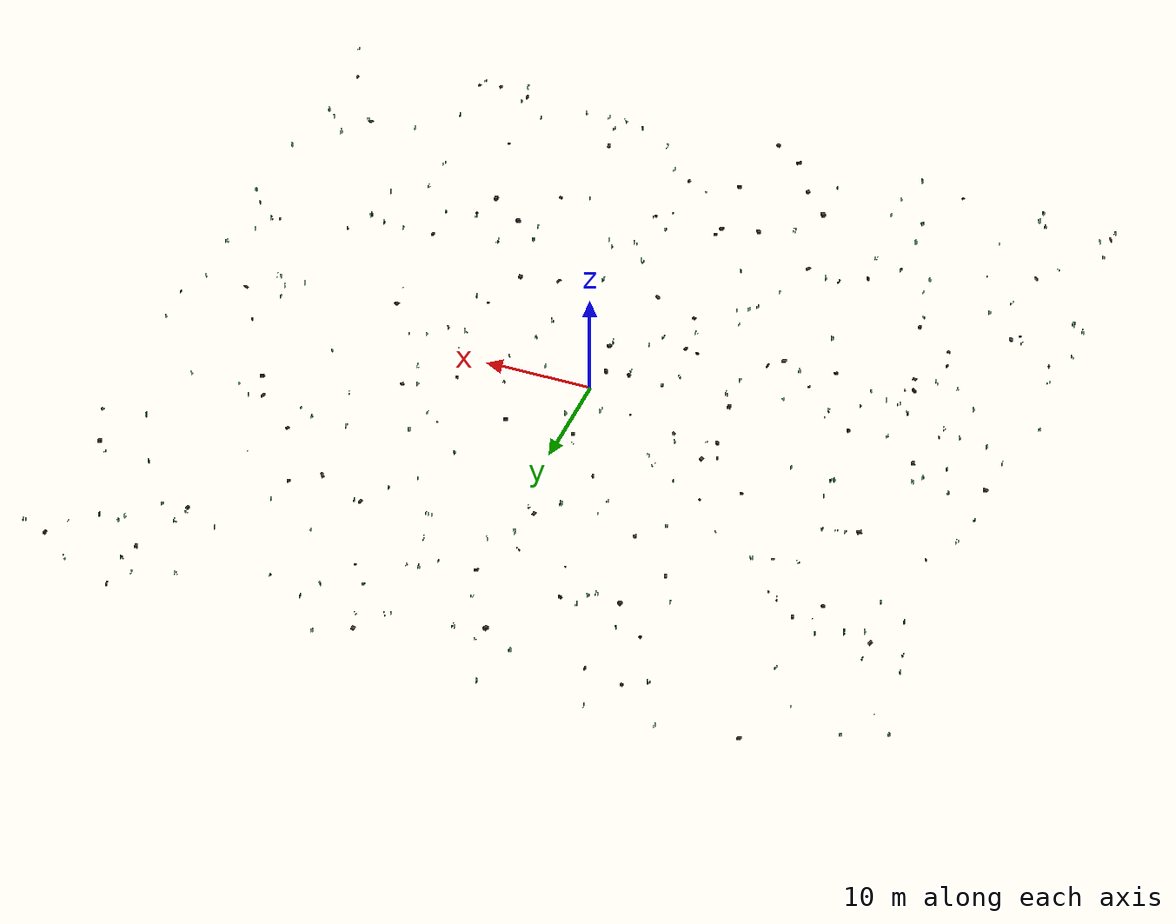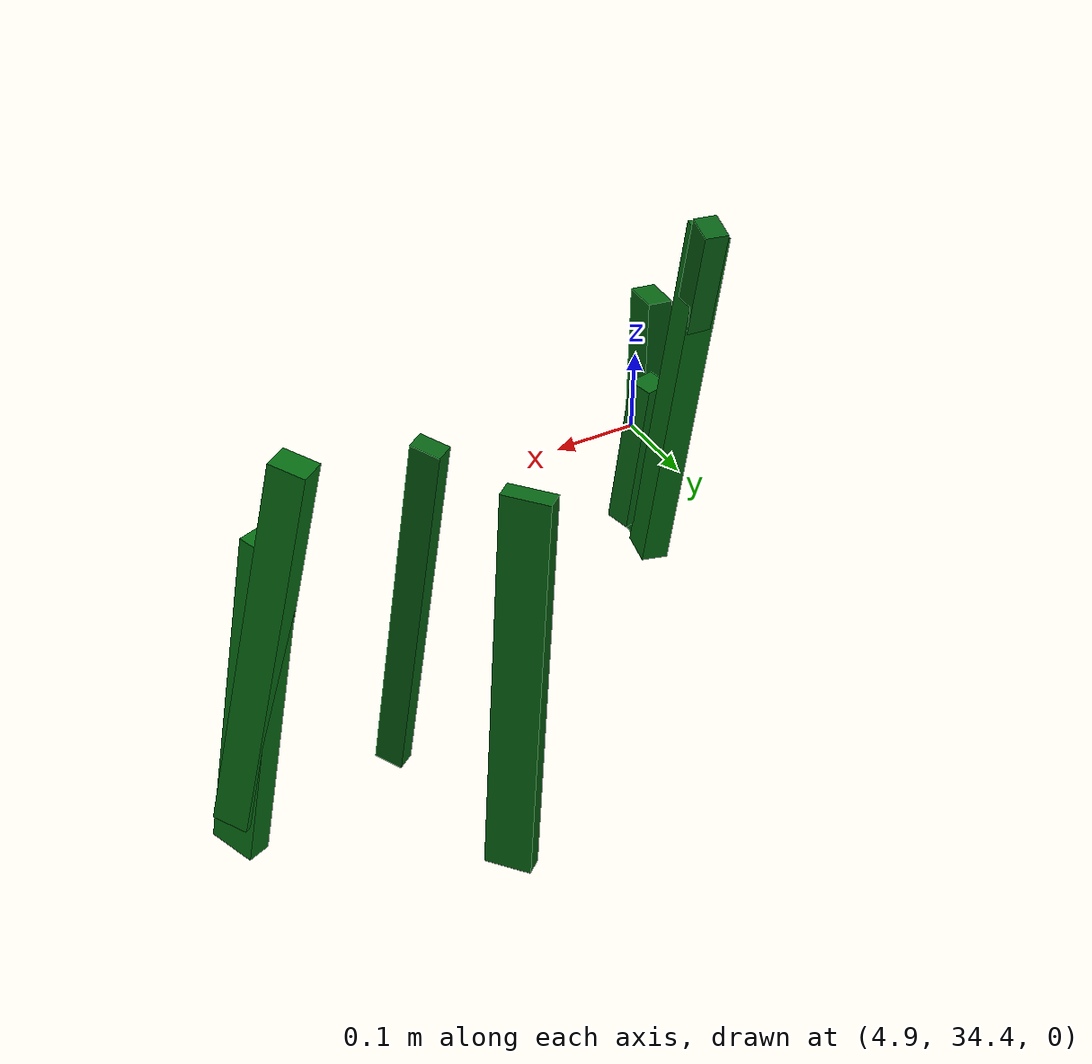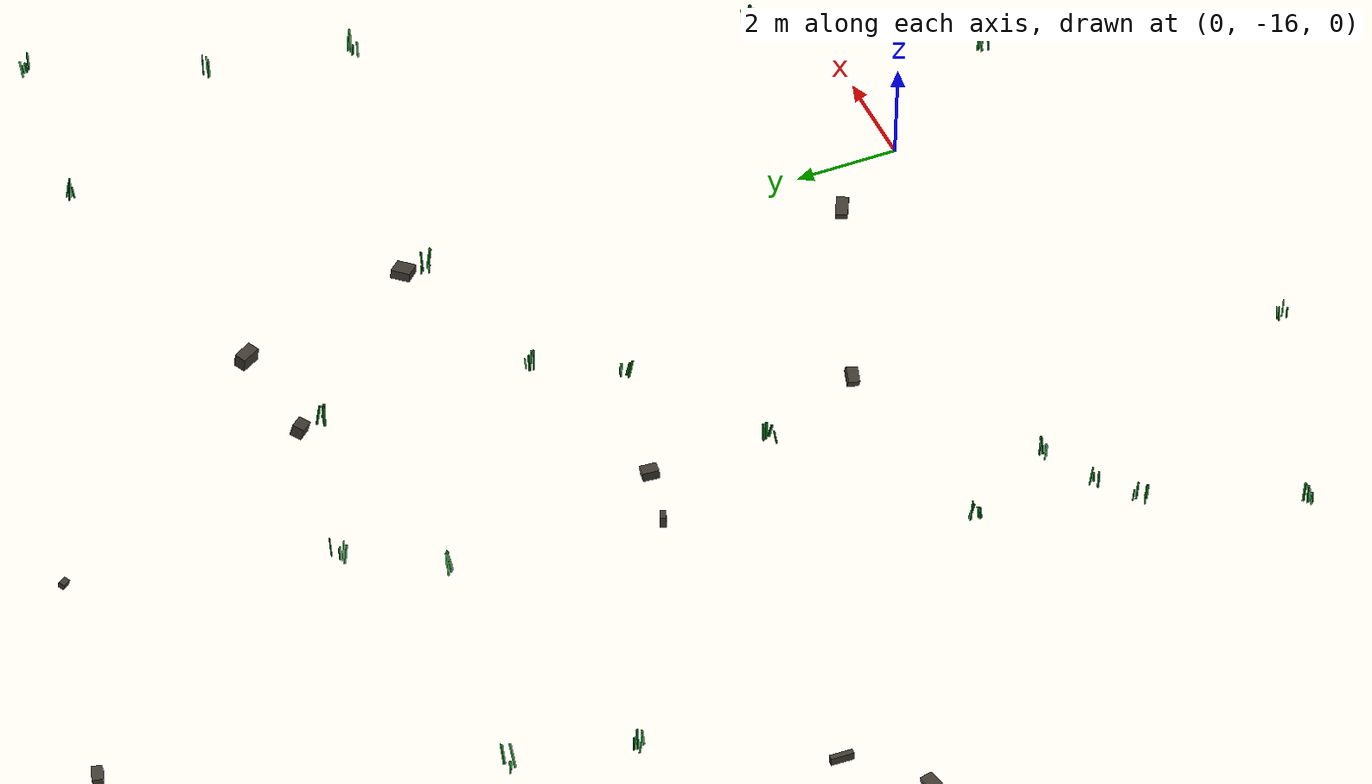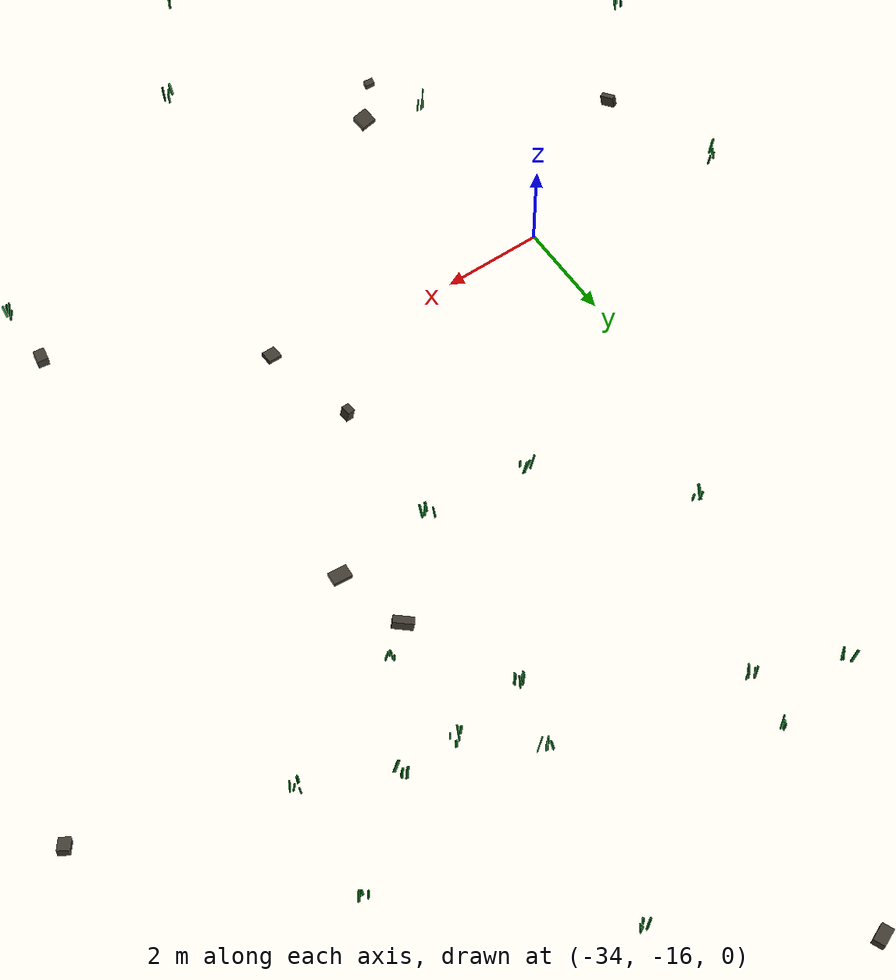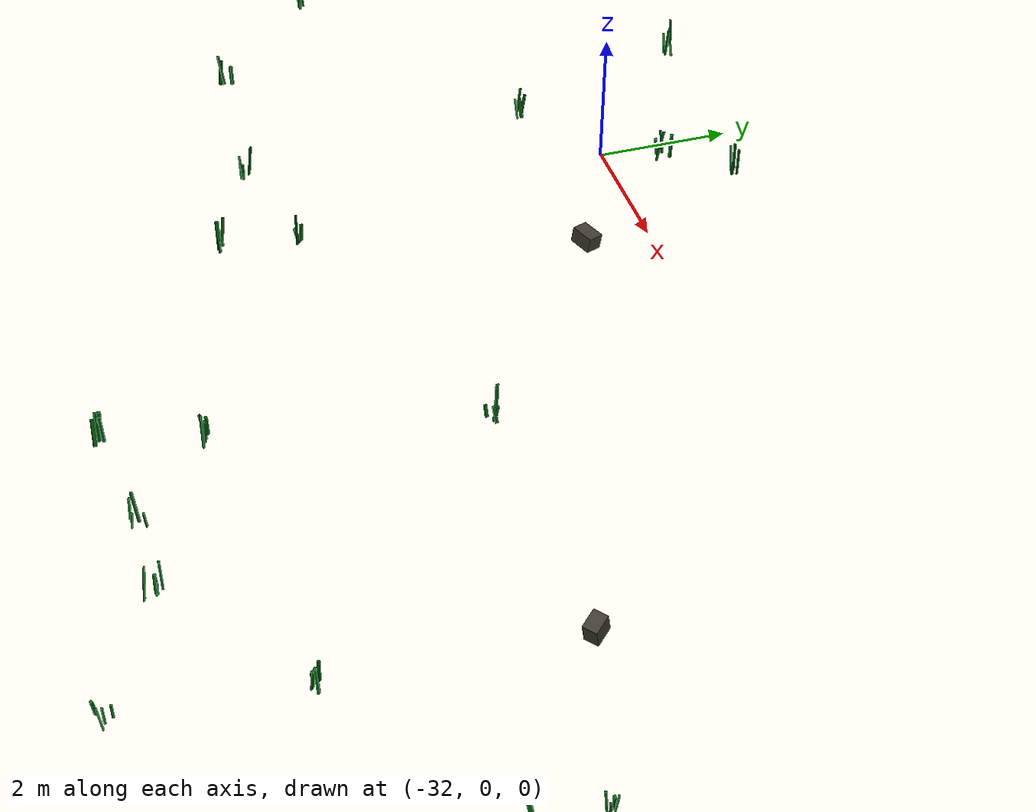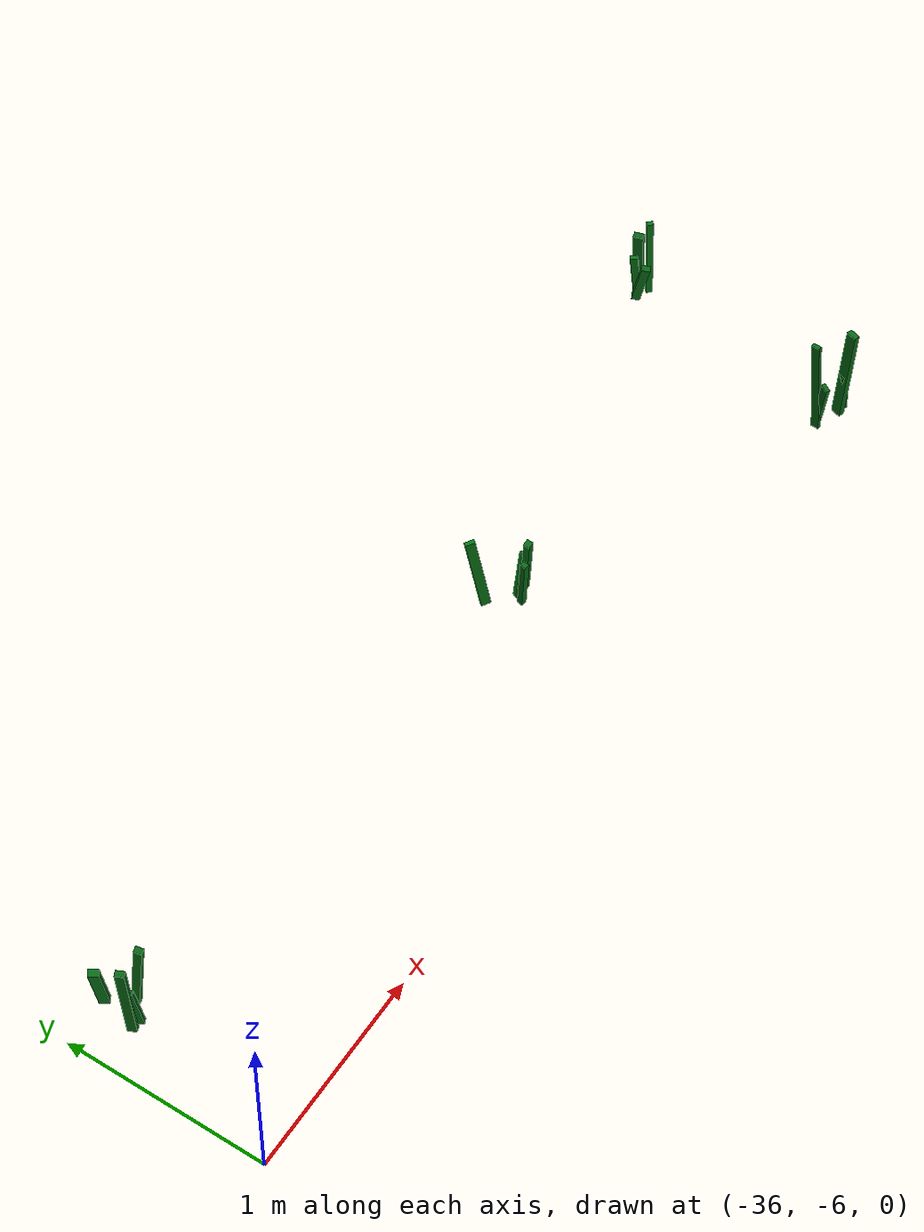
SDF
<?xml version="1.0"?>

<sdf version="1.8">

  <model name="underwater_decorations">

    <static>true</static>

    <link name="decorations_link">

      <visual name="seaweed_blade_1">
        <pose>11.248 -38.098 0.049 -0.068 -0.169 1.732</pose>

        <geometry>
          <box>
            <size>0.047 0.030 0.263</size>
          </box>
        </geometry>

        <material>
          <ambient>0.02 0.20 0.06 1</ambient>
          <diffuse>0.03 0.38 0.08 1</diffuse>
          <specular>0.01 0.02 0.01 1</specular>
        </material>

      </visual>

      <visual name="seaweed_blade_2">
        <pose>11.087 -37.978 0.080 0.073 -0.178 1.867</pose>

        <geometry>
          <box>
            <size>0.044 0.027 0.254</size>
          </box>
        </geometry>

        <material>
          <ambient>0.02 0.23 0.06 1</ambient>
          <diffuse>0.03 0.41 0.08 1</diffuse>
          <specular>0.01 0.02 0.01 1</specular>
        </material>

      </visual>

      <visual name="seaweed_blade_3">
        <pose>11.056 -38.096 0.075 0.074 0.037 1.889</pose>

        <geometry>
          <box>
            <size>0.054 0.024 0.238</size>
          </box>
        </geometry>

        <material>
          <ambient>0.02 0.24 0.06 1</ambient>
          <diffuse>0.03 0.42 0.08 1</diffuse>
          <specular>0.01 0.02 0.01 1</specular>
        </material>

      </visual>

      <visual name="seaweed_blade_4">
        <pose>11.233 -37.971 0.228 0.049 0.028 1.410</pose>

        <geometry>
          <box>
            <size>0.036 0.027 0.540</size>
          </box>
        </geometry>

        <material>
          <ambient>0.02 0.22 0.06 1</ambient>
          <diffuse>0.03 0.40 0.08 1</diffuse>
          <specular>0.01 0.02 0.01 1</specular>
        </material>

      </visual>

      <visual name="seaweed_blade_5">
        <pose>-16.881 -33.648 0.008 0.105 -0.084 1.566</pose>

        <geometry>
          <box>
            <size>0.033 0.029 0.217</size>
          </box>
        </geometry>

        <material>
          <ambient>0.02 0.25 0.06 1</ambient>
          <diffuse>0.03 0.43 0.08 1</diffuse>
          <specular>0.01 0.02 0.01 1</specular>
        </material>

      </visual>

      <visual name="seaweed_blade_6">
        <pose>-16.878 -33.499 0.059 0.044 0.021 1.703</pose>

        <geometry>
          <box>
            <size>0.047 0.021 0.243</size>
          </box>
        </geometry>

        <material>
          <ambient>0.02 0.26 0.06 1</ambient>
          <diffuse>0.03 0.44 0.08 1</diffuse>
          <specular>0.01 0.02 0.01 1</specular>
        </material>

      </visual>

      <visual name="seaweed_blade_7">
        <pose>-16.905 -33.686 0.097 -0.044 0.135 1.571</pose>

        <geometry>
          <box>
            <size>0.026 0.023 0.265</size>
          </box>
        </geometry>

        <material>
          <ambient>0.02 0.23 0.06 1</ambient>
          <diffuse>0.03 0.41 0.08 1</diffuse>
          <specular>0.01 0.02 0.01 1</specular>
        </material>

      </visual>

      <visual name="seaweed_blade_8">
        <pose>-16.910 -33.602 0.163 0.095 0.030 1.392</pose>

        <geometry>
          <box>
            <size>0.039 0.023 0.518</size>
          </box>
        </geometry>

        <material>
          <ambient>0.02 0.22 0.06 1</ambient>
          <diffuse>0.03 0.40 0.08 1</diffuse>
          <specular>0.01 0.02 0.01 1</specular>
        </material>

      </visual>

      <visual name="seaweed_blade_9">
        <pose>39.873 0.743 -0.016 0.119 -0.043 0.592</pose>

        <geometry>
          <box>
            <size>0.028 0.029 0.197</size>
          </box>
        </geometry>

        <material>
          <ambient>0.02 0.28 0.06 1</ambient>
          <diffuse>0.03 0.46 0.08 1</diffuse>
          <specular>0.01 0.02 0.01 1</specular>
        </material>

      </visual>

      <visual name="seaweed_blade_10">
        <pose>39.847 0.771 0.153 -0.093 0.051 0.526</pose>

        <geometry>
          <box>
            <size>0.025 0.030 0.498</size>
          </box>
        </geometry>

        <material>
          <ambient>0.02 0.24 0.06 1</ambient>
          <diffuse>0.03 0.42 0.08 1</diffuse>
          <specular>0.01 0.02 0.01 1</specular>
        </material>

      </visual>

      <visual name="seaweed_blade_11">
        <pose>39.803 0.685 0.229 -0.048 0.133 0.668</pose>

        <geometry>
          <box>
            <size>0.051 0.022 0.533</size>
          </box>
        </geometry>

        <material>
          <ambient>0.02 0.25 0.06 1</ambient>
          <diffuse>0.03 0.43 0.08 1</diffuse>
          <specular>0.01 0.02 0.01 1</specular>
        </material>

      </visual>

      <visual name="seaweed_blade_12">
        <pose>39.870 0.769 -0.002 -0.115 -0.063 0.872</pose>

        <geometry>
          <box>
            <size>0.048 0.027 0.237</size>
          </box>
        </geometry>

        <material>
          <ambient>0.02 0.27 0.06 1</ambient>
          <diffuse>0.03 0.45 0.08 1</diffuse>
          <specular>0.01 0.02 0.01 1</specular>
        </material>

      </visual>

      <visual name="seaweed_blade_13">
        <pose>26.530 -15.502 0.201 -0.089 0.096 0.347</pose>

        <geometry>
          <box>
            <size>0.053 0.019 0.505</size>
          </box>
        </geometry>

        <material>
          <ambient>0.02 0.24 0.06 1</ambient>
          <diffuse>0.03 0.42 0.08 1</diffuse>
          <specular>0.01 0.02 0.01 1</specular>
        </material>

      </visual>

      <visual name="seaweed_blade_14">
        <pose>26.464 -15.389 0.085 -0.045 -0.108 0.711</pose>

        <geometry>
          <box>
            <size>0.051 0.025 0.278</size>
          </box>
        </geometry>

        <material>
          <ambient>0.02 0.25 0.06 1</ambient>
          <diffuse>0.03 0.43 0.08 1</diffuse>
          <specular>0.01 0.02 0.01 1</specular>
        </material>

      </visual>

      <visual name="seaweed_blade_15">
        <pose>26.467 -15.438 0.104 -0.067 -0.097 0.064</pose>

        <geometry>
          <box>
            <size>0.041 0.020 0.342</size>
          </box>
        </geometry>

        <material>
          <ambient>0.02 0.25 0.06 1</ambient>
          <diffuse>0.03 0.43 0.08 1</diffuse>
          <specular>0.01 0.02 0.01 1</specular>
        </material>

      </visual>

      <visual name="seaweed_blade_16">
        <pose>26.430 -15.462 0.073 -0.088 -0.103 0.669</pose>

        <geometry>
          <box>
            <size>0.052 0.033 0.265</size>
          </box>
        </geometry>

        <material>
          <ambient>0.02 0.25 0.06 1</ambient>
          <diffuse>0.03 0.43 0.08 1</diffuse>
          <specular>0.01 0.02 0.01 1</specular>
        </material>

      </visual>

      <visual name="seaweed_blade_17">
        <pose>-2.205 22.762 0.071 0.116 0.062 4.793</pose>

        <geometry>
          <box>
            <size>0.028 0.025 0.250</size>
          </box>
        </geometry>

        <material>
          <ambient>0.02 0.23 0.06 1</ambient>
          <diffuse>0.03 0.41 0.08 1</diffuse>
          <specular>0.01 0.02 0.01 1</specular>
        </material>

      </visual>

      <visual name="seaweed_blade_18">
        <pose>-2.261 22.757 0.071 -0.060 -0.080 5.370</pose>

        <geometry>
          <box>
            <size>0.051 0.022 0.306</size>
          </box>
        </geometry>

        <material>
          <ambient>0.02 0.24 0.06 1</ambient>
          <diffuse>0.03 0.42 0.08 1</diffuse>
          <specular>0.01 0.02 0.01 1</specular>
        </material>

      </visual>

      <visual name="seaweed_blade_19">
        <pose>-2.066 22.850 0.217 0.084 0.153 4.840</pose>

        <geometry>
          <box>
            <size>0.042 0.019 0.499</size>
          </box>
        </geometry>

        <material>
          <ambient>0.02 0.24 0.06 1</ambient>
          <diffuse>0.03 0.42 0.08 1</diffuse>
          <specular>0.01 0.02 0.01 1</specular>
        </material>

      </visual>

      <visual name="seaweed_blade_20">
        <pose>-2.215 22.886 0.033 -0.011 0.102 5.020</pose>

        <geometry>
          <box>
            <size>0.037 0.019 0.259</size>
          </box>
        </geometry>

        <material>
          <ambient>0.02 0.28 0.06 1</ambient>
          <diffuse>0.03 0.46 0.08 1</diffuse>
          <specular>0.01 0.02 0.01 1</specular>
        </material>

      </visual>

      <visual name="seaweed_blade_21">
        <pose>39.653 4.472 0.066 0.020 -0.159 4.516</pose>

        <geometry>
          <box>
            <size>0.034 0.034 0.237</size>
          </box>
        </geometry>

        <material>
          <ambient>0.02 0.27 0.06 1</ambient>
          <diffuse>0.03 0.45 0.08 1</diffuse>
          <specular>0.01 0.02 0.01 1</specular>
        </material>

      </visual>

      <visual name="seaweed_blade_22">
        <pose>39.558 4.484 0.060 -0.091 -0.095 4.787</pose>

        <geometry>
          <box>
            <size>0.054 0.019 0.238</size>
          </box>
        </geometry>

        <material>
          <ambient>0.02 0.22 0.06 1</ambient>
          <diffuse>0.03 0.40 0.08 1</diffuse>
          <specular>0.01 0.02 0.01 1</specular>
        </material>

      </visual>

      <visual name="seaweed_blade_23">
        <pose>39.654 4.467 0.164 0.052 -0.106 4.331</pose>

        <geometry>
          <box>
            <size>0.044 0.025 0.400</size>
          </box>
        </geometry>

        <material>
          <ambient>0.02 0.23 0.06 1</ambient>
          <diffuse>0.03 0.41 0.08 1</diffuse>
          <specular>0.01 0.02 0.01 1</specular>
        </material>

      </visual>

      <visual name="seaweed_blade_24">
        <pose>39.694 4.359 0.136 0.119 0.179 4.215</pose>

        <geometry>
          <box>
            <size>0.034 0.023 0.429</size>
          </box>
        </geometry>

        <material>
          <ambient>0.02 0.22 0.06 1</ambient>
          <diffuse>0.03 0.40 0.08 1</diffuse>
          <specular>0.01 0.02 0.01 1</specular>
        </material>

      </visual>

      <visual name="seaweed_blade_25">
        <pose>-18.704 34.710 0.188 0.037 0.175 5.190</pose>

        <geometry>
          <box>
            <size>0.036 0.021 0.505</size>
          </box>
        </geometry>

        <material>
          <ambient>0.02 0.27 0.06 1</ambient>
          <diffuse>0.03 0.45 0.08 1</diffuse>
          <specular>0.01 0.02 0.01 1</specular>
        </material>

      </visual>

      <visual name="seaweed_blade_26">
        <pose>-18.872 34.568 0.035 -0.055 0.019 5.608</pose>

        <geometry>
          <box>
            <size>0.045 0.034 0.291</size>
          </box>
        </geometry>

        <material>
          <ambient>0.02 0.26 0.06 1</ambient>
          <diffuse>0.03 0.44 0.08 1</diffuse>
          <specular>0.01 0.02 0.01 1</specular>
        </material>

      </visual>

      <visual name="seaweed_blade_27">
        <pose>-18.787 34.758 0.084 -0.018 -0.147 5.378</pose>

        <geometry>
          <box>
            <size>0.044 0.022 0.255</size>
          </box>
        </geometry>

        <material>
          <ambient>0.02 0.20 0.06 1</ambient>
          <diffuse>0.03 0.38 0.08 1</diffuse>
          <specular>0.01 0.02 0.01 1</specular>
        </material>

      </visual>

      <visual name="seaweed_blade_28">
        <pose>-18.726 34.673 0.151 -0.102 -0.177 5.803</pose>

        <geometry>
          <box>
            <size>0.044 0.022 0.465</size>
          </box>
        </geometry>

        <material>
          <ambient>0.02 0.27 0.06 1</ambient>
          <diffuse>0.03 0.45 0.08 1</diffuse>
          <specular>0.01 0.02 0.01 1</specular>
        </material>

      </visual>

      <visual name="seaweed_blade_29">
        <pose>3.743 26.839 0.075 -0.070 0.144 3.485</pose>

        <geometry>
          <box>
            <size>0.029 0.023 0.235</size>
          </box>
        </geometry>

        <material>
          <ambient>0.02 0.21 0.06 1</ambient>
          <diffuse>0.03 0.39 0.08 1</diffuse>
          <specular>0.01 0.02 0.01 1</specular>
        </material>

      </visual>

      <visual name="seaweed_blade_30">
        <pose>3.676 26.685 0.198 0.114 0.131 3.878</pose>

        <geometry>
          <box>
            <size>0.052 0.025 0.469</size>
          </box>
        </geometry>

        <material>
          <ambient>0.02 0.27 0.06 1</ambient>
          <diffuse>0.03 0.45 0.08 1</diffuse>
          <specular>0.01 0.02 0.01 1</specular>
        </material>

      </visual>

      <visual name="seaweed_blade_31">
        <pose>3.751 26.840 0.052 -0.056 0.112 3.861</pose>

        <geometry>
          <box>
            <size>0.047 0.024 0.189</size>
          </box>
        </geometry>

        <material>
          <ambient>0.02 0.21 0.06 1</ambient>
          <diffuse>0.03 0.39 0.08 1</diffuse>
          <specular>0.01 0.02 0.01 1</specular>
        </material>

      </visual>

      <visual name="seaweed_blade_32">
        <pose>3.723 26.758 0.159 -0.065 0.106 3.327</pose>

        <geometry>
          <box>
            <size>0.051 0.022 0.503</size>
          </box>
        </geometry>

        <material>
          <ambient>0.02 0.22 0.06 1</ambient>
          <diffuse>0.03 0.40 0.08 1</diffuse>
          <specular>0.01 0.02 0.01 1</specular>
        </material>

      </visual>

      <visual name="seaweed_blade_33">
        <pose>-13.624 29.157 0.106 0.113 -0.138 5.850</pose>

        <geometry>
          <box>
            <size>0.044 0.025 0.283</size>
          </box>
        </geometry>

        <material>
          <ambient>0.02 0.28 0.06 1</ambient>
          <diffuse>0.03 0.46 0.08 1</diffuse>
          <specular>0.01 0.02 0.01 1</specular>
        </material>

      </visual>

      <visual name="seaweed_blade_34">
        <pose>-13.684 29.104 0.074 -0.028 0.004 6.129</pose>

        <geometry>
          <box>
            <size>0.028 0.025 0.278</size>
          </box>
        </geometry>

        <material>
          <ambient>0.02 0.22 0.06 1</ambient>
          <diffuse>0.03 0.40 0.08 1</diffuse>
          <specular>0.01 0.02 0.01 1</specular>
        </material>

      </visual>

      <visual name="seaweed_blade_35">
        <pose>-13.730 29.201 0.168 -0.033 0.061 5.774</pose>

        <geometry>
          <box>
            <size>0.025 0.034 0.442</size>
          </box>
        </geometry>

        <material>
          <ambient>0.02 0.25 0.06 1</ambient>
          <diffuse>0.03 0.43 0.08 1</diffuse>
          <specular>0.01 0.02 0.01 1</specular>
        </material>

      </visual>

      <visual name="seaweed_blade_36">
        <pose>-13.686 29.100 0.059 -0.023 -0.033 5.932</pose>

        <geometry>
          <box>
            <size>0.034 0.032 0.302</size>
          </box>
        </geometry>

        <material>
          <ambient>0.02 0.21 0.06 1</ambient>
          <diffuse>0.03 0.39 0.08 1</diffuse>
          <specular>0.01 0.02 0.01 1</specular>
        </material>

      </visual>

      <visual name="seaweed_blade_37">
        <pose>-6.353 35.109 0.163 0.019 -0.025 4.364</pose>

        <geometry>
          <box>
            <size>0.043 0.023 0.514</size>
          </box>
        </geometry>

        <material>
          <ambient>0.02 0.24 0.06 1</ambient>
          <diffuse>0.03 0.42 0.08 1</diffuse>
          <specular>0.01 0.02 0.01 1</specular>
        </material>

      </visual>

      <visual name="seaweed_blade_38">
        <pose>-6.268 35.300 0.067 0.004 -0.149 4.349</pose>

        <geometry>
          <box>
            <size>0.031 0.026 0.344</size>
          </box>
        </geometry>

        <material>
          <ambient>0.02 0.23 0.06 1</ambient>
          <diffuse>0.03 0.41 0.08 1</diffuse>
          <specular>0.01 0.02 0.01 1</specular>
        </material>

      </visual>

      <visual name="seaweed_blade_39">
        <pose>-6.430 35.157 0.124 -0.006 -0.092 4.501</pose>

        <geometry>
          <box>
            <size>0.048 0.029 0.483</size>
          </box>
        </geometry>

        <material>
          <ambient>0.02 0.21 0.06 1</ambient>
          <diffuse>0.03 0.39 0.08 1</diffuse>
          <specular>0.01 0.02 0.01 1</specular>
        </material>

      </visual>

      <visual name="seaweed_blade_40">
        <pose>-6.317 35.228 0.069 -0.119 0.056 4.431</pose>

        <geometry>
          <box>
            <size>0.044 0.021 0.333</size>
          </box>
        </geometry>

        <material>
          <ambient>0.02 0.26 0.06 1</ambient>
          <diffuse>0.03 0.44 0.08 1</diffuse>
          <specular>0.01 0.02 0.01 1</specular>
        </material>

      </visual>

      <visual name="seaweed_blade_41">
        <pose>-31.533 -5.905 0.188 0.040 0.109 1.447</pose>

        <geometry>
          <box>
            <size>0.041 0.019 0.534</size>
          </box>
        </geometry>

        <material>
          <ambient>0.02 0.25 0.06 1</ambient>
          <diffuse>0.03 0.43 0.08 1</diffuse>
          <specular>0.01 0.02 0.01 1</specular>
        </material>

      </visual>

      <visual name="seaweed_blade_42">
        <pose>-31.420 -5.987 0.221 0.095 0.017 1.276</pose>

        <geometry>
          <box>
            <size>0.052 0.028 0.532</size>
          </box>
        </geometry>

        <material>
          <ambient>0.02 0.24 0.06 1</ambient>
          <diffuse>0.03 0.42 0.08 1</diffuse>
          <specular>0.01 0.02 0.01 1</specular>
        </material>

      </visual>

      <visual name="seaweed_blade_43">
        <pose>-31.409 -5.983 0.074 -0.101 -0.081 0.955</pose>

        <geometry>
          <box>
            <size>0.032 0.029 0.276</size>
          </box>
        </geometry>

        <material>
          <ambient>0.02 0.22 0.06 1</ambient>
          <diffuse>0.03 0.40 0.08 1</diffuse>
          <specular>0.01 0.02 0.01 1</specular>
        </material>

      </visual>

      <visual name="seaweed_blade_44">
        <pose>-31.538 -5.942 0.093 -0.022 -0.157 1.135</pose>

        <geometry>
          <box>
            <size>0.041 0.020 0.298</size>
          </box>
        </geometry>

        <material>
          <ambient>0.02 0.23 0.06 1</ambient>
          <diffuse>0.03 0.41 0.08 1</diffuse>
          <specular>0.01 0.02 0.01 1</specular>
        </material>

      </visual>

      <visual name="seaweed_blade_45">
        <pose>-23.390 -6.417 0.079 0.061 -0.053 5.933</pose>

        <geometry>
          <box>
            <size>0.046 0.033 0.396</size>
          </box>
        </geometry>

        <material>
          <ambient>0.02 0.28 0.06 1</ambient>
          <diffuse>0.03 0.46 0.08 1</diffuse>
          <specular>0.01 0.02 0.01 1</specular>
        </material>

      </visual>

      <visual name="seaweed_blade_46">
        <pose>-23.428 -6.456 0.067 -0.113 -0.023 5.571</pose>

        <geometry>
          <box>
            <size>0.047 0.027 0.335</size>
          </box>
        </geometry>

        <material>
          <ambient>0.02 0.25 0.06 1</ambient>
          <diffuse>0.03 0.43 0.08 1</diffuse>
          <specular>0.01 0.02 0.01 1</specular>
        </material>

      </visual>

      <visual name="seaweed_blade_47">
        <pose>-23.543 -6.359 0.047 0.015 -0.038 5.354</pose>

        <geometry>
          <box>
            <size>0.030 0.026 0.330</size>
          </box>
        </geometry>

        <material>
          <ambient>0.02 0.25 0.06 1</ambient>
          <diffuse>0.03 0.43 0.08 1</diffuse>
          <specular>0.01 0.02 0.01 1</specular>
        </material>

      </visual>

      <visual name="seaweed_blade_48">
        <pose>-23.482 -6.458 0.025 -0.029 0.094 5.862</pose>

        <geometry>
          <box>
            <size>0.039 0.019 0.230</size>
          </box>
        </geometry>

        <material>
          <ambient>0.02 0.27 0.06 1</ambient>
          <diffuse>0.03 0.45 0.08 1</diffuse>
          <specular>0.01 0.02 0.01 1</specular>
        </material>

      </visual>

      <visual name="seaweed_blade_49">
        <pose>-19.782 -33.380 0.128 0.108 0.092 -0.089</pose>

        <geometry>
          <box>
            <size>0.055 0.024 0.380</size>
          </box>
        </geometry>

        <material>
          <ambient>0.02 0.20 0.06 1</ambient>
          <diffuse>0.03 0.38 0.08 1</diffuse>
          <specular>0.01 0.02 0.01 1</specular>
        </material>

      </visual>

      <visual name="seaweed_blade_50">
        <pose>-19.803 -33.515 0.061 -0.080 0.096 0.197</pose>

        <geometry>
          <box>
            <size>0.029 0.029 0.236</size>
          </box>
        </geometry>

        <material>
          <ambient>0.02 0.26 0.06 1</ambient>
          <diffuse>0.03 0.44 0.08 1</diffuse>
          <specular>0.01 0.02 0.01 1</specular>
        </material>

      </visual>

      <visual name="seaweed_blade_51">
        <pose>-19.912 -33.561 0.019 0.110 0.064 0.049</pose>

        <geometry>
          <box>
            <size>0.050 0.034 0.222</size>
          </box>
        </geometry>

        <material>
          <ambient>0.02 0.26 0.06 1</ambient>
          <diffuse>0.03 0.44 0.08 1</diffuse>
          <specular>0.01 0.02 0.01 1</specular>
        </material>

      </visual>

      <visual name="seaweed_blade_52">
        <pose>-19.914 -33.382 0.061 -0.091 0.036 0.460</pose>

        <geometry>
          <box>
            <size>0.046 0.029 0.208</size>
          </box>
        </geometry>

        <material>
          <ambient>0.02 0.26 0.06 1</ambient>
          <diffuse>0.03 0.44 0.08 1</diffuse>
          <specular>0.01 0.02 0.01 1</specular>
        </material>

      </visual>

      <visual name="seaweed_blade_53">
        <pose>-12.146 -5.824 0.150 0.079 0.049 2.473</pose>

        <geometry>
          <box>
            <size>0.035 0.032 0.367</size>
          </box>
        </geometry>

        <material>
          <ambient>0.02 0.23 0.06 1</ambient>
          <diffuse>0.03 0.41 0.08 1</diffuse>
          <specular>0.01 0.02 0.01 1</specular>
        </material>

      </visual>

      <visual name="seaweed_blade_54">
        <pose>-12.150 -5.721 0.149 0.055 -0.023 2.166</pose>

        <geometry>
          <box>
            <size>0.054 0.023 0.452</size>
          </box>
        </geometry>

        <material>
          <ambient>0.02 0.27 0.06 1</ambient>
          <diffuse>0.03 0.45 0.08 1</diffuse>
          <specular>0.01 0.02 0.01 1</specular>
        </material>

      </visual>

      <visual name="seaweed_blade_55">
        <pose>-12.285 -5.738 0.179 -0.113 -0.044 2.574</pose>

        <geometry>
          <box>
            <size>0.028 0.033 0.487</size>
          </box>
        </geometry>

        <material>
          <ambient>0.02 0.21 0.06 1</ambient>
          <diffuse>0.03 0.39 0.08 1</diffuse>
          <specular>0.01 0.02 0.01 1</specular>
        </material>

      </visual>

      <visual name="seaweed_blade_56">
        <pose>-12.132 -5.681 0.034 0.108 -0.176 2.038</pose>

        <geometry>
          <box>
            <size>0.049 0.024 0.258</size>
          </box>
        </geometry>

        <material>
          <ambient>0.02 0.26 0.06 1</ambient>
          <diffuse>0.03 0.44 0.08 1</diffuse>
          <specular>0.01 0.02 0.01 1</specular>
        </material>

      </visual>

      <visual name="seaweed_blade_57">
        <pose>-1.011 20.586 0.152 0.020 -0.070 4.321</pose>

        <geometry>
          <box>
            <size>0.040 0.031 0.419</size>
          </box>
        </geometry>

        <material>
          <ambient>0.02 0.24 0.06 1</ambient>
          <diffuse>0.03 0.42 0.08 1</diffuse>
          <specular>0.01 0.02 0.01 1</specular>
        </material>

      </visual>

      <visual name="seaweed_blade_58">
        <pose>-0.865 20.598 0.071 -0.074 -0.137 4.073</pose>

        <geometry>
          <box>
            <size>0.047 0.024 0.337</size>
          </box>
        </geometry>

        <material>
          <ambient>0.02 0.24 0.06 1</ambient>
          <diffuse>0.03 0.42 0.08 1</diffuse>
          <specular>0.01 0.02 0.01 1</specular>
        </material>

      </visual>

      <visual name="seaweed_blade_59">
        <pose>-0.918 20.707 0.199 -0.052 0.009 4.060</pose>

        <geometry>
          <box>
            <size>0.031 0.022 0.462</size>
          </box>
        </geometry>

        <material>
          <ambient>0.02 0.22 0.06 1</ambient>
          <diffuse>0.03 0.40 0.08 1</diffuse>
          <specular>0.01 0.02 0.01 1</specular>
        </material>

      </visual>

      <visual name="seaweed_blade_60">
        <pose>-0.906 20.599 0.100 0.047 0.019 4.078</pose>

        <geometry>
          <box>
            <size>0.030 0.018 0.264</size>
          </box>
        </geometry>

        <material>
          <ambient>0.02 0.27 0.06 1</ambient>
          <diffuse>0.03 0.45 0.08 1</diffuse>
          <specular>0.01 0.02 0.01 1</specular>
        </material>

      </visual>

      <visual name="seaweed_blade_61">
        <pose>-0.837 29.923 0.100 -0.024 0.116 3.309</pose>

        <geometry>
          <box>
            <size>0.038 0.021 0.354</size>
          </box>
        </geometry>

        <material>
          <ambient>0.02 0.25 0.06 1</ambient>
          <diffuse>0.03 0.43 0.08 1</diffuse>
          <specular>0.01 0.02 0.01 1</specular>
        </material>

      </visual>

      <visual name="seaweed_blade_62">
        <pose>-0.777 29.936 -0.009 0.026 0.095 3.810</pose>

        <geometry>
          <box>
            <size>0.029 0.028 0.200</size>
          </box>
        </geometry>

        <material>
          <ambient>0.02 0.22 0.06 1</ambient>
          <diffuse>0.03 0.40 0.08 1</diffuse>
          <specular>0.01 0.02 0.01 1</specular>
        </material>

      </visual>

      <visual name="seaweed_blade_63">
        <pose>-0.643 29.935 0.094 0.026 0.044 3.775</pose>

        <geometry>
          <box>
            <size>0.039 0.026 0.373</size>
          </box>
        </geometry>

        <material>
          <ambient>0.02 0.28 0.06 1</ambient>
          <diffuse>0.03 0.46 0.08 1</diffuse>
          <specular>0.01 0.02 0.01 1</specular>
        </material>

      </visual>

      <visual name="seaweed_blade_64">
        <pose>-0.812 29.739 0.015 -0.012 -0.179 3.673</pose>

        <geometry>
          <box>
            <size>0.031 0.029 0.257</size>
          </box>
        </geometry>

        <material>
          <ambient>0.02 0.22 0.06 1</ambient>
          <diffuse>0.03 0.40 0.08 1</diffuse>
          <specular>0.01 0.02 0.01 1</specular>
        </material>

      </visual>

      <visual name="seaweed_blade_65">
        <pose>-21.413 16.586 0.114 -0.018 0.156 4.448</pose>

        <geometry>
          <box>
            <size>0.046 0.034 0.348</size>
          </box>
        </geometry>

        <material>
          <ambient>0.02 0.25 0.06 1</ambient>
          <diffuse>0.03 0.43 0.08 1</diffuse>
          <specular>0.01 0.02 0.01 1</specular>
        </material>

      </visual>

      <visual name="seaweed_blade_66">
        <pose>-21.562 16.510 0.205 -0.051 0.025 4.154</pose>

        <geometry>
          <box>
            <size>0.050 0.019 0.516</size>
          </box>
        </geometry>

        <material>
          <ambient>0.02 0.26 0.06 1</ambient>
          <diffuse>0.03 0.44 0.08 1</diffuse>
          <specular>0.01 0.02 0.01 1</specular>
        </material>

      </visual>

      <visual name="seaweed_blade_67">
        <pose>-21.483 16.456 0.103 -0.043 -0.024 4.242</pose>

        <geometry>
          <box>
            <size>0.053 0.027 0.439</size>
          </box>
        </geometry>

        <material>
          <ambient>0.02 0.21 0.06 1</ambient>
          <diffuse>0.03 0.39 0.08 1</diffuse>
          <specular>0.01 0.02 0.01 1</specular>
        </material>

      </visual>

      <visual name="seaweed_blade_68">
        <pose>-21.374 16.676 0.208 -0.110 -0.083 4.596</pose>

        <geometry>
          <box>
            <size>0.050 0.028 0.536</size>
          </box>
        </geometry>

        <material>
          <ambient>0.02 0.24 0.06 1</ambient>
          <diffuse>0.03 0.42 0.08 1</diffuse>
          <specular>0.01 0.02 0.01 1</specular>
        </material>

      </visual>

      <visual name="seaweed_blade_69">
        <pose>12.023 33.249 0.108 0.086 0.061 1.021</pose>

        <geometry>
          <box>
            <size>0.044 0.026 0.397</size>
          </box>
        </geometry>

        <material>
          <ambient>0.02 0.26 0.06 1</ambient>
          <diffuse>0.03 0.44 0.08 1</diffuse>
          <specular>0.01 0.02 0.01 1</specular>
        </material>

      </visual>

      <visual name="seaweed_blade_70">
        <pose>12.133 33.275 0.052 0.113 -0.064 1.073</pose>

        <geometry>
          <box>
            <size>0.053 0.032 0.287</size>
          </box>
        </geometry>

        <material>
          <ambient>0.02 0.24 0.06 1</ambient>
          <diffuse>0.03 0.42 0.08 1</diffuse>
          <specular>0.01 0.02 0.01 1</specular>
        </material>

      </visual>

      <visual name="seaweed_blade_71">
        <pose>12.100 33.211 0.185 0.030 0.092 1.322</pose>

        <geometry>
          <box>
            <size>0.045 0.027 0.546</size>
          </box>
        </geometry>

        <material>
          <ambient>0.02 0.22 0.06 1</ambient>
          <diffuse>0.03 0.40 0.08 1</diffuse>
          <specular>0.01 0.02 0.01 1</specular>
        </material>

      </visual>

      <visual name="seaweed_blade_72">
        <pose>12.168 33.195 0.159 -0.063 0.039 0.901</pose>

        <geometry>
          <box>
            <size>0.053 0.025 0.383</size>
          </box>
        </geometry>

        <material>
          <ambient>0.02 0.24 0.06 1</ambient>
          <diffuse>0.03 0.42 0.08 1</diffuse>
          <specular>0.01 0.02 0.01 1</specular>
        </material>

      </visual>

      <visual name="seaweed_blade_73">
        <pose>4.260 -32.544 0.203 -0.054 0.003 6.469</pose>

        <geometry>
          <box>
            <size>0.039 0.020 0.518</size>
          </box>
        </geometry>

        <material>
          <ambient>0.02 0.28 0.06 1</ambient>
          <diffuse>0.03 0.46 0.08 1</diffuse>
          <specular>0.01 0.02 0.01 1</specular>
        </material>

      </visual>

      <visual name="seaweed_blade_74">
        <pose>4.281 -32.541 0.094 -0.054 0.131 6.438</pose>

        <geometry>
          <box>
            <size>0.042 0.025 0.270</size>
          </box>
        </geometry>

        <material>
          <ambient>0.02 0.23 0.06 1</ambient>
          <diffuse>0.03 0.41 0.08 1</diffuse>
          <specular>0.01 0.02 0.01 1</specular>
        </material>

      </visual>

      <visual name="seaweed_blade_75">
        <pose>4.128 -32.592 0.196 -0.002 0.180 5.989</pose>

        <geometry>
          <box>
            <size>0.040 0.032 0.526</size>
          </box>
        </geometry>

        <material>
          <ambient>0.02 0.24 0.06 1</ambient>
          <diffuse>0.03 0.42 0.08 1</diffuse>
          <specular>0.01 0.02 0.01 1</specular>
        </material>

      </visual>

      <visual name="seaweed_blade_76">
        <pose>4.169 -32.586 0.051 0.017 0.071 6.048</pose>

        <geometry>
          <box>
            <size>0.042 0.027 0.308</size>
          </box>
        </geometry>

        <material>
          <ambient>0.02 0.26 0.06 1</ambient>
          <diffuse>0.03 0.44 0.08 1</diffuse>
          <specular>0.01 0.02 0.01 1</specular>
        </material>

      </visual>

      <visual name="seaweed_blade_77">
        <pose>-36.431 19.692 0.165 0.001 -0.167 4.494</pose>

        <geometry>
          <box>
            <size>0.037 0.029 0.480</size>
          </box>
        </geometry>

        <material>
          <ambient>0.02 0.27 0.06 1</ambient>
          <diffuse>0.03 0.45 0.08 1</diffuse>
          <specular>0.01 0.02 0.01 1</specular>
        </material>

      </visual>

      <visual name="seaweed_blade_78">
        <pose>-36.519 19.630 0.169 -0.083 0.056 4.410</pose>

        <geometry>
          <box>
            <size>0.038 0.027 0.503</size>
          </box>
        </geometry>

        <material>
          <ambient>0.02 0.28 0.06 1</ambient>
          <diffuse>0.03 0.46 0.08 1</diffuse>
          <specular>0.01 0.02 0.01 1</specular>
        </material>

      </visual>

      <visual name="seaweed_blade_79">
        <pose>-36.424 19.661 0.110 -0.044 -0.043 4.584</pose>

        <geometry>
          <box>
            <size>0.046 0.029 0.305</size>
          </box>
        </geometry>

        <material>
          <ambient>0.02 0.26 0.06 1</ambient>
          <diffuse>0.03 0.44 0.08 1</diffuse>
          <specular>0.01 0.02 0.01 1</specular>
        </material>

      </visual>

      <visual name="seaweed_blade_80">
        <pose>-36.477 19.677 0.221 -0.016 0.089 4.150</pose>

        <geometry>
          <box>
            <size>0.026 0.019 0.503</size>
          </box>
        </geometry>

        <material>
          <ambient>0.02 0.25 0.06 1</ambient>
          <diffuse>0.03 0.43 0.08 1</diffuse>
          <specular>0.01 0.02 0.01 1</specular>
        </material>

      </visual>

      <visual name="seaweed_blade_81">
        <pose>29.757 -4.536 0.150 0.016 0.011 4.565</pose>

        <geometry>
          <box>
            <size>0.026 0.032 0.514</size>
          </box>
        </geometry>

        <material>
          <ambient>0.02 0.21 0.06 1</ambient>
          <diffuse>0.03 0.39 0.08 1</diffuse>
          <specular>0.01 0.02 0.01 1</specular>
        </material>

      </visual>

      <visual name="seaweed_blade_82">
        <pose>29.744 -4.407 -0.003 -0.059 -0.014 4.189</pose>

        <geometry>
          <box>
            <size>0.051 0.029 0.209</size>
          </box>
        </geometry>

        <material>
          <ambient>0.02 0.20 0.06 1</ambient>
          <diffuse>0.03 0.38 0.08 1</diffuse>
          <specular>0.01 0.02 0.01 1</specular>
        </material>

      </visual>

      <visual name="seaweed_blade_83">
        <pose>29.724 -4.520 0.150 0.033 0.032 4.308</pose>

        <geometry>
          <box>
            <size>0.052 0.030 0.478</size>
          </box>
        </geometry>

        <material>
          <ambient>0.02 0.22 0.06 1</ambient>
          <diffuse>0.03 0.40 0.08 1</diffuse>
          <specular>0.01 0.02 0.01 1</specular>
        </material>

      </visual>

      <visual name="seaweed_blade_84">
        <pose>29.802 -4.569 0.178 0.118 0.027 4.217</pose>

        <geometry>
          <box>
            <size>0.031 0.025 0.493</size>
          </box>
        </geometry>

        <material>
          <ambient>0.02 0.28 0.06 1</ambient>
          <diffuse>0.03 0.46 0.08 1</diffuse>
          <specular>0.01 0.02 0.01 1</specular>
        </material>

      </visual>

      <visual name="seaweed_blade_85">
        <pose>12.684 -18.042 0.178 0.072 -0.077 3.631</pose>

        <geometry>
          <box>
            <size>0.047 0.019 0.434</size>
          </box>
        </geometry>

        <material>
          <ambient>0.02 0.23 0.06 1</ambient>
          <diffuse>0.03 0.41 0.08 1</diffuse>
          <specular>0.01 0.02 0.01 1</specular>
        </material>

      </visual>

      <visual name="seaweed_blade_86">
        <pose>12.711 -18.003 0.163 0.097 0.046 3.658</pose>

        <geometry>
          <box>
            <size>0.044 0.030 0.416</size>
          </box>
        </geometry>

        <material>
          <ambient>0.02 0.22 0.06 1</ambient>
          <diffuse>0.03 0.40 0.08 1</diffuse>
          <specular>0.01 0.02 0.01 1</specular>
        </material>

      </visual>

      <visual name="seaweed_blade_87">
        <pose>12.560 -18.091 0.119 -0.088 -0.117 3.583</pose>

        <geometry>
          <box>
            <size>0.042 0.030 0.343</size>
          </box>
        </geometry>

        <material>
          <ambient>0.02 0.28 0.06 1</ambient>
          <diffuse>0.03 0.46 0.08 1</diffuse>
          <specular>0.01 0.02 0.01 1</specular>
        </material>

      </visual>

      <visual name="seaweed_blade_88">
        <pose>12.600 -17.964 0.112 0.059 0.110 3.443</pose>

        <geometry>
          <box>
            <size>0.052 0.032 0.376</size>
          </box>
        </geometry>

        <material>
          <ambient>0.02 0.21 0.06 1</ambient>
          <diffuse>0.03 0.39 0.08 1</diffuse>
          <specular>0.01 0.02 0.01 1</specular>
        </material>

      </visual>

      <visual name="seaweed_blade_89">
        <pose>37.144 -28.666 0.162 -0.117 0.105 6.098</pose>

        <geometry>
          <box>
            <size>0.047 0.035 0.498</size>
          </box>
        </geometry>

        <material>
          <ambient>0.02 0.24 0.06 1</ambient>
          <diffuse>0.03 0.42 0.08 1</diffuse>
          <specular>0.01 0.02 0.01 1</specular>
        </material>

      </visual>

      <visual name="seaweed_blade_90">
        <pose>37.109 -28.634 0.104 -0.114 -0.096 6.342</pose>

        <geometry>
          <box>
            <size>0.045 0.028 0.429</size>
          </box>
        </geometry>

        <material>
          <ambient>0.02 0.24 0.06 1</ambient>
          <diffuse>0.03 0.42 0.08 1</diffuse>
          <specular>0.01 0.02 0.01 1</specular>
        </material>

      </visual>

      <visual name="seaweed_blade_91">
        <pose>37.109 -28.641 0.167 -0.086 -0.033 6.385</pose>

        <geometry>
          <box>
            <size>0.032 0.019 0.519</size>
          </box>
        </geometry>

        <material>
          <ambient>0.02 0.22 0.06 1</ambient>
          <diffuse>0.03 0.40 0.08 1</diffuse>
          <specular>0.01 0.02 0.01 1</specular>
        </material>

      </visual>

      <visual name="seaweed_blade_92">
        <pose>36.944 -28.751 0.121 0.107 0.088 6.016</pose>

        <geometry>
          <box>
            <size>0.028 0.033 0.362</size>
          </box>
        </geometry>

        <material>
          <ambient>0.02 0.26 0.06 1</ambient>
          <diffuse>0.03 0.44 0.08 1</diffuse>
          <specular>0.01 0.02 0.01 1</specular>
        </material>

      </visual>

      <visual name="seaweed_blade_93">
        <pose>-27.750 -6.840 0.100 0.085 0.162 0.342</pose>

        <geometry>
          <box>
            <size>0.037 0.034 0.361</size>
          </box>
        </geometry>

        <material>
          <ambient>0.02 0.25 0.06 1</ambient>
          <diffuse>0.03 0.43 0.08 1</diffuse>
          <specular>0.01 0.02 0.01 1</specular>
        </material>

      </visual>

      <visual name="seaweed_blade_94">
        <pose>-27.663 -6.884 0.082 -0.011 0.125 0.736</pose>

        <geometry>
          <box>
            <size>0.054 0.024 0.381</size>
          </box>
        </geometry>

        <material>
          <ambient>0.02 0.25 0.06 1</ambient>
          <diffuse>0.03 0.43 0.08 1</diffuse>
          <specular>0.01 0.02 0.01 1</specular>
        </material>

      </visual>

      <visual name="seaweed_blade_95">
        <pose>-27.700 -6.899 0.131 0.064 -0.155 0.417</pose>

        <geometry>
          <box>
            <size>0.026 0.031 0.401</size>
          </box>
        </geometry>

        <material>
          <ambient>0.02 0.22 0.06 1</ambient>
          <diffuse>0.03 0.40 0.08 1</diffuse>
          <specular>0.01 0.02 0.01 1</specular>
        </material>

      </visual>

      <visual name="seaweed_blade_96">
        <pose>-27.542 -6.929 0.208 -0.089 -0.128 0.448</pose>

        <geometry>
          <box>
            <size>0.035 0.021 0.502</size>
          </box>
        </geometry>

        <material>
          <ambient>0.02 0.21 0.06 1</ambient>
          <diffuse>0.03 0.39 0.08 1</diffuse>
          <specular>0.01 0.02 0.01 1</specular>
        </material>

      </visual>

      <visual name="seaweed_blade_97">
        <pose>12.806 -38.045 0.183 0.059 0.009 0.077</pose>

        <geometry>
          <box>
            <size>0.032 0.024 0.472</size>
          </box>
        </geometry>

        <material>
          <ambient>0.02 0.26 0.06 1</ambient>
          <diffuse>0.03 0.44 0.08 1</diffuse>
          <specular>0.01 0.02 0.01 1</specular>
        </material>

      </visual>

      <visual name="seaweed_blade_98">
        <pose>12.992 -38.047 0.135 0.005 0.132 0.064</pose>

        <geometry>
          <box>
            <size>0.028 0.027 0.370</size>
          </box>
        </geometry>

        <material>
          <ambient>0.02 0.28 0.06 1</ambient>
          <diffuse>0.03 0.46 0.08 1</diffuse>
          <specular>0.01 0.02 0.01 1</specular>
        </material>

      </visual>

      <visual name="seaweed_blade_99">
        <pose>12.929 -37.940 0.063 -0.101 -0.154 0.169</pose>

        <geometry>
          <box>
            <size>0.039 0.025 0.203</size>
          </box>
        </geometry>

        <material>
          <ambient>0.02 0.21 0.06 1</ambient>
          <diffuse>0.03 0.39 0.08 1</diffuse>
          <specular>0.01 0.02 0.01 1</specular>
        </material>

      </visual>

      <visual name="seaweed_blade_100">
        <pose>12.843 -37.819 0.069 0.025 -0.017 -0.187</pose>

        <geometry>
          <box>
            <size>0.044 0.027 0.282</size>
          </box>
        </geometry>

        <material>
          <ambient>0.02 0.26 0.06 1</ambient>
          <diffuse>0.03 0.44 0.08 1</diffuse>
          <specular>0.01 0.02 0.01 1</specular>
        </material>

      </visual>

      <visual name="seaweed_blade_101">
        <pose>28.158 12.035 0.144 -0.097 -0.030 4.780</pose>

        <geometry>
          <box>
            <size>0.031 0.026 0.447</size>
          </box>
        </geometry>

        <material>
          <ambient>0.02 0.25 0.06 1</ambient>
          <diffuse>0.03 0.43 0.08 1</diffuse>
          <specular>0.01 0.02 0.01 1</specular>
        </material>

      </visual>

      <visual name="seaweed_blade_102">
        <pose>28.120 12.153 0.048 0.057 -0.145 5.050</pose>

        <geometry>
          <box>
            <size>0.030 0.034 0.318</size>
          </box>
        </geometry>

        <material>
          <ambient>0.02 0.24 0.06 1</ambient>
          <diffuse>0.03 0.42 0.08 1</diffuse>
          <specular>0.01 0.02 0.01 1</specular>
        </material>

      </visual>

      <visual name="seaweed_blade_103">
        <pose>28.133 12.038 0.138 0.088 0.090 4.986</pose>

        <geometry>
          <box>
            <size>0.042 0.024 0.397</size>
          </box>
        </geometry>

        <material>
          <ambient>0.02 0.28 0.06 1</ambient>
          <diffuse>0.03 0.46 0.08 1</diffuse>
          <specular>0.01 0.02 0.01 1</specular>
        </material>

      </visual>

      <visual name="seaweed_blade_104">
        <pose>28.154 12.111 0.101 0.083 -0.141 4.739</pose>

        <geometry>
          <box>
            <size>0.036 0.028 0.402</size>
          </box>
        </geometry>

        <material>
          <ambient>0.02 0.26 0.06 1</ambient>
          <diffuse>0.03 0.44 0.08 1</diffuse>
          <specular>0.01 0.02 0.01 1</specular>
        </material>

      </visual>

      <visual name="seaweed_blade_105">
        <pose>5.962 24.464 0.234 -0.056 0.119 5.087</pose>

        <geometry>
          <box>
            <size>0.050 0.028 0.541</size>
          </box>
        </geometry>

        <material>
          <ambient>0.02 0.26 0.06 1</ambient>
          <diffuse>0.03 0.44 0.08 1</diffuse>
          <specular>0.01 0.02 0.01 1</specular>
        </material>

      </visual>

      <visual name="seaweed_blade_106">
        <pose>6.017 24.594 0.063 0.032 -0.129 4.982</pose>

        <geometry>
          <box>
            <size>0.035 0.018 0.294</size>
          </box>
        </geometry>

        <material>
          <ambient>0.02 0.26 0.06 1</ambient>
          <diffuse>0.03 0.44 0.08 1</diffuse>
          <specular>0.01 0.02 0.01 1</specular>
        </material>

      </visual>

      <visual name="seaweed_blade_107">
        <pose>5.897 24.631 0.080 -0.100 0.024 4.997</pose>

        <geometry>
          <box>
            <size>0.038 0.024 0.260</size>
          </box>
        </geometry>

        <material>
          <ambient>0.02 0.21 0.06 1</ambient>
          <diffuse>0.03 0.39 0.08 1</diffuse>
          <specular>0.01 0.02 0.01 1</specular>
        </material>

      </visual>

      <visual name="seaweed_blade_108">
        <pose>5.967 24.574 0.124 0.061 -0.082 5.040</pose>

        <geometry>
          <box>
            <size>0.045 0.023 0.409</size>
          </box>
        </geometry>

        <material>
          <ambient>0.02 0.23 0.06 1</ambient>
          <diffuse>0.03 0.41 0.08 1</diffuse>
          <specular>0.01 0.02 0.01 1</specular>
        </material>

      </visual>

      <visual name="seaweed_blade_109">
        <pose>-17.316 14.161 0.121 -0.087 -0.104 2.886</pose>

        <geometry>
          <box>
            <size>0.026 0.025 0.427</size>
          </box>
        </geometry>

        <material>
          <ambient>0.02 0.23 0.06 1</ambient>
          <diffuse>0.03 0.41 0.08 1</diffuse>
          <specular>0.01 0.02 0.01 1</specular>
        </material>

      </visual>

      <visual name="seaweed_blade_110">
        <pose>-17.369 14.328 0.016 0.073 0.120 2.758</pose>

        <geometry>
          <box>
            <size>0.047 0.021 0.183</size>
          </box>
        </geometry>

        <material>
          <ambient>0.02 0.27 0.06 1</ambient>
          <diffuse>0.03 0.45 0.08 1</diffuse>
          <specular>0.01 0.02 0.01 1</specular>
        </material>

      </visual>

      <visual name="seaweed_blade_111">
        <pose>-17.253 14.297 0.029 -0.020 0.075 2.788</pose>

        <geometry>
          <box>
            <size>0.026 0.034 0.196</size>
          </box>
        </geometry>

        <material>
          <ambient>0.02 0.20 0.06 1</ambient>
          <diffuse>0.03 0.38 0.08 1</diffuse>
          <specular>0.01 0.02 0.01 1</specular>
        </material>

      </visual>

      <visual name="seaweed_blade_112">
        <pose>-17.261 14.380 0.038 -0.062 0.124 3.120</pose>

        <geometry>
          <box>
            <size>0.049 0.029 0.300</size>
          </box>
        </geometry>

        <material>
          <ambient>0.02 0.24 0.06 1</ambient>
          <diffuse>0.03 0.42 0.08 1</diffuse>
          <specular>0.01 0.02 0.01 1</specular>
        </material>

      </visual>

      <visual name="seaweed_blade_113">
        <pose>-8.431 -15.176 0.113 0.055 -0.054 2.356</pose>

        <geometry>
          <box>
            <size>0.030 0.027 0.303</size>
          </box>
        </geometry>

        <material>
          <ambient>0.02 0.27 0.06 1</ambient>
          <diffuse>0.03 0.45 0.08 1</diffuse>
          <specular>0.01 0.02 0.01 1</specular>
        </material>

      </visual>

      <visual name="seaweed_blade_114">
        <pose>-8.314 -15.116 0.073 0.065 -0.116 2.129</pose>

        <geometry>
          <box>
            <size>0.029 0.021 0.267</size>
          </box>
        </geometry>

        <material>
          <ambient>0.02 0.26 0.06 1</ambient>
          <diffuse>0.03 0.44 0.08 1</diffuse>
          <specular>0.01 0.02 0.01 1</specular>
        </material>

      </visual>

      <visual name="seaweed_blade_115">
        <pose>-8.323 -15.146 0.167 0.031 0.131 1.889</pose>

        <geometry>
          <box>
            <size>0.038 0.034 0.461</size>
          </box>
        </geometry>

        <material>
          <ambient>0.02 0.21 0.06 1</ambient>
          <diffuse>0.03 0.39 0.08 1</diffuse>
          <specular>0.01 0.02 0.01 1</specular>
        </material>

      </visual>

      <visual name="seaweed_blade_116">
        <pose>-8.445 -15.176 0.080 -0.106 -0.017 2.365</pose>

        <geometry>
          <box>
            <size>0.034 0.023 0.344</size>
          </box>
        </geometry>

        <material>
          <ambient>0.02 0.21 0.06 1</ambient>
          <diffuse>0.03 0.39 0.08 1</diffuse>
          <specular>0.01 0.02 0.01 1</specular>
        </material>

      </visual>

      <visual name="seaweed_blade_117">
        <pose>29.210 28.518 0.104 0.036 0.112 3.739</pose>

        <geometry>
          <box>
            <size>0.039 0.027 0.368</size>
          </box>
        </geometry>

        <material>
          <ambient>0.02 0.24 0.06 1</ambient>
          <diffuse>0.03 0.42 0.08 1</diffuse>
          <specular>0.01 0.02 0.01 1</specular>
        </material>

      </visual>

      <visual name="seaweed_blade_118">
        <pose>29.236 28.386 0.062 -0.079 0.002 3.688</pose>

        <geometry>
          <box>
            <size>0.027 0.020 0.236</size>
          </box>
        </geometry>

        <material>
          <ambient>0.02 0.24 0.06 1</ambient>
          <diffuse>0.03 0.42 0.08 1</diffuse>
          <specular>0.01 0.02 0.01 1</specular>
        </material>

      </visual>

      <visual name="seaweed_blade_119">
        <pose>29.109 28.371 0.088 0.023 -0.058 4.067</pose>

        <geometry>
          <box>
            <size>0.041 0.021 0.343</size>
          </box>
        </geometry>

        <material>
          <ambient>0.02 0.25 0.06 1</ambient>
          <diffuse>0.03 0.43 0.08 1</diffuse>
          <specular>0.01 0.02 0.01 1</specular>
        </material>

      </visual>

      <visual name="seaweed_blade_120">
        <pose>29.088 28.477 0.041 0.090 0.146 3.748</pose>

        <geometry>
          <box>
            <size>0.028 0.030 0.204</size>
          </box>
        </geometry>

        <material>
          <ambient>0.02 0.25 0.06 1</ambient>
          <diffuse>0.03 0.43 0.08 1</diffuse>
          <specular>0.01 0.02 0.01 1</specular>
        </material>

      </visual>

      <visual name="seaweed_blade_121">
        <pose>-28.581 -12.060 0.133 0.075 0.105 6.199</pose>

        <geometry>
          <box>
            <size>0.037 0.028 0.438</size>
          </box>
        </geometry>

        <material>
          <ambient>0.02 0.27 0.06 1</ambient>
          <diffuse>0.03 0.45 0.08 1</diffuse>
          <specular>0.01 0.02 0.01 1</specular>
        </material>

      </visual>

      <visual name="seaweed_blade_122">
        <pose>-28.651 -12.033 0.139 -0.077 -0.049 5.880</pose>

        <geometry>
          <box>
            <size>0.046 0.027 0.453</size>
          </box>
        </geometry>

        <material>
          <ambient>0.02 0.28 0.06 1</ambient>
          <diffuse>0.03 0.46 0.08 1</diffuse>
          <specular>0.01 0.02 0.01 1</specular>
        </material>

      </visual>

      <visual name="seaweed_blade_123">
        <pose>-28.787 -11.932 0.069 0.080 0.098 6.349</pose>

        <geometry>
          <box>
            <size>0.032 0.020 0.360</size>
          </box>
        </geometry>

        <material>
          <ambient>0.02 0.20 0.06 1</ambient>
          <diffuse>0.03 0.38 0.08 1</diffuse>
          <specular>0.01 0.02 0.01 1</specular>
        </material>

      </visual>

      <visual name="seaweed_blade_124">
        <pose>-28.715 -12.095 0.107 0.074 0.098 5.846</pose>

        <geometry>
          <box>
            <size>0.048 0.020 0.305</size>
          </box>
        </geometry>

        <material>
          <ambient>0.02 0.24 0.06 1</ambient>
          <diffuse>0.03 0.42 0.08 1</diffuse>
          <specular>0.01 0.02 0.01 1</specular>
        </material>

      </visual>

      <visual name="seaweed_blade_125">
        <pose>-7.144 14.117 0.080 -0.007 0.111 1.727</pose>

        <geometry>
          <box>
            <size>0.034 0.031 0.344</size>
          </box>
        </geometry>

        <material>
          <ambient>0.02 0.23 0.06 1</ambient>
          <diffuse>0.03 0.41 0.08 1</diffuse>
          <specular>0.01 0.02 0.01 1</specular>
        </material>

      </visual>

      <visual name="seaweed_blade_126">
        <pose>-7.184 14.081 0.193 0.076 0.168 1.703</pose>

        <geometry>
          <box>
            <size>0.055 0.026 0.530</size>
          </box>
        </geometry>

        <material>
          <ambient>0.02 0.21 0.06 1</ambient>
          <diffuse>0.03 0.39 0.08 1</diffuse>
          <specular>0.01 0.02 0.01 1</specular>
        </material>

      </visual>

      <visual name="seaweed_blade_127">
        <pose>-7.118 14.014 0.092 -0.052 0.126 1.677</pose>

        <geometry>
          <box>
            <size>0.044 0.033 0.273</size>
          </box>
        </geometry>

        <material>
          <ambient>0.02 0.22 0.06 1</ambient>
          <diffuse>0.03 0.40 0.08 1</diffuse>
          <specular>0.01 0.02 0.01 1</specular>
        </material>

      </visual>

      <visual name="seaweed_blade_128">
        <pose>-7.024 14.042 0.178 -0.114 -0.054 1.180</pose>

        <geometry>
          <box>
            <size>0.029 0.025 0.515</size>
          </box>
        </geometry>

        <material>
          <ambient>0.02 0.24 0.06 1</ambient>
          <diffuse>0.03 0.42 0.08 1</diffuse>
          <specular>0.01 0.02 0.01 1</specular>
        </material>

      </visual>

      <visual name="seaweed_blade_129">
        <pose>-21.102 39.632 -0.012 0.079 -0.077 2.493</pose>

        <geometry>
          <box>
            <size>0.053 0.032 0.190</size>
          </box>
        </geometry>

        <material>
          <ambient>0.02 0.21 0.06 1</ambient>
          <diffuse>0.03 0.39 0.08 1</diffuse>
          <specular>0.01 0.02 0.01 1</specular>
        </material>

      </visual>

      <visual name="seaweed_blade_130">
        <pose>-21.239 39.503 0.176 0.055 0.018 2.375</pose>

        <geometry>
          <box>
            <size>0.038 0.018 0.441</size>
          </box>
        </geometry>

        <material>
          <ambient>0.02 0.21 0.06 1</ambient>
          <diffuse>0.03 0.39 0.08 1</diffuse>
          <specular>0.01 0.02 0.01 1</specular>
        </material>

      </visual>

      <visual name="seaweed_blade_131">
        <pose>-21.157 39.633 0.064 0.097 -0.140 2.423</pose>

        <geometry>
          <box>
            <size>0.034 0.019 0.287</size>
          </box>
        </geometry>

        <material>
          <ambient>0.02 0.20 0.06 1</ambient>
          <diffuse>0.03 0.38 0.08 1</diffuse>
          <specular>0.01 0.02 0.01 1</specular>
        </material>

      </visual>

      <visual name="seaweed_blade_132">
        <pose>-21.155 39.590 0.087 0.039 -0.030 2.066</pose>

        <geometry>
          <box>
            <size>0.032 0.020 0.371</size>
          </box>
        </geometry>

        <material>
          <ambient>0.02 0.28 0.06 1</ambient>
          <diffuse>0.03 0.46 0.08 1</diffuse>
          <specular>0.01 0.02 0.01 1</specular>
        </material>

      </visual>

      <visual name="seaweed_blade_133">
        <pose>-34.593 2.117 0.241 -0.116 -0.089 3.390</pose>

        <geometry>
          <box>
            <size>0.042 0.025 0.546</size>
          </box>
        </geometry>

        <material>
          <ambient>0.02 0.23 0.06 1</ambient>
          <diffuse>0.03 0.41 0.08 1</diffuse>
          <specular>0.01 0.02 0.01 1</specular>
        </material>

      </visual>

      <visual name="seaweed_blade_134">
        <pose>-34.529 2.045 0.110 0.075 0.017 2.960</pose>

        <geometry>
          <box>
            <size>0.044 0.031 0.451</size>
          </box>
        </geometry>

        <material>
          <ambient>0.02 0.26 0.06 1</ambient>
          <diffuse>0.03 0.44 0.08 1</diffuse>
          <specular>0.01 0.02 0.01 1</specular>
        </material>

      </visual>

      <visual name="seaweed_blade_135">
        <pose>-34.511 1.980 0.126 -0.050 -0.015 2.868</pose>

        <geometry>
          <box>
            <size>0.046 0.029 0.352</size>
          </box>
        </geometry>

        <material>
          <ambient>0.02 0.22 0.06 1</ambient>
          <diffuse>0.03 0.40 0.08 1</diffuse>
          <specular>0.01 0.02 0.01 1</specular>
        </material>

      </visual>

      <visual name="seaweed_blade_136">
        <pose>-34.468 2.095 0.001 -0.074 0.091 3.088</pose>

        <geometry>
          <box>
            <size>0.053 0.027 0.196</size>
          </box>
        </geometry>

        <material>
          <ambient>0.02 0.26 0.06 1</ambient>
          <diffuse>0.03 0.44 0.08 1</diffuse>
          <specular>0.01 0.02 0.01 1</specular>
        </material>

      </visual>

      <visual name="seaweed_blade_137">
        <pose>29.359 -13.473 0.126 -0.001 -0.001 1.079</pose>

        <geometry>
          <box>
            <size>0.052 0.031 0.316</size>
          </box>
        </geometry>

        <material>
          <ambient>0.02 0.24 0.06 1</ambient>
          <diffuse>0.03 0.42 0.08 1</diffuse>
          <specular>0.01 0.02 0.01 1</specular>
        </material>

      </visual>

      <visual name="seaweed_blade_138">
        <pose>29.288 -13.369 0.167 -0.101 -0.064 0.895</pose>

        <geometry>
          <box>
            <size>0.047 0.019 0.476</size>
          </box>
        </geometry>

        <material>
          <ambient>0.02 0.22 0.06 1</ambient>
          <diffuse>0.03 0.40 0.08 1</diffuse>
          <specular>0.01 0.02 0.01 1</specular>
        </material>

      </visual>

      <visual name="seaweed_blade_139">
        <pose>29.228 -13.556 0.160 0.120 -0.053 0.624</pose>

        <geometry>
          <box>
            <size>0.038 0.030 0.403</size>
          </box>
        </geometry>

        <material>
          <ambient>0.02 0.28 0.06 1</ambient>
          <diffuse>0.03 0.46 0.08 1</diffuse>
          <specular>0.01 0.02 0.01 1</specular>
        </material>

      </visual>

      <visual name="seaweed_blade_140">
        <pose>29.231 -13.374 0.207 -0.086 0.163 0.857</pose>

        <geometry>
          <box>
            <size>0.027 0.029 0.531</size>
          </box>
        </geometry>

        <material>
          <ambient>0.02 0.26 0.06 1</ambient>
          <diffuse>0.03 0.44 0.08 1</diffuse>
          <specular>0.01 0.02 0.01 1</specular>
        </material>

      </visual>

      <visual name="seaweed_blade_141">
        <pose>-37.191 -34.578 0.123 0.063 -0.046 4.943</pose>

        <geometry>
          <box>
            <size>0.036 0.028 0.316</size>
          </box>
        </geometry>

        <material>
          <ambient>0.02 0.24 0.06 1</ambient>
          <diffuse>0.03 0.42 0.08 1</diffuse>
          <specular>0.01 0.02 0.01 1</specular>
        </material>

      </visual>

      <visual name="seaweed_blade_142">
        <pose>-37.309 -34.565 0.089 0.015 -0.041 4.725</pose>

        <geometry>
          <box>
            <size>0.044 0.022 0.327</size>
          </box>
        </geometry>

        <material>
          <ambient>0.02 0.22 0.06 1</ambient>
          <diffuse>0.03 0.40 0.08 1</diffuse>
          <specular>0.01 0.02 0.01 1</specular>
        </material>

      </visual>

      <visual name="seaweed_blade_143">
        <pose>-37.116 -34.623 0.064 -0.012 0.127 5.171</pose>

        <geometry>
          <box>
            <size>0.055 0.023 0.345</size>
          </box>
        </geometry>

        <material>
          <ambient>0.02 0.24 0.06 1</ambient>
          <diffuse>0.03 0.42 0.08 1</diffuse>
          <specular>0.01 0.02 0.01 1</specular>
        </material>

      </visual>

      <visual name="seaweed_blade_144">
        <pose>-37.259 -34.658 -0.008 0.094 0.015 5.138</pose>

        <geometry>
          <box>
            <size>0.045 0.032 0.212</size>
          </box>
        </geometry>

        <material>
          <ambient>0.02 0.26 0.06 1</ambient>
          <diffuse>0.03 0.44 0.08 1</diffuse>
          <specular>0.01 0.02 0.01 1</specular>
        </material>

      </visual>

      <visual name="seaweed_blade_145">
        <pose>34.099 11.086 0.066 -0.031 0.019 5.200</pose>

        <geometry>
          <box>
            <size>0.029 0.021 0.368</size>
          </box>
        </geometry>

        <material>
          <ambient>0.02 0.24 0.06 1</ambient>
          <diffuse>0.03 0.42 0.08 1</diffuse>
          <specular>0.01 0.02 0.01 1</specular>
        </material>

      </visual>

      <visual name="seaweed_blade_146">
        <pose>34.306 11.069 0.131 0.078 0.097 4.689</pose>

        <geometry>
          <box>
            <size>0.028 0.023 0.406</size>
          </box>
        </geometry>

        <material>
          <ambient>0.02 0.28 0.06 1</ambient>
          <diffuse>0.03 0.46 0.08 1</diffuse>
          <specular>0.01 0.02 0.01 1</specular>
        </material>

      </visual>

      <visual name="seaweed_blade_147">
        <pose>34.149 11.107 0.159 -0.076 0.050 5.313</pose>

        <geometry>
          <box>
            <size>0.038 0.030 0.418</size>
          </box>
        </geometry>

        <material>
          <ambient>0.02 0.23 0.06 1</ambient>
          <diffuse>0.03 0.41 0.08 1</diffuse>
          <specular>0.01 0.02 0.01 1</specular>
        </material>

      </visual>

      <visual name="seaweed_blade_148">
        <pose>34.103 10.936 0.168 -0.037 0.075 5.296</pose>

        <geometry>
          <box>
            <size>0.027 0.020 0.517</size>
          </box>
        </geometry>

        <material>
          <ambient>0.02 0.27 0.06 1</ambient>
          <diffuse>0.03 0.45 0.08 1</diffuse>
          <specular>0.01 0.02 0.01 1</specular>
        </material>

      </visual>

      <visual name="seaweed_blade_149">
        <pose>27.683 -19.951 0.087 -0.083 0.159 4.101</pose>

        <geometry>
          <box>
            <size>0.029 0.023 0.384</size>
          </box>
        </geometry>

        <material>
          <ambient>0.02 0.26 0.06 1</ambient>
          <diffuse>0.03 0.44 0.08 1</diffuse>
          <specular>0.01 0.02 0.01 1</specular>
        </material>

      </visual>

      <visual name="seaweed_blade_150">
        <pose>27.753 -20.065 0.086 0.018 0.051 4.096</pose>

        <geometry>
          <box>
            <size>0.050 0.028 0.404</size>
          </box>
        </geometry>

        <material>
          <ambient>0.02 0.26 0.06 1</ambient>
          <diffuse>0.03 0.44 0.08 1</diffuse>
          <specular>0.01 0.02 0.01 1</specular>
        </material>

      </visual>

      <visual name="seaweed_blade_151">
        <pose>27.705 -20.002 0.133 0.073 -0.006 4.120</pose>

        <geometry>
          <box>
            <size>0.044 0.026 0.334</size>
          </box>
        </geometry>

        <material>
          <ambient>0.02 0.22 0.06 1</ambient>
          <diffuse>0.03 0.40 0.08 1</diffuse>
          <specular>0.01 0.02 0.01 1</specular>
        </material>

      </visual>

      <visual name="seaweed_blade_152">
        <pose>27.671 -20.023 0.038 0.052 -0.067 4.154</pose>

        <geometry>
          <box>
            <size>0.027 0.025 0.207</size>
          </box>
        </geometry>

        <material>
          <ambient>0.02 0.27 0.06 1</ambient>
          <diffuse>0.03 0.45 0.08 1</diffuse>
          <specular>0.01 0.02 0.01 1</specular>
        </material>

      </visual>

      <visual name="seaweed_blade_153">
        <pose>37.974 -29.599 0.083 -0.028 -0.076 2.409</pose>

        <geometry>
          <box>
            <size>0.035 0.026 0.388</size>
          </box>
        </geometry>

        <material>
          <ambient>0.02 0.22 0.06 1</ambient>
          <diffuse>0.03 0.40 0.08 1</diffuse>
          <specular>0.01 0.02 0.01 1</specular>
        </material>

      </visual>

      <visual name="seaweed_blade_154">
        <pose>38.049 -29.584 0.199 0.004 -0.001 2.327</pose>

        <geometry>
          <box>
            <size>0.030 0.024 0.500</size>
          </box>
        </geometry>

        <material>
          <ambient>0.02 0.22 0.06 1</ambient>
          <diffuse>0.03 0.40 0.08 1</diffuse>
          <specular>0.01 0.02 0.01 1</specular>
        </material>

      </visual>

      <visual name="seaweed_blade_155">
        <pose>38.142 -29.607 0.006 -0.001 -0.162 2.596</pose>

        <geometry>
          <box>
            <size>0.053 0.027 0.189</size>
          </box>
        </geometry>

        <material>
          <ambient>0.02 0.25 0.06 1</ambient>
          <diffuse>0.03 0.43 0.08 1</diffuse>
          <specular>0.01 0.02 0.01 1</specular>
        </material>

      </visual>

      <visual name="seaweed_blade_156">
        <pose>38.013 -29.447 0.123 -0.032 0.095 2.259</pose>

        <geometry>
          <box>
            <size>0.041 0.032 0.354</size>
          </box>
        </geometry>

        <material>
          <ambient>0.02 0.25 0.06 1</ambient>
          <diffuse>0.03 0.43 0.08 1</diffuse>
          <specular>0.01 0.02 0.01 1</specular>
        </material>

      </visual>

      <visual name="seaweed_blade_157">
        <pose>-24.310 4.301 0.074 -0.025 0.171 0.668</pose>

        <geometry>
          <box>
            <size>0.048 0.023 0.367</size>
          </box>
        </geometry>

        <material>
          <ambient>0.02 0.23 0.06 1</ambient>
          <diffuse>0.03 0.41 0.08 1</diffuse>
          <specular>0.01 0.02 0.01 1</specular>
        </material>

      </visual>

      <visual name="seaweed_blade_158">
        <pose>-24.425 4.258 0.148 -0.040 -0.131 0.444</pose>

        <geometry>
          <box>
            <size>0.048 0.021 0.527</size>
          </box>
        </geometry>

        <material>
          <ambient>0.02 0.24 0.06 1</ambient>
          <diffuse>0.03 0.42 0.08 1</diffuse>
          <specular>0.01 0.02 0.01 1</specular>
        </material>

      </visual>

      <visual name="seaweed_blade_159">
        <pose>-24.400 4.177 0.171 -0.048 0.086 0.347</pose>

        <geometry>
          <box>
            <size>0.040 0.024 0.404</size>
          </box>
        </geometry>

        <material>
          <ambient>0.02 0.27 0.06 1</ambient>
          <diffuse>0.03 0.45 0.08 1</diffuse>
          <specular>0.01 0.02 0.01 1</specular>
        </material>

      </visual>

      <visual name="seaweed_blade_160">
        <pose>-24.352 4.226 0.129 0.020 0.173 0.670</pose>

        <geometry>
          <box>
            <size>0.046 0.023 0.377</size>
          </box>
        </geometry>

        <material>
          <ambient>0.02 0.26 0.06 1</ambient>
          <diffuse>0.03 0.44 0.08 1</diffuse>
          <specular>0.01 0.02 0.01 1</specular>
        </material>

      </visual>

      <visual name="seaweed_blade_161">
        <pose>15.062 -37.815 0.201 0.031 -0.119 3.066</pose>

        <geometry>
          <box>
            <size>0.048 0.031 0.538</size>
          </box>
        </geometry>

        <material>
          <ambient>0.02 0.27 0.06 1</ambient>
          <diffuse>0.03 0.45 0.08 1</diffuse>
          <specular>0.01 0.02 0.01 1</specular>
        </material>

      </visual>

      <visual name="seaweed_blade_162">
        <pose>15.151 -37.962 -0.001 -0.084 -0.067 3.115</pose>

        <geometry>
          <box>
            <size>0.045 0.019 0.235</size>
          </box>
        </geometry>

        <material>
          <ambient>0.02 0.23 0.06 1</ambient>
          <diffuse>0.03 0.41 0.08 1</diffuse>
          <specular>0.01 0.02 0.01 1</specular>
        </material>

      </visual>

      <visual name="seaweed_blade_163">
        <pose>15.100 -37.973 0.126 -0.042 -0.105 3.095</pose>

        <geometry>
          <box>
            <size>0.053 0.033 0.467</size>
          </box>
        </geometry>

        <material>
          <ambient>0.02 0.24 0.06 1</ambient>
          <diffuse>0.03 0.42 0.08 1</diffuse>
          <specular>0.01 0.02 0.01 1</specular>
        </material>

      </visual>

      <visual name="seaweed_blade_164">
        <pose>15.006 -37.903 0.098 0.034 0.080 3.117</pose>

        <geometry>
          <box>
            <size>0.030 0.034 0.296</size>
          </box>
        </geometry>

        <material>
          <ambient>0.02 0.25 0.06 1</ambient>
          <diffuse>0.03 0.43 0.08 1</diffuse>
          <specular>0.01 0.02 0.01 1</specular>
        </material>

      </visual>

      <visual name="seaweed_blade_165">
        <pose>-24.670 -20.349 0.075 -0.036 -0.066 3.810</pose>

        <geometry>
          <box>
            <size>0.054 0.023 0.263</size>
          </box>
        </geometry>

        <material>
          <ambient>0.02 0.26 0.06 1</ambient>
          <diffuse>0.03 0.44 0.08 1</diffuse>
          <specular>0.01 0.02 0.01 1</specular>
        </material>

      </visual>

      <visual name="seaweed_blade_166">
        <pose>-24.648 -20.163 0.094 0.073 0.164 3.360</pose>

        <geometry>
          <box>
            <size>0.029 0.030 0.281</size>
          </box>
        </geometry>

        <material>
          <ambient>0.02 0.22 0.06 1</ambient>
          <diffuse>0.03 0.40 0.08 1</diffuse>
          <specular>0.01 0.02 0.01 1</specular>
        </material>

      </visual>

      <visual name="seaweed_blade_167">
        <pose>-24.677 -20.283 0.120 0.104 0.014 3.644</pose>

        <geometry>
          <box>
            <size>0.035 0.026 0.444</size>
          </box>
        </geometry>

        <material>
          <ambient>0.02 0.21 0.06 1</ambient>
          <diffuse>0.03 0.39 0.08 1</diffuse>
          <specular>0.01 0.02 0.01 1</specular>
        </material>

      </visual>

      <visual name="seaweed_blade_168">
        <pose>-24.578 -20.271 0.141 -0.021 -0.161 3.659</pose>

        <geometry>
          <box>
            <size>0.043 0.022 0.408</size>
          </box>
        </geometry>

        <material>
          <ambient>0.02 0.21 0.06 1</ambient>
          <diffuse>0.03 0.39 0.08 1</diffuse>
          <specular>0.01 0.02 0.01 1</specular>
        </material>

      </visual>

      <visual name="seaweed_blade_169">
        <pose>21.752 -39.591 0.160 -0.043 0.167 3.560</pose>

        <geometry>
          <box>
            <size>0.037 0.034 0.524</size>
          </box>
        </geometry>

        <material>
          <ambient>0.02 0.27 0.06 1</ambient>
          <diffuse>0.03 0.45 0.08 1</diffuse>
          <specular>0.01 0.02 0.01 1</specular>
        </material>

      </visual>

      <visual name="seaweed_blade_170">
        <pose>21.715 -39.481 0.069 0.092 -0.117 3.231</pose>

        <geometry>
          <box>
            <size>0.042 0.027 0.213</size>
          </box>
        </geometry>

        <material>
          <ambient>0.02 0.27 0.06 1</ambient>
          <diffuse>0.03 0.45 0.08 1</diffuse>
          <specular>0.01 0.02 0.01 1</specular>
        </material>

      </visual>

      <visual name="seaweed_blade_171">
        <pose>21.766 -39.475 0.238 -0.118 0.136 3.506</pose>

        <geometry>
          <box>
            <size>0.037 0.026 0.549</size>
          </box>
        </geometry>

        <material>
          <ambient>0.02 0.21 0.06 1</ambient>
          <diffuse>0.03 0.39 0.08 1</diffuse>
          <specular>0.01 0.02 0.01 1</specular>
        </material>

      </visual>

      <visual name="seaweed_blade_172">
        <pose>21.672 -39.587 0.236 -0.008 0.126 3.243</pose>

        <geometry>
          <box>
            <size>0.034 0.035 0.544</size>
          </box>
        </geometry>

        <material>
          <ambient>0.02 0.21 0.06 1</ambient>
          <diffuse>0.03 0.39 0.08 1</diffuse>
          <specular>0.01 0.02 0.01 1</specular>
        </material>

      </visual>

      <visual name="seaweed_blade_173">
        <pose>-26.984 -3.225 0.020 0.095 0.128 1.845</pose>

        <geometry>
          <box>
            <size>0.047 0.031 0.249</size>
          </box>
        </geometry>

        <material>
          <ambient>0.02 0.24 0.06 1</ambient>
          <diffuse>0.03 0.42 0.08 1</diffuse>
          <specular>0.01 0.02 0.01 1</specular>
        </material>

      </visual>

      <visual name="seaweed_blade_174">
        <pose>-27.087 -3.329 0.008 -0.063 -0.086 1.794</pose>

        <geometry>
          <box>
            <size>0.045 0.021 0.212</size>
          </box>
        </geometry>

        <material>
          <ambient>0.02 0.28 0.06 1</ambient>
          <diffuse>0.03 0.46 0.08 1</diffuse>
          <specular>0.01 0.02 0.01 1</specular>
        </material>

      </visual>

      <visual name="seaweed_blade_175">
        <pose>-26.964 -3.241 0.031 -0.046 -0.137 1.550</pose>

        <geometry>
          <box>
            <size>0.047 0.018 0.292</size>
          </box>
        </geometry>

        <material>
          <ambient>0.02 0.24 0.06 1</ambient>
          <diffuse>0.03 0.42 0.08 1</diffuse>
          <specular>0.01 0.02 0.01 1</specular>
        </material>

      </visual>

      <visual name="seaweed_blade_176">
        <pose>-27.092 -3.187 0.162 -0.067 0.041 1.360</pose>

        <geometry>
          <box>
            <size>0.046 0.023 0.511</size>
          </box>
        </geometry>

        <material>
          <ambient>0.02 0.21 0.06 1</ambient>
          <diffuse>0.03 0.39 0.08 1</diffuse>
          <specular>0.01 0.02 0.01 1</specular>
        </material>

      </visual>

      <visual name="seaweed_blade_177">
        <pose>19.858 8.392 0.094 0.090 0.092 2.320</pose>

        <geometry>
          <box>
            <size>0.039 0.027 0.383</size>
          </box>
        </geometry>

        <material>
          <ambient>0.02 0.24 0.06 1</ambient>
          <diffuse>0.03 0.42 0.08 1</diffuse>
          <specular>0.01 0.02 0.01 1</specular>
        </material>

      </visual>

      <visual name="seaweed_blade_178">
        <pose>19.714 8.471 0.146 -0.084 0.026 2.493</pose>

        <geometry>
          <box>
            <size>0.027 0.028 0.440</size>
          </box>
        </geometry>

        <material>
          <ambient>0.02 0.24 0.06 1</ambient>
          <diffuse>0.03 0.42 0.08 1</diffuse>
          <specular>0.01 0.02 0.01 1</specular>
        </material>

      </visual>

      <visual name="seaweed_blade_179">
        <pose>19.721 8.462 0.064 0.003 -0.017 2.583</pose>

        <geometry>
          <box>
            <size>0.031 0.028 0.223</size>
          </box>
        </geometry>

        <material>
          <ambient>0.02 0.20 0.06 1</ambient>
          <diffuse>0.03 0.38 0.08 1</diffuse>
          <specular>0.01 0.02 0.01 1</specular>
        </material>

      </visual>

      <visual name="seaweed_blade_180">
        <pose>19.794 8.535 0.123 -0.109 0.028 2.504</pose>

        <geometry>
          <box>
            <size>0.049 0.030 0.351</size>
          </box>
        </geometry>

        <material>
          <ambient>0.02 0.21 0.06 1</ambient>
          <diffuse>0.03 0.39 0.08 1</diffuse>
          <specular>0.01 0.02 0.01 1</specular>
        </material>

      </visual>

      <visual name="seaweed_blade_181">
        <pose>39.594 34.830 0.231 -0.019 0.053 0.779</pose>

        <geometry>
          <box>
            <size>0.026 0.025 0.525</size>
          </box>
        </geometry>

        <material>
          <ambient>0.02 0.23 0.06 1</ambient>
          <diffuse>0.03 0.41 0.08 1</diffuse>
          <specular>0.01 0.02 0.01 1</specular>
        </material>

      </visual>

      <visual name="seaweed_blade_182">
        <pose>39.574 34.805 0.179 -0.037 0.055 0.209</pose>

        <geometry>
          <box>
            <size>0.052 0.024 0.502</size>
          </box>
        </geometry>

        <material>
          <ambient>0.02 0.24 0.06 1</ambient>
          <diffuse>0.03 0.42 0.08 1</diffuse>
          <specular>0.01 0.02 0.01 1</specular>
        </material>

      </visual>

      <visual name="seaweed_blade_183">
        <pose>39.411 34.652 0.095 0.011 0.062 0.456</pose>

        <geometry>
          <box>
            <size>0.047 0.022 0.376</size>
          </box>
        </geometry>

        <material>
          <ambient>0.02 0.27 0.06 1</ambient>
          <diffuse>0.03 0.45 0.08 1</diffuse>
          <specular>0.01 0.02 0.01 1</specular>
        </material>

      </visual>

      <visual name="seaweed_blade_184">
        <pose>39.635 34.821 0.026 -0.019 0.111 0.620</pose>

        <geometry>
          <box>
            <size>0.035 0.023 0.272</size>
          </box>
        </geometry>

        <material>
          <ambient>0.02 0.27 0.06 1</ambient>
          <diffuse>0.03 0.45 0.08 1</diffuse>
          <specular>0.01 0.02 0.01 1</specular>
        </material>

      </visual>

      <visual name="seaweed_blade_185">
        <pose>-38.857 -23.456 0.012 -0.068 -0.096 0.889</pose>

        <geometry>
          <box>
            <size>0.043 0.030 0.192</size>
          </box>
        </geometry>

        <material>
          <ambient>0.02 0.20 0.06 1</ambient>
          <diffuse>0.03 0.38 0.08 1</diffuse>
          <specular>0.01 0.02 0.01 1</specular>
        </material>

      </visual>

      <visual name="seaweed_blade_186">
        <pose>-38.693 -23.557 0.117 -0.043 0.062 0.495</pose>

        <geometry>
          <box>
            <size>0.034 0.032 0.366</size>
          </box>
        </geometry>

        <material>
          <ambient>0.02 0.21 0.06 1</ambient>
          <diffuse>0.03 0.39 0.08 1</diffuse>
          <specular>0.01 0.02 0.01 1</specular>
        </material>

      </visual>

      <visual name="seaweed_blade_187">
        <pose>-38.854 -23.406 0.171 0.030 0.148 0.583</pose>

        <geometry>
          <box>
            <size>0.032 0.023 0.424</size>
          </box>
        </geometry>

        <material>
          <ambient>0.02 0.24 0.06 1</ambient>
          <diffuse>0.03 0.42 0.08 1</diffuse>
          <specular>0.01 0.02 0.01 1</specular>
        </material>

      </visual>

      <visual name="seaweed_blade_188">
        <pose>-38.680 -23.557 0.187 -0.030 -0.126 0.812</pose>

        <geometry>
          <box>
            <size>0.053 0.029 0.540</size>
          </box>
        </geometry>

        <material>
          <ambient>0.02 0.24 0.06 1</ambient>
          <diffuse>0.03 0.42 0.08 1</diffuse>
          <specular>0.01 0.02 0.01 1</specular>
        </material>

      </visual>

      <visual name="seaweed_blade_189">
        <pose>28.060 -15.927 0.131 -0.071 -0.093 4.549</pose>

        <geometry>
          <box>
            <size>0.052 0.028 0.478</size>
          </box>
        </geometry>

        <material>
          <ambient>0.02 0.27 0.06 1</ambient>
          <diffuse>0.03 0.45 0.08 1</diffuse>
          <specular>0.01 0.02 0.01 1</specular>
        </material>

      </visual>

      <visual name="seaweed_blade_190">
        <pose>27.873 -15.997 0.187 0.090 0.037 4.228</pose>

        <geometry>
          <box>
            <size>0.028 0.030 0.493</size>
          </box>
        </geometry>

        <material>
          <ambient>0.02 0.26 0.06 1</ambient>
          <diffuse>0.03 0.44 0.08 1</diffuse>
          <specular>0.01 0.02 0.01 1</specular>
        </material>

      </visual>

      <visual name="seaweed_blade_191">
        <pose>28.036 -15.981 0.190 0.105 -0.174 4.769</pose>

        <geometry>
          <box>
            <size>0.042 0.026 0.448</size>
          </box>
        </geometry>

        <material>
          <ambient>0.02 0.21 0.06 1</ambient>
          <diffuse>0.03 0.39 0.08 1</diffuse>
          <specular>0.01 0.02 0.01 1</specular>
        </material>

      </visual>

      <visual name="seaweed_blade_192">
        <pose>27.972 -16.012 0.237 0.066 0.019 4.362</pose>

        <geometry>
          <box>
            <size>0.039 0.022 0.550</size>
          </box>
        </geometry>

        <material>
          <ambient>0.02 0.24 0.06 1</ambient>
          <diffuse>0.03 0.42 0.08 1</diffuse>
          <specular>0.01 0.02 0.01 1</specular>
        </material>

      </visual>

      <visual name="seaweed_blade_193">
        <pose>-11.267 -18.994 0.144 -0.021 -0.047 3.266</pose>

        <geometry>
          <box>
            <size>0.028 0.035 0.364</size>
          </box>
        </geometry>

        <material>
          <ambient>0.02 0.22 0.06 1</ambient>
          <diffuse>0.03 0.40 0.08 1</diffuse>
          <specular>0.01 0.02 0.01 1</specular>
        </material>

      </visual>

      <visual name="seaweed_blade_194">
        <pose>-11.240 -19.095 0.011 -0.029 -0.061 3.455</pose>

        <geometry>
          <box>
            <size>0.033 0.034 0.234</size>
          </box>
        </geometry>

        <material>
          <ambient>0.02 0.24 0.06 1</ambient>
          <diffuse>0.03 0.42 0.08 1</diffuse>
          <specular>0.01 0.02 0.01 1</specular>
        </material>

      </visual>

      <visual name="seaweed_blade_195">
        <pose>-11.182 -18.963 0.149 -0.080 -0.003 3.429</pose>

        <geometry>
          <box>
            <size>0.046 0.022 0.422</size>
          </box>
        </geometry>

        <material>
          <ambient>0.02 0.21 0.06 1</ambient>
          <diffuse>0.03 0.39 0.08 1</diffuse>
          <specular>0.01 0.02 0.01 1</specular>
        </material>

      </visual>

      <visual name="seaweed_blade_196">
        <pose>-11.249 -19.041 0.109 0.083 -0.168 3.534</pose>

        <geometry>
          <box>
            <size>0.040 0.034 0.447</size>
          </box>
        </geometry>

        <material>
          <ambient>0.02 0.25 0.06 1</ambient>
          <diffuse>0.03 0.43 0.08 1</diffuse>
          <specular>0.01 0.02 0.01 1</specular>
        </material>

      </visual>

      <visual name="seaweed_blade_197">
        <pose>21.148 -7.039 0.068 0.028 0.060 5.282</pose>

        <geometry>
          <box>
            <size>0.046 0.018 0.266</size>
          </box>
        </geometry>

        <material>
          <ambient>0.02 0.24 0.06 1</ambient>
          <diffuse>0.03 0.42 0.08 1</diffuse>
          <specular>0.01 0.02 0.01 1</specular>
        </material>

      </visual>

      <visual name="seaweed_blade_198">
        <pose>21.154 -7.063 0.059 0.075 -0.174 5.416</pose>

        <geometry>
          <box>
            <size>0.042 0.018 0.182</size>
          </box>
        </geometry>

        <material>
          <ambient>0.02 0.26 0.06 1</ambient>
          <diffuse>0.03 0.44 0.08 1</diffuse>
          <specular>0.01 0.02 0.01 1</specular>
        </material>

      </visual>

      <visual name="seaweed_blade_199">
        <pose>21.063 -7.083 0.186 -0.056 0.113 5.222</pose>

        <geometry>
          <box>
            <size>0.028 0.020 0.517</size>
          </box>
        </geometry>

        <material>
          <ambient>0.02 0.23 0.06 1</ambient>
          <diffuse>0.03 0.41 0.08 1</diffuse>
          <specular>0.01 0.02 0.01 1</specular>
        </material>

      </visual>

      <visual name="seaweed_blade_200">
        <pose>21.081 -6.964 0.121 0.086 0.055 5.476</pose>

        <geometry>
          <box>
            <size>0.042 0.035 0.330</size>
          </box>
        </geometry>

        <material>
          <ambient>0.02 0.21 0.06 1</ambient>
          <diffuse>0.03 0.39 0.08 1</diffuse>
          <specular>0.01 0.02 0.01 1</specular>
        </material>

      </visual>

      <visual name="seaweed_blade_201">
        <pose>-9.675 4.284 0.023 -0.097 0.129 0.372</pose>

        <geometry>
          <box>
            <size>0.030 0.026 0.183</size>
          </box>
        </geometry>

        <material>
          <ambient>0.02 0.20 0.06 1</ambient>
          <diffuse>0.03 0.38 0.08 1</diffuse>
          <specular>0.01 0.02 0.01 1</specular>
        </material>

      </visual>

      <visual name="seaweed_blade_202">
        <pose>-9.665 4.107 0.016 0.096 0.153 0.397</pose>

        <geometry>
          <box>
            <size>0.051 0.033 0.258</size>
          </box>
        </geometry>

        <material>
          <ambient>0.02 0.20 0.06 1</ambient>
          <diffuse>0.03 0.38 0.08 1</diffuse>
          <specular>0.01 0.02 0.01 1</specular>
        </material>

      </visual>

      <visual name="seaweed_blade_203">
        <pose>-9.638 4.277 0.206 -0.102 -0.037 0.116</pose>

        <geometry>
          <box>
            <size>0.034 0.034 0.524</size>
          </box>
        </geometry>

        <material>
          <ambient>0.02 0.22 0.06 1</ambient>
          <diffuse>0.03 0.40 0.08 1</diffuse>
          <specular>0.01 0.02 0.01 1</specular>
        </material>

      </visual>

      <visual name="seaweed_blade_204">
        <pose>-9.699 4.277 0.137 0.054 0.176 0.353</pose>

        <geometry>
          <box>
            <size>0.037 0.033 0.489</size>
          </box>
        </geometry>

        <material>
          <ambient>0.02 0.28 0.06 1</ambient>
          <diffuse>0.03 0.46 0.08 1</diffuse>
          <specular>0.01 0.02 0.01 1</specular>
        </material>

      </visual>

      <visual name="seaweed_blade_205">
        <pose>-35.729 -4.967 0.036 0.118 -0.082 5.263</pose>

        <geometry>
          <box>
            <size>0.048 0.034 0.306</size>
          </box>
        </geometry>

        <material>
          <ambient>0.02 0.23 0.06 1</ambient>
          <diffuse>0.03 0.41 0.08 1</diffuse>
          <specular>0.01 0.02 0.01 1</specular>
        </material>

      </visual>

      <visual name="seaweed_blade_206">
        <pose>-35.666 -5.132 0.200 0.051 0.107 4.977</pose>

        <geometry>
          <box>
            <size>0.038 0.030 0.528</size>
          </box>
        </geometry>

        <material>
          <ambient>0.02 0.21 0.06 1</ambient>
          <diffuse>0.03 0.39 0.08 1</diffuse>
          <specular>0.01 0.02 0.01 1</specular>
        </material>

      </visual>

      <visual name="seaweed_blade_207">
        <pose>-35.748 -5.127 0.102 -0.034 -0.069 5.108</pose>

        <geometry>
          <box>
            <size>0.044 0.031 0.443</size>
          </box>
        </geometry>

        <material>
          <ambient>0.02 0.21 0.06 1</ambient>
          <diffuse>0.03 0.39 0.08 1</diffuse>
          <specular>0.01 0.02 0.01 1</specular>
        </material>

      </visual>

      <visual name="seaweed_blade_208">
        <pose>-35.726 -5.147 0.037 0.024 -0.146 5.147</pose>

        <geometry>
          <box>
            <size>0.038 0.027 0.249</size>
          </box>
        </geometry>

        <material>
          <ambient>0.02 0.23 0.06 1</ambient>
          <diffuse>0.03 0.41 0.08 1</diffuse>
          <specular>0.01 0.02 0.01 1</specular>
        </material>

      </visual>

      <visual name="seaweed_blade_209">
        <pose>-16.635 -9.055 0.171 -0.048 -0.130 0.527</pose>

        <geometry>
          <box>
            <size>0.052 0.035 0.513</size>
          </box>
        </geometry>

        <material>
          <ambient>0.02 0.21 0.06 1</ambient>
          <diffuse>0.03 0.39 0.08 1</diffuse>
          <specular>0.01 0.02 0.01 1</specular>
        </material>

      </visual>

      <visual name="seaweed_blade_210">
        <pose>-16.754 -9.036 0.073 0.023 0.045 0.319</pose>

        <geometry>
          <box>
            <size>0.038 0.026 0.341</size>
          </box>
        </geometry>

        <material>
          <ambient>0.02 0.21 0.06 1</ambient>
          <diffuse>0.03 0.39 0.08 1</diffuse>
          <specular>0.01 0.02 0.01 1</specular>
        </material>

      </visual>

      <visual name="seaweed_blade_211">
        <pose>-16.623 -8.903 0.056 0.076 -0.059 0.784</pose>

        <geometry>
          <box>
            <size>0.053 0.024 0.293</size>
          </box>
        </geometry>

        <material>
          <ambient>0.02 0.28 0.06 1</ambient>
          <diffuse>0.03 0.46 0.08 1</diffuse>
          <specular>0.01 0.02 0.01 1</specular>
        </material>

      </visual>

      <visual name="seaweed_blade_212">
        <pose>-16.724 -9.021 0.082 -0.050 0.169 0.669</pose>

        <geometry>
          <box>
            <size>0.035 0.034 0.230</size>
          </box>
        </geometry>

        <material>
          <ambient>0.02 0.24 0.06 1</ambient>
          <diffuse>0.03 0.42 0.08 1</diffuse>
          <specular>0.01 0.02 0.01 1</specular>
        </material>

      </visual>

      <visual name="seaweed_blade_213">
        <pose>6.086 -20.584 0.170 0.012 0.065 2.680</pose>

        <geometry>
          <box>
            <size>0.037 0.020 0.482</size>
          </box>
        </geometry>

        <material>
          <ambient>0.02 0.24 0.06 1</ambient>
          <diffuse>0.03 0.42 0.08 1</diffuse>
          <specular>0.01 0.02 0.01 1</specular>
        </material>

      </visual>

      <visual name="seaweed_blade_214">
        <pose>6.117 -20.530 0.173 -0.000 -0.033 2.456</pose>

        <geometry>
          <box>
            <size>0.038 0.023 0.442</size>
          </box>
        </geometry>

        <material>
          <ambient>0.02 0.22 0.06 1</ambient>
          <diffuse>0.03 0.40 0.08 1</diffuse>
          <specular>0.01 0.02 0.01 1</specular>
        </material>

      </visual>

      <visual name="seaweed_blade_215">
        <pose>5.968 -20.488 0.135 0.002 -0.036 2.657</pose>

        <geometry>
          <box>
            <size>0.046 0.031 0.424</size>
          </box>
        </geometry>

        <material>
          <ambient>0.02 0.26 0.06 1</ambient>
          <diffuse>0.03 0.44 0.08 1</diffuse>
          <specular>0.01 0.02 0.01 1</specular>
        </material>

      </visual>

      <visual name="seaweed_blade_216">
        <pose>6.165 -20.597 0.128 0.065 -0.149 2.473</pose>

        <geometry>
          <box>
            <size>0.049 0.024 0.381</size>
          </box>
        </geometry>

        <material>
          <ambient>0.02 0.23 0.06 1</ambient>
          <diffuse>0.03 0.41 0.08 1</diffuse>
          <specular>0.01 0.02 0.01 1</specular>
        </material>

      </visual>

      <visual name="seaweed_blade_217">
        <pose>11.872 -36.473 0.096 0.003 -0.087 6.193</pose>

        <geometry>
          <box>
            <size>0.037 0.031 0.431</size>
          </box>
        </geometry>

        <material>
          <ambient>0.02 0.25 0.06 1</ambient>
          <diffuse>0.03 0.43 0.08 1</diffuse>
          <specular>0.01 0.02 0.01 1</specular>
        </material>

      </visual>

      <visual name="seaweed_blade_218">
        <pose>11.825 -36.435 0.121 -0.114 -0.056 5.903</pose>

        <geometry>
          <box>
            <size>0.038 0.025 0.393</size>
          </box>
        </geometry>

        <material>
          <ambient>0.02 0.23 0.06 1</ambient>
          <diffuse>0.03 0.41 0.08 1</diffuse>
          <specular>0.01 0.02 0.01 1</specular>
        </material>

      </visual>

      <visual name="seaweed_blade_219">
        <pose>11.674 -36.501 0.189 -0.004 -0.106 6.164</pose>

        <geometry>
          <box>
            <size>0.028 0.034 0.536</size>
          </box>
        </geometry>

        <material>
          <ambient>0.02 0.24 0.06 1</ambient>
          <diffuse>0.03 0.42 0.08 1</diffuse>
          <specular>0.01 0.02 0.01 1</specular>
        </material>

      </visual>

      <visual name="seaweed_blade_220">
        <pose>11.834 -36.549 0.175 0.043 0.053 5.945</pose>

        <geometry>
          <box>
            <size>0.035 0.023 0.438</size>
          </box>
        </geometry>

        <material>
          <ambient>0.02 0.28 0.06 1</ambient>
          <diffuse>0.03 0.46 0.08 1</diffuse>
          <specular>0.01 0.02 0.01 1</specular>
        </material>

      </visual>

      <visual name="seaweed_blade_221">
        <pose>-20.510 -26.119 0.131 -0.113 -0.024 1.086</pose>

        <geometry>
          <box>
            <size>0.054 0.022 0.387</size>
          </box>
        </geometry>

        <material>
          <ambient>0.02 0.22 0.06 1</ambient>
          <diffuse>0.03 0.40 0.08 1</diffuse>
          <specular>0.01 0.02 0.01 1</specular>
        </material>

      </visual>

      <visual name="seaweed_blade_222">
        <pose>-20.558 -25.983 0.152 -0.096 -0.157 1.267</pose>

        <geometry>
          <box>
            <size>0.037 0.030 0.399</size>
          </box>
        </geometry>

        <material>
          <ambient>0.02 0.21 0.06 1</ambient>
          <diffuse>0.03 0.39 0.08 1</diffuse>
          <specular>0.01 0.02 0.01 1</specular>
        </material>

      </visual>

      <visual name="seaweed_blade_223">
        <pose>-20.400 -26.037 0.088 0.027 0.035 1.067</pose>

        <geometry>
          <box>
            <size>0.039 0.022 0.301</size>
          </box>
        </geometry>

        <material>
          <ambient>0.02 0.23 0.06 1</ambient>
          <diffuse>0.03 0.41 0.08 1</diffuse>
          <specular>0.01 0.02 0.01 1</specular>
        </material>

      </visual>

      <visual name="seaweed_blade_224">
        <pose>-20.438 -26.092 0.182 -0.088 -0.149 0.739</pose>

        <geometry>
          <box>
            <size>0.044 0.032 0.493</size>
          </box>
        </geometry>

        <material>
          <ambient>0.02 0.22 0.06 1</ambient>
          <diffuse>0.03 0.40 0.08 1</diffuse>
          <specular>0.01 0.02 0.01 1</specular>
        </material>

      </visual>

      <visual name="seaweed_blade_225">
        <pose>-25.432 15.507 0.110 0.120 0.052 3.248</pose>

        <geometry>
          <box>
            <size>0.029 0.025 0.335</size>
          </box>
        </geometry>

        <material>
          <ambient>0.02 0.24 0.06 1</ambient>
          <diffuse>0.03 0.42 0.08 1</diffuse>
          <specular>0.01 0.02 0.01 1</specular>
        </material>

      </visual>

      <visual name="seaweed_blade_226">
        <pose>-25.464 15.441 -0.003 0.076 -0.131 3.534</pose>

        <geometry>
          <box>
            <size>0.034 0.026 0.232</size>
          </box>
        </geometry>

        <material>
          <ambient>0.02 0.24 0.06 1</ambient>
          <diffuse>0.03 0.42 0.08 1</diffuse>
          <specular>0.01 0.02 0.01 1</specular>
        </material>

      </visual>

      <visual name="seaweed_blade_227">
        <pose>-25.275 15.472 0.069 0.063 -0.169 3.064</pose>

        <geometry>
          <box>
            <size>0.046 0.025 0.363</size>
          </box>
        </geometry>

        <material>
          <ambient>0.02 0.22 0.06 1</ambient>
          <diffuse>0.03 0.40 0.08 1</diffuse>
          <specular>0.01 0.02 0.01 1</specular>
        </material>

      </visual>

      <visual name="seaweed_blade_228">
        <pose>-25.298 15.539 0.119 -0.093 -0.139 3.402</pose>

        <geometry>
          <box>
            <size>0.030 0.026 0.379</size>
          </box>
        </geometry>

        <material>
          <ambient>0.02 0.27 0.06 1</ambient>
          <diffuse>0.03 0.45 0.08 1</diffuse>
          <specular>0.01 0.02 0.01 1</specular>
        </material>

      </visual>

      <visual name="seaweed_blade_229">
        <pose>-10.746 25.888 0.171 0.120 -0.073 0.226</pose>

        <geometry>
          <box>
            <size>0.041 0.035 0.446</size>
          </box>
        </geometry>

        <material>
          <ambient>0.02 0.23 0.06 1</ambient>
          <diffuse>0.03 0.41 0.08 1</diffuse>
          <specular>0.01 0.02 0.01 1</specular>
        </material>

      </visual>

      <visual name="seaweed_blade_230">
        <pose>-10.585 25.746 0.194 -0.036 0.032 0.409</pose>

        <geometry>
          <box>
            <size>0.038 0.035 0.482</size>
          </box>
        </geometry>

        <material>
          <ambient>0.02 0.25 0.06 1</ambient>
          <diffuse>0.03 0.43 0.08 1</diffuse>
          <specular>0.01 0.02 0.01 1</specular>
        </material>

      </visual>

      <visual name="seaweed_blade_231">
        <pose>-10.721 25.703 0.032 0.009 -0.079 0.138</pose>

        <geometry>
          <box>
            <size>0.029 0.022 0.241</size>
          </box>
        </geometry>

        <material>
          <ambient>0.02 0.26 0.06 1</ambient>
          <diffuse>0.03 0.44 0.08 1</diffuse>
          <specular>0.01 0.02 0.01 1</specular>
        </material>

      </visual>

      <visual name="seaweed_blade_232">
        <pose>-10.535 25.852 0.032 0.069 0.167 0.555</pose>

        <geometry>
          <box>
            <size>0.033 0.033 0.287</size>
          </box>
        </geometry>

        <material>
          <ambient>0.02 0.28 0.06 1</ambient>
          <diffuse>0.03 0.46 0.08 1</diffuse>
          <specular>0.01 0.02 0.01 1</specular>
        </material>

      </visual>

      <visual name="seaweed_blade_233">
        <pose>29.427 -29.807 0.060 -0.056 0.028 5.382</pose>

        <geometry>
          <box>
            <size>0.046 0.032 0.272</size>
          </box>
        </geometry>

        <material>
          <ambient>0.02 0.24 0.06 1</ambient>
          <diffuse>0.03 0.42 0.08 1</diffuse>
          <specular>0.01 0.02 0.01 1</specular>
        </material>

      </visual>

      <visual name="seaweed_blade_234">
        <pose>29.368 -29.902 0.171 0.108 -0.047 5.321</pose>

        <geometry>
          <box>
            <size>0.051 0.020 0.414</size>
          </box>
        </geometry>

        <material>
          <ambient>0.02 0.20 0.06 1</ambient>
          <diffuse>0.03 0.38 0.08 1</diffuse>
          <specular>0.01 0.02 0.01 1</specular>
        </material>

      </visual>

      <visual name="seaweed_blade_235">
        <pose>29.354 -29.810 0.145 0.008 -0.157 5.244</pose>

        <geometry>
          <box>
            <size>0.047 0.030 0.466</size>
          </box>
        </geometry>

        <material>
          <ambient>0.02 0.23 0.06 1</ambient>
          <diffuse>0.03 0.41 0.08 1</diffuse>
          <specular>0.01 0.02 0.01 1</specular>
        </material>

      </visual>

      <visual name="seaweed_blade_236">
        <pose>29.325 -29.830 0.060 -0.038 -0.005 5.570</pose>

        <geometry>
          <box>
            <size>0.033 0.032 0.258</size>
          </box>
        </geometry>

        <material>
          <ambient>0.02 0.20 0.06 1</ambient>
          <diffuse>0.03 0.38 0.08 1</diffuse>
          <specular>0.01 0.02 0.01 1</specular>
        </material>

      </visual>

      <visual name="seaweed_blade_237">
        <pose>-32.154 22.821 0.011 -0.088 0.068 2.993</pose>

        <geometry>
          <box>
            <size>0.051 0.026 0.226</size>
          </box>
        </geometry>

        <material>
          <ambient>0.02 0.21 0.06 1</ambient>
          <diffuse>0.03 0.39 0.08 1</diffuse>
          <specular>0.01 0.02 0.01 1</specular>
        </material>

      </visual>

      <visual name="seaweed_blade_238">
        <pose>-32.094 22.680 0.224 -0.025 -0.120 2.751</pose>

        <geometry>
          <box>
            <size>0.033 0.029 0.525</size>
          </box>
        </geometry>

        <material>
          <ambient>0.02 0.26 0.06 1</ambient>
          <diffuse>0.03 0.44 0.08 1</diffuse>
          <specular>0.01 0.02 0.01 1</specular>
        </material>

      </visual>

      <visual name="seaweed_blade_239">
        <pose>-32.154 22.706 0.025 0.043 -0.099 2.544</pose>

        <geometry>
          <box>
            <size>0.045 0.030 0.267</size>
          </box>
        </geometry>

        <material>
          <ambient>0.02 0.26 0.06 1</ambient>
          <diffuse>0.03 0.44 0.08 1</diffuse>
          <specular>0.01 0.02 0.01 1</specular>
        </material>

      </visual>

      <visual name="seaweed_blade_240">
        <pose>-32.122 22.608 0.156 -0.095 0.083 2.757</pose>

        <geometry>
          <box>
            <size>0.055 0.025 0.482</size>
          </box>
        </geometry>

        <material>
          <ambient>0.02 0.27 0.06 1</ambient>
          <diffuse>0.03 0.45 0.08 1</diffuse>
          <specular>0.01 0.02 0.01 1</specular>
        </material>

      </visual>

      <visual name="seaweed_blade_241">
        <pose>-29.022 21.759 0.053 0.053 -0.022 4.822</pose>

        <geometry>
          <box>
            <size>0.055 0.020 0.229</size>
          </box>
        </geometry>

        <material>
          <ambient>0.02 0.21 0.06 1</ambient>
          <diffuse>0.03 0.39 0.08 1</diffuse>
          <specular>0.01 0.02 0.01 1</specular>
        </material>

      </visual>

      <visual name="seaweed_blade_242">
        <pose>-29.129 21.781 0.114 -0.028 0.032 5.057</pose>

        <geometry>
          <box>
            <size>0.046 0.033 0.332</size>
          </box>
        </geometry>

        <material>
          <ambient>0.02 0.23 0.06 1</ambient>
          <diffuse>0.03 0.41 0.08 1</diffuse>
          <specular>0.01 0.02 0.01 1</specular>
        </material>

      </visual>

      <visual name="seaweed_blade_243">
        <pose>-29.017 21.901 0.051 0.046 0.100 4.976</pose>

        <geometry>
          <box>
            <size>0.033 0.019 0.232</size>
          </box>
        </geometry>

        <material>
          <ambient>0.02 0.25 0.06 1</ambient>
          <diffuse>0.03 0.43 0.08 1</diffuse>
          <specular>0.01 0.02 0.01 1</specular>
        </material>

      </visual>

      <visual name="seaweed_blade_244">
        <pose>-28.970 21.828 0.031 0.109 0.143 4.729</pose>

        <geometry>
          <box>
            <size>0.041 0.027 0.292</size>
          </box>
        </geometry>

        <material>
          <ambient>0.02 0.21 0.06 1</ambient>
          <diffuse>0.03 0.39 0.08 1</diffuse>
          <specular>0.01 0.02 0.01 1</specular>
        </material>

      </visual>

      <visual name="seaweed_blade_245">
        <pose>-0.122 7.601 0.202 0.044 -0.048 3.503</pose>

        <geometry>
          <box>
            <size>0.055 0.034 0.542</size>
          </box>
        </geometry>

        <material>
          <ambient>0.02 0.28 0.06 1</ambient>
          <diffuse>0.03 0.46 0.08 1</diffuse>
          <specular>0.01 0.02 0.01 1</specular>
        </material>

      </visual>

      <visual name="seaweed_blade_246">
        <pose>-0.090 7.404 0.118 0.002 0.104 3.409</pose>

        <geometry>
          <box>
            <size>0.026 0.019 0.465</size>
          </box>
        </geometry>

        <material>
          <ambient>0.02 0.24 0.06 1</ambient>
          <diffuse>0.03 0.42 0.08 1</diffuse>
          <specular>0.01 0.02 0.01 1</specular>
        </material>

      </visual>

      <visual name="seaweed_blade_247">
        <pose>-0.025 7.542 0.072 0.003 -0.068 3.112</pose>

        <geometry>
          <box>
            <size>0.046 0.019 0.334</size>
          </box>
        </geometry>

        <material>
          <ambient>0.02 0.26 0.06 1</ambient>
          <diffuse>0.03 0.44 0.08 1</diffuse>
          <specular>0.01 0.02 0.01 1</specular>
        </material>

      </visual>

      <visual name="seaweed_blade_248">
        <pose>0.047 7.558 0.075 0.055 0.072 3.562</pose>

        <geometry>
          <box>
            <size>0.037 0.029 0.378</size>
          </box>
        </geometry>

        <material>
          <ambient>0.02 0.20 0.06 1</ambient>
          <diffuse>0.03 0.38 0.08 1</diffuse>
          <specular>0.01 0.02 0.01 1</specular>
        </material>

      </visual>

      <visual name="seaweed_blade_249">
        <pose>-33.045 -5.333 0.146 -0.081 0.073 3.166</pose>

        <geometry>
          <box>
            <size>0.034 0.031 0.405</size>
          </box>
        </geometry>

        <material>
          <ambient>0.02 0.24 0.06 1</ambient>
          <diffuse>0.03 0.42 0.08 1</diffuse>
          <specular>0.01 0.02 0.01 1</specular>
        </material>

      </visual>

      <visual name="seaweed_blade_250">
        <pose>-33.193 -5.174 0.139 0.065 0.139 2.519</pose>

        <geometry>
          <box>
            <size>0.047 0.021 0.470</size>
          </box>
        </geometry>

        <material>
          <ambient>0.02 0.26 0.06 1</ambient>
          <diffuse>0.03 0.44 0.08 1</diffuse>
          <specular>0.01 0.02 0.01 1</specular>
        </material>

      </visual>

      <visual name="seaweed_blade_251">
        <pose>-33.085 -5.343 0.061 -0.000 -0.050 2.895</pose>

        <geometry>
          <box>
            <size>0.027 0.030 0.281</size>
          </box>
        </geometry>

        <material>
          <ambient>0.02 0.23 0.06 1</ambient>
          <diffuse>0.03 0.41 0.08 1</diffuse>
          <specular>0.01 0.02 0.01 1</specular>
        </material>

      </visual>

      <visual name="seaweed_blade_252">
        <pose>-33.050 -5.306 0.063 0.087 -0.164 2.670</pose>

        <geometry>
          <box>
            <size>0.028 0.028 0.274</size>
          </box>
        </geometry>

        <material>
          <ambient>0.02 0.24 0.06 1</ambient>
          <diffuse>0.03 0.42 0.08 1</diffuse>
          <specular>0.01 0.02 0.01 1</specular>
        </material>

      </visual>

      <visual name="seaweed_blade_253">
        <pose>-9.304 -28.013 0.158 0.053 -0.030 5.691</pose>

        <geometry>
          <box>
            <size>0.042 0.034 0.497</size>
          </box>
        </geometry>

        <material>
          <ambient>0.02 0.21 0.06 1</ambient>
          <diffuse>0.03 0.39 0.08 1</diffuse>
          <specular>0.01 0.02 0.01 1</specular>
        </material>

      </visual>

      <visual name="seaweed_blade_254">
        <pose>-9.439 -27.920 0.127 -0.103 0.163 5.826</pose>

        <geometry>
          <box>
            <size>0.040 0.033 0.318</size>
          </box>
        </geometry>

        <material>
          <ambient>0.02 0.22 0.06 1</ambient>
          <diffuse>0.03 0.40 0.08 1</diffuse>
          <specular>0.01 0.02 0.01 1</specular>
        </material>

      </visual>

      <visual name="seaweed_blade_255">
        <pose>-9.480 -28.065 0.177 0.029 -0.071 5.825</pose>

        <geometry>
          <box>
            <size>0.035 0.027 0.493</size>
          </box>
        </geometry>

        <material>
          <ambient>0.02 0.25 0.06 1</ambient>
          <diffuse>0.03 0.43 0.08 1</diffuse>
          <specular>0.01 0.02 0.01 1</specular>
        </material>

      </visual>

      <visual name="seaweed_blade_256">
        <pose>-9.266 -27.931 0.083 -0.022 -0.178 5.664</pose>

        <geometry>
          <box>
            <size>0.048 0.021 0.363</size>
          </box>
        </geometry>

        <material>
          <ambient>0.02 0.23 0.06 1</ambient>
          <diffuse>0.03 0.41 0.08 1</diffuse>
          <specular>0.01 0.02 0.01 1</specular>
        </material>

      </visual>

      <visual name="seaweed_blade_257">
        <pose>27.220 30.081 0.018 -0.002 -0.094 5.667</pose>

        <geometry>
          <box>
            <size>0.045 0.032 0.181</size>
          </box>
        </geometry>

        <material>
          <ambient>0.02 0.28 0.06 1</ambient>
          <diffuse>0.03 0.46 0.08 1</diffuse>
          <specular>0.01 0.02 0.01 1</specular>
        </material>

      </visual>

      <visual name="seaweed_blade_258">
        <pose>27.261 30.181 0.165 0.114 -0.046 5.685</pose>

        <geometry>
          <box>
            <size>0.028 0.034 0.443</size>
          </box>
        </geometry>

        <material>
          <ambient>0.02 0.21 0.06 1</ambient>
          <diffuse>0.03 0.39 0.08 1</diffuse>
          <specular>0.01 0.02 0.01 1</specular>
        </material>

      </visual>

      <visual name="seaweed_blade_259">
        <pose>27.182 30.160 0.081 -0.057 -0.095 5.846</pose>

        <geometry>
          <box>
            <size>0.050 0.019 0.229</size>
          </box>
        </geometry>

        <material>
          <ambient>0.02 0.26 0.06 1</ambient>
          <diffuse>0.03 0.44 0.08 1</diffuse>
          <specular>0.01 0.02 0.01 1</specular>
        </material>

      </visual>

      <visual name="seaweed_blade_260">
        <pose>27.111 30.074 0.118 0.020 0.101 5.734</pose>

        <geometry>
          <box>
            <size>0.047 0.023 0.439</size>
          </box>
        </geometry>

        <material>
          <ambient>0.02 0.21 0.06 1</ambient>
          <diffuse>0.03 0.39 0.08 1</diffuse>
          <specular>0.01 0.02 0.01 1</specular>
        </material>

      </visual>

      <visual name="seaweed_blade_261">
        <pose>-2.772 -7.570 0.163 0.078 0.067 3.505</pose>

        <geometry>
          <box>
            <size>0.031 0.023 0.537</size>
          </box>
        </geometry>

        <material>
          <ambient>0.02 0.20 0.06 1</ambient>
          <diffuse>0.03 0.38 0.08 1</diffuse>
          <specular>0.01 0.02 0.01 1</specular>
        </material>

      </visual>

      <visual name="seaweed_blade_262">
        <pose>-2.776 -7.514 0.171 -0.058 0.064 3.711</pose>

        <geometry>
          <box>
            <size>0.035 0.020 0.489</size>
          </box>
        </geometry>

        <material>
          <ambient>0.02 0.20 0.06 1</ambient>
          <diffuse>0.03 0.38 0.08 1</diffuse>
          <specular>0.01 0.02 0.01 1</specular>
        </material>

      </visual>

      <visual name="seaweed_blade_263">
        <pose>-2.776 -7.488 0.117 -0.117 -0.130 3.599</pose>

        <geometry>
          <box>
            <size>0.039 0.031 0.330</size>
          </box>
        </geometry>

        <material>
          <ambient>0.02 0.28 0.06 1</ambient>
          <diffuse>0.03 0.46 0.08 1</diffuse>
          <specular>0.01 0.02 0.01 1</specular>
        </material>

      </visual>

      <visual name="seaweed_blade_264">
        <pose>-2.684 -7.444 0.047 0.075 -0.087 3.033</pose>

        <geometry>
          <box>
            <size>0.050 0.024 0.228</size>
          </box>
        </geometry>

        <material>
          <ambient>0.02 0.21 0.06 1</ambient>
          <diffuse>0.03 0.39 0.08 1</diffuse>
          <specular>0.01 0.02 0.01 1</specular>
        </material>

      </visual>

      <visual name="seaweed_blade_265">
        <pose>32.090 -4.535 0.153 0.077 0.027 0.736</pose>

        <geometry>
          <box>
            <size>0.050 0.024 0.515</size>
          </box>
        </geometry>

        <material>
          <ambient>0.02 0.20 0.06 1</ambient>
          <diffuse>0.03 0.38 0.08 1</diffuse>
          <specular>0.01 0.02 0.01 1</specular>
        </material>

      </visual>

      <visual name="seaweed_blade_266">
        <pose>32.125 -4.578 0.176 0.029 -0.168 0.631</pose>

        <geometry>
          <box>
            <size>0.030 0.022 0.433</size>
          </box>
        </geometry>

        <material>
          <ambient>0.02 0.22 0.06 1</ambient>
          <diffuse>0.03 0.40 0.08 1</diffuse>
          <specular>0.01 0.02 0.01 1</specular>
        </material>

      </visual>

      <visual name="seaweed_blade_267">
        <pose>32.147 -4.613 0.064 0.006 0.138 0.901</pose>

        <geometry>
          <box>
            <size>0.042 0.019 0.332</size>
          </box>
        </geometry>

        <material>
          <ambient>0.02 0.26 0.06 1</ambient>
          <diffuse>0.03 0.44 0.08 1</diffuse>
          <specular>0.01 0.02 0.01 1</specular>
        </material>

      </visual>

      <visual name="seaweed_blade_268">
        <pose>32.166 -4.515 0.161 0.001 0.149 0.731</pose>

        <geometry>
          <box>
            <size>0.055 0.031 0.474</size>
          </box>
        </geometry>

        <material>
          <ambient>0.02 0.21 0.06 1</ambient>
          <diffuse>0.03 0.39 0.08 1</diffuse>
          <specular>0.01 0.02 0.01 1</specular>
        </material>

      </visual>

      <visual name="seaweed_blade_269">
        <pose>-14.483 -22.414 0.204 -0.096 0.171 5.738</pose>

        <geometry>
          <box>
            <size>0.027 0.035 0.468</size>
          </box>
        </geometry>

        <material>
          <ambient>0.02 0.22 0.06 1</ambient>
          <diffuse>0.03 0.40 0.08 1</diffuse>
          <specular>0.01 0.02 0.01 1</specular>
        </material>

      </visual>

      <visual name="seaweed_blade_270">
        <pose>-14.371 -22.546 0.197 -0.035 0.107 5.866</pose>

        <geometry>
          <box>
            <size>0.053 0.019 0.482</size>
          </box>
        </geometry>

        <material>
          <ambient>0.02 0.27 0.06 1</ambient>
          <diffuse>0.03 0.45 0.08 1</diffuse>
          <specular>0.01 0.02 0.01 1</specular>
        </material>

      </visual>

      <visual name="seaweed_blade_271">
        <pose>-14.442 -22.379 0.005 0.107 0.072 5.673</pose>

        <geometry>
          <box>
            <size>0.043 0.032 0.245</size>
          </box>
        </geometry>

        <material>
          <ambient>0.02 0.25 0.06 1</ambient>
          <diffuse>0.03 0.43 0.08 1</diffuse>
          <specular>0.01 0.02 0.01 1</specular>
        </material>

      </visual>

      <visual name="seaweed_blade_272">
        <pose>-14.492 -22.524 0.049 -0.064 -0.148 5.431</pose>

        <geometry>
          <box>
            <size>0.055 0.033 0.250</size>
          </box>
        </geometry>

        <material>
          <ambient>0.02 0.24 0.06 1</ambient>
          <diffuse>0.03 0.42 0.08 1</diffuse>
          <specular>0.01 0.02 0.01 1</specular>
        </material>

      </visual>

      <visual name="seaweed_blade_273">
        <pose>-39.863 33.389 -0.004 0.100 0.031 1.458</pose>

        <geometry>
          <box>
            <size>0.047 0.034 0.228</size>
          </box>
        </geometry>

        <material>
          <ambient>0.02 0.27 0.06 1</ambient>
          <diffuse>0.03 0.45 0.08 1</diffuse>
          <specular>0.01 0.02 0.01 1</specular>
        </material>

      </visual>

      <visual name="seaweed_blade_274">
        <pose>-39.839 33.407 0.138 -0.087 -0.071 1.026</pose>

        <geometry>
          <box>
            <size>0.054 0.024 0.498</size>
          </box>
        </geometry>

        <material>
          <ambient>0.02 0.28 0.06 1</ambient>
          <diffuse>0.03 0.46 0.08 1</diffuse>
          <specular>0.01 0.02 0.01 1</specular>
        </material>

      </visual>

      <visual name="seaweed_blade_275">
        <pose>-40.024 33.544 0.179 0.069 0.154 1.072</pose>

        <geometry>
          <box>
            <size>0.054 0.029 0.473</size>
          </box>
        </geometry>

        <material>
          <ambient>0.02 0.25 0.06 1</ambient>
          <diffuse>0.03 0.43 0.08 1</diffuse>
          <specular>0.01 0.02 0.01 1</specular>
        </material>

      </visual>

      <visual name="seaweed_blade_276">
        <pose>-40.035 33.487 0.088 -0.026 0.162 1.612</pose>

        <geometry>
          <box>
            <size>0.034 0.030 0.245</size>
          </box>
        </geometry>

        <material>
          <ambient>0.02 0.28 0.06 1</ambient>
          <diffuse>0.03 0.46 0.08 1</diffuse>
          <specular>0.01 0.02 0.01 1</specular>
        </material>

      </visual>

      <visual name="seaweed_blade_277">
        <pose>-37.305 8.105 0.216 0.116 -0.094 5.555</pose>

        <geometry>
          <box>
            <size>0.032 0.028 0.538</size>
          </box>
        </geometry>

        <material>
          <ambient>0.02 0.27 0.06 1</ambient>
          <diffuse>0.03 0.45 0.08 1</diffuse>
          <specular>0.01 0.02 0.01 1</specular>
        </material>

      </visual>

      <visual name="seaweed_blade_278">
        <pose>-37.317 8.178 0.010 -0.104 -0.090 5.617</pose>

        <geometry>
          <box>
            <size>0.046 0.029 0.213</size>
          </box>
        </geometry>

        <material>
          <ambient>0.02 0.21 0.06 1</ambient>
          <diffuse>0.03 0.39 0.08 1</diffuse>
          <specular>0.01 0.02 0.01 1</specular>
        </material>

      </visual>

      <visual name="seaweed_blade_279">
        <pose>-37.297 8.283 0.015 0.011 -0.044 5.508</pose>

        <geometry>
          <box>
            <size>0.037 0.030 0.180</size>
          </box>
        </geometry>

        <material>
          <ambient>0.02 0.24 0.06 1</ambient>
          <diffuse>0.03 0.42 0.08 1</diffuse>
          <specular>0.01 0.02 0.01 1</specular>
        </material>

      </visual>

      <visual name="seaweed_blade_280">
        <pose>-37.490 8.089 0.206 -0.044 -0.074 6.103</pose>

        <geometry>
          <box>
            <size>0.045 0.030 0.500</size>
          </box>
        </geometry>

        <material>
          <ambient>0.02 0.21 0.06 1</ambient>
          <diffuse>0.03 0.39 0.08 1</diffuse>
          <specular>0.01 0.02 0.01 1</specular>
        </material>

      </visual>

      <visual name="seaweed_blade_281">
        <pose>-26.369 -9.936 0.115 0.106 -0.169 4.365</pose>

        <geometry>
          <box>
            <size>0.052 0.020 0.382</size>
          </box>
        </geometry>

        <material>
          <ambient>0.02 0.27 0.06 1</ambient>
          <diffuse>0.03 0.45 0.08 1</diffuse>
          <specular>0.01 0.02 0.01 1</specular>
        </material>

      </visual>

      <visual name="seaweed_blade_282">
        <pose>-26.466 -9.916 0.064 -0.056 0.083 4.446</pose>

        <geometry>
          <box>
            <size>0.028 0.021 0.238</size>
          </box>
        </geometry>

        <material>
          <ambient>0.02 0.22 0.06 1</ambient>
          <diffuse>0.03 0.40 0.08 1</diffuse>
          <specular>0.01 0.02 0.01 1</specular>
        </material>

      </visual>

      <visual name="seaweed_blade_283">
        <pose>-26.475 -9.997 0.018 0.039 -0.074 4.669</pose>

        <geometry>
          <box>
            <size>0.042 0.032 0.198</size>
          </box>
        </geometry>

        <material>
          <ambient>0.02 0.22 0.06 1</ambient>
          <diffuse>0.03 0.40 0.08 1</diffuse>
          <specular>0.01 0.02 0.01 1</specular>
        </material>

      </visual>

      <visual name="seaweed_blade_284">
        <pose>-26.492 -9.881 0.003 -0.003 -0.037 4.712</pose>

        <geometry>
          <box>
            <size>0.030 0.023 0.190</size>
          </box>
        </geometry>

        <material>
          <ambient>0.02 0.21 0.06 1</ambient>
          <diffuse>0.03 0.39 0.08 1</diffuse>
          <specular>0.01 0.02 0.01 1</specular>
        </material>

      </visual>

      <visual name="seaweed_blade_285">
        <pose>3.522 -25.275 0.063 0.061 -0.158 5.681</pose>

        <geometry>
          <box>
            <size>0.038 0.022 0.317</size>
          </box>
        </geometry>

        <material>
          <ambient>0.02 0.21 0.06 1</ambient>
          <diffuse>0.03 0.39 0.08 1</diffuse>
          <specular>0.01 0.02 0.01 1</specular>
        </material>

      </visual>

      <visual name="seaweed_blade_286">
        <pose>3.552 -25.197 0.109 -0.020 0.115 5.589</pose>

        <geometry>
          <box>
            <size>0.041 0.035 0.307</size>
          </box>
        </geometry>

        <material>
          <ambient>0.02 0.27 0.06 1</ambient>
          <diffuse>0.03 0.45 0.08 1</diffuse>
          <specular>0.01 0.02 0.01 1</specular>
        </material>

      </visual>

      <visual name="seaweed_blade_287">
        <pose>3.429 -25.113 0.122 0.096 0.001 5.774</pose>

        <geometry>
          <box>
            <size>0.051 0.026 0.356</size>
          </box>
        </geometry>

        <material>
          <ambient>0.02 0.25 0.06 1</ambient>
          <diffuse>0.03 0.43 0.08 1</diffuse>
          <specular>0.01 0.02 0.01 1</specular>
        </material>

      </visual>

      <visual name="seaweed_blade_288">
        <pose>3.452 -25.093 0.172 -0.090 0.111 5.510</pose>

        <geometry>
          <box>
            <size>0.029 0.031 0.410</size>
          </box>
        </geometry>

        <material>
          <ambient>0.02 0.28 0.06 1</ambient>
          <diffuse>0.03 0.46 0.08 1</diffuse>
          <specular>0.01 0.02 0.01 1</specular>
        </material>

      </visual>

      <visual name="seaweed_blade_289">
        <pose>-5.069 39.678 0.159 -0.042 -0.037 3.784</pose>

        <geometry>
          <box>
            <size>0.033 0.033 0.489</size>
          </box>
        </geometry>

        <material>
          <ambient>0.02 0.24 0.06 1</ambient>
          <diffuse>0.03 0.42 0.08 1</diffuse>
          <specular>0.01 0.02 0.01 1</specular>
        </material>

      </visual>

      <visual name="seaweed_blade_290">
        <pose>-5.163 39.762 0.169 0.021 -0.127 4.122</pose>

        <geometry>
          <box>
            <size>0.049 0.029 0.503</size>
          </box>
        </geometry>

        <material>
          <ambient>0.02 0.28 0.06 1</ambient>
          <diffuse>0.03 0.46 0.08 1</diffuse>
          <specular>0.01 0.02 0.01 1</specular>
        </material>

      </visual>

      <visual name="seaweed_blade_291">
        <pose>-5.220 39.790 0.172 -0.028 -0.032 3.931</pose>

        <geometry>
          <box>
            <size>0.042 0.020 0.522</size>
          </box>
        </geometry>

        <material>
          <ambient>0.02 0.25 0.06 1</ambient>
          <diffuse>0.03 0.43 0.08 1</diffuse>
          <specular>0.01 0.02 0.01 1</specular>
        </material>

      </visual>

      <visual name="seaweed_blade_292">
        <pose>-5.142 39.828 -0.020 -0.040 0.140 3.757</pose>

        <geometry>
          <box>
            <size>0.033 0.020 0.194</size>
          </box>
        </geometry>

        <material>
          <ambient>0.02 0.26 0.06 1</ambient>
          <diffuse>0.03 0.44 0.08 1</diffuse>
          <specular>0.01 0.02 0.01 1</specular>
        </material>

      </visual>

      <visual name="seaweed_blade_293">
        <pose>33.665 31.810 0.130 -0.088 0.133 0.459</pose>

        <geometry>
          <box>
            <size>0.034 0.023 0.482</size>
          </box>
        </geometry>

        <material>
          <ambient>0.02 0.24 0.06 1</ambient>
          <diffuse>0.03 0.42 0.08 1</diffuse>
          <specular>0.01 0.02 0.01 1</specular>
        </material>

      </visual>

      <visual name="seaweed_blade_294">
        <pose>33.702 31.688 0.142 0.058 0.117 0.309</pose>

        <geometry>
          <box>
            <size>0.033 0.025 0.486</size>
          </box>
        </geometry>

        <material>
          <ambient>0.02 0.27 0.06 1</ambient>
          <diffuse>0.03 0.45 0.08 1</diffuse>
          <specular>0.01 0.02 0.01 1</specular>
        </material>

      </visual>

      <visual name="seaweed_blade_295">
        <pose>33.621 31.764 0.134 0.091 0.126 -0.203</pose>

        <geometry>
          <box>
            <size>0.040 0.021 0.484</size>
          </box>
        </geometry>

        <material>
          <ambient>0.02 0.22 0.06 1</ambient>
          <diffuse>0.03 0.40 0.08 1</diffuse>
          <specular>0.01 0.02 0.01 1</specular>
        </material>

      </visual>

      <visual name="seaweed_blade_296">
        <pose>33.656 31.863 0.188 0.078 -0.081 0.131</pose>

        <geometry>
          <box>
            <size>0.050 0.022 0.488</size>
          </box>
        </geometry>

        <material>
          <ambient>0.02 0.25 0.06 1</ambient>
          <diffuse>0.03 0.43 0.08 1</diffuse>
          <specular>0.01 0.02 0.01 1</specular>
        </material>

      </visual>

      <visual name="seaweed_blade_297">
        <pose>-30.069 -37.591 0.095 0.060 0.142 2.472</pose>

        <geometry>
          <box>
            <size>0.030 0.033 0.400</size>
          </box>
        </geometry>

        <material>
          <ambient>0.02 0.22 0.06 1</ambient>
          <diffuse>0.03 0.40 0.08 1</diffuse>
          <specular>0.01 0.02 0.01 1</specular>
        </material>

      </visual>

      <visual name="seaweed_blade_298">
        <pose>-29.979 -37.469 0.100 -0.055 0.064 2.277</pose>

        <geometry>
          <box>
            <size>0.030 0.028 0.323</size>
          </box>
        </geometry>

        <material>
          <ambient>0.02 0.20 0.06 1</ambient>
          <diffuse>0.03 0.38 0.08 1</diffuse>
          <specular>0.01 0.02 0.01 1</specular>
        </material>

      </visual>

      <visual name="seaweed_blade_299">
        <pose>-29.991 -37.520 0.168 -0.059 -0.177 2.554</pose>

        <geometry>
          <box>
            <size>0.048 0.018 0.469</size>
          </box>
        </geometry>

        <material>
          <ambient>0.02 0.22 0.06 1</ambient>
          <diffuse>0.03 0.40 0.08 1</diffuse>
          <specular>0.01 0.02 0.01 1</specular>
        </material>

      </visual>

      <visual name="seaweed_blade_300">
        <pose>-30.120 -37.591 0.172 0.043 -0.012 2.567</pose>

        <geometry>
          <box>
            <size>0.044 0.025 0.538</size>
          </box>
        </geometry>

        <material>
          <ambient>0.02 0.23 0.06 1</ambient>
          <diffuse>0.03 0.41 0.08 1</diffuse>
          <specular>0.01 0.02 0.01 1</specular>
        </material>

      </visual>

      <visual name="seaweed_blade_301">
        <pose>-31.789 0.873 0.136 0.117 -0.157 4.260</pose>

        <geometry>
          <box>
            <size>0.036 0.029 0.492</size>
          </box>
        </geometry>

        <material>
          <ambient>0.02 0.27 0.06 1</ambient>
          <diffuse>0.03 0.45 0.08 1</diffuse>
          <specular>0.01 0.02 0.01 1</specular>
        </material>

      </visual>

      <visual name="seaweed_blade_302">
        <pose>-31.863 0.837 0.087 0.073 0.144 4.373</pose>

        <geometry>
          <box>
            <size>0.046 0.033 0.277</size>
          </box>
        </geometry>

        <material>
          <ambient>0.02 0.25 0.06 1</ambient>
          <diffuse>0.03 0.43 0.08 1</diffuse>
          <specular>0.01 0.02 0.01 1</specular>
        </material>

      </visual>

      <visual name="seaweed_blade_303">
        <pose>-31.778 1.040 0.116 -0.027 -0.029 3.836</pose>

        <geometry>
          <box>
            <size>0.045 0.030 0.424</size>
          </box>
        </geometry>

        <material>
          <ambient>0.02 0.26 0.06 1</ambient>
          <diffuse>0.03 0.44 0.08 1</diffuse>
          <specular>0.01 0.02 0.01 1</specular>
        </material>

      </visual>

      <visual name="seaweed_blade_304">
        <pose>-31.882 0.929 0.146 0.041 0.146 4.167</pose>

        <geometry>
          <box>
            <size>0.031 0.030 0.392</size>
          </box>
        </geometry>

        <material>
          <ambient>0.02 0.27 0.06 1</ambient>
          <diffuse>0.03 0.45 0.08 1</diffuse>
          <specular>0.01 0.02 0.01 1</specular>
        </material>

      </visual>

      <visual name="seaweed_blade_305">
        <pose>27.325 30.183 0.005 -0.039 0.065 0.851</pose>

        <geometry>
          <box>
            <size>0.029 0.022 0.216</size>
          </box>
        </geometry>

        <material>
          <ambient>0.02 0.23 0.06 1</ambient>
          <diffuse>0.03 0.41 0.08 1</diffuse>
          <specular>0.01 0.02 0.01 1</specular>
        </material>

      </visual>

      <visual name="seaweed_blade_306">
        <pose>27.211 30.062 0.134 -0.007 0.126 1.395</pose>

        <geometry>
          <box>
            <size>0.034 0.031 0.455</size>
          </box>
        </geometry>

        <material>
          <ambient>0.02 0.25 0.06 1</ambient>
          <diffuse>0.03 0.43 0.08 1</diffuse>
          <specular>0.01 0.02 0.01 1</specular>
        </material>

      </visual>

      <visual name="seaweed_blade_307">
        <pose>27.251 30.208 0.179 -0.107 -0.073 1.386</pose>

        <geometry>
          <box>
            <size>0.027 0.033 0.529</size>
          </box>
        </geometry>

        <material>
          <ambient>0.02 0.21 0.06 1</ambient>
          <diffuse>0.03 0.39 0.08 1</diffuse>
          <specular>0.01 0.02 0.01 1</specular>
        </material>

      </visual>

      <visual name="seaweed_blade_308">
        <pose>27.349 30.109 0.036 0.067 0.078 1.129</pose>

        <geometry>
          <box>
            <size>0.037 0.028 0.254</size>
          </box>
        </geometry>

        <material>
          <ambient>0.02 0.25 0.06 1</ambient>
          <diffuse>0.03 0.43 0.08 1</diffuse>
          <specular>0.01 0.02 0.01 1</specular>
        </material>

      </visual>

      <visual name="seaweed_blade_309">
        <pose>-25.791 10.757 0.089 0.027 -0.148 0.123</pose>

        <geometry>
          <box>
            <size>0.048 0.021 0.281</size>
          </box>
        </geometry>

        <material>
          <ambient>0.02 0.23 0.06 1</ambient>
          <diffuse>0.03 0.41 0.08 1</diffuse>
          <specular>0.01 0.02 0.01 1</specular>
        </material>

      </visual>

      <visual name="seaweed_blade_310">
        <pose>-25.926 10.729 0.150 0.080 -0.064 -0.187</pose>

        <geometry>
          <box>
            <size>0.036 0.019 0.537</size>
          </box>
        </geometry>

        <material>
          <ambient>0.02 0.25 0.06 1</ambient>
          <diffuse>0.03 0.43 0.08 1</diffuse>
          <specular>0.01 0.02 0.01 1</specular>
        </material>

      </visual>

      <visual name="seaweed_blade_311">
        <pose>-25.891 10.671 0.120 -0.080 0.032 0.256</pose>

        <geometry>
          <box>
            <size>0.032 0.030 0.412</size>
          </box>
        </geometry>

        <material>
          <ambient>0.02 0.22 0.06 1</ambient>
          <diffuse>0.03 0.40 0.08 1</diffuse>
          <specular>0.01 0.02 0.01 1</specular>
        </material>

      </visual>

      <visual name="seaweed_blade_312">
        <pose>-25.893 10.853 0.113 0.096 -0.057 -0.069</pose>

        <geometry>
          <box>
            <size>0.047 0.028 0.288</size>
          </box>
        </geometry>

        <material>
          <ambient>0.02 0.22 0.06 1</ambient>
          <diffuse>0.03 0.40 0.08 1</diffuse>
          <specular>0.01 0.02 0.01 1</specular>
        </material>

      </visual>

      <visual name="seaweed_blade_313">
        <pose>35.903 33.478 0.027 0.036 -0.048 2.211</pose>

        <geometry>
          <box>
            <size>0.047 0.020 0.265</size>
          </box>
        </geometry>

        <material>
          <ambient>0.02 0.27 0.06 1</ambient>
          <diffuse>0.03 0.45 0.08 1</diffuse>
          <specular>0.01 0.02 0.01 1</specular>
        </material>

      </visual>

      <visual name="seaweed_blade_314">
        <pose>35.965 33.495 0.076 0.046 -0.173 2.476</pose>

        <geometry>
          <box>
            <size>0.041 0.019 0.275</size>
          </box>
        </geometry>

        <material>
          <ambient>0.02 0.23 0.06 1</ambient>
          <diffuse>0.03 0.41 0.08 1</diffuse>
          <specular>0.01 0.02 0.01 1</specular>
        </material>

      </visual>

      <visual name="seaweed_blade_315">
        <pose>35.894 33.488 0.098 0.039 0.058 2.374</pose>

        <geometry>
          <box>
            <size>0.039 0.021 0.382</size>
          </box>
        </geometry>

        <material>
          <ambient>0.02 0.25 0.06 1</ambient>
          <diffuse>0.03 0.43 0.08 1</diffuse>
          <specular>0.01 0.02 0.01 1</specular>
        </material>

      </visual>

      <visual name="seaweed_blade_316">
        <pose>35.899 33.365 0.006 -0.072 -0.142 2.324</pose>

        <geometry>
          <box>
            <size>0.050 0.020 0.231</size>
          </box>
        </geometry>

        <material>
          <ambient>0.02 0.22 0.06 1</ambient>
          <diffuse>0.03 0.40 0.08 1</diffuse>
          <specular>0.01 0.02 0.01 1</specular>
        </material>

      </visual>

      <visual name="seaweed_blade_317">
        <pose>1.782 -23.762 0.054 0.041 -0.179 4.705</pose>

        <geometry>
          <box>
            <size>0.026 0.026 0.289</size>
          </box>
        </geometry>

        <material>
          <ambient>0.02 0.27 0.06 1</ambient>
          <diffuse>0.03 0.45 0.08 1</diffuse>
          <specular>0.01 0.02 0.01 1</specular>
        </material>

      </visual>

      <visual name="seaweed_blade_318">
        <pose>1.854 -23.812 0.103 -0.065 -0.088 4.762</pose>

        <geometry>
          <box>
            <size>0.029 0.020 0.428</size>
          </box>
        </geometry>

        <material>
          <ambient>0.02 0.22 0.06 1</ambient>
          <diffuse>0.03 0.40 0.08 1</diffuse>
          <specular>0.01 0.02 0.01 1</specular>
        </material>

      </visual>

      <visual name="seaweed_blade_319">
        <pose>1.741 -23.916 0.128 0.057 -0.067 4.136</pose>

        <geometry>
          <box>
            <size>0.028 0.021 0.352</size>
          </box>
        </geometry>

        <material>
          <ambient>0.02 0.26 0.06 1</ambient>
          <diffuse>0.03 0.44 0.08 1</diffuse>
          <specular>0.01 0.02 0.01 1</specular>
        </material>

      </visual>

      <visual name="seaweed_blade_320">
        <pose>1.773 -23.900 0.018 0.091 0.044 4.135</pose>

        <geometry>
          <box>
            <size>0.051 0.029 0.197</size>
          </box>
        </geometry>

        <material>
          <ambient>0.02 0.27 0.06 1</ambient>
          <diffuse>0.03 0.45 0.08 1</diffuse>
          <specular>0.01 0.02 0.01 1</specular>
        </material>

      </visual>

      <visual name="seaweed_blade_321">
        <pose>-25.298 -7.902 0.092 0.047 -0.139 5.737</pose>

        <geometry>
          <box>
            <size>0.037 0.032 0.281</size>
          </box>
        </geometry>

        <material>
          <ambient>0.02 0.28 0.06 1</ambient>
          <diffuse>0.03 0.46 0.08 1</diffuse>
          <specular>0.01 0.02 0.01 1</specular>
        </material>

      </visual>

      <visual name="seaweed_blade_322">
        <pose>-25.298 -7.895 0.016 -0.034 -0.043 5.717</pose>

        <geometry>
          <box>
            <size>0.037 0.028 0.239</size>
          </box>
        </geometry>

        <material>
          <ambient>0.02 0.25 0.06 1</ambient>
          <diffuse>0.03 0.43 0.08 1</diffuse>
          <specular>0.01 0.02 0.01 1</specular>
        </material>

      </visual>

      <visual name="seaweed_blade_323">
        <pose>-25.270 -8.031 0.162 -0.057 -0.163 5.916</pose>

        <geometry>
          <box>
            <size>0.054 0.020 0.490</size>
          </box>
        </geometry>

        <material>
          <ambient>0.02 0.26 0.06 1</ambient>
          <diffuse>0.03 0.44 0.08 1</diffuse>
          <specular>0.01 0.02 0.01 1</specular>
        </material>

      </visual>

      <visual name="seaweed_blade_324">
        <pose>-25.355 -7.823 0.156 0.006 -0.058 6.187</pose>

        <geometry>
          <box>
            <size>0.048 0.028 0.431</size>
          </box>
        </geometry>

        <material>
          <ambient>0.02 0.21 0.06 1</ambient>
          <diffuse>0.03 0.39 0.08 1</diffuse>
          <specular>0.01 0.02 0.01 1</specular>
        </material>

      </visual>

      <visual name="seaweed_blade_325">
        <pose>12.951 -19.997 0.100 -0.082 0.052 2.417</pose>

        <geometry>
          <box>
            <size>0.037 0.032 0.430</size>
          </box>
        </geometry>

        <material>
          <ambient>0.02 0.27 0.06 1</ambient>
          <diffuse>0.03 0.45 0.08 1</diffuse>
          <specular>0.01 0.02 0.01 1</specular>
        </material>

      </visual>

      <visual name="seaweed_blade_326">
        <pose>12.875 -20.001 0.135 0.034 -0.100 2.105</pose>

        <geometry>
          <box>
            <size>0.027 0.026 0.502</size>
          </box>
        </geometry>

        <material>
          <ambient>0.02 0.22 0.06 1</ambient>
          <diffuse>0.03 0.40 0.08 1</diffuse>
          <specular>0.01 0.02 0.01 1</specular>
        </material>

      </visual>

      <visual name="seaweed_blade_327">
        <pose>13.023 -20.127 0.066 0.037 -0.001 1.894</pose>

        <geometry>
          <box>
            <size>0.049 0.026 0.350</size>
          </box>
        </geometry>

        <material>
          <ambient>0.02 0.23 0.06 1</ambient>
          <diffuse>0.03 0.41 0.08 1</diffuse>
          <specular>0.01 0.02 0.01 1</specular>
        </material>

      </visual>

      <visual name="seaweed_blade_328">
        <pose>12.962 -20.085 0.100 -0.070 0.003 2.292</pose>

        <geometry>
          <box>
            <size>0.025 0.020 0.386</size>
          </box>
        </geometry>

        <material>
          <ambient>0.02 0.28 0.06 1</ambient>
          <diffuse>0.03 0.46 0.08 1</diffuse>
          <specular>0.01 0.02 0.01 1</specular>
        </material>

      </visual>

      <visual name="seaweed_blade_329">
        <pose>-10.939 -35.620 0.119 0.062 -0.139 1.206</pose>

        <geometry>
          <box>
            <size>0.042 0.029 0.348</size>
          </box>
        </geometry>

        <material>
          <ambient>0.02 0.23 0.06 1</ambient>
          <diffuse>0.03 0.41 0.08 1</diffuse>
          <specular>0.01 0.02 0.01 1</specular>
        </material>

      </visual>

      <visual name="seaweed_blade_330">
        <pose>-10.927 -35.609 0.128 -0.086 -0.121 1.552</pose>

        <geometry>
          <box>
            <size>0.054 0.023 0.487</size>
          </box>
        </geometry>

        <material>
          <ambient>0.02 0.26 0.06 1</ambient>
          <diffuse>0.03 0.44 0.08 1</diffuse>
          <specular>0.01 0.02 0.01 1</specular>
        </material>

      </visual>

      <visual name="seaweed_blade_331">
        <pose>-10.829 -35.684 0.031 0.052 0.101 1.126</pose>

        <geometry>
          <box>
            <size>0.043 0.021 0.220</size>
          </box>
        </geometry>

        <material>
          <ambient>0.02 0.23 0.06 1</ambient>
          <diffuse>0.03 0.41 0.08 1</diffuse>
          <specular>0.01 0.02 0.01 1</specular>
        </material>

      </visual>

      <visual name="seaweed_blade_332">
        <pose>-10.867 -35.670 0.201 -0.088 0.164 1.400</pose>

        <geometry>
          <box>
            <size>0.050 0.028 0.523</size>
          </box>
        </geometry>

        <material>
          <ambient>0.02 0.24 0.06 1</ambient>
          <diffuse>0.03 0.42 0.08 1</diffuse>
          <specular>0.01 0.02 0.01 1</specular>
        </material>

      </visual>

      <visual name="seaweed_blade_333">
        <pose>-36.192 34.844 0.125 -0.027 -0.134 5.341</pose>

        <geometry>
          <box>
            <size>0.040 0.034 0.359</size>
          </box>
        </geometry>

        <material>
          <ambient>0.02 0.27 0.06 1</ambient>
          <diffuse>0.03 0.45 0.08 1</diffuse>
          <specular>0.01 0.02 0.01 1</specular>
        </material>

      </visual>

      <visual name="seaweed_blade_334">
        <pose>-36.014 34.888 0.088 0.113 0.167 5.237</pose>

        <geometry>
          <box>
            <size>0.037 0.035 0.367</size>
          </box>
        </geometry>

        <material>
          <ambient>0.02 0.21 0.06 1</ambient>
          <diffuse>0.03 0.39 0.08 1</diffuse>
          <specular>0.01 0.02 0.01 1</specular>
        </material>

      </visual>

      <visual name="seaweed_blade_335">
        <pose>-36.163 34.873 0.124 0.105 0.076 5.363</pose>

        <geometry>
          <box>
            <size>0.046 0.031 0.333</size>
          </box>
        </geometry>

        <material>
          <ambient>0.02 0.22 0.06 1</ambient>
          <diffuse>0.03 0.40 0.08 1</diffuse>
          <specular>0.01 0.02 0.01 1</specular>
        </material>

      </visual>

      <visual name="seaweed_blade_336">
        <pose>-36.073 34.940 0.144 0.001 0.165 5.406</pose>

        <geometry>
          <box>
            <size>0.034 0.024 0.411</size>
          </box>
        </geometry>

        <material>
          <ambient>0.02 0.23 0.06 1</ambient>
          <diffuse>0.03 0.41 0.08 1</diffuse>
          <specular>0.01 0.02 0.01 1</specular>
        </material>

      </visual>

      <visual name="seaweed_blade_337">
        <pose>-30.708 -11.739 0.101 0.074 0.125 3.034</pose>

        <geometry>
          <box>
            <size>0.045 0.025 0.391</size>
          </box>
        </geometry>

        <material>
          <ambient>0.02 0.20 0.06 1</ambient>
          <diffuse>0.03 0.38 0.08 1</diffuse>
          <specular>0.01 0.02 0.01 1</specular>
        </material>

      </visual>

      <visual name="seaweed_blade_338">
        <pose>-30.708 -11.902 0.023 0.081 -0.090 3.152</pose>

        <geometry>
          <box>
            <size>0.045 0.021 0.234</size>
          </box>
        </geometry>

        <material>
          <ambient>0.02 0.22 0.06 1</ambient>
          <diffuse>0.03 0.40 0.08 1</diffuse>
          <specular>0.01 0.02 0.01 1</specular>
        </material>

      </visual>

      <visual name="seaweed_blade_339">
        <pose>-30.863 -11.733 0.176 0.058 0.131 3.061</pose>

        <geometry>
          <box>
            <size>0.026 0.032 0.459</size>
          </box>
        </geometry>

        <material>
          <ambient>0.02 0.22 0.06 1</ambient>
          <diffuse>0.03 0.40 0.08 1</diffuse>
          <specular>0.01 0.02 0.01 1</specular>
        </material>

      </visual>

      <visual name="seaweed_blade_340">
        <pose>-30.728 -11.719 0.150 0.114 0.164 2.887</pose>

        <geometry>
          <box>
            <size>0.049 0.023 0.470</size>
          </box>
        </geometry>

        <material>
          <ambient>0.02 0.24 0.06 1</ambient>
          <diffuse>0.03 0.42 0.08 1</diffuse>
          <specular>0.01 0.02 0.01 1</specular>
        </material>

      </visual>

      <visual name="seaweed_blade_341">
        <pose>-38.864 -19.844 0.173 0.011 0.092 3.971</pose>

        <geometry>
          <box>
            <size>0.051 0.032 0.469</size>
          </box>
        </geometry>

        <material>
          <ambient>0.02 0.26 0.06 1</ambient>
          <diffuse>0.03 0.44 0.08 1</diffuse>
          <specular>0.01 0.02 0.01 1</specular>
        </material>

      </visual>

      <visual name="seaweed_blade_342">
        <pose>-38.919 -19.968 0.164 -0.029 0.005 3.849</pose>

        <geometry>
          <box>
            <size>0.034 0.021 0.537</size>
          </box>
        </geometry>

        <material>
          <ambient>0.02 0.24 0.06 1</ambient>
          <diffuse>0.03 0.42 0.08 1</diffuse>
          <specular>0.01 0.02 0.01 1</specular>
        </material>

      </visual>

      <visual name="seaweed_blade_343">
        <pose>-39.003 -19.842 0.008 -0.043 -0.125 3.585</pose>

        <geometry>
          <box>
            <size>0.043 0.022 0.228</size>
          </box>
        </geometry>

        <material>
          <ambient>0.02 0.27 0.06 1</ambient>
          <diffuse>0.03 0.45 0.08 1</diffuse>
          <specular>0.01 0.02 0.01 1</specular>
        </material>

      </visual>

      <visual name="seaweed_blade_344">
        <pose>-38.945 -19.927 0.154 -0.067 -0.066 3.678</pose>

        <geometry>
          <box>
            <size>0.045 0.026 0.408</size>
          </box>
        </geometry>

        <material>
          <ambient>0.02 0.21 0.06 1</ambient>
          <diffuse>0.03 0.39 0.08 1</diffuse>
          <specular>0.01 0.02 0.01 1</specular>
        </material>

      </visual>

      <visual name="seaweed_blade_345">
        <pose>0.371 -6.759 0.007 0.007 0.091 3.722</pose>

        <geometry>
          <box>
            <size>0.032 0.022 0.214</size>
          </box>
        </geometry>

        <material>
          <ambient>0.02 0.27 0.06 1</ambient>
          <diffuse>0.03 0.45 0.08 1</diffuse>
          <specular>0.01 0.02 0.01 1</specular>
        </material>

      </visual>

      <visual name="seaweed_blade_346">
        <pose>0.398 -6.628 0.207 0.110 0.044 3.502</pose>

        <geometry>
          <box>
            <size>0.025 0.029 0.543</size>
          </box>
        </geometry>

        <material>
          <ambient>0.02 0.23 0.06 1</ambient>
          <diffuse>0.03 0.41 0.08 1</diffuse>
          <specular>0.01 0.02 0.01 1</specular>
        </material>

      </visual>

      <visual name="seaweed_blade_347">
        <pose>0.421 -6.778 0.221 -0.030 0.116 3.586</pose>

        <geometry>
          <box>
            <size>0.053 0.025 0.519</size>
          </box>
        </geometry>

        <material>
          <ambient>0.02 0.24 0.06 1</ambient>
          <diffuse>0.03 0.42 0.08 1</diffuse>
          <specular>0.01 0.02 0.01 1</specular>
        </material>

      </visual>

      <visual name="seaweed_blade_348">
        <pose>0.415 -6.618 -0.007 0.009 0.164 3.029</pose>

        <geometry>
          <box>
            <size>0.052 0.021 0.196</size>
          </box>
        </geometry>

        <material>
          <ambient>0.02 0.21 0.06 1</ambient>
          <diffuse>0.03 0.39 0.08 1</diffuse>
          <specular>0.01 0.02 0.01 1</specular>
        </material>

      </visual>

      <visual name="seaweed_blade_349">
        <pose>13.675 22.001 0.118 0.106 0.053 5.607</pose>

        <geometry>
          <box>
            <size>0.028 0.027 0.337</size>
          </box>
        </geometry>

        <material>
          <ambient>0.02 0.21 0.06 1</ambient>
          <diffuse>0.03 0.39 0.08 1</diffuse>
          <specular>0.01 0.02 0.01 1</specular>
        </material>

      </visual>

      <visual name="seaweed_blade_350">
        <pose>13.520 21.957 0.105 -0.065 0.027 5.266</pose>

        <geometry>
          <box>
            <size>0.035 0.019 0.350</size>
          </box>
        </geometry>

        <material>
          <ambient>0.02 0.23 0.06 1</ambient>
          <diffuse>0.03 0.41 0.08 1</diffuse>
          <specular>0.01 0.02 0.01 1</specular>
        </material>

      </visual>

      <visual name="seaweed_blade_351">
        <pose>13.668 21.895 0.144 0.061 0.043 5.495</pose>

        <geometry>
          <box>
            <size>0.038 0.018 0.413</size>
          </box>
        </geometry>

        <material>
          <ambient>0.02 0.26 0.06 1</ambient>
          <diffuse>0.03 0.44 0.08 1</diffuse>
          <specular>0.01 0.02 0.01 1</specular>
        </material>

      </visual>

      <visual name="seaweed_blade_352">
        <pose>13.696 21.839 -0.009 -0.015 0.095 5.361</pose>

        <geometry>
          <box>
            <size>0.053 0.020 0.207</size>
          </box>
        </geometry>

        <material>
          <ambient>0.02 0.25 0.06 1</ambient>
          <diffuse>0.03 0.43 0.08 1</diffuse>
          <specular>0.01 0.02 0.01 1</specular>
        </material>

      </visual>

      <visual name="seaweed_blade_353">
        <pose>-1.971 2.592 0.103 0.071 0.149 1.017</pose>

        <geometry>
          <box>
            <size>0.049 0.027 0.325</size>
          </box>
        </geometry>

        <material>
          <ambient>0.02 0.23 0.06 1</ambient>
          <diffuse>0.03 0.41 0.08 1</diffuse>
          <specular>0.01 0.02 0.01 1</specular>
        </material>

      </visual>

      <visual name="seaweed_blade_354">
        <pose>-2.171 2.559 0.199 0.107 0.013 0.720</pose>

        <geometry>
          <box>
            <size>0.042 0.027 0.531</size>
          </box>
        </geometry>

        <material>
          <ambient>0.02 0.26 0.06 1</ambient>
          <diffuse>0.03 0.44 0.08 1</diffuse>
          <specular>0.01 0.02 0.01 1</specular>
        </material>

      </visual>

      <visual name="seaweed_blade_355">
        <pose>-2.046 2.680 0.152 0.080 -0.101 0.643</pose>

        <geometry>
          <box>
            <size>0.035 0.025 0.514</size>
          </box>
        </geometry>

        <material>
          <ambient>0.02 0.21 0.06 1</ambient>
          <diffuse>0.03 0.39 0.08 1</diffuse>
          <specular>0.01 0.02 0.01 1</specular>
        </material>

      </visual>

      <visual name="seaweed_blade_356">
        <pose>-1.977 2.796 0.159 -0.050 0.018 0.554</pose>

        <geometry>
          <box>
            <size>0.051 0.032 0.476</size>
          </box>
        </geometry>

        <material>
          <ambient>0.02 0.21 0.06 1</ambient>
          <diffuse>0.03 0.39 0.08 1</diffuse>
          <specular>0.01 0.02 0.01 1</specular>
        </material>

      </visual>

      <visual name="seaweed_blade_357">
        <pose>18.076 -0.929 0.022 0.028 -0.018 1.943</pose>

        <geometry>
          <box>
            <size>0.045 0.020 0.227</size>
          </box>
        </geometry>

        <material>
          <ambient>0.02 0.25 0.06 1</ambient>
          <diffuse>0.03 0.43 0.08 1</diffuse>
          <specular>0.01 0.02 0.01 1</specular>
        </material>

      </visual>

      <visual name="seaweed_blade_358">
        <pose>18.030 -1.144 0.097 0.058 -0.100 2.034</pose>

        <geometry>
          <box>
            <size>0.036 0.023 0.389</size>
          </box>
        </geometry>

        <material>
          <ambient>0.02 0.27 0.06 1</ambient>
          <diffuse>0.03 0.45 0.08 1</diffuse>
          <specular>0.01 0.02 0.01 1</specular>
        </material>

      </visual>

      <visual name="seaweed_blade_359">
        <pose>18.038 -1.059 0.022 -0.078 0.019 2.153</pose>

        <geometry>
          <box>
            <size>0.047 0.033 0.230</size>
          </box>
        </geometry>

        <material>
          <ambient>0.02 0.27 0.06 1</ambient>
          <diffuse>0.03 0.45 0.08 1</diffuse>
          <specular>0.01 0.02 0.01 1</specular>
        </material>

      </visual>

      <visual name="seaweed_blade_360">
        <pose>17.990 -0.932 0.136 -0.116 -0.153 2.084</pose>

        <geometry>
          <box>
            <size>0.029 0.027 0.498</size>
          </box>
        </geometry>

        <material>
          <ambient>0.02 0.20 0.06 1</ambient>
          <diffuse>0.03 0.38 0.08 1</diffuse>
          <specular>0.01 0.02 0.01 1</specular>
        </material>

      </visual>

      <visual name="seaweed_blade_361">
        <pose>6.671 -7.596 0.207 -0.066 -0.048 3.898</pose>

        <geometry>
          <box>
            <size>0.042 0.027 0.515</size>
          </box>
        </geometry>

        <material>
          <ambient>0.02 0.26 0.06 1</ambient>
          <diffuse>0.03 0.44 0.08 1</diffuse>
          <specular>0.01 0.02 0.01 1</specular>
        </material>

      </visual>

      <visual name="seaweed_blade_362">
        <pose>6.526 -7.589 0.083 0.074 0.125 3.787</pose>

        <geometry>
          <box>
            <size>0.039 0.027 0.288</size>
          </box>
        </geometry>

        <material>
          <ambient>0.02 0.21 0.06 1</ambient>
          <diffuse>0.03 0.39 0.08 1</diffuse>
          <specular>0.01 0.02 0.01 1</specular>
        </material>

      </visual>

      <visual name="seaweed_blade_363">
        <pose>6.659 -7.551 0.152 -0.004 0.085 3.608</pose>

        <geometry>
          <box>
            <size>0.038 0.021 0.370</size>
          </box>
        </geometry>

        <material>
          <ambient>0.02 0.22 0.06 1</ambient>
          <diffuse>0.03 0.40 0.08 1</diffuse>
          <specular>0.01 0.02 0.01 1</specular>
        </material>

      </visual>

      <visual name="seaweed_blade_364">
        <pose>6.442 -7.660 0.142 -0.007 -0.050 3.676</pose>

        <geometry>
          <box>
            <size>0.027 0.024 0.360</size>
          </box>
        </geometry>

        <material>
          <ambient>0.02 0.20 0.06 1</ambient>
          <diffuse>0.03 0.38 0.08 1</diffuse>
          <specular>0.01 0.02 0.01 1</specular>
        </material>

      </visual>

      <visual name="seaweed_blade_365">
        <pose>38.390 -14.064 0.082 -0.032 0.055 4.529</pose>

        <geometry>
          <box>
            <size>0.050 0.032 0.373</size>
          </box>
        </geometry>

        <material>
          <ambient>0.02 0.27 0.06 1</ambient>
          <diffuse>0.03 0.45 0.08 1</diffuse>
          <specular>0.01 0.02 0.01 1</specular>
        </material>

      </visual>

      <visual name="seaweed_blade_366">
        <pose>38.451 -14.110 0.144 -0.004 -0.005 4.495</pose>

        <geometry>
          <box>
            <size>0.036 0.033 0.371</size>
          </box>
        </geometry>

        <material>
          <ambient>0.02 0.24 0.06 1</ambient>
          <diffuse>0.03 0.42 0.08 1</diffuse>
          <specular>0.01 0.02 0.01 1</specular>
        </material>

      </visual>

      <visual name="seaweed_blade_367">
        <pose>38.482 -14.144 0.013 0.052 -0.050 4.155</pose>

        <geometry>
          <box>
            <size>0.030 0.019 0.231</size>
          </box>
        </geometry>

        <material>
          <ambient>0.02 0.22 0.06 1</ambient>
          <diffuse>0.03 0.40 0.08 1</diffuse>
          <specular>0.01 0.02 0.01 1</specular>
        </material>

      </visual>

      <visual name="seaweed_blade_368">
        <pose>38.442 -14.144 0.135 -0.115 0.120 4.102</pose>

        <geometry>
          <box>
            <size>0.047 0.026 0.480</size>
          </box>
        </geometry>

        <material>
          <ambient>0.02 0.25 0.06 1</ambient>
          <diffuse>0.03 0.43 0.08 1</diffuse>
          <specular>0.01 0.02 0.01 1</specular>
        </material>

      </visual>

      <visual name="seaweed_blade_369">
        <pose>-27.186 10.473 0.130 -0.116 0.023 0.400</pose>

        <geometry>
          <box>
            <size>0.027 0.022 0.392</size>
          </box>
        </geometry>

        <material>
          <ambient>0.02 0.25 0.06 1</ambient>
          <diffuse>0.03 0.43 0.08 1</diffuse>
          <specular>0.01 0.02 0.01 1</specular>
        </material>

      </visual>

      <visual name="seaweed_blade_370">
        <pose>-26.991 10.451 0.038 0.024 0.119 0.452</pose>

        <geometry>
          <box>
            <size>0.028 0.026 0.285</size>
          </box>
        </geometry>

        <material>
          <ambient>0.02 0.27 0.06 1</ambient>
          <diffuse>0.03 0.45 0.08 1</diffuse>
          <specular>0.01 0.02 0.01 1</specular>
        </material>

      </visual>

      <visual name="seaweed_blade_371">
        <pose>-27.056 10.325 0.044 -0.065 0.033 0.166</pose>

        <geometry>
          <box>
            <size>0.045 0.022 0.247</size>
          </box>
        </geometry>

        <material>
          <ambient>0.02 0.21 0.06 1</ambient>
          <diffuse>0.03 0.39 0.08 1</diffuse>
          <specular>0.01 0.02 0.01 1</specular>
        </material>

      </visual>

      <visual name="seaweed_blade_372">
        <pose>-27.129 10.279 0.016 0.028 -0.009 -0.076</pose>

        <geometry>
          <box>
            <size>0.051 0.027 0.255</size>
          </box>
        </geometry>

        <material>
          <ambient>0.02 0.26 0.06 1</ambient>
          <diffuse>0.03 0.44 0.08 1</diffuse>
          <specular>0.01 0.02 0.01 1</specular>
        </material>

      </visual>

      <visual name="seaweed_blade_373">
        <pose>0.362 -30.533 0.053 -0.031 0.008 2.710</pose>

        <geometry>
          <box>
            <size>0.043 0.032 0.228</size>
          </box>
        </geometry>

        <material>
          <ambient>0.02 0.24 0.06 1</ambient>
          <diffuse>0.03 0.42 0.08 1</diffuse>
          <specular>0.01 0.02 0.01 1</specular>
        </material>

      </visual>

      <visual name="seaweed_blade_374">
        <pose>0.238 -30.577 0.079 0.047 0.094 2.748</pose>

        <geometry>
          <box>
            <size>0.049 0.031 0.265</size>
          </box>
        </geometry>

        <material>
          <ambient>0.02 0.21 0.06 1</ambient>
          <diffuse>0.03 0.39 0.08 1</diffuse>
          <specular>0.01 0.02 0.01 1</specular>
        </material>

      </visual>

      <visual name="seaweed_blade_375">
        <pose>0.214 -30.508 0.095 0.050 -0.112 3.233</pose>

        <geometry>
          <box>
            <size>0.032 0.033 0.357</size>
          </box>
        </geometry>

        <material>
          <ambient>0.02 0.25 0.06 1</ambient>
          <diffuse>0.03 0.43 0.08 1</diffuse>
          <specular>0.01 0.02 0.01 1</specular>
        </material>

      </visual>

      <visual name="seaweed_blade_376">
        <pose>0.311 -30.643 0.024 0.036 -0.124 2.858</pose>

        <geometry>
          <box>
            <size>0.025 0.029 0.224</size>
          </box>
        </geometry>

        <material>
          <ambient>0.02 0.27 0.06 1</ambient>
          <diffuse>0.03 0.45 0.08 1</diffuse>
          <specular>0.01 0.02 0.01 1</specular>
        </material>

      </visual>

      <visual name="seaweed_blade_377">
        <pose>-6.047 -10.753 0.129 -0.059 0.020 1.596</pose>

        <geometry>
          <box>
            <size>0.048 0.025 0.432</size>
          </box>
        </geometry>

        <material>
          <ambient>0.02 0.23 0.06 1</ambient>
          <diffuse>0.03 0.41 0.08 1</diffuse>
          <specular>0.01 0.02 0.01 1</specular>
        </material>

      </visual>

      <visual name="seaweed_blade_378">
        <pose>-6.077 -10.689 0.141 -0.081 0.072 1.532</pose>

        <geometry>
          <box>
            <size>0.047 0.033 0.441</size>
          </box>
        </geometry>

        <material>
          <ambient>0.02 0.23 0.06 1</ambient>
          <diffuse>0.03 0.41 0.08 1</diffuse>
          <specular>0.01 0.02 0.01 1</specular>
        </material>

      </visual>

      <visual name="seaweed_blade_379">
        <pose>-6.065 -10.830 0.119 -0.098 -0.178 1.483</pose>

        <geometry>
          <box>
            <size>0.042 0.030 0.305</size>
          </box>
        </geometry>

        <material>
          <ambient>0.02 0.27 0.06 1</ambient>
          <diffuse>0.03 0.45 0.08 1</diffuse>
          <specular>0.01 0.02 0.01 1</specular>
        </material>

      </visual>

      <visual name="seaweed_blade_380">
        <pose>-6.216 -10.859 0.085 0.027 0.174 1.746</pose>

        <geometry>
          <box>
            <size>0.027 0.022 0.341</size>
          </box>
        </geometry>

        <material>
          <ambient>0.02 0.26 0.06 1</ambient>
          <diffuse>0.03 0.44 0.08 1</diffuse>
          <specular>0.01 0.02 0.01 1</specular>
        </material>

      </visual>

      <visual name="seaweed_blade_381">
        <pose>7.835 35.730 0.114 0.024 -0.168 5.165</pose>

        <geometry>
          <box>
            <size>0.038 0.021 0.417</size>
          </box>
        </geometry>

        <material>
          <ambient>0.02 0.22 0.06 1</ambient>
          <diffuse>0.03 0.40 0.08 1</diffuse>
          <specular>0.01 0.02 0.01 1</specular>
        </material>

      </visual>

      <visual name="seaweed_blade_382">
        <pose>7.678 35.575 0.091 -0.035 0.101 5.080</pose>

        <geometry>
          <box>
            <size>0.026 0.022 0.243</size>
          </box>
        </geometry>

        <material>
          <ambient>0.02 0.25 0.06 1</ambient>
          <diffuse>0.03 0.43 0.08 1</diffuse>
          <specular>0.01 0.02 0.01 1</specular>
        </material>

      </visual>

      <visual name="seaweed_blade_383">
        <pose>7.699 35.606 0.140 -0.036 0.149 5.478</pose>

        <geometry>
          <box>
            <size>0.047 0.019 0.372</size>
          </box>
        </geometry>

        <material>
          <ambient>0.02 0.22 0.06 1</ambient>
          <diffuse>0.03 0.40 0.08 1</diffuse>
          <specular>0.01 0.02 0.01 1</specular>
        </material>

      </visual>

      <visual name="seaweed_blade_384">
        <pose>7.816 35.600 0.119 -0.103 -0.142 5.010</pose>

        <geometry>
          <box>
            <size>0.031 0.034 0.404</size>
          </box>
        </geometry>

        <material>
          <ambient>0.02 0.28 0.06 1</ambient>
          <diffuse>0.03 0.46 0.08 1</diffuse>
          <specular>0.01 0.02 0.01 1</specular>
        </material>

      </visual>

      <visual name="seaweed_blade_385">
        <pose>24.347 36.552 0.190 0.111 0.093 5.476</pose>

        <geometry>
          <box>
            <size>0.042 0.030 0.481</size>
          </box>
        </geometry>

        <material>
          <ambient>0.02 0.24 0.06 1</ambient>
          <diffuse>0.03 0.42 0.08 1</diffuse>
          <specular>0.01 0.02 0.01 1</specular>
        </material>

      </visual>

      <visual name="seaweed_blade_386">
        <pose>24.132 36.569 0.168 -0.065 0.064 5.376</pose>

        <geometry>
          <box>
            <size>0.026 0.020 0.397</size>
          </box>
        </geometry>

        <material>
          <ambient>0.02 0.28 0.06 1</ambient>
          <diffuse>0.03 0.46 0.08 1</diffuse>
          <specular>0.01 0.02 0.01 1</specular>
        </material>

      </visual>

      <visual name="seaweed_blade_387">
        <pose>24.175 36.439 0.126 -0.102 0.116 5.807</pose>

        <geometry>
          <box>
            <size>0.025 0.032 0.371</size>
          </box>
        </geometry>

        <material>
          <ambient>0.02 0.24 0.06 1</ambient>
          <diffuse>0.03 0.42 0.08 1</diffuse>
          <specular>0.01 0.02 0.01 1</specular>
        </material>

      </visual>

      <visual name="seaweed_blade_388">
        <pose>24.343 36.581 0.117 -0.072 -0.000 5.670</pose>

        <geometry>
          <box>
            <size>0.052 0.023 0.311</size>
          </box>
        </geometry>

        <material>
          <ambient>0.02 0.27 0.06 1</ambient>
          <diffuse>0.03 0.45 0.08 1</diffuse>
          <specular>0.01 0.02 0.01 1</specular>
        </material>

      </visual>

      <visual name="seaweed_blade_389">
        <pose>-23.357 -23.736 0.144 0.063 0.041 1.598</pose>

        <geometry>
          <box>
            <size>0.030 0.020 0.409</size>
          </box>
        </geometry>

        <material>
          <ambient>0.02 0.20 0.06 1</ambient>
          <diffuse>0.03 0.38 0.08 1</diffuse>
          <specular>0.01 0.02 0.01 1</specular>
        </material>

      </visual>

      <visual name="seaweed_blade_390">
        <pose>-23.341 -23.683 0.137 0.116 -0.003 1.860</pose>

        <geometry>
          <box>
            <size>0.044 0.026 0.358</size>
          </box>
        </geometry>

        <material>
          <ambient>0.02 0.22 0.06 1</ambient>
          <diffuse>0.03 0.40 0.08 1</diffuse>
          <specular>0.01 0.02 0.01 1</specular>
        </material>

      </visual>

      <visual name="seaweed_blade_391">
        <pose>-23.386 -23.784 0.060 -0.026 0.001 1.699</pose>

        <geometry>
          <box>
            <size>0.042 0.019 0.262</size>
          </box>
        </geometry>

        <material>
          <ambient>0.02 0.21 0.06 1</ambient>
          <diffuse>0.03 0.39 0.08 1</diffuse>
          <specular>0.01 0.02 0.01 1</specular>
        </material>

      </visual>

      <visual name="seaweed_blade_392">
        <pose>-23.412 -23.896 0.170 -0.042 0.029 1.648</pose>

        <geometry>
          <box>
            <size>0.046 0.026 0.541</size>
          </box>
        </geometry>

        <material>
          <ambient>0.02 0.22 0.06 1</ambient>
          <diffuse>0.03 0.40 0.08 1</diffuse>
          <specular>0.01 0.02 0.01 1</specular>
        </material>

      </visual>

      <visual name="seaweed_blade_393">
        <pose>3.816 -20.981 0.117 -0.053 0.128 2.737</pose>

        <geometry>
          <box>
            <size>0.036 0.026 0.407</size>
          </box>
        </geometry>

        <material>
          <ambient>0.02 0.21 0.06 1</ambient>
          <diffuse>0.03 0.39 0.08 1</diffuse>
          <specular>0.01 0.02 0.01 1</specular>
        </material>

      </visual>

      <visual name="seaweed_blade_394">
        <pose>3.830 -21.092 0.115 -0.085 -0.043 3.283</pose>

        <geometry>
          <box>
            <size>0.032 0.020 0.393</size>
          </box>
        </geometry>

        <material>
          <ambient>0.02 0.21 0.06 1</ambient>
          <diffuse>0.03 0.39 0.08 1</diffuse>
          <specular>0.01 0.02 0.01 1</specular>
        </material>

      </visual>

      <visual name="seaweed_blade_395">
        <pose>4.004 -20.945 0.166 0.068 0.079 2.822</pose>

        <geometry>
          <box>
            <size>0.030 0.026 0.478</size>
          </box>
        </geometry>

        <material>
          <ambient>0.02 0.24 0.06 1</ambient>
          <diffuse>0.03 0.42 0.08 1</diffuse>
          <specular>0.01 0.02 0.01 1</specular>
        </material>

      </visual>

      <visual name="seaweed_blade_396">
        <pose>3.779 -20.954 0.118 -0.012 0.047 2.846</pose>

        <geometry>
          <box>
            <size>0.037 0.030 0.390</size>
          </box>
        </geometry>

        <material>
          <ambient>0.02 0.23 0.06 1</ambient>
          <diffuse>0.03 0.41 0.08 1</diffuse>
          <specular>0.01 0.02 0.01 1</specular>
        </material>

      </visual>

      <visual name="seaweed_blade_397">
        <pose>4.939 34.475 0.026 -0.078 0.054 1.815</pose>

        <geometry>
          <box>
            <size>0.029 0.033 0.187</size>
          </box>
        </geometry>

        <material>
          <ambient>0.02 0.23 0.06 1</ambient>
          <diffuse>0.03 0.41 0.08 1</diffuse>
          <specular>0.01 0.02 0.01 1</specular>
        </material>

      </visual>

      <visual name="seaweed_blade_398">
        <pose>4.922 34.519 0.120 -0.085 0.047 1.387</pose>

        <geometry>
          <box>
            <size>0.040 0.031 0.429</size>
          </box>
        </geometry>

        <material>
          <ambient>0.02 0.26 0.06 1</ambient>
          <diffuse>0.03 0.44 0.08 1</diffuse>
          <specular>0.01 0.02 0.01 1</specular>
        </material>

      </visual>

      <visual name="seaweed_blade_399">
        <pose>4.912 34.445 0.047 -0.044 -0.098 1.473</pose>

        <geometry>
          <box>
            <size>0.044 0.028 0.305</size>
          </box>
        </geometry>

        <material>
          <ambient>0.02 0.22 0.06 1</ambient>
          <diffuse>0.03 0.40 0.08 1</diffuse>
          <specular>0.01 0.02 0.01 1</specular>
        </material>

      </visual>

      <visual name="seaweed_blade_400">
        <pose>4.915 34.515 0.142 -0.021 0.168 1.398</pose>

        <geometry>
          <box>
            <size>0.033 0.026 0.419</size>
          </box>
        </geometry>

        <material>
          <ambient>0.02 0.20 0.06 1</ambient>
          <diffuse>0.03 0.38 0.08 1</diffuse>
          <specular>0.01 0.02 0.01 1</specular>
        </material>

      </visual>

      <visual name="seaweed_blade_401">
        <pose>18.127 12.857 0.179 -0.114 0.017 5.837</pose>

        <geometry>
          <box>
            <size>0.027 0.021 0.439</size>
          </box>
        </geometry>

        <material>
          <ambient>0.02 0.26 0.06 1</ambient>
          <diffuse>0.03 0.44 0.08 1</diffuse>
          <specular>0.01 0.02 0.01 1</specular>
        </material>

      </visual>

      <visual name="seaweed_blade_402">
        <pose>18.259 13.054 0.013 -0.052 -0.091 5.997</pose>

        <geometry>
          <box>
            <size>0.033 0.021 0.211</size>
          </box>
        </geometry>

        <material>
          <ambient>0.02 0.21 0.06 1</ambient>
          <diffuse>0.03 0.39 0.08 1</diffuse>
          <specular>0.01 0.02 0.01 1</specular>
        </material>

      </visual>

      <visual name="seaweed_blade_403">
        <pose>18.308 12.920 0.168 0.010 0.171 5.750</pose>

        <geometry>
          <box>
            <size>0.026 0.029 0.490</size>
          </box>
        </geometry>

        <material>
          <ambient>0.02 0.24 0.06 1</ambient>
          <diffuse>0.03 0.42 0.08 1</diffuse>
          <specular>0.01 0.02 0.01 1</specular>
        </material>

      </visual>

      <visual name="seaweed_blade_404">
        <pose>18.245 12.993 0.207 0.006 0.023 6.007</pose>

        <geometry>
          <box>
            <size>0.046 0.021 0.539</size>
          </box>
        </geometry>

        <material>
          <ambient>0.02 0.22 0.06 1</ambient>
          <diffuse>0.03 0.40 0.08 1</diffuse>
          <specular>0.01 0.02 0.01 1</specular>
        </material>

      </visual>

      <visual name="seaweed_blade_405">
        <pose>-12.274 3.053 0.125 -0.037 0.125 5.035</pose>

        <geometry>
          <box>
            <size>0.036 0.022 0.343</size>
          </box>
        </geometry>

        <material>
          <ambient>0.02 0.20 0.06 1</ambient>
          <diffuse>0.03 0.38 0.08 1</diffuse>
          <specular>0.01 0.02 0.01 1</specular>
        </material>

      </visual>

      <visual name="seaweed_blade_406">
        <pose>-12.344 3.157 0.167 -0.118 -0.097 4.968</pose>

        <geometry>
          <box>
            <size>0.053 0.026 0.521</size>
          </box>
        </geometry>

        <material>
          <ambient>0.02 0.23 0.06 1</ambient>
          <diffuse>0.03 0.41 0.08 1</diffuse>
          <specular>0.01 0.02 0.01 1</specular>
        </material>

      </visual>

      <visual name="seaweed_blade_407">
        <pose>-12.170 3.147 0.108 -0.019 -0.085 4.874</pose>

        <geometry>
          <box>
            <size>0.037 0.021 0.387</size>
          </box>
        </geometry>

        <material>
          <ambient>0.02 0.26 0.06 1</ambient>
          <diffuse>0.03 0.44 0.08 1</diffuse>
          <specular>0.01 0.02 0.01 1</specular>
        </material>

      </visual>

      <visual name="seaweed_blade_408">
        <pose>-12.278 3.232 0.211 0.085 -0.031 4.834</pose>

        <geometry>
          <box>
            <size>0.049 0.030 0.517</size>
          </box>
        </geometry>

        <material>
          <ambient>0.02 0.22 0.06 1</ambient>
          <diffuse>0.03 0.40 0.08 1</diffuse>
          <specular>0.01 0.02 0.01 1</specular>
        </material>

      </visual>

      <visual name="seaweed_blade_409">
        <pose>10.843 9.427 0.102 -0.055 -0.143 1.861</pose>

        <geometry>
          <box>
            <size>0.031 0.018 0.410</size>
          </box>
        </geometry>

        <material>
          <ambient>0.02 0.26 0.06 1</ambient>
          <diffuse>0.03 0.44 0.08 1</diffuse>
          <specular>0.01 0.02 0.01 1</specular>
        </material>

      </visual>

      <visual name="seaweed_blade_410">
        <pose>10.913 9.373 0.085 -0.009 0.179 1.914</pose>

        <geometry>
          <box>
            <size>0.030 0.026 0.266</size>
          </box>
        </geometry>

        <material>
          <ambient>0.02 0.23 0.06 1</ambient>
          <diffuse>0.03 0.41 0.08 1</diffuse>
          <specular>0.01 0.02 0.01 1</specular>
        </material>

      </visual>

      <visual name="seaweed_blade_411">
        <pose>11.018 9.315 0.168 0.082 -0.111 1.932</pose>

        <geometry>
          <box>
            <size>0.054 0.019 0.492</size>
          </box>
        </geometry>

        <material>
          <ambient>0.02 0.27 0.06 1</ambient>
          <diffuse>0.03 0.45 0.08 1</diffuse>
          <specular>0.01 0.02 0.01 1</specular>
        </material>

      </visual>

      <visual name="seaweed_blade_412">
        <pose>11.017 9.405 0.059 -0.009 -0.168 1.900</pose>

        <geometry>
          <box>
            <size>0.048 0.022 0.225</size>
          </box>
        </geometry>

        <material>
          <ambient>0.02 0.24 0.06 1</ambient>
          <diffuse>0.03 0.42 0.08 1</diffuse>
          <specular>0.01 0.02 0.01 1</specular>
        </material>

      </visual>

      <visual name="seaweed_blade_413">
        <pose>38.459 -2.069 0.075 0.033 -0.089 4.071</pose>

        <geometry>
          <box>
            <size>0.035 0.029 0.295</size>
          </box>
        </geometry>

        <material>
          <ambient>0.02 0.27 0.06 1</ambient>
          <diffuse>0.03 0.45 0.08 1</diffuse>
          <specular>0.01 0.02 0.01 1</specular>
        </material>

      </visual>

      <visual name="seaweed_blade_414">
        <pose>38.601 -2.216 0.145 -0.091 -0.081 4.484</pose>

        <geometry>
          <box>
            <size>0.032 0.020 0.500</size>
          </box>
        </geometry>

        <material>
          <ambient>0.02 0.20 0.06 1</ambient>
          <diffuse>0.03 0.38 0.08 1</diffuse>
          <specular>0.01 0.02 0.01 1</specular>
        </material>

      </visual>

      <visual name="seaweed_blade_415">
        <pose>38.592 -2.205 -0.014 -0.098 -0.123 4.365</pose>

        <geometry>
          <box>
            <size>0.049 0.026 0.196</size>
          </box>
        </geometry>

        <material>
          <ambient>0.02 0.27 0.06 1</ambient>
          <diffuse>0.03 0.45 0.08 1</diffuse>
          <specular>0.01 0.02 0.01 1</specular>
        </material>

      </visual>

      <visual name="seaweed_blade_416">
        <pose>38.604 -2.126 0.226 -0.064 -0.135 4.619</pose>

        <geometry>
          <box>
            <size>0.044 0.019 0.549</size>
          </box>
        </geometry>

        <material>
          <ambient>0.02 0.26 0.06 1</ambient>
          <diffuse>0.03 0.44 0.08 1</diffuse>
          <specular>0.01 0.02 0.01 1</specular>
        </material>

      </visual>

      <visual name="seaweed_blade_417">
        <pose>20.448 24.538 0.049 -0.049 -0.022 2.894</pose>

        <geometry>
          <box>
            <size>0.046 0.024 0.251</size>
          </box>
        </geometry>

        <material>
          <ambient>0.02 0.22 0.06 1</ambient>
          <diffuse>0.03 0.40 0.08 1</diffuse>
          <specular>0.01 0.02 0.01 1</specular>
        </material>

      </visual>

      <visual name="seaweed_blade_418">
        <pose>20.482 24.522 0.087 -0.103 0.020 2.515</pose>

        <geometry>
          <box>
            <size>0.035 0.030 0.249</size>
          </box>
        </geometry>

        <material>
          <ambient>0.02 0.22 0.06 1</ambient>
          <diffuse>0.03 0.40 0.08 1</diffuse>
          <specular>0.01 0.02 0.01 1</specular>
        </material>

      </visual>

      <visual name="seaweed_blade_419">
        <pose>20.569 24.413 0.035 0.086 -0.173 2.950</pose>

        <geometry>
          <box>
            <size>0.036 0.018 0.277</size>
          </box>
        </geometry>

        <material>
          <ambient>0.02 0.22 0.06 1</ambient>
          <diffuse>0.03 0.40 0.08 1</diffuse>
          <specular>0.01 0.02 0.01 1</specular>
        </material>

      </visual>

      <visual name="seaweed_blade_420">
        <pose>20.509 24.448 0.148 0.027 0.019 2.632</pose>

        <geometry>
          <box>
            <size>0.045 0.027 0.447</size>
          </box>
        </geometry>

        <material>
          <ambient>0.02 0.25 0.06 1</ambient>
          <diffuse>0.03 0.43 0.08 1</diffuse>
          <specular>0.01 0.02 0.01 1</specular>
        </material>

      </visual>

      <visual name="seaweed_blade_421">
        <pose>-31.234 1.853 0.133 0.081 0.026 0.530</pose>

        <geometry>
          <box>
            <size>0.029 0.033 0.489</size>
          </box>
        </geometry>

        <material>
          <ambient>0.02 0.24 0.06 1</ambient>
          <diffuse>0.03 0.42 0.08 1</diffuse>
          <specular>0.01 0.02 0.01 1</specular>
        </material>

      </visual>

      <visual name="seaweed_blade_422">
        <pose>-31.137 1.753 0.183 -0.002 -0.105 0.692</pose>

        <geometry>
          <box>
            <size>0.033 0.024 0.439</size>
          </box>
        </geometry>

        <material>
          <ambient>0.02 0.21 0.06 1</ambient>
          <diffuse>0.03 0.39 0.08 1</diffuse>
          <specular>0.01 0.02 0.01 1</specular>
        </material>

      </visual>

      <visual name="seaweed_blade_423">
        <pose>-31.058 1.836 0.151 0.078 0.075 0.255</pose>

        <geometry>
          <box>
            <size>0.027 0.027 0.476</size>
          </box>
        </geometry>

        <material>
          <ambient>0.02 0.20 0.06 1</ambient>
          <diffuse>0.03 0.38 0.08 1</diffuse>
          <specular>0.01 0.02 0.01 1</specular>
        </material>

      </visual>

      <visual name="seaweed_blade_424">
        <pose>-31.052 1.759 0.048 -0.075 0.011 0.437</pose>

        <geometry>
          <box>
            <size>0.034 0.034 0.206</size>
          </box>
        </geometry>

        <material>
          <ambient>0.02 0.22 0.06 1</ambient>
          <diffuse>0.03 0.40 0.08 1</diffuse>
          <specular>0.01 0.02 0.01 1</specular>
        </material>

      </visual>

      <visual name="seaweed_blade_425">
        <pose>9.992 -25.698 0.107 -0.080 0.138 4.484</pose>

        <geometry>
          <box>
            <size>0.028 0.029 0.334</size>
          </box>
        </geometry>

        <material>
          <ambient>0.02 0.23 0.06 1</ambient>
          <diffuse>0.03 0.41 0.08 1</diffuse>
          <specular>0.01 0.02 0.01 1</specular>
        </material>

      </visual>

      <visual name="seaweed_blade_426">
        <pose>10.012 -25.724 0.061 -0.042 0.177 4.618</pose>

        <geometry>
          <box>
            <size>0.030 0.035 0.305</size>
          </box>
        </geometry>

        <material>
          <ambient>0.02 0.26 0.06 1</ambient>
          <diffuse>0.03 0.44 0.08 1</diffuse>
          <specular>0.01 0.02 0.01 1</specular>
        </material>

      </visual>

      <visual name="seaweed_blade_427">
        <pose>10.041 -25.757 0.119 -0.059 0.153 5.030</pose>

        <geometry>
          <box>
            <size>0.047 0.028 0.339</size>
          </box>
        </geometry>

        <material>
          <ambient>0.02 0.24 0.06 1</ambient>
          <diffuse>0.03 0.42 0.08 1</diffuse>
          <specular>0.01 0.02 0.01 1</specular>
        </material>

      </visual>

      <visual name="seaweed_blade_428">
        <pose>10.049 -25.684 0.133 -0.048 -0.071 4.513</pose>

        <geometry>
          <box>
            <size>0.047 0.035 0.327</size>
          </box>
        </geometry>

        <material>
          <ambient>0.02 0.27 0.06 1</ambient>
          <diffuse>0.03 0.45 0.08 1</diffuse>
          <specular>0.01 0.02 0.01 1</specular>
        </material>

      </visual>

      <visual name="seaweed_blade_429">
        <pose>-38.162 25.672 0.024 -0.087 -0.052 4.241</pose>

        <geometry>
          <box>
            <size>0.042 0.027 0.282</size>
          </box>
        </geometry>

        <material>
          <ambient>0.02 0.25 0.06 1</ambient>
          <diffuse>0.03 0.43 0.08 1</diffuse>
          <specular>0.01 0.02 0.01 1</specular>
        </material>

      </visual>

      <visual name="seaweed_blade_430">
        <pose>-38.288 25.855 0.079 0.070 0.080 4.105</pose>

        <geometry>
          <box>
            <size>0.049 0.020 0.266</size>
          </box>
        </geometry>

        <material>
          <ambient>0.02 0.27 0.06 1</ambient>
          <diffuse>0.03 0.45 0.08 1</diffuse>
          <specular>0.01 0.02 0.01 1</specular>
        </material>

      </visual>

      <visual name="seaweed_blade_431">
        <pose>-38.241 25.707 0.163 -0.101 0.027 4.023</pose>

        <geometry>
          <box>
            <size>0.042 0.033 0.435</size>
          </box>
        </geometry>

        <material>
          <ambient>0.02 0.26 0.06 1</ambient>
          <diffuse>0.03 0.44 0.08 1</diffuse>
          <specular>0.01 0.02 0.01 1</specular>
        </material>

      </visual>

      <visual name="seaweed_blade_432">
        <pose>-38.176 25.844 0.055 0.025 0.055 3.992</pose>

        <geometry>
          <box>
            <size>0.050 0.025 0.309</size>
          </box>
        </geometry>

        <material>
          <ambient>0.02 0.26 0.06 1</ambient>
          <diffuse>0.03 0.44 0.08 1</diffuse>
          <specular>0.01 0.02 0.01 1</specular>
        </material>

      </visual>

      <visual name="seaweed_blade_433">
        <pose>-9.468 -15.725 0.136 -0.013 -0.039 0.325</pose>

        <geometry>
          <box>
            <size>0.029 0.027 0.380</size>
          </box>
        </geometry>

        <material>
          <ambient>0.02 0.24 0.06 1</ambient>
          <diffuse>0.03 0.42 0.08 1</diffuse>
          <specular>0.01 0.02 0.01 1</specular>
        </material>

      </visual>

      <visual name="seaweed_blade_434">
        <pose>-9.489 -15.718 0.063 -0.024 -0.162 -0.032</pose>

        <geometry>
          <box>
            <size>0.034 0.025 0.262</size>
          </box>
        </geometry>

        <material>
          <ambient>0.02 0.24 0.06 1</ambient>
          <diffuse>0.03 0.42 0.08 1</diffuse>
          <specular>0.01 0.02 0.01 1</specular>
        </material>

      </visual>

      <visual name="seaweed_blade_435">
        <pose>-9.387 -15.620 0.172 0.028 -0.109 0.424</pose>

        <geometry>
          <box>
            <size>0.029 0.020 0.466</size>
          </box>
        </geometry>

        <material>
          <ambient>0.02 0.22 0.06 1</ambient>
          <diffuse>0.03 0.40 0.08 1</diffuse>
          <specular>0.01 0.02 0.01 1</specular>
        </material>

      </visual>

      <visual name="seaweed_blade_436">
        <pose>-9.299 -15.716 0.044 -0.036 -0.028 0.133</pose>

        <geometry>
          <box>
            <size>0.048 0.023 0.207</size>
          </box>
        </geometry>

        <material>
          <ambient>0.02 0.25 0.06 1</ambient>
          <diffuse>0.03 0.43 0.08 1</diffuse>
          <specular>0.01 0.02 0.01 1</specular>
        </material>

      </visual>

      <visual name="seaweed_blade_437">
        <pose>-38.148 -15.724 0.158 -0.030 -0.108 6.386</pose>

        <geometry>
          <box>
            <size>0.055 0.026 0.408</size>
          </box>
        </geometry>

        <material>
          <ambient>0.02 0.27 0.06 1</ambient>
          <diffuse>0.03 0.45 0.08 1</diffuse>
          <specular>0.01 0.02 0.01 1</specular>
        </material>

      </visual>

      <visual name="seaweed_blade_438">
        <pose>-37.961 -15.526 0.065 0.047 -0.175 5.933</pose>

        <geometry>
          <box>
            <size>0.027 0.034 0.222</size>
          </box>
        </geometry>

        <material>
          <ambient>0.02 0.24 0.06 1</ambient>
          <diffuse>0.03 0.42 0.08 1</diffuse>
          <specular>0.01 0.02 0.01 1</specular>
        </material>

      </visual>

      <visual name="seaweed_blade_439">
        <pose>-38.135 -15.609 -0.003 0.055 -0.006 5.955</pose>

        <geometry>
          <box>
            <size>0.031 0.027 0.188</size>
          </box>
        </geometry>

        <material>
          <ambient>0.02 0.26 0.06 1</ambient>
          <diffuse>0.03 0.44 0.08 1</diffuse>
          <specular>0.01 0.02 0.01 1</specular>
        </material>

      </visual>

      <visual name="seaweed_blade_440">
        <pose>-38.173 -15.694 -0.001 0.028 0.104 5.893</pose>

        <geometry>
          <box>
            <size>0.042 0.029 0.187</size>
          </box>
        </geometry>

        <material>
          <ambient>0.02 0.25 0.06 1</ambient>
          <diffuse>0.03 0.43 0.08 1</diffuse>
          <specular>0.01 0.02 0.01 1</specular>
        </material>

      </visual>

      <visual name="seaweed_blade_441">
        <pose>-39.449 -8.820 0.186 -0.029 -0.097 2.038</pose>

        <geometry>
          <box>
            <size>0.045 0.033 0.495</size>
          </box>
        </geometry>

        <material>
          <ambient>0.02 0.21 0.06 1</ambient>
          <diffuse>0.03 0.39 0.08 1</diffuse>
          <specular>0.01 0.02 0.01 1</specular>
        </material>

      </visual>

      <visual name="seaweed_blade_442">
        <pose>-39.409 -8.908 0.070 -0.115 0.153 1.528</pose>

        <geometry>
          <box>
            <size>0.051 0.027 0.297</size>
          </box>
        </geometry>

        <material>
          <ambient>0.02 0.24 0.06 1</ambient>
          <diffuse>0.03 0.42 0.08 1</diffuse>
          <specular>0.01 0.02 0.01 1</specular>
        </material>

      </visual>

      <visual name="seaweed_blade_443">
        <pose>-39.370 -8.944 0.088 0.115 -0.095 1.706</pose>

        <geometry>
          <box>
            <size>0.037 0.021 0.303</size>
          </box>
        </geometry>

        <material>
          <ambient>0.02 0.26 0.06 1</ambient>
          <diffuse>0.03 0.44 0.08 1</diffuse>
          <specular>0.01 0.02 0.01 1</specular>
        </material>

      </visual>

      <visual name="seaweed_blade_444">
        <pose>-39.258 -9.021 0.136 -0.084 -0.079 1.983</pose>

        <geometry>
          <box>
            <size>0.051 0.033 0.412</size>
          </box>
        </geometry>

        <material>
          <ambient>0.02 0.25 0.06 1</ambient>
          <diffuse>0.03 0.43 0.08 1</diffuse>
          <specular>0.01 0.02 0.01 1</specular>
        </material>

      </visual>

      <visual name="seaweed_blade_445">
        <pose>-33.039 -9.507 0.171 -0.041 0.148 6.065</pose>

        <geometry>
          <box>
            <size>0.044 0.022 0.407</size>
          </box>
        </geometry>

        <material>
          <ambient>0.02 0.22 0.06 1</ambient>
          <diffuse>0.03 0.40 0.08 1</diffuse>
          <specular>0.01 0.02 0.01 1</specular>
        </material>

      </visual>

      <visual name="seaweed_blade_446">
        <pose>-32.889 -9.469 0.059 -0.088 0.009 6.383</pose>

        <geometry>
          <box>
            <size>0.041 0.032 0.231</size>
          </box>
        </geometry>

        <material>
          <ambient>0.02 0.28 0.06 1</ambient>
          <diffuse>0.03 0.46 0.08 1</diffuse>
          <specular>0.01 0.02 0.01 1</specular>
        </material>

      </visual>

      <visual name="seaweed_blade_447">
        <pose>-33.020 -9.410 0.082 -0.044 -0.137 6.301</pose>

        <geometry>
          <box>
            <size>0.053 0.034 0.234</size>
          </box>
        </geometry>

        <material>
          <ambient>0.02 0.26 0.06 1</ambient>
          <diffuse>0.03 0.44 0.08 1</diffuse>
          <specular>0.01 0.02 0.01 1</specular>
        </material>

      </visual>

      <visual name="seaweed_blade_448">
        <pose>-32.998 -9.437 0.196 0.104 0.142 5.877</pose>

        <geometry>
          <box>
            <size>0.051 0.025 0.463</size>
          </box>
        </geometry>

        <material>
          <ambient>0.02 0.26 0.06 1</ambient>
          <diffuse>0.03 0.44 0.08 1</diffuse>
          <specular>0.01 0.02 0.01 1</specular>
        </material>

      </visual>

      <visual name="seaweed_blade_449">
        <pose>-31.523 -25.285 0.145 0.045 -0.051 4.774</pose>

        <geometry>
          <box>
            <size>0.033 0.028 0.406</size>
          </box>
        </geometry>

        <material>
          <ambient>0.02 0.24 0.06 1</ambient>
          <diffuse>0.03 0.42 0.08 1</diffuse>
          <specular>0.01 0.02 0.01 1</specular>
        </material>

      </visual>

      <visual name="seaweed_blade_450">
        <pose>-31.374 -25.222 0.094 -0.112 -0.110 4.976</pose>

        <geometry>
          <box>
            <size>0.046 0.024 0.404</size>
          </box>
        </geometry>

        <material>
          <ambient>0.02 0.20 0.06 1</ambient>
          <diffuse>0.03 0.38 0.08 1</diffuse>
          <specular>0.01 0.02 0.01 1</specular>
        </material>

      </visual>

      <visual name="seaweed_blade_451">
        <pose>-31.341 -25.158 0.026 0.117 0.154 5.048</pose>

        <geometry>
          <box>
            <size>0.037 0.031 0.280</size>
          </box>
        </geometry>

        <material>
          <ambient>0.02 0.24 0.06 1</ambient>
          <diffuse>0.03 0.42 0.08 1</diffuse>
          <specular>0.01 0.02 0.01 1</specular>
        </material>

      </visual>

      <visual name="seaweed_blade_452">
        <pose>-31.481 -25.330 0.096 -0.045 -0.043 4.869</pose>

        <geometry>
          <box>
            <size>0.039 0.022 0.300</size>
          </box>
        </geometry>

        <material>
          <ambient>0.02 0.26 0.06 1</ambient>
          <diffuse>0.03 0.44 0.08 1</diffuse>
          <specular>0.01 0.02 0.01 1</specular>
        </material>

      </visual>

      <visual name="seaweed_blade_453">
        <pose>7.583 1.909 0.205 -0.025 0.007 5.667</pose>

        <geometry>
          <box>
            <size>0.041 0.026 0.471</size>
          </box>
        </geometry>

        <material>
          <ambient>0.02 0.24 0.06 1</ambient>
          <diffuse>0.03 0.42 0.08 1</diffuse>
          <specular>0.01 0.02 0.01 1</specular>
        </material>

      </visual>

      <visual name="seaweed_blade_454">
        <pose>7.454 1.994 0.093 -0.009 0.118 5.448</pose>

        <geometry>
          <box>
            <size>0.044 0.019 0.371</size>
          </box>
        </geometry>

        <material>
          <ambient>0.02 0.25 0.06 1</ambient>
          <diffuse>0.03 0.43 0.08 1</diffuse>
          <specular>0.01 0.02 0.01 1</specular>
        </material>

      </visual>

      <visual name="seaweed_blade_455">
        <pose>7.584 2.007 0.045 0.067 -0.139 5.809</pose>

        <geometry>
          <box>
            <size>0.041 0.020 0.200</size>
          </box>
        </geometry>

        <material>
          <ambient>0.02 0.26 0.06 1</ambient>
          <diffuse>0.03 0.44 0.08 1</diffuse>
          <specular>0.01 0.02 0.01 1</specular>
        </material>

      </visual>

      <visual name="seaweed_blade_456">
        <pose>7.427 2.040 0.059 -0.011 -0.107 5.328</pose>

        <geometry>
          <box>
            <size>0.037 0.026 0.230</size>
          </box>
        </geometry>

        <material>
          <ambient>0.02 0.26 0.06 1</ambient>
          <diffuse>0.03 0.44 0.08 1</diffuse>
          <specular>0.01 0.02 0.01 1</specular>
        </material>

      </visual>

      <visual name="seaweed_blade_457">
        <pose>32.540 23.725 0.027 0.003 0.105 4.829</pose>

        <geometry>
          <box>
            <size>0.028 0.026 0.226</size>
          </box>
        </geometry>

        <material>
          <ambient>0.02 0.23 0.06 1</ambient>
          <diffuse>0.03 0.41 0.08 1</diffuse>
          <specular>0.01 0.02 0.01 1</specular>
        </material>

      </visual>

      <visual name="seaweed_blade_458">
        <pose>32.589 23.757 0.054 -0.077 0.133 4.662</pose>

        <geometry>
          <box>
            <size>0.048 0.034 0.321</size>
          </box>
        </geometry>

        <material>
          <ambient>0.02 0.23 0.06 1</ambient>
          <diffuse>0.03 0.41 0.08 1</diffuse>
          <specular>0.01 0.02 0.01 1</specular>
        </material>

      </visual>

      <visual name="seaweed_blade_459">
        <pose>32.603 23.627 0.039 0.029 -0.107 4.341</pose>

        <geometry>
          <box>
            <size>0.048 0.026 0.295</size>
          </box>
        </geometry>

        <material>
          <ambient>0.02 0.24 0.06 1</ambient>
          <diffuse>0.03 0.42 0.08 1</diffuse>
          <specular>0.01 0.02 0.01 1</specular>
        </material>

      </visual>

      <visual name="seaweed_blade_460">
        <pose>32.665 23.656 0.181 -0.022 -0.009 4.219</pose>

        <geometry>
          <box>
            <size>0.041 0.018 0.497</size>
          </box>
        </geometry>

        <material>
          <ambient>0.02 0.25 0.06 1</ambient>
          <diffuse>0.03 0.43 0.08 1</diffuse>
          <specular>0.01 0.02 0.01 1</specular>
        </material>

      </visual>

      <visual name="seaweed_blade_461">
        <pose>-20.507 3.824 0.076 0.040 0.127 4.131</pose>

        <geometry>
          <box>
            <size>0.050 0.019 0.386</size>
          </box>
        </geometry>

        <material>
          <ambient>0.02 0.22 0.06 1</ambient>
          <diffuse>0.03 0.40 0.08 1</diffuse>
          <specular>0.01 0.02 0.01 1</specular>
        </material>

      </visual>

      <visual name="seaweed_blade_462">
        <pose>-20.500 3.829 0.195 0.023 0.069 4.095</pose>

        <geometry>
          <box>
            <size>0.026 0.025 0.521</size>
          </box>
        </geometry>

        <material>
          <ambient>0.02 0.21 0.06 1</ambient>
          <diffuse>0.03 0.39 0.08 1</diffuse>
          <specular>0.01 0.02 0.01 1</specular>
        </material>

      </visual>

      <visual name="seaweed_blade_463">
        <pose>-20.521 3.739 0.087 -0.104 -0.044 3.843</pose>

        <geometry>
          <box>
            <size>0.042 0.034 0.348</size>
          </box>
        </geometry>

        <material>
          <ambient>0.02 0.24 0.06 1</ambient>
          <diffuse>0.03 0.42 0.08 1</diffuse>
          <specular>0.01 0.02 0.01 1</specular>
        </material>

      </visual>

      <visual name="seaweed_blade_464">
        <pose>-20.477 3.794 0.071 0.027 0.070 3.621</pose>

        <geometry>
          <box>
            <size>0.029 0.030 0.288</size>
          </box>
        </geometry>

        <material>
          <ambient>0.02 0.26 0.06 1</ambient>
          <diffuse>0.03 0.44 0.08 1</diffuse>
          <specular>0.01 0.02 0.01 1</specular>
        </material>

      </visual>

      <visual name="seaweed_blade_465">
        <pose>10.267 39.001 0.126 0.119 0.009 2.937</pose>

        <geometry>
          <box>
            <size>0.053 0.035 0.435</size>
          </box>
        </geometry>

        <material>
          <ambient>0.02 0.21 0.06 1</ambient>
          <diffuse>0.03 0.39 0.08 1</diffuse>
          <specular>0.01 0.02 0.01 1</specular>
        </material>

      </visual>

      <visual name="seaweed_blade_466">
        <pose>10.316 38.898 0.129 0.115 0.075 2.690</pose>

        <geometry>
          <box>
            <size>0.041 0.029 0.388</size>
          </box>
        </geometry>

        <material>
          <ambient>0.02 0.20 0.06 1</ambient>
          <diffuse>0.03 0.38 0.08 1</diffuse>
          <specular>0.01 0.02 0.01 1</specular>
        </material>

      </visual>

      <visual name="seaweed_blade_467">
        <pose>10.390 39.095 0.123 0.014 -0.060 3.135</pose>

        <geometry>
          <box>
            <size>0.029 0.032 0.411</size>
          </box>
        </geometry>

        <material>
          <ambient>0.02 0.20 0.06 1</ambient>
          <diffuse>0.03 0.38 0.08 1</diffuse>
          <specular>0.01 0.02 0.01 1</specular>
        </material>

      </visual>

      <visual name="seaweed_blade_468">
        <pose>10.272 38.977 0.036 0.045 -0.178 2.928</pose>

        <geometry>
          <box>
            <size>0.033 0.031 0.254</size>
          </box>
        </geometry>

        <material>
          <ambient>0.02 0.26 0.06 1</ambient>
          <diffuse>0.03 0.44 0.08 1</diffuse>
          <specular>0.01 0.02 0.01 1</specular>
        </material>

      </visual>

      <visual name="seaweed_blade_469">
        <pose>9.379 -37.599 0.089 0.031 -0.007 1.378</pose>

        <geometry>
          <box>
            <size>0.035 0.029 0.302</size>
          </box>
        </geometry>

        <material>
          <ambient>0.02 0.24 0.06 1</ambient>
          <diffuse>0.03 0.42 0.08 1</diffuse>
          <specular>0.01 0.02 0.01 1</specular>
        </material>

      </visual>

      <visual name="seaweed_blade_470">
        <pose>9.338 -37.590 0.059 -0.044 0.081 1.129</pose>

        <geometry>
          <box>
            <size>0.049 0.025 0.304</size>
          </box>
        </geometry>

        <material>
          <ambient>0.02 0.22 0.06 1</ambient>
          <diffuse>0.03 0.40 0.08 1</diffuse>
          <specular>0.01 0.02 0.01 1</specular>
        </material>

      </visual>

      <visual name="seaweed_blade_471">
        <pose>9.244 -37.558 0.122 0.116 -0.169 1.192</pose>

        <geometry>
          <box>
            <size>0.049 0.033 0.434</size>
          </box>
        </geometry>

        <material>
          <ambient>0.02 0.27 0.06 1</ambient>
          <diffuse>0.03 0.45 0.08 1</diffuse>
          <specular>0.01 0.02 0.01 1</specular>
        </material>

      </visual>

      <visual name="seaweed_blade_472">
        <pose>9.367 -37.610 0.139 -0.112 -0.067 1.043</pose>

        <geometry>
          <box>
            <size>0.037 0.028 0.391</size>
          </box>
        </geometry>

        <material>
          <ambient>0.02 0.24 0.06 1</ambient>
          <diffuse>0.03 0.42 0.08 1</diffuse>
          <specular>0.01 0.02 0.01 1</specular>
        </material>

      </visual>

      <visual name="seaweed_blade_473">
        <pose>-20.920 -3.781 0.092 -0.114 -0.020 5.961</pose>

        <geometry>
          <box>
            <size>0.034 0.020 0.260</size>
          </box>
        </geometry>

        <material>
          <ambient>0.02 0.24 0.06 1</ambient>
          <diffuse>0.03 0.42 0.08 1</diffuse>
          <specular>0.01 0.02 0.01 1</specular>
        </material>

      </visual>

      <visual name="seaweed_blade_474">
        <pose>-20.983 -3.781 0.018 0.077 0.134 6.280</pose>

        <geometry>
          <box>
            <size>0.053 0.030 0.250</size>
          </box>
        </geometry>

        <material>
          <ambient>0.02 0.25 0.06 1</ambient>
          <diffuse>0.03 0.43 0.08 1</diffuse>
          <specular>0.01 0.02 0.01 1</specular>
        </material>

      </visual>

      <visual name="seaweed_blade_475">
        <pose>-20.937 -3.842 -0.005 0.045 0.156 6.040</pose>

        <geometry>
          <box>
            <size>0.047 0.026 0.229</size>
          </box>
        </geometry>

        <material>
          <ambient>0.02 0.21 0.06 1</ambient>
          <diffuse>0.03 0.39 0.08 1</diffuse>
          <specular>0.01 0.02 0.01 1</specular>
        </material>

      </visual>

      <visual name="seaweed_blade_476">
        <pose>-20.950 -3.892 0.108 0.094 -0.068 5.848</pose>

        <geometry>
          <box>
            <size>0.026 0.027 0.353</size>
          </box>
        </geometry>

        <material>
          <ambient>0.02 0.22 0.06 1</ambient>
          <diffuse>0.03 0.40 0.08 1</diffuse>
          <specular>0.01 0.02 0.01 1</specular>
        </material>

      </visual>

      <visual name="seaweed_blade_477">
        <pose>-17.984 -14.439 0.038 -0.036 -0.106 2.645</pose>

        <geometry>
          <box>
            <size>0.029 0.023 0.224</size>
          </box>
        </geometry>

        <material>
          <ambient>0.02 0.21 0.06 1</ambient>
          <diffuse>0.03 0.39 0.08 1</diffuse>
          <specular>0.01 0.02 0.01 1</specular>
        </material>

      </visual>

      <visual name="seaweed_blade_478">
        <pose>-17.971 -14.441 0.131 -0.089 -0.020 2.751</pose>

        <geometry>
          <box>
            <size>0.033 0.022 0.441</size>
          </box>
        </geometry>

        <material>
          <ambient>0.02 0.25 0.06 1</ambient>
          <diffuse>0.03 0.43 0.08 1</diffuse>
          <specular>0.01 0.02 0.01 1</specular>
        </material>

      </visual>

      <visual name="seaweed_blade_479">
        <pose>-17.945 -14.445 0.043 0.048 0.121 2.853</pose>

        <geometry>
          <box>
            <size>0.027 0.025 0.219</size>
          </box>
        </geometry>

        <material>
          <ambient>0.02 0.22 0.06 1</ambient>
          <diffuse>0.03 0.40 0.08 1</diffuse>
          <specular>0.01 0.02 0.01 1</specular>
        </material>

      </visual>

      <visual name="seaweed_blade_480">
        <pose>-17.860 -14.354 0.189 -0.088 -0.012 2.991</pose>

        <geometry>
          <box>
            <size>0.046 0.029 0.482</size>
          </box>
        </geometry>

        <material>
          <ambient>0.02 0.27 0.06 1</ambient>
          <diffuse>0.03 0.45 0.08 1</diffuse>
          <specular>0.01 0.02 0.01 1</specular>
        </material>

      </visual>

      <visual name="seaweed_blade_481">
        <pose>-2.604 -3.467 0.157 -0.026 0.149 4.440</pose>

        <geometry>
          <box>
            <size>0.039 0.022 0.443</size>
          </box>
        </geometry>

        <material>
          <ambient>0.02 0.25 0.06 1</ambient>
          <diffuse>0.03 0.43 0.08 1</diffuse>
          <specular>0.01 0.02 0.01 1</specular>
        </material>

      </visual>

      <visual name="seaweed_blade_482">
        <pose>-2.651 -3.559 0.148 -0.079 -0.014 4.488</pose>

        <geometry>
          <box>
            <size>0.051 0.026 0.472</size>
          </box>
        </geometry>

        <material>
          <ambient>0.02 0.25 0.06 1</ambient>
          <diffuse>0.03 0.43 0.08 1</diffuse>
          <specular>0.01 0.02 0.01 1</specular>
        </material>

      </visual>

      <visual name="seaweed_blade_483">
        <pose>-2.467 -3.595 0.052 0.008 0.105 4.231</pose>

        <geometry>
          <box>
            <size>0.028 0.032 0.227</size>
          </box>
        </geometry>

        <material>
          <ambient>0.02 0.23 0.06 1</ambient>
          <diffuse>0.03 0.41 0.08 1</diffuse>
          <specular>0.01 0.02 0.01 1</specular>
        </material>

      </visual>

      <visual name="seaweed_blade_484">
        <pose>-2.566 -3.591 0.158 0.068 0.033 4.255</pose>

        <geometry>
          <box>
            <size>0.041 0.035 0.410</size>
          </box>
        </geometry>

        <material>
          <ambient>0.02 0.26 0.06 1</ambient>
          <diffuse>0.03 0.44 0.08 1</diffuse>
          <specular>0.01 0.02 0.01 1</specular>
        </material>

      </visual>

      <visual name="seaweed_blade_485">
        <pose>3.559 -21.086 0.026 0.077 0.020 3.937</pose>

        <geometry>
          <box>
            <size>0.053 0.028 0.209</size>
          </box>
        </geometry>

        <material>
          <ambient>0.02 0.28 0.06 1</ambient>
          <diffuse>0.03 0.46 0.08 1</diffuse>
          <specular>0.01 0.02 0.01 1</specular>
        </material>

      </visual>

      <visual name="seaweed_blade_486">
        <pose>3.627 -21.137 0.027 -0.098 0.058 4.385</pose>

        <geometry>
          <box>
            <size>0.028 0.032 0.206</size>
          </box>
        </geometry>

        <material>
          <ambient>0.02 0.27 0.06 1</ambient>
          <diffuse>0.03 0.45 0.08 1</diffuse>
          <specular>0.01 0.02 0.01 1</specular>
        </material>

      </visual>

      <visual name="seaweed_blade_487">
        <pose>3.477 -21.192 0.185 0.019 -0.040 3.950</pose>

        <geometry>
          <box>
            <size>0.044 0.018 0.514</size>
          </box>
        </geometry>

        <material>
          <ambient>0.02 0.25 0.06 1</ambient>
          <diffuse>0.03 0.43 0.08 1</diffuse>
          <specular>0.01 0.02 0.01 1</specular>
        </material>

      </visual>

      <visual name="seaweed_blade_488">
        <pose>3.515 -21.001 0.068 -0.037 0.174 3.876</pose>

        <geometry>
          <box>
            <size>0.042 0.034 0.297</size>
          </box>
        </geometry>

        <material>
          <ambient>0.02 0.20 0.06 1</ambient>
          <diffuse>0.03 0.38 0.08 1</diffuse>
          <specular>0.01 0.02 0.01 1</specular>
        </material>

      </visual>

      <visual name="seaweed_blade_489">
        <pose>38.806 -7.615 0.098 0.087 -0.051 1.057</pose>

        <geometry>
          <box>
            <size>0.036 0.027 0.289</size>
          </box>
        </geometry>

        <material>
          <ambient>0.02 0.22 0.06 1</ambient>
          <diffuse>0.03 0.40 0.08 1</diffuse>
          <specular>0.01 0.02 0.01 1</specular>
        </material>

      </visual>

      <visual name="seaweed_blade_490">
        <pose>38.886 -7.693 0.149 -0.006 0.058 0.583</pose>

        <geometry>
          <box>
            <size>0.037 0.023 0.440</size>
          </box>
        </geometry>

        <material>
          <ambient>0.02 0.23 0.06 1</ambient>
          <diffuse>0.03 0.41 0.08 1</diffuse>
          <specular>0.01 0.02 0.01 1</specular>
        </material>

      </visual>

      <visual name="seaweed_blade_491">
        <pose>39.033 -7.623 0.153 -0.116 -0.154 0.956</pose>

        <geometry>
          <box>
            <size>0.050 0.021 0.522</size>
          </box>
        </geometry>

        <material>
          <ambient>0.02 0.24 0.06 1</ambient>
          <diffuse>0.03 0.42 0.08 1</diffuse>
          <specular>0.01 0.02 0.01 1</specular>
        </material>

      </visual>

      <visual name="seaweed_blade_492">
        <pose>38.948 -7.684 0.092 0.025 0.104 0.749</pose>

        <geometry>
          <box>
            <size>0.055 0.019 0.342</size>
          </box>
        </geometry>

        <material>
          <ambient>0.02 0.21 0.06 1</ambient>
          <diffuse>0.03 0.39 0.08 1</diffuse>
          <specular>0.01 0.02 0.01 1</specular>
        </material>

      </visual>

      <visual name="seaweed_blade_493">
        <pose>0.772 4.247 0.057 -0.021 0.001 2.860</pose>

        <geometry>
          <box>
            <size>0.031 0.028 0.311</size>
          </box>
        </geometry>

        <material>
          <ambient>0.02 0.23 0.06 1</ambient>
          <diffuse>0.03 0.41 0.08 1</diffuse>
          <specular>0.01 0.02 0.01 1</specular>
        </material>

      </visual>

      <visual name="seaweed_blade_494">
        <pose>0.660 4.160 0.213 0.056 -0.129 3.166</pose>

        <geometry>
          <box>
            <size>0.042 0.030 0.542</size>
          </box>
        </geometry>

        <material>
          <ambient>0.02 0.28 0.06 1</ambient>
          <diffuse>0.03 0.46 0.08 1</diffuse>
          <specular>0.01 0.02 0.01 1</specular>
        </material>

      </visual>

      <visual name="seaweed_blade_495">
        <pose>0.847 4.065 0.157 0.110 0.087 2.532</pose>

        <geometry>
          <box>
            <size>0.039 0.019 0.468</size>
          </box>
        </geometry>

        <material>
          <ambient>0.02 0.25 0.06 1</ambient>
          <diffuse>0.03 0.43 0.08 1</diffuse>
          <specular>0.01 0.02 0.01 1</specular>
        </material>

      </visual>

      <visual name="seaweed_blade_496">
        <pose>0.716 4.231 0.160 -0.007 0.005 2.991</pose>

        <geometry>
          <box>
            <size>0.034 0.019 0.475</size>
          </box>
        </geometry>

        <material>
          <ambient>0.02 0.23 0.06 1</ambient>
          <diffuse>0.03 0.41 0.08 1</diffuse>
          <specular>0.01 0.02 0.01 1</specular>
        </material>

      </visual>

      <visual name="seaweed_blade_497">
        <pose>36.901 23.873 -0.018 -0.079 -0.010 1.503</pose>

        <geometry>
          <box>
            <size>0.053 0.031 0.193</size>
          </box>
        </geometry>

        <material>
          <ambient>0.02 0.28 0.06 1</ambient>
          <diffuse>0.03 0.46 0.08 1</diffuse>
          <specular>0.01 0.02 0.01 1</specular>
        </material>

      </visual>

      <visual name="seaweed_blade_498">
        <pose>36.746 23.859 0.196 -0.088 -0.080 1.664</pose>

        <geometry>
          <box>
            <size>0.044 0.023 0.479</size>
          </box>
        </geometry>

        <material>
          <ambient>0.02 0.27 0.06 1</ambient>
          <diffuse>0.03 0.45 0.08 1</diffuse>
          <specular>0.01 0.02 0.01 1</specular>
        </material>

      </visual>

      <visual name="seaweed_blade_499">
        <pose>36.869 23.774 0.013 -0.057 0.111 1.958</pose>

        <geometry>
          <box>
            <size>0.028 0.021 0.185</size>
          </box>
        </geometry>

        <material>
          <ambient>0.02 0.24 0.06 1</ambient>
          <diffuse>0.03 0.42 0.08 1</diffuse>
          <specular>0.01 0.02 0.01 1</specular>
        </material>

      </visual>

      <visual name="seaweed_blade_500">
        <pose>36.747 23.773 0.202 -0.001 -0.125 2.163</pose>

        <geometry>
          <box>
            <size>0.051 0.024 0.476</size>
          </box>
        </geometry>

        <material>
          <ambient>0.02 0.26 0.06 1</ambient>
          <diffuse>0.03 0.44 0.08 1</diffuse>
          <specular>0.01 0.02 0.01 1</specular>
        </material>

      </visual>

      <visual name="seaweed_blade_501">
        <pose>-20.930 -4.724 0.019 -0.024 -0.120 3.867</pose>

        <geometry>
          <box>
            <size>0.047 0.024 0.258</size>
          </box>
        </geometry>

        <material>
          <ambient>0.02 0.26 0.06 1</ambient>
          <diffuse>0.03 0.44 0.08 1</diffuse>
          <specular>0.01 0.02 0.01 1</specular>
        </material>

      </visual>

      <visual name="seaweed_blade_502">
        <pose>-20.915 -4.791 0.122 -0.117 0.133 4.305</pose>

        <geometry>
          <box>
            <size>0.041 0.024 0.458</size>
          </box>
        </geometry>

        <material>
          <ambient>0.02 0.24 0.06 1</ambient>
          <diffuse>0.03 0.42 0.08 1</diffuse>
          <specular>0.01 0.02 0.01 1</specular>
        </material>

      </visual>

      <visual name="seaweed_blade_503">
        <pose>-21.074 -4.685 0.153 -0.016 0.164 4.299</pose>

        <geometry>
          <box>
            <size>0.054 0.030 0.431</size>
          </box>
        </geometry>

        <material>
          <ambient>0.02 0.27 0.06 1</ambient>
          <diffuse>0.03 0.45 0.08 1</diffuse>
          <specular>0.01 0.02 0.01 1</specular>
        </material>

      </visual>

      <visual name="seaweed_blade_504">
        <pose>-20.927 -4.811 0.102 0.056 0.090 4.068</pose>

        <geometry>
          <box>
            <size>0.033 0.020 0.304</size>
          </box>
        </geometry>

        <material>
          <ambient>0.02 0.22 0.06 1</ambient>
          <diffuse>0.03 0.40 0.08 1</diffuse>
          <specular>0.01 0.02 0.01 1</specular>
        </material>

      </visual>

      <visual name="seaweed_blade_505">
        <pose>-13.125 15.126 0.081 -0.067 -0.019 0.979</pose>

        <geometry>
          <box>
            <size>0.045 0.032 0.383</size>
          </box>
        </geometry>

        <material>
          <ambient>0.02 0.22 0.06 1</ambient>
          <diffuse>0.03 0.40 0.08 1</diffuse>
          <specular>0.01 0.02 0.01 1</specular>
        </material>

      </visual>

      <visual name="seaweed_blade_506">
        <pose>-12.970 15.303 0.060 0.050 0.050 0.864</pose>

        <geometry>
          <box>
            <size>0.028 0.034 0.189</size>
          </box>
        </geometry>

        <material>
          <ambient>0.02 0.27 0.06 1</ambient>
          <diffuse>0.03 0.45 0.08 1</diffuse>
          <specular>0.01 0.02 0.01 1</specular>
        </material>

      </visual>

      <visual name="seaweed_blade_507">
        <pose>-12.992 15.334 0.075 -0.059 0.070 1.107</pose>

        <geometry>
          <box>
            <size>0.045 0.033 0.228</size>
          </box>
        </geometry>

        <material>
          <ambient>0.02 0.27 0.06 1</ambient>
          <diffuse>0.03 0.45 0.08 1</diffuse>
          <specular>0.01 0.02 0.01 1</specular>
        </material>

      </visual>

      <visual name="seaweed_blade_508">
        <pose>-13.025 15.319 0.157 -0.081 -0.064 0.832</pose>

        <geometry>
          <box>
            <size>0.053 0.023 0.416</size>
          </box>
        </geometry>

        <material>
          <ambient>0.02 0.26 0.06 1</ambient>
          <diffuse>0.03 0.44 0.08 1</diffuse>
          <specular>0.01 0.02 0.01 1</specular>
        </material>

      </visual>

      <visual name="seaweed_blade_509">
        <pose>-9.378 -13.285 0.202 -0.002 -0.116 0.128</pose>

        <geometry>
          <box>
            <size>0.033 0.025 0.534</size>
          </box>
        </geometry>

        <material>
          <ambient>0.02 0.26 0.06 1</ambient>
          <diffuse>0.03 0.44 0.08 1</diffuse>
          <specular>0.01 0.02 0.01 1</specular>
        </material>

      </visual>

      <visual name="seaweed_blade_510">
        <pose>-9.324 -13.483 0.017 -0.060 0.026 0.339</pose>

        <geometry>
          <box>
            <size>0.044 0.034 0.261</size>
          </box>
        </geometry>

        <material>
          <ambient>0.02 0.27 0.06 1</ambient>
          <diffuse>0.03 0.45 0.08 1</diffuse>
          <specular>0.01 0.02 0.01 1</specular>
        </material>

      </visual>

      <visual name="seaweed_blade_511">
        <pose>-9.337 -13.444 0.061 0.018 0.146 0.388</pose>

        <geometry>
          <box>
            <size>0.044 0.034 0.235</size>
          </box>
        </geometry>

        <material>
          <ambient>0.02 0.28 0.06 1</ambient>
          <diffuse>0.03 0.46 0.08 1</diffuse>
          <specular>0.01 0.02 0.01 1</specular>
        </material>

      </visual>

      <visual name="seaweed_blade_512">
        <pose>-9.309 -13.319 0.109 0.109 -0.179 0.600</pose>

        <geometry>
          <box>
            <size>0.038 0.032 0.362</size>
          </box>
        </geometry>

        <material>
          <ambient>0.02 0.24 0.06 1</ambient>
          <diffuse>0.03 0.42 0.08 1</diffuse>
          <specular>0.01 0.02 0.01 1</specular>
        </material>

      </visual>

      <visual name="seaweed_blade_513">
        <pose>5.490 34.705 0.144 -0.101 0.166 2.227</pose>

        <geometry>
          <box>
            <size>0.037 0.029 0.432</size>
          </box>
        </geometry>

        <material>
          <ambient>0.02 0.26 0.06 1</ambient>
          <diffuse>0.03 0.44 0.08 1</diffuse>
          <specular>0.01 0.02 0.01 1</specular>
        </material>

      </visual>

      <visual name="seaweed_blade_514">
        <pose>5.352 34.729 0.152 0.031 0.143 2.157</pose>

        <geometry>
          <box>
            <size>0.030 0.019 0.420</size>
          </box>
        </geometry>

        <material>
          <ambient>0.02 0.21 0.06 1</ambient>
          <diffuse>0.03 0.39 0.08 1</diffuse>
          <specular>0.01 0.02 0.01 1</specular>
        </material>

      </visual>

      <visual name="seaweed_blade_515">
        <pose>5.306 34.856 0.140 -0.105 -0.004 2.284</pose>

        <geometry>
          <box>
            <size>0.047 0.020 0.414</size>
          </box>
        </geometry>

        <material>
          <ambient>0.02 0.22 0.06 1</ambient>
          <diffuse>0.03 0.40 0.08 1</diffuse>
          <specular>0.01 0.02 0.01 1</specular>
        </material>

      </visual>

      <visual name="seaweed_blade_516">
        <pose>5.499 34.692 0.074 -0.110 0.104 1.988</pose>

        <geometry>
          <box>
            <size>0.050 0.026 0.378</size>
          </box>
        </geometry>

        <material>
          <ambient>0.02 0.26 0.06 1</ambient>
          <diffuse>0.03 0.44 0.08 1</diffuse>
          <specular>0.01 0.02 0.01 1</specular>
        </material>

      </visual>

      <visual name="seaweed_blade_517">
        <pose>13.487 -3.442 0.144 -0.007 0.055 4.553</pose>

        <geometry>
          <box>
            <size>0.029 0.028 0.503</size>
          </box>
        </geometry>

        <material>
          <ambient>0.02 0.20 0.06 1</ambient>
          <diffuse>0.03 0.38 0.08 1</diffuse>
          <specular>0.01 0.02 0.01 1</specular>
        </material>

      </visual>

      <visual name="seaweed_blade_518">
        <pose>13.277 -3.377 0.171 -0.079 -0.016 4.324</pose>

        <geometry>
          <box>
            <size>0.029 0.021 0.439</size>
          </box>
        </geometry>

        <material>
          <ambient>0.02 0.27 0.06 1</ambient>
          <diffuse>0.03 0.45 0.08 1</diffuse>
          <specular>0.01 0.02 0.01 1</specular>
        </material>

      </visual>

      <visual name="seaweed_blade_519">
        <pose>13.318 -3.257 0.028 0.116 0.112 4.385</pose>

        <geometry>
          <box>
            <size>0.040 0.032 0.219</size>
          </box>
        </geometry>

        <material>
          <ambient>0.02 0.23 0.06 1</ambient>
          <diffuse>0.03 0.41 0.08 1</diffuse>
          <specular>0.01 0.02 0.01 1</specular>
        </material>

      </visual>

      <visual name="seaweed_blade_520">
        <pose>13.466 -3.260 0.219 -0.039 0.034 3.995</pose>

        <geometry>
          <box>
            <size>0.042 0.020 0.541</size>
          </box>
        </geometry>

        <material>
          <ambient>0.02 0.21 0.06 1</ambient>
          <diffuse>0.03 0.39 0.08 1</diffuse>
          <specular>0.01 0.02 0.01 1</specular>
        </material>

      </visual>

      <visual name="seaweed_blade_521">
        <pose>-6.884 15.787 0.106 -0.116 0.100 3.468</pose>

        <geometry>
          <box>
            <size>0.053 0.019 0.342</size>
          </box>
        </geometry>

        <material>
          <ambient>0.02 0.20 0.06 1</ambient>
          <diffuse>0.03 0.38 0.08 1</diffuse>
          <specular>0.01 0.02 0.01 1</specular>
        </material>

      </visual>

      <visual name="seaweed_blade_522">
        <pose>-6.695 15.684 0.076 0.046 0.098 3.271</pose>

        <geometry>
          <box>
            <size>0.028 0.029 0.246</size>
          </box>
        </geometry>

        <material>
          <ambient>0.02 0.25 0.06 1</ambient>
          <diffuse>0.03 0.43 0.08 1</diffuse>
          <specular>0.01 0.02 0.01 1</specular>
        </material>

      </visual>

      <visual name="seaweed_blade_523">
        <pose>-6.761 15.593 0.083 0.108 -0.000 3.566</pose>

        <geometry>
          <box>
            <size>0.037 0.034 0.374</size>
          </box>
        </geometry>

        <material>
          <ambient>0.02 0.26 0.06 1</ambient>
          <diffuse>0.03 0.44 0.08 1</diffuse>
          <specular>0.01 0.02 0.01 1</specular>
        </material>

      </visual>

      <visual name="seaweed_blade_524">
        <pose>-6.879 15.711 0.043 0.063 -0.050 3.505</pose>

        <geometry>
          <box>
            <size>0.025 0.022 0.309</size>
          </box>
        </geometry>

        <material>
          <ambient>0.02 0.22 0.06 1</ambient>
          <diffuse>0.03 0.40 0.08 1</diffuse>
          <specular>0.01 0.02 0.01 1</specular>
        </material>

      </visual>

      <visual name="seaweed_blade_525">
        <pose>21.739 12.740 0.022 -0.110 0.061 1.838</pose>

        <geometry>
          <box>
            <size>0.049 0.030 0.252</size>
          </box>
        </geometry>

        <material>
          <ambient>0.02 0.22 0.06 1</ambient>
          <diffuse>0.03 0.40 0.08 1</diffuse>
          <specular>0.01 0.02 0.01 1</specular>
        </material>

      </visual>

      <visual name="seaweed_blade_526">
        <pose>21.689 12.637 0.117 -0.078 0.153 1.937</pose>

        <geometry>
          <box>
            <size>0.035 0.032 0.341</size>
          </box>
        </geometry>

        <material>
          <ambient>0.02 0.24 0.06 1</ambient>
          <diffuse>0.03 0.42 0.08 1</diffuse>
          <specular>0.01 0.02 0.01 1</specular>
        </material>

      </visual>

      <visual name="seaweed_blade_527">
        <pose>21.649 12.704 0.009 -0.042 0.064 1.932</pose>

        <geometry>
          <box>
            <size>0.052 0.030 0.223</size>
          </box>
        </geometry>

        <material>
          <ambient>0.02 0.23 0.06 1</ambient>
          <diffuse>0.03 0.41 0.08 1</diffuse>
          <specular>0.01 0.02 0.01 1</specular>
        </material>

      </visual>

      <visual name="seaweed_blade_528">
        <pose>21.597 12.679 0.031 0.094 -0.006 1.488</pose>

        <geometry>
          <box>
            <size>0.047 0.033 0.216</size>
          </box>
        </geometry>

        <material>
          <ambient>0.02 0.27 0.06 1</ambient>
          <diffuse>0.03 0.45 0.08 1</diffuse>
          <specular>0.01 0.02 0.01 1</specular>
        </material>

      </visual>

      <visual name="seaweed_blade_529">
        <pose>-3.672 -9.103 0.165 -0.087 -0.159 1.103</pose>

        <geometry>
          <box>
            <size>0.044 0.035 0.446</size>
          </box>
        </geometry>

        <material>
          <ambient>0.02 0.24 0.06 1</ambient>
          <diffuse>0.03 0.42 0.08 1</diffuse>
          <specular>0.01 0.02 0.01 1</specular>
        </material>

      </visual>

      <visual name="seaweed_blade_530">
        <pose>-3.576 -8.944 0.059 -0.079 0.040 1.186</pose>

        <geometry>
          <box>
            <size>0.035 0.033 0.243</size>
          </box>
        </geometry>

        <material>
          <ambient>0.02 0.27 0.06 1</ambient>
          <diffuse>0.03 0.45 0.08 1</diffuse>
          <specular>0.01 0.02 0.01 1</specular>
        </material>

      </visual>

      <visual name="seaweed_blade_531">
        <pose>-3.482 -8.992 0.061 0.055 -0.079 1.022</pose>

        <geometry>
          <box>
            <size>0.051 0.026 0.212</size>
          </box>
        </geometry>

        <material>
          <ambient>0.02 0.22 0.06 1</ambient>
          <diffuse>0.03 0.40 0.08 1</diffuse>
          <specular>0.01 0.02 0.01 1</specular>
        </material>

      </visual>

      <visual name="seaweed_blade_532">
        <pose>-3.579 -9.098 0.082 0.115 -0.178 0.535</pose>

        <geometry>
          <box>
            <size>0.042 0.033 0.301</size>
          </box>
        </geometry>

        <material>
          <ambient>0.02 0.24 0.06 1</ambient>
          <diffuse>0.03 0.42 0.08 1</diffuse>
          <specular>0.01 0.02 0.01 1</specular>
        </material>

      </visual>

      <visual name="seaweed_blade_533">
        <pose>21.477 -37.373 0.109 0.056 -0.176 3.652</pose>

        <geometry>
          <box>
            <size>0.049 0.032 0.357</size>
          </box>
        </geometry>

        <material>
          <ambient>0.02 0.21 0.06 1</ambient>
          <diffuse>0.03 0.39 0.08 1</diffuse>
          <specular>0.01 0.02 0.01 1</specular>
        </material>

      </visual>

      <visual name="seaweed_blade_534">
        <pose>21.484 -37.357 0.088 0.059 0.129 3.004</pose>

        <geometry>
          <box>
            <size>0.044 0.020 0.289</size>
          </box>
        </geometry>

        <material>
          <ambient>0.02 0.24 0.06 1</ambient>
          <diffuse>0.03 0.42 0.08 1</diffuse>
          <specular>0.01 0.02 0.01 1</specular>
        </material>

      </visual>

      <visual name="seaweed_blade_535">
        <pose>21.558 -37.341 0.155 0.086 0.048 3.037</pose>

        <geometry>
          <box>
            <size>0.051 0.025 0.466</size>
          </box>
        </geometry>

        <material>
          <ambient>0.02 0.27 0.06 1</ambient>
          <diffuse>0.03 0.45 0.08 1</diffuse>
          <specular>0.01 0.02 0.01 1</specular>
        </material>

      </visual>

      <visual name="seaweed_blade_536">
        <pose>21.433 -37.203 0.080 0.069 0.106 3.044</pose>

        <geometry>
          <box>
            <size>0.026 0.025 0.303</size>
          </box>
        </geometry>

        <material>
          <ambient>0.02 0.27 0.06 1</ambient>
          <diffuse>0.03 0.45 0.08 1</diffuse>
          <specular>0.01 0.02 0.01 1</specular>
        </material>

      </visual>

      <visual name="seaweed_blade_537">
        <pose>18.829 -35.586 0.128 0.014 -0.117 5.637</pose>

        <geometry>
          <box>
            <size>0.052 0.020 0.430</size>
          </box>
        </geometry>

        <material>
          <ambient>0.02 0.26 0.06 1</ambient>
          <diffuse>0.03 0.44 0.08 1</diffuse>
          <specular>0.01 0.02 0.01 1</specular>
        </material>

      </visual>

      <visual name="seaweed_blade_538">
        <pose>18.768 -35.620 0.092 0.110 0.029 5.736</pose>

        <geometry>
          <box>
            <size>0.054 0.022 0.256</size>
          </box>
        </geometry>

        <material>
          <ambient>0.02 0.26 0.06 1</ambient>
          <diffuse>0.03 0.44 0.08 1</diffuse>
          <specular>0.01 0.02 0.01 1</specular>
        </material>

      </visual>

      <visual name="seaweed_blade_539">
        <pose>18.904 -35.669 0.017 -0.003 -0.056 5.958</pose>

        <geometry>
          <box>
            <size>0.036 0.023 0.263</size>
          </box>
        </geometry>

        <material>
          <ambient>0.02 0.21 0.06 1</ambient>
          <diffuse>0.03 0.39 0.08 1</diffuse>
          <specular>0.01 0.02 0.01 1</specular>
        </material>

      </visual>

      <visual name="seaweed_blade_540">
        <pose>18.811 -35.586 0.173 0.074 0.160 6.248</pose>

        <geometry>
          <box>
            <size>0.045 0.027 0.443</size>
          </box>
        </geometry>

        <material>
          <ambient>0.02 0.21 0.06 1</ambient>
          <diffuse>0.03 0.39 0.08 1</diffuse>
          <specular>0.01 0.02 0.01 1</specular>
        </material>

      </visual>

      <visual name="seaweed_blade_541">
        <pose>31.259 -3.424 0.199 0.090 -0.001 0.518</pose>

        <geometry>
          <box>
            <size>0.034 0.034 0.512</size>
          </box>
        </geometry>

        <material>
          <ambient>0.02 0.25 0.06 1</ambient>
          <diffuse>0.03 0.43 0.08 1</diffuse>
          <specular>0.01 0.02 0.01 1</specular>
        </material>

      </visual>

      <visual name="seaweed_blade_542">
        <pose>31.264 -3.407 0.064 -0.050 0.052 0.198</pose>

        <geometry>
          <box>
            <size>0.054 0.027 0.288</size>
          </box>
        </geometry>

        <material>
          <ambient>0.02 0.27 0.06 1</ambient>
          <diffuse>0.03 0.45 0.08 1</diffuse>
          <specular>0.01 0.02 0.01 1</specular>
        </material>

      </visual>

      <visual name="seaweed_blade_543">
        <pose>31.331 -3.408 0.071 0.022 -0.063 0.642</pose>

        <geometry>
          <box>
            <size>0.053 0.029 0.266</size>
          </box>
        </geometry>

        <material>
          <ambient>0.02 0.27 0.06 1</ambient>
          <diffuse>0.03 0.45 0.08 1</diffuse>
          <specular>0.01 0.02 0.01 1</specular>
        </material>

      </visual>

      <visual name="seaweed_blade_544">
        <pose>31.422 -3.449 0.076 0.113 -0.006 0.693</pose>

        <geometry>
          <box>
            <size>0.034 0.020 0.345</size>
          </box>
        </geometry>

        <material>
          <ambient>0.02 0.20 0.06 1</ambient>
          <diffuse>0.03 0.38 0.08 1</diffuse>
          <specular>0.01 0.02 0.01 1</specular>
        </material>

      </visual>

      <visual name="seaweed_blade_545">
        <pose>-11.637 -3.444 0.203 -0.083 0.060 0.862</pose>

        <geometry>
          <box>
            <size>0.046 0.023 0.522</size>
          </box>
        </geometry>

        <material>
          <ambient>0.02 0.20 0.06 1</ambient>
          <diffuse>0.03 0.38 0.08 1</diffuse>
          <specular>0.01 0.02 0.01 1</specular>
        </material>

      </visual>

      <visual name="seaweed_blade_546">
        <pose>-11.826 -3.511 0.032 -0.037 -0.066 0.956</pose>

        <geometry>
          <box>
            <size>0.029 0.022 0.297</size>
          </box>
        </geometry>

        <material>
          <ambient>0.02 0.24 0.06 1</ambient>
          <diffuse>0.03 0.42 0.08 1</diffuse>
          <specular>0.01 0.02 0.01 1</specular>
        </material>

      </visual>

      <visual name="seaweed_blade_547">
        <pose>-11.773 -3.526 0.013 -0.043 -0.015 0.698</pose>

        <geometry>
          <box>
            <size>0.034 0.034 0.240</size>
          </box>
        </geometry>

        <material>
          <ambient>0.02 0.26 0.06 1</ambient>
          <diffuse>0.03 0.44 0.08 1</diffuse>
          <specular>0.01 0.02 0.01 1</specular>
        </material>

      </visual>

      <visual name="seaweed_blade_548">
        <pose>-11.757 -3.576 0.235 0.018 0.173 0.798</pose>

        <geometry>
          <box>
            <size>0.035 0.030 0.541</size>
          </box>
        </geometry>

        <material>
          <ambient>0.02 0.25 0.06 1</ambient>
          <diffuse>0.03 0.43 0.08 1</diffuse>
          <specular>0.01 0.02 0.01 1</specular>
        </material>

      </visual>

      <visual name="seaweed_blade_549">
        <pose>32.563 -4.678 0.142 -0.013 0.123 4.045</pose>

        <geometry>
          <box>
            <size>0.052 0.020 0.451</size>
          </box>
        </geometry>

        <material>
          <ambient>0.02 0.20 0.06 1</ambient>
          <diffuse>0.03 0.38 0.08 1</diffuse>
          <specular>0.01 0.02 0.01 1</specular>
        </material>

      </visual>

      <visual name="seaweed_blade_550">
        <pose>32.655 -4.685 0.091 -0.013 0.014 4.450</pose>

        <geometry>
          <box>
            <size>0.043 0.022 0.417</size>
          </box>
        </geometry>

        <material>
          <ambient>0.02 0.21 0.06 1</ambient>
          <diffuse>0.03 0.39 0.08 1</diffuse>
          <specular>0.01 0.02 0.01 1</specular>
        </material>

      </visual>

      <visual name="seaweed_blade_551">
        <pose>32.576 -4.525 0.146 -0.084 -0.050 4.578</pose>

        <geometry>
          <box>
            <size>0.031 0.023 0.369</size>
          </box>
        </geometry>

        <material>
          <ambient>0.02 0.23 0.06 1</ambient>
          <diffuse>0.03 0.41 0.08 1</diffuse>
          <specular>0.01 0.02 0.01 1</specular>
        </material>

      </visual>

      <visual name="seaweed_blade_552">
        <pose>32.665 -4.542 0.047 -0.013 0.082 4.675</pose>

        <geometry>
          <box>
            <size>0.034 0.024 0.318</size>
          </box>
        </geometry>

        <material>
          <ambient>0.02 0.26 0.06 1</ambient>
          <diffuse>0.03 0.44 0.08 1</diffuse>
          <specular>0.01 0.02 0.01 1</specular>
        </material>

      </visual>

      <visual name="seaweed_blade_553">
        <pose>-16.888 24.354 0.067 0.088 -0.009 6.438</pose>

        <geometry>
          <box>
            <size>0.052 0.020 0.337</size>
          </box>
        </geometry>

        <material>
          <ambient>0.02 0.21 0.06 1</ambient>
          <diffuse>0.03 0.39 0.08 1</diffuse>
          <specular>0.01 0.02 0.01 1</specular>
        </material>

      </visual>

      <visual name="seaweed_blade_554">
        <pose>-16.931 24.553 0.185 0.050 0.020 6.276</pose>

        <geometry>
          <box>
            <size>0.048 0.020 0.535</size>
          </box>
        </geometry>

        <material>
          <ambient>0.02 0.21 0.06 1</ambient>
          <diffuse>0.03 0.39 0.08 1</diffuse>
          <specular>0.01 0.02 0.01 1</specular>
        </material>

      </visual>

      <visual name="seaweed_blade_555">
        <pose>-17.019 24.532 0.080 0.014 -0.071 6.071</pose>

        <geometry>
          <box>
            <size>0.036 0.027 0.249</size>
          </box>
        </geometry>

        <material>
          <ambient>0.02 0.20 0.06 1</ambient>
          <diffuse>0.03 0.38 0.08 1</diffuse>
          <specular>0.01 0.02 0.01 1</specular>
        </material>

      </visual>

      <visual name="seaweed_blade_556">
        <pose>-16.829 24.447 0.029 -0.020 0.141 6.091</pose>

        <geometry>
          <box>
            <size>0.033 0.034 0.181</size>
          </box>
        </geometry>

        <material>
          <ambient>0.02 0.26 0.06 1</ambient>
          <diffuse>0.03 0.44 0.08 1</diffuse>
          <specular>0.01 0.02 0.01 1</specular>
        </material>

      </visual>

      <visual name="seaweed_blade_557">
        <pose>-20.401 -30.436 0.232 -0.006 0.046 1.878</pose>

        <geometry>
          <box>
            <size>0.027 0.031 0.548</size>
          </box>
        </geometry>

        <material>
          <ambient>0.02 0.21 0.06 1</ambient>
          <diffuse>0.03 0.39 0.08 1</diffuse>
          <specular>0.01 0.02 0.01 1</specular>
        </material>

      </visual>

      <visual name="seaweed_blade_558">
        <pose>-20.501 -30.558 0.094 -0.087 0.136 1.506</pose>

        <geometry>
          <box>
            <size>0.042 0.032 0.370</size>
          </box>
        </geometry>

        <material>
          <ambient>0.02 0.22 0.06 1</ambient>
          <diffuse>0.03 0.40 0.08 1</diffuse>
          <specular>0.01 0.02 0.01 1</specular>
        </material>

      </visual>

      <visual name="seaweed_blade_559">
        <pose>-20.470 -30.445 0.132 0.064 0.005 1.520</pose>

        <geometry>
          <box>
            <size>0.052 0.024 0.335</size>
          </box>
        </geometry>

        <material>
          <ambient>0.02 0.21 0.06 1</ambient>
          <diffuse>0.03 0.39 0.08 1</diffuse>
          <specular>0.01 0.02 0.01 1</specular>
        </material>

      </visual>

      <visual name="seaweed_blade_560">
        <pose>-20.342 -30.407 0.136 0.045 0.067 1.459</pose>

        <geometry>
          <box>
            <size>0.041 0.033 0.458</size>
          </box>
        </geometry>

        <material>
          <ambient>0.02 0.25 0.06 1</ambient>
          <diffuse>0.03 0.43 0.08 1</diffuse>
          <specular>0.01 0.02 0.01 1</specular>
        </material>

      </visual>

      <visual name="seaweed_blade_561">
        <pose>25.964 -39.064 0.053 -0.075 -0.100 3.534</pose>

        <geometry>
          <box>
            <size>0.040 0.024 0.318</size>
          </box>
        </geometry>

        <material>
          <ambient>0.02 0.25 0.06 1</ambient>
          <diffuse>0.03 0.43 0.08 1</diffuse>
          <specular>0.01 0.02 0.01 1</specular>
        </material>

      </visual>

      <visual name="seaweed_blade_562">
        <pose>25.877 -38.907 0.134 -0.102 -0.014 3.479</pose>

        <geometry>
          <box>
            <size>0.041 0.027 0.488</size>
          </box>
        </geometry>

        <material>
          <ambient>0.02 0.27 0.06 1</ambient>
          <diffuse>0.03 0.45 0.08 1</diffuse>
          <specular>0.01 0.02 0.01 1</specular>
        </material>

      </visual>

      <visual name="seaweed_blade_563">
        <pose>25.941 -38.875 0.112 -0.038 0.095 3.403</pose>

        <geometry>
          <box>
            <size>0.034 0.024 0.357</size>
          </box>
        </geometry>

        <material>
          <ambient>0.02 0.20 0.06 1</ambient>
          <diffuse>0.03 0.38 0.08 1</diffuse>
          <specular>0.01 0.02 0.01 1</specular>
        </material>

      </visual>

      <visual name="seaweed_blade_564">
        <pose>25.779 -39.034 0.132 -0.101 -0.133 3.389</pose>

        <geometry>
          <box>
            <size>0.032 0.033 0.481</size>
          </box>
        </geometry>

        <material>
          <ambient>0.02 0.26 0.06 1</ambient>
          <diffuse>0.03 0.44 0.08 1</diffuse>
          <specular>0.01 0.02 0.01 1</specular>
        </material>

      </visual>

      <visual name="seaweed_blade_565">
        <pose>-33.778 21.870 -0.011 -0.104 -0.089 4.876</pose>

        <geometry>
          <box>
            <size>0.028 0.031 0.196</size>
          </box>
        </geometry>

        <material>
          <ambient>0.02 0.26 0.06 1</ambient>
          <diffuse>0.03 0.44 0.08 1</diffuse>
          <specular>0.01 0.02 0.01 1</specular>
        </material>

      </visual>

      <visual name="seaweed_blade_566">
        <pose>-33.685 21.900 0.146 0.083 -0.147 5.068</pose>

        <geometry>
          <box>
            <size>0.053 0.021 0.469</size>
          </box>
        </geometry>

        <material>
          <ambient>0.02 0.28 0.06 1</ambient>
          <diffuse>0.03 0.46 0.08 1</diffuse>
          <specular>0.01 0.02 0.01 1</specular>
        </material>

      </visual>

      <visual name="seaweed_blade_567">
        <pose>-33.726 21.913 0.086 0.019 -0.144 4.418</pose>

        <geometry>
          <box>
            <size>0.030 0.027 0.309</size>
          </box>
        </geometry>

        <material>
          <ambient>0.02 0.22 0.06 1</ambient>
          <diffuse>0.03 0.40 0.08 1</diffuse>
          <specular>0.01 0.02 0.01 1</specular>
        </material>

      </visual>

      <visual name="seaweed_blade_568">
        <pose>-33.772 22.089 0.014 0.001 -0.103 4.904</pose>

        <geometry>
          <box>
            <size>0.033 0.033 0.251</size>
          </box>
        </geometry>

        <material>
          <ambient>0.02 0.23 0.06 1</ambient>
          <diffuse>0.03 0.41 0.08 1</diffuse>
          <specular>0.01 0.02 0.01 1</specular>
        </material>

      </visual>

      <visual name="seaweed_blade_569">
        <pose>7.082 -4.892 0.014 -0.090 0.174 5.745</pose>

        <geometry>
          <box>
            <size>0.036 0.024 0.247</size>
          </box>
        </geometry>

        <material>
          <ambient>0.02 0.21 0.06 1</ambient>
          <diffuse>0.03 0.39 0.08 1</diffuse>
          <specular>0.01 0.02 0.01 1</specular>
        </material>

      </visual>

      <visual name="seaweed_blade_570">
        <pose>7.040 -4.868 0.121 0.024 -0.078 5.886</pose>

        <geometry>
          <box>
            <size>0.046 0.027 0.462</size>
          </box>
        </geometry>

        <material>
          <ambient>0.02 0.28 0.06 1</ambient>
          <diffuse>0.03 0.46 0.08 1</diffuse>
          <specular>0.01 0.02 0.01 1</specular>
        </material>

      </visual>

      <visual name="seaweed_blade_571">
        <pose>7.236 -4.901 0.058 -0.006 0.123 6.143</pose>

        <geometry>
          <box>
            <size>0.042 0.023 0.344</size>
          </box>
        </geometry>

        <material>
          <ambient>0.02 0.21 0.06 1</ambient>
          <diffuse>0.03 0.39 0.08 1</diffuse>
          <specular>0.01 0.02 0.01 1</specular>
        </material>

      </visual>

      <visual name="seaweed_blade_572">
        <pose>7.136 -4.789 0.162 -0.024 -0.128 6.081</pose>

        <geometry>
          <box>
            <size>0.040 0.020 0.550</size>
          </box>
        </geometry>

        <material>
          <ambient>0.02 0.21 0.06 1</ambient>
          <diffuse>0.03 0.39 0.08 1</diffuse>
          <specular>0.01 0.02 0.01 1</specular>
        </material>

      </visual>

      <visual name="seaweed_blade_573">
        <pose>34.141 38.138 0.226 -0.053 0.081 0.556</pose>

        <geometry>
          <box>
            <size>0.035 0.028 0.541</size>
          </box>
        </geometry>

        <material>
          <ambient>0.02 0.25 0.06 1</ambient>
          <diffuse>0.03 0.43 0.08 1</diffuse>
          <specular>0.01 0.02 0.01 1</specular>
        </material>

      </visual>

      <visual name="seaweed_blade_574">
        <pose>33.999 38.222 0.075 -0.004 -0.034 0.252</pose>

        <geometry>
          <box>
            <size>0.049 0.029 0.281</size>
          </box>
        </geometry>

        <material>
          <ambient>0.02 0.26 0.06 1</ambient>
          <diffuse>0.03 0.44 0.08 1</diffuse>
          <specular>0.01 0.02 0.01 1</specular>
        </material>

      </visual>

      <visual name="seaweed_blade_575">
        <pose>34.054 38.141 -0.001 -0.104 -0.161 0.531</pose>

        <geometry>
          <box>
            <size>0.033 0.026 0.220</size>
          </box>
        </geometry>

        <material>
          <ambient>0.02 0.28 0.06 1</ambient>
          <diffuse>0.03 0.46 0.08 1</diffuse>
          <specular>0.01 0.02 0.01 1</specular>
        </material>

      </visual>

      <visual name="seaweed_blade_576">
        <pose>34.052 38.131 0.048 0.064 0.091 0.611</pose>

        <geometry>
          <box>
            <size>0.045 0.021 0.322</size>
          </box>
        </geometry>

        <material>
          <ambient>0.02 0.22 0.06 1</ambient>
          <diffuse>0.03 0.40 0.08 1</diffuse>
          <specular>0.01 0.02 0.01 1</specular>
        </material>

      </visual>

      <visual name="seaweed_blade_577">
        <pose>13.076 -0.892 0.072 -0.028 0.149 1.514</pose>

        <geometry>
          <box>
            <size>0.051 0.027 0.307</size>
          </box>
        </geometry>

        <material>
          <ambient>0.02 0.23 0.06 1</ambient>
          <diffuse>0.03 0.41 0.08 1</diffuse>
          <specular>0.01 0.02 0.01 1</specular>
        </material>

      </visual>

      <visual name="seaweed_blade_578">
        <pose>13.054 -0.827 0.119 -0.088 -0.003 1.795</pose>

        <geometry>
          <box>
            <size>0.026 0.027 0.350</size>
          </box>
        </geometry>

        <material>
          <ambient>0.02 0.24 0.06 1</ambient>
          <diffuse>0.03 0.42 0.08 1</diffuse>
          <specular>0.01 0.02 0.01 1</specular>
        </material>

      </visual>

      <visual name="seaweed_blade_579">
        <pose>13.012 -0.763 0.033 0.002 0.128 1.568</pose>

        <geometry>
          <box>
            <size>0.045 0.029 0.220</size>
          </box>
        </geometry>

        <material>
          <ambient>0.02 0.24 0.06 1</ambient>
          <diffuse>0.03 0.42 0.08 1</diffuse>
          <specular>0.01 0.02 0.01 1</specular>
        </material>

      </visual>

      <visual name="seaweed_blade_580">
        <pose>13.082 -0.823 0.152 0.081 -0.164 1.538</pose>

        <geometry>
          <box>
            <size>0.044 0.024 0.539</size>
          </box>
        </geometry>

        <material>
          <ambient>0.02 0.26 0.06 1</ambient>
          <diffuse>0.03 0.44 0.08 1</diffuse>
          <specular>0.01 0.02 0.01 1</specular>
        </material>

      </visual>

      <visual name="seaweed_blade_581">
        <pose>-37.884 31.346 0.010 0.022 0.053 2.431</pose>

        <geometry>
          <box>
            <size>0.035 0.024 0.216</size>
          </box>
        </geometry>

        <material>
          <ambient>0.02 0.21 0.06 1</ambient>
          <diffuse>0.03 0.39 0.08 1</diffuse>
          <specular>0.01 0.02 0.01 1</specular>
        </material>

      </visual>

      <visual name="seaweed_blade_582">
        <pose>-37.890 31.298 0.104 0.096 0.024 1.981</pose>

        <geometry>
          <box>
            <size>0.035 0.018 0.293</size>
          </box>
        </geometry>

        <material>
          <ambient>0.02 0.26 0.06 1</ambient>
          <diffuse>0.03 0.44 0.08 1</diffuse>
          <specular>0.01 0.02 0.01 1</specular>
        </material>

      </visual>

      <visual name="seaweed_blade_583">
        <pose>-37.874 31.325 0.152 0.042 -0.144 2.029</pose>

        <geometry>
          <box>
            <size>0.055 0.024 0.398</size>
          </box>
        </geometry>

        <material>
          <ambient>0.02 0.24 0.06 1</ambient>
          <diffuse>0.03 0.42 0.08 1</diffuse>
          <specular>0.01 0.02 0.01 1</specular>
        </material>

      </visual>

      <visual name="seaweed_blade_584">
        <pose>-37.881 31.292 0.156 0.069 0.125 2.382</pose>

        <geometry>
          <box>
            <size>0.035 0.028 0.463</size>
          </box>
        </geometry>

        <material>
          <ambient>0.02 0.24 0.06 1</ambient>
          <diffuse>0.03 0.42 0.08 1</diffuse>
          <specular>0.01 0.02 0.01 1</specular>
        </material>

      </visual>

      <visual name="seaweed_blade_585">
        <pose>-17.109 -36.115 0.053 -0.104 -0.059 6.470</pose>

        <geometry>
          <box>
            <size>0.032 0.031 0.329</size>
          </box>
        </geometry>

        <material>
          <ambient>0.02 0.24 0.06 1</ambient>
          <diffuse>0.03 0.42 0.08 1</diffuse>
          <specular>0.01 0.02 0.01 1</specular>
        </material>

      </visual>

      <visual name="seaweed_blade_586">
        <pose>-17.059 -36.125 0.048 -0.072 0.014 6.191</pose>

        <geometry>
          <box>
            <size>0.049 0.029 0.258</size>
          </box>
        </geometry>

        <material>
          <ambient>0.02 0.25 0.06 1</ambient>
          <diffuse>0.03 0.43 0.08 1</diffuse>
          <specular>0.01 0.02 0.01 1</specular>
        </material>

      </visual>

      <visual name="seaweed_blade_587">
        <pose>-17.127 -36.149 0.131 -0.069 0.028 6.583</pose>

        <geometry>
          <box>
            <size>0.048 0.021 0.348</size>
          </box>
        </geometry>

        <material>
          <ambient>0.02 0.26 0.06 1</ambient>
          <diffuse>0.03 0.44 0.08 1</diffuse>
          <specular>0.01 0.02 0.01 1</specular>
        </material>

      </visual>

      <visual name="seaweed_blade_588">
        <pose>-16.984 -36.133 0.095 0.030 0.024 6.275</pose>

        <geometry>
          <box>
            <size>0.053 0.027 0.353</size>
          </box>
        </geometry>

        <material>
          <ambient>0.02 0.23 0.06 1</ambient>
          <diffuse>0.03 0.41 0.08 1</diffuse>
          <specular>0.01 0.02 0.01 1</specular>
        </material>

      </visual>

      <visual name="seaweed_blade_589">
        <pose>-28.101 -28.067 0.044 0.078 -0.032 4.408</pose>

        <geometry>
          <box>
            <size>0.038 0.023 0.291</size>
          </box>
        </geometry>

        <material>
          <ambient>0.02 0.22 0.06 1</ambient>
          <diffuse>0.03 0.40 0.08 1</diffuse>
          <specular>0.01 0.02 0.01 1</specular>
        </material>

      </visual>

      <visual name="seaweed_blade_590">
        <pose>-28.254 -28.023 0.156 0.014 -0.013 4.261</pose>

        <geometry>
          <box>
            <size>0.037 0.020 0.402</size>
          </box>
        </geometry>

        <material>
          <ambient>0.02 0.25 0.06 1</ambient>
          <diffuse>0.03 0.43 0.08 1</diffuse>
          <specular>0.01 0.02 0.01 1</specular>
        </material>

      </visual>

      <visual name="seaweed_blade_591">
        <pose>-28.238 -27.889 0.036 0.085 -0.117 4.631</pose>

        <geometry>
          <box>
            <size>0.030 0.020 0.194</size>
          </box>
        </geometry>

        <material>
          <ambient>0.02 0.24 0.06 1</ambient>
          <diffuse>0.03 0.42 0.08 1</diffuse>
          <specular>0.01 0.02 0.01 1</specular>
        </material>

      </visual>

      <visual name="seaweed_blade_592">
        <pose>-28.156 -27.874 0.055 -0.033 -0.033 4.416</pose>

        <geometry>
          <box>
            <size>0.051 0.019 0.187</size>
          </box>
        </geometry>

        <material>
          <ambient>0.02 0.21 0.06 1</ambient>
          <diffuse>0.03 0.39 0.08 1</diffuse>
          <specular>0.01 0.02 0.01 1</specular>
        </material>

      </visual>

      <visual name="seaweed_blade_593">
        <pose>35.458 18.018 0.076 -0.060 0.155 1.152</pose>

        <geometry>
          <box>
            <size>0.047 0.034 0.221</size>
          </box>
        </geometry>

        <material>
          <ambient>0.02 0.22 0.06 1</ambient>
          <diffuse>0.03 0.40 0.08 1</diffuse>
          <specular>0.01 0.02 0.01 1</specular>
        </material>

      </visual>

      <visual name="seaweed_blade_594">
        <pose>35.473 17.912 0.060 -0.019 -0.095 0.634</pose>

        <geometry>
          <box>
            <size>0.049 0.024 0.225</size>
          </box>
        </geometry>

        <material>
          <ambient>0.02 0.21 0.06 1</ambient>
          <diffuse>0.03 0.39 0.08 1</diffuse>
          <specular>0.01 0.02 0.01 1</specular>
        </material>

      </visual>

      <visual name="seaweed_blade_595">
        <pose>35.474 17.936 0.183 -0.044 0.162 0.830</pose>

        <geometry>
          <box>
            <size>0.038 0.022 0.539</size>
          </box>
        </geometry>

        <material>
          <ambient>0.02 0.25 0.06 1</ambient>
          <diffuse>0.03 0.43 0.08 1</diffuse>
          <specular>0.01 0.02 0.01 1</specular>
        </material>

      </visual>

      <visual name="seaweed_blade_596">
        <pose>35.420 17.991 0.222 0.112 -0.172 0.957</pose>

        <geometry>
          <box>
            <size>0.051 0.034 0.536</size>
          </box>
        </geometry>

        <material>
          <ambient>0.02 0.27 0.06 1</ambient>
          <diffuse>0.03 0.45 0.08 1</diffuse>
          <specular>0.01 0.02 0.01 1</specular>
        </material>

      </visual>

      <visual name="seaweed_blade_597">
        <pose>12.932 35.378 0.149 -0.091 0.112 4.597</pose>

        <geometry>
          <box>
            <size>0.032 0.027 0.472</size>
          </box>
        </geometry>

        <material>
          <ambient>0.02 0.27 0.06 1</ambient>
          <diffuse>0.03 0.45 0.08 1</diffuse>
          <specular>0.01 0.02 0.01 1</specular>
        </material>

      </visual>

      <visual name="seaweed_blade_598">
        <pose>13.093 35.209 0.050 -0.063 0.116 4.137</pose>

        <geometry>
          <box>
            <size>0.052 0.025 0.324</size>
          </box>
        </geometry>

        <material>
          <ambient>0.02 0.27 0.06 1</ambient>
          <diffuse>0.03 0.45 0.08 1</diffuse>
          <specular>0.01 0.02 0.01 1</specular>
        </material>

      </visual>

      <visual name="seaweed_blade_599">
        <pose>13.042 35.245 0.142 0.078 0.132 4.648</pose>

        <geometry>
          <box>
            <size>0.044 0.033 0.519</size>
          </box>
        </geometry>

        <material>
          <ambient>0.02 0.24 0.06 1</ambient>
          <diffuse>0.03 0.42 0.08 1</diffuse>
          <specular>0.01 0.02 0.01 1</specular>
        </material>

      </visual>

      <visual name="seaweed_blade_600">
        <pose>13.068 35.345 0.121 0.002 0.071 4.236</pose>

        <geometry>
          <box>
            <size>0.050 0.030 0.333</size>
          </box>
        </geometry>

        <material>
          <ambient>0.02 0.25 0.06 1</ambient>
          <diffuse>0.03 0.43 0.08 1</diffuse>
          <specular>0.01 0.02 0.01 1</specular>
        </material>

      </visual>

      <visual name="seaweed_blade_601">
        <pose>25.105 19.093 -0.013 0.031 -0.036 2.718</pose>

        <geometry>
          <box>
            <size>0.027 0.029 0.190</size>
          </box>
        </geometry>

        <material>
          <ambient>0.02 0.21 0.06 1</ambient>
          <diffuse>0.03 0.39 0.08 1</diffuse>
          <specular>0.01 0.02 0.01 1</specular>
        </material>

      </visual>

      <visual name="seaweed_blade_602">
        <pose>25.154 19.086 0.075 0.070 0.067 2.722</pose>

        <geometry>
          <box>
            <size>0.040 0.034 0.238</size>
          </box>
        </geometry>

        <material>
          <ambient>0.02 0.24 0.06 1</ambient>
          <diffuse>0.03 0.42 0.08 1</diffuse>
          <specular>0.01 0.02 0.01 1</specular>
        </material>

      </visual>

      <visual name="seaweed_blade_603">
        <pose>25.153 19.095 0.124 -0.076 -0.031 3.111</pose>

        <geometry>
          <box>
            <size>0.033 0.030 0.452</size>
          </box>
        </geometry>

        <material>
          <ambient>0.02 0.28 0.06 1</ambient>
          <diffuse>0.03 0.46 0.08 1</diffuse>
          <specular>0.01 0.02 0.01 1</specular>
        </material>

      </visual>

      <visual name="seaweed_blade_604">
        <pose>25.176 19.058 0.190 0.114 0.146 2.637</pose>

        <geometry>
          <box>
            <size>0.032 0.034 0.507</size>
          </box>
        </geometry>

        <material>
          <ambient>0.02 0.26 0.06 1</ambient>
          <diffuse>0.03 0.44 0.08 1</diffuse>
          <specular>0.01 0.02 0.01 1</specular>
        </material>

      </visual>

      <visual name="seaweed_blade_605">
        <pose>-26.392 -8.009 0.083 0.101 -0.023 2.662</pose>

        <geometry>
          <box>
            <size>0.028 0.024 0.276</size>
          </box>
        </geometry>

        <material>
          <ambient>0.02 0.25 0.06 1</ambient>
          <diffuse>0.03 0.43 0.08 1</diffuse>
          <specular>0.01 0.02 0.01 1</specular>
        </material>

      </visual>

      <visual name="seaweed_blade_606">
        <pose>-26.413 -7.849 0.018 -0.089 -0.002 2.944</pose>

        <geometry>
          <box>
            <size>0.046 0.021 0.224</size>
          </box>
        </geometry>

        <material>
          <ambient>0.02 0.25 0.06 1</ambient>
          <diffuse>0.03 0.43 0.08 1</diffuse>
          <specular>0.01 0.02 0.01 1</specular>
        </material>

      </visual>

      <visual name="seaweed_blade_607">
        <pose>-26.519 -7.939 0.167 -0.057 -0.076 2.777</pose>

        <geometry>
          <box>
            <size>0.033 0.030 0.548</size>
          </box>
        </geometry>

        <material>
          <ambient>0.02 0.27 0.06 1</ambient>
          <diffuse>0.03 0.45 0.08 1</diffuse>
          <specular>0.01 0.02 0.01 1</specular>
        </material>

      </visual>

      <visual name="seaweed_blade_608">
        <pose>-26.617 -8.005 0.067 0.045 0.069 2.844</pose>

        <geometry>
          <box>
            <size>0.046 0.026 0.317</size>
          </box>
        </geometry>

        <material>
          <ambient>0.02 0.26 0.06 1</ambient>
          <diffuse>0.03 0.44 0.08 1</diffuse>
          <specular>0.01 0.02 0.01 1</specular>
        </material>

      </visual>

      <visual name="seaweed_blade_609">
        <pose>18.986 -19.383 0.065 0.024 0.168 0.772</pose>

        <geometry>
          <box>
            <size>0.035 0.022 0.202</size>
          </box>
        </geometry>

        <material>
          <ambient>0.02 0.20 0.06 1</ambient>
          <diffuse>0.03 0.38 0.08 1</diffuse>
          <specular>0.01 0.02 0.01 1</specular>
        </material>

      </visual>

      <visual name="seaweed_blade_610">
        <pose>18.863 -19.533 0.104 0.019 0.021 0.431</pose>

        <geometry>
          <box>
            <size>0.044 0.023 0.274</size>
          </box>
        </geometry>

        <material>
          <ambient>0.02 0.24 0.06 1</ambient>
          <diffuse>0.03 0.42 0.08 1</diffuse>
          <specular>0.01 0.02 0.01 1</specular>
        </material>

      </visual>

      <visual name="seaweed_blade_611">
        <pose>18.844 -19.495 0.155 -0.109 -0.138 0.338</pose>

        <geometry>
          <box>
            <size>0.051 0.020 0.524</size>
          </box>
        </geometry>

        <material>
          <ambient>0.02 0.27 0.06 1</ambient>
          <diffuse>0.03 0.45 0.08 1</diffuse>
          <specular>0.01 0.02 0.01 1</specular>
        </material>

      </visual>

      <visual name="seaweed_blade_612">
        <pose>18.836 -19.411 0.180 -0.057 0.094 0.468</pose>

        <geometry>
          <box>
            <size>0.047 0.034 0.489</size>
          </box>
        </geometry>

        <material>
          <ambient>0.02 0.27 0.06 1</ambient>
          <diffuse>0.03 0.45 0.08 1</diffuse>
          <specular>0.01 0.02 0.01 1</specular>
        </material>

      </visual>

      <visual name="seaweed_blade_613">
        <pose>-14.685 39.458 0.011 -0.111 -0.097 4.630</pose>

        <geometry>
          <box>
            <size>0.051 0.029 0.236</size>
          </box>
        </geometry>

        <material>
          <ambient>0.02 0.26 0.06 1</ambient>
          <diffuse>0.03 0.44 0.08 1</diffuse>
          <specular>0.01 0.02 0.01 1</specular>
        </material>

      </visual>

      <visual name="seaweed_blade_614">
        <pose>-14.867 39.531 0.115 -0.002 -0.005 5.040</pose>

        <geometry>
          <box>
            <size>0.055 0.034 0.341</size>
          </box>
        </geometry>

        <material>
          <ambient>0.02 0.27 0.06 1</ambient>
          <diffuse>0.03 0.45 0.08 1</diffuse>
          <specular>0.01 0.02 0.01 1</specular>
        </material>

      </visual>

      <visual name="seaweed_blade_615">
        <pose>-14.833 39.486 0.039 0.094 -0.082 4.858</pose>

        <geometry>
          <box>
            <size>0.028 0.033 0.226</size>
          </box>
        </geometry>

        <material>
          <ambient>0.02 0.25 0.06 1</ambient>
          <diffuse>0.03 0.43 0.08 1</diffuse>
          <specular>0.01 0.02 0.01 1</specular>
        </material>

      </visual>

      <visual name="seaweed_blade_616">
        <pose>-14.777 39.464 0.219 0.093 0.064 4.466</pose>

        <geometry>
          <box>
            <size>0.041 0.028 0.540</size>
          </box>
        </geometry>

        <material>
          <ambient>0.02 0.25 0.06 1</ambient>
          <diffuse>0.03 0.43 0.08 1</diffuse>
          <specular>0.01 0.02 0.01 1</specular>
        </material>

      </visual>

      <visual name="seaweed_blade_617">
        <pose>14.351 -8.387 0.205 0.109 -0.017 3.775</pose>

        <geometry>
          <box>
            <size>0.050 0.021 0.532</size>
          </box>
        </geometry>

        <material>
          <ambient>0.02 0.20 0.06 1</ambient>
          <diffuse>0.03 0.38 0.08 1</diffuse>
          <specular>0.01 0.02 0.01 1</specular>
        </material>

      </visual>

      <visual name="seaweed_blade_618">
        <pose>14.409 -8.411 0.215 0.017 0.165 3.507</pose>

        <geometry>
          <box>
            <size>0.045 0.034 0.539</size>
          </box>
        </geometry>

        <material>
          <ambient>0.02 0.20 0.06 1</ambient>
          <diffuse>0.03 0.38 0.08 1</diffuse>
          <specular>0.01 0.02 0.01 1</specular>
        </material>

      </visual>

      <visual name="seaweed_blade_619">
        <pose>14.348 -8.358 0.123 -0.077 -0.036 4.035</pose>

        <geometry>
          <box>
            <size>0.035 0.019 0.418</size>
          </box>
        </geometry>

        <material>
          <ambient>0.02 0.27 0.06 1</ambient>
          <diffuse>0.03 0.45 0.08 1</diffuse>
          <specular>0.01 0.02 0.01 1</specular>
        </material>

      </visual>

      <visual name="seaweed_blade_620">
        <pose>14.518 -8.518 0.054 -0.091 0.055 3.703</pose>

        <geometry>
          <box>
            <size>0.051 0.021 0.213</size>
          </box>
        </geometry>

        <material>
          <ambient>0.02 0.23 0.06 1</ambient>
          <diffuse>0.03 0.41 0.08 1</diffuse>
          <specular>0.01 0.02 0.01 1</specular>
        </material>

      </visual>

      <visual name="seaweed_blade_621">
        <pose>24.511 -15.194 0.074 0.015 -0.008 4.250</pose>

        <geometry>
          <box>
            <size>0.045 0.032 0.229</size>
          </box>
        </geometry>

        <material>
          <ambient>0.02 0.26 0.06 1</ambient>
          <diffuse>0.03 0.44 0.08 1</diffuse>
          <specular>0.01 0.02 0.01 1</specular>
        </material>

      </visual>

      <visual name="seaweed_blade_622">
        <pose>24.490 -15.302 0.151 -0.066 -0.013 4.434</pose>

        <geometry>
          <box>
            <size>0.043 0.025 0.480</size>
          </box>
        </geometry>

        <material>
          <ambient>0.02 0.21 0.06 1</ambient>
          <diffuse>0.03 0.39 0.08 1</diffuse>
          <specular>0.01 0.02 0.01 1</specular>
        </material>

      </visual>

      <visual name="seaweed_blade_623">
        <pose>24.458 -15.207 0.143 -0.084 -0.008 4.043</pose>

        <geometry>
          <box>
            <size>0.044 0.027 0.363</size>
          </box>
        </geometry>

        <material>
          <ambient>0.02 0.27 0.06 1</ambient>
          <diffuse>0.03 0.45 0.08 1</diffuse>
          <specular>0.01 0.02 0.01 1</specular>
        </material>

      </visual>

      <visual name="seaweed_blade_624">
        <pose>24.400 -15.294 0.130 -0.018 -0.141 4.020</pose>

        <geometry>
          <box>
            <size>0.041 0.023 0.491</size>
          </box>
        </geometry>

        <material>
          <ambient>0.02 0.25 0.06 1</ambient>
          <diffuse>0.03 0.43 0.08 1</diffuse>
          <specular>0.01 0.02 0.01 1</specular>
        </material>

      </visual>

      <visual name="seaweed_blade_625">
        <pose>5.517 -19.806 0.002 -0.100 -0.039 1.865</pose>

        <geometry>
          <box>
            <size>0.040 0.020 0.210</size>
          </box>
        </geometry>

        <material>
          <ambient>0.02 0.22 0.06 1</ambient>
          <diffuse>0.03 0.40 0.08 1</diffuse>
          <specular>0.01 0.02 0.01 1</specular>
        </material>

      </visual>

      <visual name="seaweed_blade_626">
        <pose>5.508 -19.786 0.166 -0.075 0.134 1.381</pose>

        <geometry>
          <box>
            <size>0.039 0.029 0.397</size>
          </box>
        </geometry>

        <material>
          <ambient>0.02 0.26 0.06 1</ambient>
          <diffuse>0.03 0.44 0.08 1</diffuse>
          <specular>0.01 0.02 0.01 1</specular>
        </material>

      </visual>

      <visual name="seaweed_blade_627">
        <pose>5.487 -19.848 0.092 -0.005 -0.118 1.736</pose>

        <geometry>
          <box>
            <size>0.051 0.020 0.403</size>
          </box>
        </geometry>

        <material>
          <ambient>0.02 0.27 0.06 1</ambient>
          <diffuse>0.03 0.45 0.08 1</diffuse>
          <specular>0.01 0.02 0.01 1</specular>
        </material>

      </visual>

      <visual name="seaweed_blade_628">
        <pose>5.507 -19.616 0.181 0.046 0.063 1.528</pose>

        <geometry>
          <box>
            <size>0.043 0.026 0.537</size>
          </box>
        </geometry>

        <material>
          <ambient>0.02 0.22 0.06 1</ambient>
          <diffuse>0.03 0.40 0.08 1</diffuse>
          <specular>0.01 0.02 0.01 1</specular>
        </material>

      </visual>

      <visual name="seaweed_blade_629">
        <pose>-30.063 -38.854 0.031 0.030 -0.023 0.906</pose>

        <geometry>
          <box>
            <size>0.054 0.033 0.186</size>
          </box>
        </geometry>

        <material>
          <ambient>0.02 0.22 0.06 1</ambient>
          <diffuse>0.03 0.40 0.08 1</diffuse>
          <specular>0.01 0.02 0.01 1</specular>
        </material>

      </visual>

      <visual name="seaweed_blade_630">
        <pose>-30.108 -38.970 0.039 0.111 0.073 0.683</pose>

        <geometry>
          <box>
            <size>0.039 0.026 0.291</size>
          </box>
        </geometry>

        <material>
          <ambient>0.02 0.27 0.06 1</ambient>
          <diffuse>0.03 0.45 0.08 1</diffuse>
          <specular>0.01 0.02 0.01 1</specular>
        </material>

      </visual>

      <visual name="seaweed_blade_631">
        <pose>-29.913 -38.998 0.079 0.051 0.047 1.039</pose>

        <geometry>
          <box>
            <size>0.031 0.028 0.397</size>
          </box>
        </geometry>

        <material>
          <ambient>0.02 0.27 0.06 1</ambient>
          <diffuse>0.03 0.45 0.08 1</diffuse>
          <specular>0.01 0.02 0.01 1</specular>
        </material>

      </visual>

      <visual name="seaweed_blade_632">
        <pose>-30.043 -38.893 0.150 0.027 0.033 0.828</pose>

        <geometry>
          <box>
            <size>0.043 0.027 0.453</size>
          </box>
        </geometry>

        <material>
          <ambient>0.02 0.27 0.06 1</ambient>
          <diffuse>0.03 0.45 0.08 1</diffuse>
          <specular>0.01 0.02 0.01 1</specular>
        </material>

      </visual>

      <visual name="seaweed_blade_633">
        <pose>-0.874 17.123 0.091 0.105 -0.002 3.212</pose>

        <geometry>
          <box>
            <size>0.034 0.019 0.336</size>
          </box>
        </geometry>

        <material>
          <ambient>0.02 0.26 0.06 1</ambient>
          <diffuse>0.03 0.44 0.08 1</diffuse>
          <specular>0.01 0.02 0.01 1</specular>
        </material>

      </visual>

      <visual name="seaweed_blade_634">
        <pose>-1.005 17.079 -0.006 -0.039 0.147 3.391</pose>

        <geometry>
          <box>
            <size>0.034 0.021 0.188</size>
          </box>
        </geometry>

        <material>
          <ambient>0.02 0.27 0.06 1</ambient>
          <diffuse>0.03 0.45 0.08 1</diffuse>
          <specular>0.01 0.02 0.01 1</specular>
        </material>

      </visual>

      <visual name="seaweed_blade_635">
        <pose>-0.917 17.254 0.167 0.056 0.062 3.527</pose>

        <geometry>
          <box>
            <size>0.029 0.023 0.423</size>
          </box>
        </geometry>

        <material>
          <ambient>0.02 0.26 0.06 1</ambient>
          <diffuse>0.03 0.44 0.08 1</diffuse>
          <specular>0.01 0.02 0.01 1</specular>
        </material>

      </visual>

      <visual name="seaweed_blade_636">
        <pose>-0.908 17.183 0.138 0.025 -0.108 3.040</pose>

        <geometry>
          <box>
            <size>0.044 0.023 0.492</size>
          </box>
        </geometry>

        <material>
          <ambient>0.02 0.23 0.06 1</ambient>
          <diffuse>0.03 0.41 0.08 1</diffuse>
          <specular>0.01 0.02 0.01 1</specular>
        </material>

      </visual>

      <visual name="seaweed_blade_637">
        <pose>39.467 -15.790 0.053 -0.112 0.142 1.010</pose>

        <geometry>
          <box>
            <size>0.026 0.033 0.197</size>
          </box>
        </geometry>

        <material>
          <ambient>0.02 0.23 0.06 1</ambient>
          <diffuse>0.03 0.41 0.08 1</diffuse>
          <specular>0.01 0.02 0.01 1</specular>
        </material>

      </visual>

      <visual name="seaweed_blade_638">
        <pose>39.443 -15.746 0.116 0.091 -0.163 1.153</pose>

        <geometry>
          <box>
            <size>0.029 0.022 0.408</size>
          </box>
        </geometry>

        <material>
          <ambient>0.02 0.21 0.06 1</ambient>
          <diffuse>0.03 0.39 0.08 1</diffuse>
          <specular>0.01 0.02 0.01 1</specular>
        </material>

      </visual>

      <visual name="seaweed_blade_639">
        <pose>39.551 -15.605 0.137 0.082 -0.015 1.044</pose>

        <geometry>
          <box>
            <size>0.040 0.029 0.435</size>
          </box>
        </geometry>

        <material>
          <ambient>0.02 0.21 0.06 1</ambient>
          <diffuse>0.03 0.39 0.08 1</diffuse>
          <specular>0.01 0.02 0.01 1</specular>
        </material>

      </visual>

      <visual name="seaweed_blade_640">
        <pose>39.579 -15.818 0.092 0.089 0.047 1.604</pose>

        <geometry>
          <box>
            <size>0.048 0.034 0.406</size>
          </box>
        </geometry>

        <material>
          <ambient>0.02 0.21 0.06 1</ambient>
          <diffuse>0.03 0.39 0.08 1</diffuse>
          <specular>0.01 0.02 0.01 1</specular>
        </material>

      </visual>

      <visual name="seaweed_blade_641">
        <pose>-16.670 -4.766 0.182 -0.020 -0.022 3.367</pose>

        <geometry>
          <box>
            <size>0.028 0.029 0.451</size>
          </box>
        </geometry>

        <material>
          <ambient>0.02 0.22 0.06 1</ambient>
          <diffuse>0.03 0.40 0.08 1</diffuse>
          <specular>0.01 0.02 0.01 1</specular>
        </material>

      </visual>

      <visual name="seaweed_blade_642">
        <pose>-16.730 -4.709 0.188 0.040 -0.050 2.935</pose>

        <geometry>
          <box>
            <size>0.035 0.027 0.479</size>
          </box>
        </geometry>

        <material>
          <ambient>0.02 0.26 0.06 1</ambient>
          <diffuse>0.03 0.44 0.08 1</diffuse>
          <specular>0.01 0.02 0.01 1</specular>
        </material>

      </visual>

      <visual name="seaweed_blade_643">
        <pose>-16.651 -4.700 0.089 0.071 0.127 3.082</pose>

        <geometry>
          <box>
            <size>0.032 0.032 0.336</size>
          </box>
        </geometry>

        <material>
          <ambient>0.02 0.20 0.06 1</ambient>
          <diffuse>0.03 0.38 0.08 1</diffuse>
          <specular>0.01 0.02 0.01 1</specular>
        </material>

      </visual>

      <visual name="seaweed_blade_644">
        <pose>-16.524 -4.778 0.025 -0.081 0.174 2.872</pose>

        <geometry>
          <box>
            <size>0.025 0.032 0.234</size>
          </box>
        </geometry>

        <material>
          <ambient>0.02 0.26 0.06 1</ambient>
          <diffuse>0.03 0.44 0.08 1</diffuse>
          <specular>0.01 0.02 0.01 1</specular>
        </material>

      </visual>

      <visual name="seaweed_blade_645">
        <pose>12.853 11.322 0.007 0.043 -0.035 5.708</pose>

        <geometry>
          <box>
            <size>0.044 0.030 0.201</size>
          </box>
        </geometry>

        <material>
          <ambient>0.02 0.22 0.06 1</ambient>
          <diffuse>0.03 0.40 0.08 1</diffuse>
          <specular>0.01 0.02 0.01 1</specular>
        </material>

      </visual>

      <visual name="seaweed_blade_646">
        <pose>12.761 11.324 0.190 -0.013 0.072 5.464</pose>

        <geometry>
          <box>
            <size>0.052 0.018 0.455</size>
          </box>
        </geometry>

        <material>
          <ambient>0.02 0.24 0.06 1</ambient>
          <diffuse>0.03 0.42 0.08 1</diffuse>
          <specular>0.01 0.02 0.01 1</specular>
        </material>

      </visual>

      <visual name="seaweed_blade_647">
        <pose>12.907 11.385 0.152 -0.048 -0.109 5.347</pose>

        <geometry>
          <box>
            <size>0.045 0.030 0.472</size>
          </box>
        </geometry>

        <material>
          <ambient>0.02 0.23 0.06 1</ambient>
          <diffuse>0.03 0.41 0.08 1</diffuse>
          <specular>0.01 0.02 0.01 1</specular>
        </material>

      </visual>

      <visual name="seaweed_blade_648">
        <pose>12.932 11.265 0.112 0.005 0.019 5.851</pose>

        <geometry>
          <box>
            <size>0.047 0.020 0.448</size>
          </box>
        </geometry>

        <material>
          <ambient>0.02 0.21 0.06 1</ambient>
          <diffuse>0.03 0.39 0.08 1</diffuse>
          <specular>0.01 0.02 0.01 1</specular>
        </material>

      </visual>

      <visual name="seaweed_blade_649">
        <pose>-37.652 23.634 0.020 0.030 -0.046 3.621</pose>

        <geometry>
          <box>
            <size>0.048 0.030 0.269</size>
          </box>
        </geometry>

        <material>
          <ambient>0.02 0.20 0.06 1</ambient>
          <diffuse>0.03 0.38 0.08 1</diffuse>
          <specular>0.01 0.02 0.01 1</specular>
        </material>

      </visual>

      <visual name="seaweed_blade_650">
        <pose>-37.712 23.717 0.179 0.117 0.110 3.769</pose>

        <geometry>
          <box>
            <size>0.029 0.023 0.421</size>
          </box>
        </geometry>

        <material>
          <ambient>0.02 0.27 0.06 1</ambient>
          <diffuse>0.03 0.45 0.08 1</diffuse>
          <specular>0.01 0.02 0.01 1</specular>
        </material>

      </visual>

      <visual name="seaweed_blade_651">
        <pose>-37.805 23.676 0.157 0.041 0.077 3.873</pose>

        <geometry>
          <box>
            <size>0.041 0.028 0.412</size>
          </box>
        </geometry>

        <material>
          <ambient>0.02 0.24 0.06 1</ambient>
          <diffuse>0.03 0.42 0.08 1</diffuse>
          <specular>0.01 0.02 0.01 1</specular>
        </material>

      </visual>

      <visual name="seaweed_blade_652">
        <pose>-37.691 23.695 0.025 0.079 0.076 3.430</pose>

        <geometry>
          <box>
            <size>0.035 0.028 0.272</size>
          </box>
        </geometry>

        <material>
          <ambient>0.02 0.20 0.06 1</ambient>
          <diffuse>0.03 0.38 0.08 1</diffuse>
          <specular>0.01 0.02 0.01 1</specular>
        </material>

      </visual>

      <visual name="seaweed_blade_653">
        <pose>31.085 -1.925 0.062 -0.018 -0.000 2.761</pose>

        <geometry>
          <box>
            <size>0.041 0.028 0.317</size>
          </box>
        </geometry>

        <material>
          <ambient>0.02 0.27 0.06 1</ambient>
          <diffuse>0.03 0.45 0.08 1</diffuse>
          <specular>0.01 0.02 0.01 1</specular>
        </material>

      </visual>

      <visual name="seaweed_blade_654">
        <pose>30.995 -1.989 0.125 0.049 -0.133 3.058</pose>

        <geometry>
          <box>
            <size>0.054 0.032 0.361</size>
          </box>
        </geometry>

        <material>
          <ambient>0.02 0.21 0.06 1</ambient>
          <diffuse>0.03 0.39 0.08 1</diffuse>
          <specular>0.01 0.02 0.01 1</specular>
        </material>

      </visual>

      <visual name="seaweed_blade_655">
        <pose>31.187 -1.931 0.095 -0.022 0.037 2.538</pose>

        <geometry>
          <box>
            <size>0.039 0.031 0.259</size>
          </box>
        </geometry>

        <material>
          <ambient>0.02 0.25 0.06 1</ambient>
          <diffuse>0.03 0.43 0.08 1</diffuse>
          <specular>0.01 0.02 0.01 1</specular>
        </material>

      </visual>

      <visual name="seaweed_blade_656">
        <pose>31.199 -1.947 0.021 -0.086 0.105 2.866</pose>

        <geometry>
          <box>
            <size>0.030 0.024 0.195</size>
          </box>
        </geometry>

        <material>
          <ambient>0.02 0.20 0.06 1</ambient>
          <diffuse>0.03 0.38 0.08 1</diffuse>
          <specular>0.01 0.02 0.01 1</specular>
        </material>

      </visual>

      <visual name="seaweed_blade_657">
        <pose>31.504 31.213 0.159 0.016 0.026 1.635</pose>

        <geometry>
          <box>
            <size>0.040 0.020 0.483</size>
          </box>
        </geometry>

        <material>
          <ambient>0.02 0.26 0.06 1</ambient>
          <diffuse>0.03 0.44 0.08 1</diffuse>
          <specular>0.01 0.02 0.01 1</specular>
        </material>

      </visual>

      <visual name="seaweed_blade_658">
        <pose>31.603 31.126 0.099 -0.012 -0.018 1.611</pose>

        <geometry>
          <box>
            <size>0.047 0.028 0.356</size>
          </box>
        </geometry>

        <material>
          <ambient>0.02 0.23 0.06 1</ambient>
          <diffuse>0.03 0.41 0.08 1</diffuse>
          <specular>0.01 0.02 0.01 1</specular>
        </material>

      </visual>

      <visual name="seaweed_blade_659">
        <pose>31.476 31.099 0.167 0.094 0.165 1.520</pose>

        <geometry>
          <box>
            <size>0.045 0.025 0.476</size>
          </box>
        </geometry>

        <material>
          <ambient>0.02 0.25 0.06 1</ambient>
          <diffuse>0.03 0.43 0.08 1</diffuse>
          <specular>0.01 0.02 0.01 1</specular>
        </material>

      </visual>

      <visual name="seaweed_blade_660">
        <pose>31.611 31.174 0.181 0.014 -0.135 1.139</pose>

        <geometry>
          <box>
            <size>0.046 0.028 0.500</size>
          </box>
        </geometry>

        <material>
          <ambient>0.02 0.25 0.06 1</ambient>
          <diffuse>0.03 0.43 0.08 1</diffuse>
          <specular>0.01 0.02 0.01 1</specular>
        </material>

      </visual>

      <visual name="seaweed_blade_661">
        <pose>6.057 -35.665 0.021 0.069 -0.173 3.405</pose>

        <geometry>
          <box>
            <size>0.039 0.033 0.250</size>
          </box>
        </geometry>

        <material>
          <ambient>0.02 0.26 0.06 1</ambient>
          <diffuse>0.03 0.44 0.08 1</diffuse>
          <specular>0.01 0.02 0.01 1</specular>
        </material>

      </visual>

      <visual name="seaweed_blade_662">
        <pose>6.174 -35.794 0.138 -0.114 0.130 3.539</pose>

        <geometry>
          <box>
            <size>0.038 0.032 0.508</size>
          </box>
        </geometry>

        <material>
          <ambient>0.02 0.23 0.06 1</ambient>
          <diffuse>0.03 0.41 0.08 1</diffuse>
          <specular>0.01 0.02 0.01 1</specular>
        </material>

      </visual>

      <visual name="seaweed_blade_663">
        <pose>6.056 -35.866 0.144 -0.059 -0.128 3.296</pose>

        <geometry>
          <box>
            <size>0.035 0.022 0.498</size>
          </box>
        </geometry>

        <material>
          <ambient>0.02 0.22 0.06 1</ambient>
          <diffuse>0.03 0.40 0.08 1</diffuse>
          <specular>0.01 0.02 0.01 1</specular>
        </material>

      </visual>

      <visual name="seaweed_blade_664">
        <pose>6.107 -35.884 0.051 -0.043 -0.040 3.522</pose>

        <geometry>
          <box>
            <size>0.030 0.028 0.331</size>
          </box>
        </geometry>

        <material>
          <ambient>0.02 0.23 0.06 1</ambient>
          <diffuse>0.03 0.41 0.08 1</diffuse>
          <specular>0.01 0.02 0.01 1</specular>
        </material>

      </visual>

      <visual name="seaweed_blade_665">
        <pose>-9.961 26.280 0.042 -0.105 -0.139 0.735</pose>

        <geometry>
          <box>
            <size>0.048 0.028 0.255</size>
          </box>
        </geometry>

        <material>
          <ambient>0.02 0.23 0.06 1</ambient>
          <diffuse>0.03 0.41 0.08 1</diffuse>
          <specular>0.01 0.02 0.01 1</specular>
        </material>

      </visual>

      <visual name="seaweed_blade_666">
        <pose>-9.866 26.164 0.146 -0.061 0.063 0.798</pose>

        <geometry>
          <box>
            <size>0.037 0.022 0.359</size>
          </box>
        </geometry>

        <material>
          <ambient>0.02 0.26 0.06 1</ambient>
          <diffuse>0.03 0.44 0.08 1</diffuse>
          <specular>0.01 0.02 0.01 1</specular>
        </material>

      </visual>

      <visual name="seaweed_blade_667">
        <pose>-9.926 26.148 0.113 0.116 -0.046 0.957</pose>

        <geometry>
          <box>
            <size>0.037 0.019 0.293</size>
          </box>
        </geometry>

        <material>
          <ambient>0.02 0.24 0.06 1</ambient>
          <diffuse>0.03 0.42 0.08 1</diffuse>
          <specular>0.01 0.02 0.01 1</specular>
        </material>

      </visual>

      <visual name="seaweed_blade_668">
        <pose>-10.079 26.211 0.123 0.113 -0.076 0.410</pose>

        <geometry>
          <box>
            <size>0.052 0.026 0.337</size>
          </box>
        </geometry>

        <material>
          <ambient>0.02 0.27 0.06 1</ambient>
          <diffuse>0.03 0.45 0.08 1</diffuse>
          <specular>0.01 0.02 0.01 1</specular>
        </material>

      </visual>

      <visual name="seaweed_blade_669">
        <pose>-1.405 7.832 0.044 0.015 0.086 5.135</pose>

        <geometry>
          <box>
            <size>0.036 0.029 0.321</size>
          </box>
        </geometry>

        <material>
          <ambient>0.02 0.23 0.06 1</ambient>
          <diffuse>0.03 0.41 0.08 1</diffuse>
          <specular>0.01 0.02 0.01 1</specular>
        </material>

      </visual>

      <visual name="seaweed_blade_670">
        <pose>-1.478 7.813 0.048 -0.044 0.165 5.402</pose>

        <geometry>
          <box>
            <size>0.029 0.027 0.226</size>
          </box>
        </geometry>

        <material>
          <ambient>0.02 0.23 0.06 1</ambient>
          <diffuse>0.03 0.41 0.08 1</diffuse>
          <specular>0.01 0.02 0.01 1</specular>
        </material>

      </visual>

      <visual name="seaweed_blade_671">
        <pose>-1.486 7.945 0.049 0.024 -0.014 4.936</pose>

        <geometry>
          <box>
            <size>0.048 0.026 0.277</size>
          </box>
        </geometry>

        <material>
          <ambient>0.02 0.26 0.06 1</ambient>
          <diffuse>0.03 0.44 0.08 1</diffuse>
          <specular>0.01 0.02 0.01 1</specular>
        </material>

      </visual>

      <visual name="seaweed_blade_672">
        <pose>-1.329 7.871 0.127 0.049 0.142 5.458</pose>

        <geometry>
          <box>
            <size>0.025 0.026 0.419</size>
          </box>
        </geometry>

        <material>
          <ambient>0.02 0.24 0.06 1</ambient>
          <diffuse>0.03 0.42 0.08 1</diffuse>
          <specular>0.01 0.02 0.01 1</specular>
        </material>

      </visual>

      <visual name="seaweed_blade_673">
        <pose>23.026 11.893 0.049 -0.034 0.118 0.261</pose>

        <geometry>
          <box>
            <size>0.050 0.029 0.191</size>
          </box>
        </geometry>

        <material>
          <ambient>0.02 0.26 0.06 1</ambient>
          <diffuse>0.03 0.44 0.08 1</diffuse>
          <specular>0.01 0.02 0.01 1</specular>
        </material>

      </visual>

      <visual name="seaweed_blade_674">
        <pose>23.089 11.914 0.119 -0.053 -0.173 0.782</pose>

        <geometry>
          <box>
            <size>0.025 0.026 0.438</size>
          </box>
        </geometry>

        <material>
          <ambient>0.02 0.23 0.06 1</ambient>
          <diffuse>0.03 0.41 0.08 1</diffuse>
          <specular>0.01 0.02 0.01 1</specular>
        </material>

      </visual>

      <visual name="seaweed_blade_675">
        <pose>23.037 11.864 0.031 -0.053 -0.049 0.770</pose>

        <geometry>
          <box>
            <size>0.043 0.023 0.213</size>
          </box>
        </geometry>

        <material>
          <ambient>0.02 0.26 0.06 1</ambient>
          <diffuse>0.03 0.44 0.08 1</diffuse>
          <specular>0.01 0.02 0.01 1</specular>
        </material>

      </visual>

      <visual name="seaweed_blade_676">
        <pose>22.959 12.017 0.060 0.012 -0.002 0.599</pose>

        <geometry>
          <box>
            <size>0.031 0.032 0.257</size>
          </box>
        </geometry>

        <material>
          <ambient>0.02 0.25 0.06 1</ambient>
          <diffuse>0.03 0.43 0.08 1</diffuse>
          <specular>0.01 0.02 0.01 1</specular>
        </material>

      </visual>

      <visual name="seaweed_blade_677">
        <pose>14.607 5.146 0.041 -0.074 0.102 0.535</pose>

        <geometry>
          <box>
            <size>0.027 0.022 0.227</size>
          </box>
        </geometry>

        <material>
          <ambient>0.02 0.28 0.06 1</ambient>
          <diffuse>0.03 0.46 0.08 1</diffuse>
          <specular>0.01 0.02 0.01 1</specular>
        </material>

      </visual>

      <visual name="seaweed_blade_678">
        <pose>14.605 5.200 0.183 0.106 0.051 0.097</pose>

        <geometry>
          <box>
            <size>0.041 0.022 0.436</size>
          </box>
        </geometry>

        <material>
          <ambient>0.02 0.28 0.06 1</ambient>
          <diffuse>0.03 0.46 0.08 1</diffuse>
          <specular>0.01 0.02 0.01 1</specular>
        </material>

      </visual>

      <visual name="seaweed_blade_679">
        <pose>14.634 5.203 0.083 0.092 0.093 0.218</pose>

        <geometry>
          <box>
            <size>0.055 0.023 0.340</size>
          </box>
        </geometry>

        <material>
          <ambient>0.02 0.22 0.06 1</ambient>
          <diffuse>0.03 0.40 0.08 1</diffuse>
          <specular>0.01 0.02 0.01 1</specular>
        </material>

      </visual>

      <visual name="seaweed_blade_680">
        <pose>14.517 5.111 0.099 0.057 -0.171 0.745</pose>

        <geometry>
          <box>
            <size>0.038 0.018 0.335</size>
          </box>
        </geometry>

        <material>
          <ambient>0.02 0.23 0.06 1</ambient>
          <diffuse>0.03 0.41 0.08 1</diffuse>
          <specular>0.01 0.02 0.01 1</specular>
        </material>

      </visual>

      <visual name="seaweed_blade_681">
        <pose>-34.050 -19.927 0.081 -0.040 0.045 0.859</pose>

        <geometry>
          <box>
            <size>0.044 0.020 0.295</size>
          </box>
        </geometry>

        <material>
          <ambient>0.02 0.21 0.06 1</ambient>
          <diffuse>0.03 0.39 0.08 1</diffuse>
          <specular>0.01 0.02 0.01 1</specular>
        </material>

      </visual>

      <visual name="seaweed_blade_682">
        <pose>-34.085 -19.931 0.099 0.029 0.099 1.218</pose>

        <geometry>
          <box>
            <size>0.035 0.019 0.268</size>
          </box>
        </geometry>

        <material>
          <ambient>0.02 0.25 0.06 1</ambient>
          <diffuse>0.03 0.43 0.08 1</diffuse>
          <specular>0.01 0.02 0.01 1</specular>
        </material>

      </visual>

      <visual name="seaweed_blade_683">
        <pose>-34.157 -20.046 0.153 -0.089 -0.157 1.327</pose>

        <geometry>
          <box>
            <size>0.028 0.019 0.394</size>
          </box>
        </geometry>

        <material>
          <ambient>0.02 0.24 0.06 1</ambient>
          <diffuse>0.03 0.42 0.08 1</diffuse>
          <specular>0.01 0.02 0.01 1</specular>
        </material>

      </visual>

      <visual name="seaweed_blade_684">
        <pose>-34.002 -19.987 0.052 -0.097 -0.043 1.210</pose>

        <geometry>
          <box>
            <size>0.044 0.019 0.292</size>
          </box>
        </geometry>

        <material>
          <ambient>0.02 0.22 0.06 1</ambient>
          <diffuse>0.03 0.40 0.08 1</diffuse>
          <specular>0.01 0.02 0.01 1</specular>
        </material>

      </visual>

      <visual name="seaweed_blade_685">
        <pose>7.995 12.739 0.125 -0.011 0.102 -0.054</pose>

        <geometry>
          <box>
            <size>0.049 0.033 0.322</size>
          </box>
        </geometry>

        <material>
          <ambient>0.02 0.22 0.06 1</ambient>
          <diffuse>0.03 0.40 0.08 1</diffuse>
          <specular>0.01 0.02 0.01 1</specular>
        </material>

      </visual>

      <visual name="seaweed_blade_686">
        <pose>8.036 12.704 0.041 -0.058 0.049 0.011</pose>

        <geometry>
          <box>
            <size>0.043 0.019 0.218</size>
          </box>
        </geometry>

        <material>
          <ambient>0.02 0.26 0.06 1</ambient>
          <diffuse>0.03 0.44 0.08 1</diffuse>
          <specular>0.01 0.02 0.01 1</specular>
        </material>

      </visual>

      <visual name="seaweed_blade_687">
        <pose>7.861 12.733 0.091 0.061 0.166 -0.066</pose>

        <geometry>
          <box>
            <size>0.032 0.032 0.345</size>
          </box>
        </geometry>

        <material>
          <ambient>0.02 0.27 0.06 1</ambient>
          <diffuse>0.03 0.45 0.08 1</diffuse>
          <specular>0.01 0.02 0.01 1</specular>
        </material>

      </visual>

      <visual name="seaweed_blade_688">
        <pose>7.928 12.746 0.114 0.043 0.031 -0.243</pose>

        <geometry>
          <box>
            <size>0.029 0.023 0.467</size>
          </box>
        </geometry>

        <material>
          <ambient>0.02 0.24 0.06 1</ambient>
          <diffuse>0.03 0.42 0.08 1</diffuse>
          <specular>0.01 0.02 0.01 1</specular>
        </material>

      </visual>

      <visual name="seaweed_blade_689">
        <pose>26.882 28.658 0.066 0.116 0.070 2.722</pose>

        <geometry>
          <box>
            <size>0.031 0.033 0.252</size>
          </box>
        </geometry>

        <material>
          <ambient>0.02 0.23 0.06 1</ambient>
          <diffuse>0.03 0.41 0.08 1</diffuse>
          <specular>0.01 0.02 0.01 1</specular>
        </material>

      </visual>

      <visual name="seaweed_blade_690">
        <pose>26.794 28.615 0.118 -0.110 0.104 2.455</pose>

        <geometry>
          <box>
            <size>0.054 0.028 0.394</size>
          </box>
        </geometry>

        <material>
          <ambient>0.02 0.20 0.06 1</ambient>
          <diffuse>0.03 0.38 0.08 1</diffuse>
          <specular>0.01 0.02 0.01 1</specular>
        </material>

      </visual>

      <visual name="seaweed_blade_691">
        <pose>26.751 28.752 0.097 0.058 -0.061 2.446</pose>

        <geometry>
          <box>
            <size>0.032 0.029 0.263</size>
          </box>
        </geometry>

        <material>
          <ambient>0.02 0.21 0.06 1</ambient>
          <diffuse>0.03 0.39 0.08 1</diffuse>
          <specular>0.01 0.02 0.01 1</specular>
        </material>

      </visual>

      <visual name="seaweed_blade_692">
        <pose>26.701 28.604 0.179 0.021 -0.110 2.838</pose>

        <geometry>
          <box>
            <size>0.036 0.019 0.546</size>
          </box>
        </geometry>

        <material>
          <ambient>0.02 0.20 0.06 1</ambient>
          <diffuse>0.03 0.38 0.08 1</diffuse>
          <specular>0.01 0.02 0.01 1</specular>
        </material>

      </visual>

      <visual name="seaweed_blade_693">
        <pose>-37.612 -24.251 0.136 0.099 0.123 0.759</pose>

        <geometry>
          <box>
            <size>0.047 0.024 0.508</size>
          </box>
        </geometry>

        <material>
          <ambient>0.02 0.25 0.06 1</ambient>
          <diffuse>0.03 0.43 0.08 1</diffuse>
          <specular>0.01 0.02 0.01 1</specular>
        </material>

      </visual>

      <visual name="seaweed_blade_694">
        <pose>-37.520 -24.221 0.062 0.039 0.111 1.403</pose>

        <geometry>
          <box>
            <size>0.049 0.020 0.320</size>
          </box>
        </geometry>

        <material>
          <ambient>0.02 0.28 0.06 1</ambient>
          <diffuse>0.03 0.46 0.08 1</diffuse>
          <specular>0.01 0.02 0.01 1</specular>
        </material>

      </visual>

      <visual name="seaweed_blade_695">
        <pose>-37.729 -24.259 0.238 -0.074 0.106 1.009</pose>

        <geometry>
          <box>
            <size>0.051 0.033 0.549</size>
          </box>
        </geometry>

        <material>
          <ambient>0.02 0.23 0.06 1</ambient>
          <diffuse>0.03 0.41 0.08 1</diffuse>
          <specular>0.01 0.02 0.01 1</specular>
        </material>

      </visual>

      <visual name="seaweed_blade_696">
        <pose>-37.734 -24.146 0.098 0.070 0.013 0.974</pose>

        <geometry>
          <box>
            <size>0.054 0.022 0.402</size>
          </box>
        </geometry>

        <material>
          <ambient>0.02 0.20 0.06 1</ambient>
          <diffuse>0.03 0.38 0.08 1</diffuse>
          <specular>0.01 0.02 0.01 1</specular>
        </material>

      </visual>

      <visual name="seaweed_blade_697">
        <pose>23.548 29.821 0.209 0.002 -0.157 5.526</pose>

        <geometry>
          <box>
            <size>0.052 0.022 0.538</size>
          </box>
        </geometry>

        <material>
          <ambient>0.02 0.25 0.06 1</ambient>
          <diffuse>0.03 0.43 0.08 1</diffuse>
          <specular>0.01 0.02 0.01 1</specular>
        </material>

      </visual>

      <visual name="seaweed_blade_698">
        <pose>23.606 29.798 0.127 -0.001 0.078 5.188</pose>

        <geometry>
          <box>
            <size>0.040 0.026 0.368</size>
          </box>
        </geometry>

        <material>
          <ambient>0.02 0.23 0.06 1</ambient>
          <diffuse>0.03 0.41 0.08 1</diffuse>
          <specular>0.01 0.02 0.01 1</specular>
        </material>

      </visual>

      <visual name="seaweed_blade_699">
        <pose>23.582 29.757 0.218 -0.047 -0.037 5.622</pose>

        <geometry>
          <box>
            <size>0.043 0.019 0.521</size>
          </box>
        </geometry>

        <material>
          <ambient>0.02 0.25 0.06 1</ambient>
          <diffuse>0.03 0.43 0.08 1</diffuse>
          <specular>0.01 0.02 0.01 1</specular>
        </material>

      </visual>

      <visual name="seaweed_blade_700">
        <pose>23.561 29.728 0.183 0.020 -0.053 5.326</pose>

        <geometry>
          <box>
            <size>0.036 0.027 0.526</size>
          </box>
        </geometry>

        <material>
          <ambient>0.02 0.25 0.06 1</ambient>
          <diffuse>0.03 0.43 0.08 1</diffuse>
          <specular>0.01 0.02 0.01 1</specular>
        </material>

      </visual>

      <visual name="seaweed_blade_701">
        <pose>-5.989 -2.660 0.177 -0.100 -0.051 2.809</pose>

        <geometry>
          <box>
            <size>0.035 0.025 0.478</size>
          </box>
        </geometry>

        <material>
          <ambient>0.02 0.24 0.06 1</ambient>
          <diffuse>0.03 0.42 0.08 1</diffuse>
          <specular>0.01 0.02 0.01 1</specular>
        </material>

      </visual>

      <visual name="seaweed_blade_702">
        <pose>-6.008 -2.699 0.093 -0.073 -0.108 2.450</pose>

        <geometry>
          <box>
            <size>0.049 0.034 0.418</size>
          </box>
        </geometry>

        <material>
          <ambient>0.02 0.22 0.06 1</ambient>
          <diffuse>0.03 0.40 0.08 1</diffuse>
          <specular>0.01 0.02 0.01 1</specular>
        </material>

      </visual>

      <visual name="seaweed_blade_703">
        <pose>-5.862 -2.476 0.211 0.058 0.091 2.858</pose>

        <geometry>
          <box>
            <size>0.046 0.023 0.482</size>
          </box>
        </geometry>

        <material>
          <ambient>0.02 0.20 0.06 1</ambient>
          <diffuse>0.03 0.38 0.08 1</diffuse>
          <specular>0.01 0.02 0.01 1</specular>
        </material>

      </visual>

      <visual name="seaweed_blade_704">
        <pose>-5.935 -2.619 0.078 -0.007 0.056 2.578</pose>

        <geometry>
          <box>
            <size>0.050 0.031 0.291</size>
          </box>
        </geometry>

        <material>
          <ambient>0.02 0.26 0.06 1</ambient>
          <diffuse>0.03 0.44 0.08 1</diffuse>
          <specular>0.01 0.02 0.01 1</specular>
        </material>

      </visual>

      <visual name="seaweed_blade_705">
        <pose>-27.989 -8.138 0.174 0.070 -0.014 1.295</pose>

        <geometry>
          <box>
            <size>0.039 0.027 0.457</size>
          </box>
        </geometry>

        <material>
          <ambient>0.02 0.22 0.06 1</ambient>
          <diffuse>0.03 0.40 0.08 1</diffuse>
          <specular>0.01 0.02 0.01 1</specular>
        </material>

      </visual>

      <visual name="seaweed_blade_706">
        <pose>-28.070 -8.186 0.146 -0.089 0.028 1.736</pose>

        <geometry>
          <box>
            <size>0.046 0.022 0.465</size>
          </box>
        </geometry>

        <material>
          <ambient>0.02 0.20 0.06 1</ambient>
          <diffuse>0.03 0.38 0.08 1</diffuse>
          <specular>0.01 0.02 0.01 1</specular>
        </material>

      </visual>

      <visual name="seaweed_blade_707">
        <pose>-28.077 -8.155 0.156 0.009 0.100 1.304</pose>

        <geometry>
          <box>
            <size>0.050 0.024 0.480</size>
          </box>
        </geometry>

        <material>
          <ambient>0.02 0.20 0.06 1</ambient>
          <diffuse>0.03 0.38 0.08 1</diffuse>
          <specular>0.01 0.02 0.01 1</specular>
        </material>

      </visual>

      <visual name="seaweed_blade_708">
        <pose>-27.949 -8.240 0.172 0.026 0.037 1.683</pose>

        <geometry>
          <box>
            <size>0.053 0.021 0.471</size>
          </box>
        </geometry>

        <material>
          <ambient>0.02 0.28 0.06 1</ambient>
          <diffuse>0.03 0.46 0.08 1</diffuse>
          <specular>0.01 0.02 0.01 1</specular>
        </material>

      </visual>

      <visual name="seaweed_blade_709">
        <pose>-23.675 -8.654 0.013 0.013 -0.142 3.031</pose>

        <geometry>
          <box>
            <size>0.028 0.028 0.250</size>
          </box>
        </geometry>

        <material>
          <ambient>0.02 0.26 0.06 1</ambient>
          <diffuse>0.03 0.44 0.08 1</diffuse>
          <specular>0.01 0.02 0.01 1</specular>
        </material>

      </visual>

      <visual name="seaweed_blade_710">
        <pose>-23.553 -8.801 0.081 -0.103 0.057 3.049</pose>

        <geometry>
          <box>
            <size>0.031 0.019 0.361</size>
          </box>
        </geometry>

        <material>
          <ambient>0.02 0.24 0.06 1</ambient>
          <diffuse>0.03 0.42 0.08 1</diffuse>
          <specular>0.01 0.02 0.01 1</specular>
        </material>

      </visual>

      <visual name="seaweed_blade_711">
        <pose>-23.746 -8.843 0.050 -0.103 -0.008 3.677</pose>

        <geometry>
          <box>
            <size>0.051 0.025 0.244</size>
          </box>
        </geometry>

        <material>
          <ambient>0.02 0.27 0.06 1</ambient>
          <diffuse>0.03 0.45 0.08 1</diffuse>
          <specular>0.01 0.02 0.01 1</specular>
        </material>

      </visual>

      <visual name="seaweed_blade_712">
        <pose>-23.613 -8.755 0.048 0.021 0.158 3.360</pose>

        <geometry>
          <box>
            <size>0.031 0.025 0.228</size>
          </box>
        </geometry>

        <material>
          <ambient>0.02 0.25 0.06 1</ambient>
          <diffuse>0.03 0.43 0.08 1</diffuse>
          <specular>0.01 0.02 0.01 1</specular>
        </material>

      </visual>

      <visual name="seaweed_blade_713">
        <pose>-17.959 -39.306 0.061 0.018 -0.014 1.063</pose>

        <geometry>
          <box>
            <size>0.037 0.032 0.204</size>
          </box>
        </geometry>

        <material>
          <ambient>0.02 0.22 0.06 1</ambient>
          <diffuse>0.03 0.40 0.08 1</diffuse>
          <specular>0.01 0.02 0.01 1</specular>
        </material>

      </visual>

      <visual name="seaweed_blade_714">
        <pose>-17.914 -39.453 0.188 -0.078 0.112 0.721</pose>

        <geometry>
          <box>
            <size>0.039 0.030 0.506</size>
          </box>
        </geometry>

        <material>
          <ambient>0.02 0.27 0.06 1</ambient>
          <diffuse>0.03 0.45 0.08 1</diffuse>
          <specular>0.01 0.02 0.01 1</specular>
        </material>

      </visual>

      <visual name="seaweed_blade_715">
        <pose>-18.041 -39.388 0.141 -0.062 0.160 1.156</pose>

        <geometry>
          <box>
            <size>0.039 0.033 0.451</size>
          </box>
        </geometry>

        <material>
          <ambient>0.02 0.22 0.06 1</ambient>
          <diffuse>0.03 0.40 0.08 1</diffuse>
          <specular>0.01 0.02 0.01 1</specular>
        </material>

      </visual>

      <visual name="seaweed_blade_716">
        <pose>-17.917 -39.351 0.106 0.118 -0.002 0.934</pose>

        <geometry>
          <box>
            <size>0.034 0.034 0.412</size>
          </box>
        </geometry>

        <material>
          <ambient>0.02 0.28 0.06 1</ambient>
          <diffuse>0.03 0.46 0.08 1</diffuse>
          <specular>0.01 0.02 0.01 1</specular>
        </material>

      </visual>

      <visual name="seaweed_blade_717">
        <pose>-33.876 -31.591 0.037 0.060 0.070 4.733</pose>

        <geometry>
          <box>
            <size>0.039 0.022 0.301</size>
          </box>
        </geometry>

        <material>
          <ambient>0.02 0.26 0.06 1</ambient>
          <diffuse>0.03 0.44 0.08 1</diffuse>
          <specular>0.01 0.02 0.01 1</specular>
        </material>

      </visual>

      <visual name="seaweed_blade_718">
        <pose>-33.970 -31.482 0.158 -0.004 0.090 4.514</pose>

        <geometry>
          <box>
            <size>0.037 0.018 0.497</size>
          </box>
        </geometry>

        <material>
          <ambient>0.02 0.24 0.06 1</ambient>
          <diffuse>0.03 0.42 0.08 1</diffuse>
          <specular>0.01 0.02 0.01 1</specular>
        </material>

      </visual>

      <visual name="seaweed_blade_719">
        <pose>-33.800 -31.500 0.030 -0.096 -0.173 4.672</pose>

        <geometry>
          <box>
            <size>0.054 0.020 0.270</size>
          </box>
        </geometry>

        <material>
          <ambient>0.02 0.24 0.06 1</ambient>
          <diffuse>0.03 0.42 0.08 1</diffuse>
          <specular>0.01 0.02 0.01 1</specular>
        </material>

      </visual>

      <visual name="seaweed_blade_720">
        <pose>-33.835 -31.665 0.075 -0.112 -0.102 4.939</pose>

        <geometry>
          <box>
            <size>0.027 0.031 0.325</size>
          </box>
        </geometry>

        <material>
          <ambient>0.02 0.22 0.06 1</ambient>
          <diffuse>0.03 0.40 0.08 1</diffuse>
          <specular>0.01 0.02 0.01 1</specular>
        </material>

      </visual>

      <visual name="seaweed_blade_721">
        <pose>15.713 26.874 0.093 0.065 -0.178 5.286</pose>

        <geometry>
          <box>
            <size>0.046 0.033 0.417</size>
          </box>
        </geometry>

        <material>
          <ambient>0.02 0.27 0.06 1</ambient>
          <diffuse>0.03 0.45 0.08 1</diffuse>
          <specular>0.01 0.02 0.01 1</specular>
        </material>

      </visual>

      <visual name="seaweed_blade_722">
        <pose>15.721 27.038 0.070 0.041 -0.111 4.903</pose>

        <geometry>
          <box>
            <size>0.032 0.020 0.319</size>
          </box>
        </geometry>

        <material>
          <ambient>0.02 0.27 0.06 1</ambient>
          <diffuse>0.03 0.45 0.08 1</diffuse>
          <specular>0.01 0.02 0.01 1</specular>
        </material>

      </visual>

      <visual name="seaweed_blade_723">
        <pose>15.659 26.900 0.127 0.015 -0.062 4.882</pose>

        <geometry>
          <box>
            <size>0.050 0.021 0.475</size>
          </box>
        </geometry>

        <material>
          <ambient>0.02 0.22 0.06 1</ambient>
          <diffuse>0.03 0.40 0.08 1</diffuse>
          <specular>0.01 0.02 0.01 1</specular>
        </material>

      </visual>

      <visual name="seaweed_blade_724">
        <pose>15.671 26.886 0.086 -0.044 -0.035 5.021</pose>

        <geometry>
          <box>
            <size>0.053 0.020 0.380</size>
          </box>
        </geometry>

        <material>
          <ambient>0.02 0.24 0.06 1</ambient>
          <diffuse>0.03 0.42 0.08 1</diffuse>
          <specular>0.01 0.02 0.01 1</specular>
        </material>

      </visual>

      <visual name="seaweed_blade_725">
        <pose>-34.766 25.231 0.127 0.009 -0.143 4.427</pose>

        <geometry>
          <box>
            <size>0.027 0.022 0.317</size>
          </box>
        </geometry>

        <material>
          <ambient>0.02 0.27 0.06 1</ambient>
          <diffuse>0.03 0.45 0.08 1</diffuse>
          <specular>0.01 0.02 0.01 1</specular>
        </material>

      </visual>

      <visual name="seaweed_blade_726">
        <pose>-34.603 25.254 0.063 0.046 0.170 3.966</pose>

        <geometry>
          <box>
            <size>0.054 0.028 0.243</size>
          </box>
        </geometry>

        <material>
          <ambient>0.02 0.25 0.06 1</ambient>
          <diffuse>0.03 0.43 0.08 1</diffuse>
          <specular>0.01 0.02 0.01 1</specular>
        </material>

      </visual>

      <visual name="seaweed_blade_727">
        <pose>-34.723 25.167 0.188 -0.028 0.031 4.182</pose>

        <geometry>
          <box>
            <size>0.035 0.032 0.507</size>
          </box>
        </geometry>

        <material>
          <ambient>0.02 0.22 0.06 1</ambient>
          <diffuse>0.03 0.40 0.08 1</diffuse>
          <specular>0.01 0.02 0.01 1</specular>
        </material>

      </visual>

      <visual name="seaweed_blade_728">
        <pose>-34.691 25.302 0.106 0.062 0.086 4.168</pose>

        <geometry>
          <box>
            <size>0.055 0.022 0.397</size>
          </box>
        </geometry>

        <material>
          <ambient>0.02 0.20 0.06 1</ambient>
          <diffuse>0.03 0.38 0.08 1</diffuse>
          <specular>0.01 0.02 0.01 1</specular>
        </material>

      </visual>

      <visual name="seaweed_blade_729">
        <pose>-10.015 -16.164 0.074 -0.053 -0.062 1.053</pose>

        <geometry>
          <box>
            <size>0.026 0.034 0.256</size>
          </box>
        </geometry>

        <material>
          <ambient>0.02 0.26 0.06 1</ambient>
          <diffuse>0.03 0.44 0.08 1</diffuse>
          <specular>0.01 0.02 0.01 1</specular>
        </material>

      </visual>

      <visual name="seaweed_blade_730">
        <pose>-10.089 -16.385 0.143 -0.062 -0.061 0.980</pose>

        <geometry>
          <box>
            <size>0.054 0.029 0.373</size>
          </box>
        </geometry>

        <material>
          <ambient>0.02 0.27 0.06 1</ambient>
          <diffuse>0.03 0.45 0.08 1</diffuse>
          <specular>0.01 0.02 0.01 1</specular>
        </material>

      </visual>

      <visual name="seaweed_blade_731">
        <pose>-9.985 -16.245 0.127 -0.014 -0.064 0.607</pose>

        <geometry>
          <box>
            <size>0.032 0.030 0.426</size>
          </box>
        </geometry>

        <material>
          <ambient>0.02 0.27 0.06 1</ambient>
          <diffuse>0.03 0.45 0.08 1</diffuse>
          <specular>0.01 0.02 0.01 1</specular>
        </material>

      </visual>

      <visual name="seaweed_blade_732">
        <pose>-10.124 -16.342 -0.009 0.079 0.033 1.255</pose>

        <geometry>
          <box>
            <size>0.031 0.029 0.206</size>
          </box>
        </geometry>

        <material>
          <ambient>0.02 0.22 0.06 1</ambient>
          <diffuse>0.03 0.40 0.08 1</diffuse>
          <specular>0.01 0.02 0.01 1</specular>
        </material>

      </visual>

      <visual name="seaweed_blade_733">
        <pose>-33.807 17.948 0.144 -0.055 0.049 2.154</pose>

        <geometry>
          <box>
            <size>0.032 0.021 0.447</size>
          </box>
        </geometry>

        <material>
          <ambient>0.02 0.21 0.06 1</ambient>
          <diffuse>0.03 0.39 0.08 1</diffuse>
          <specular>0.01 0.02 0.01 1</specular>
        </material>

      </visual>

      <visual name="seaweed_blade_734">
        <pose>-33.761 18.000 0.216 0.077 0.094 2.162</pose>

        <geometry>
          <box>
            <size>0.037 0.021 0.540</size>
          </box>
        </geometry>

        <material>
          <ambient>0.02 0.20 0.06 1</ambient>
          <diffuse>0.03 0.38 0.08 1</diffuse>
          <specular>0.01 0.02 0.01 1</specular>
        </material>

      </visual>

      <visual name="seaweed_blade_735">
        <pose>-33.646 18.022 0.054 -0.058 0.082 1.932</pose>

        <geometry>
          <box>
            <size>0.051 0.031 0.321</size>
          </box>
        </geometry>

        <material>
          <ambient>0.02 0.24 0.06 1</ambient>
          <diffuse>0.03 0.42 0.08 1</diffuse>
          <specular>0.01 0.02 0.01 1</specular>
        </material>

      </visual>

      <visual name="seaweed_blade_736">
        <pose>-33.834 17.992 0.053 -0.117 -0.112 1.957</pose>

        <geometry>
          <box>
            <size>0.043 0.019 0.319</size>
          </box>
        </geometry>

        <material>
          <ambient>0.02 0.26 0.06 1</ambient>
          <diffuse>0.03 0.44 0.08 1</diffuse>
          <specular>0.01 0.02 0.01 1</specular>
        </material>

      </visual>

      <visual name="seaweed_blade_737">
        <pose>-0.650 34.076 0.186 0.101 -0.166 5.827</pose>

        <geometry>
          <box>
            <size>0.036 0.026 0.539</size>
          </box>
        </geometry>

        <material>
          <ambient>0.02 0.25 0.06 1</ambient>
          <diffuse>0.03 0.43 0.08 1</diffuse>
          <specular>0.01 0.02 0.01 1</specular>
        </material>

      </visual>

      <visual name="seaweed_blade_738">
        <pose>-0.585 34.109 0.052 0.045 -0.004 6.046</pose>

        <geometry>
          <box>
            <size>0.038 0.022 0.252</size>
          </box>
        </geometry>

        <material>
          <ambient>0.02 0.25 0.06 1</ambient>
          <diffuse>0.03 0.43 0.08 1</diffuse>
          <specular>0.01 0.02 0.01 1</specular>
        </material>

      </visual>

      <visual name="seaweed_blade_739">
        <pose>-0.795 34.130 0.198 0.047 0.064 6.010</pose>

        <geometry>
          <box>
            <size>0.047 0.022 0.523</size>
          </box>
        </geometry>

        <material>
          <ambient>0.02 0.22 0.06 1</ambient>
          <diffuse>0.03 0.40 0.08 1</diffuse>
          <specular>0.01 0.02 0.01 1</specular>
        </material>

      </visual>

      <visual name="seaweed_blade_740">
        <pose>-0.659 34.164 0.130 0.065 -0.176 6.009</pose>

        <geometry>
          <box>
            <size>0.045 0.022 0.349</size>
          </box>
        </geometry>

        <material>
          <ambient>0.02 0.27 0.06 1</ambient>
          <diffuse>0.03 0.45 0.08 1</diffuse>
          <specular>0.01 0.02 0.01 1</specular>
        </material>

      </visual>

      <visual name="seaweed_blade_741">
        <pose>-8.108 6.834 0.093 0.038 0.168 5.579</pose>

        <geometry>
          <box>
            <size>0.031 0.025 0.372</size>
          </box>
        </geometry>

        <material>
          <ambient>0.02 0.22 0.06 1</ambient>
          <diffuse>0.03 0.40 0.08 1</diffuse>
          <specular>0.01 0.02 0.01 1</specular>
        </material>

      </visual>

      <visual name="seaweed_blade_742">
        <pose>-8.285 6.926 0.116 -0.086 -0.056 5.835</pose>

        <geometry>
          <box>
            <size>0.051 0.030 0.332</size>
          </box>
        </geometry>

        <material>
          <ambient>0.02 0.27 0.06 1</ambient>
          <diffuse>0.03 0.45 0.08 1</diffuse>
          <specular>0.01 0.02 0.01 1</specular>
        </material>

      </visual>

      <visual name="seaweed_blade_743">
        <pose>-8.111 6.773 0.050 0.006 0.071 5.769</pose>

        <geometry>
          <box>
            <size>0.034 0.035 0.327</size>
          </box>
        </geometry>

        <material>
          <ambient>0.02 0.26 0.06 1</ambient>
          <diffuse>0.03 0.44 0.08 1</diffuse>
          <specular>0.01 0.02 0.01 1</specular>
        </material>

      </visual>

      <visual name="seaweed_blade_744">
        <pose>-8.259 6.817 0.087 0.075 -0.018 5.441</pose>

        <geometry>
          <box>
            <size>0.036 0.030 0.243</size>
          </box>
        </geometry>

        <material>
          <ambient>0.02 0.20 0.06 1</ambient>
          <diffuse>0.03 0.38 0.08 1</diffuse>
          <specular>0.01 0.02 0.01 1</specular>
        </material>

      </visual>

      <visual name="seaweed_blade_745">
        <pose>-25.352 20.822 0.152 -0.029 -0.074 1.473</pose>

        <geometry>
          <box>
            <size>0.037 0.029 0.514</size>
          </box>
        </geometry>

        <material>
          <ambient>0.02 0.23 0.06 1</ambient>
          <diffuse>0.03 0.41 0.08 1</diffuse>
          <specular>0.01 0.02 0.01 1</specular>
        </material>

      </visual>

      <visual name="seaweed_blade_746">
        <pose>-25.477 20.628 0.146 0.020 -0.177 1.971</pose>

        <geometry>
          <box>
            <size>0.039 0.029 0.397</size>
          </box>
        </geometry>

        <material>
          <ambient>0.02 0.21 0.06 1</ambient>
          <diffuse>0.03 0.39 0.08 1</diffuse>
          <specular>0.01 0.02 0.01 1</specular>
        </material>

      </visual>

      <visual name="seaweed_blade_747">
        <pose>-25.265 20.796 0.151 -0.039 -0.010 1.580</pose>

        <geometry>
          <box>
            <size>0.025 0.028 0.373</size>
          </box>
        </geometry>

        <material>
          <ambient>0.02 0.23 0.06 1</ambient>
          <diffuse>0.03 0.41 0.08 1</diffuse>
          <specular>0.01 0.02 0.01 1</specular>
        </material>

      </visual>

      <visual name="seaweed_blade_748">
        <pose>-25.276 20.773 0.169 -0.035 -0.159 1.511</pose>

        <geometry>
          <box>
            <size>0.055 0.032 0.509</size>
          </box>
        </geometry>

        <material>
          <ambient>0.02 0.21 0.06 1</ambient>
          <diffuse>0.03 0.39 0.08 1</diffuse>
          <specular>0.01 0.02 0.01 1</specular>
        </material>

      </visual>

      <visual name="seaweed_blade_749">
        <pose>-3.358 15.812 0.197 -0.032 0.113 4.640</pose>

        <geometry>
          <box>
            <size>0.029 0.028 0.509</size>
          </box>
        </geometry>

        <material>
          <ambient>0.02 0.25 0.06 1</ambient>
          <diffuse>0.03 0.43 0.08 1</diffuse>
          <specular>0.01 0.02 0.01 1</specular>
        </material>

      </visual>

      <visual name="seaweed_blade_750">
        <pose>-3.330 15.974 0.131 -0.034 -0.174 4.239</pose>

        <geometry>
          <box>
            <size>0.037 0.021 0.356</size>
          </box>
        </geometry>

        <material>
          <ambient>0.02 0.26 0.06 1</ambient>
          <diffuse>0.03 0.44 0.08 1</diffuse>
          <specular>0.01 0.02 0.01 1</specular>
        </material>

      </visual>

      <visual name="seaweed_blade_751">
        <pose>-3.470 15.892 0.038 0.104 -0.026 4.858</pose>

        <geometry>
          <box>
            <size>0.038 0.028 0.300</size>
          </box>
        </geometry>

        <material>
          <ambient>0.02 0.28 0.06 1</ambient>
          <diffuse>0.03 0.46 0.08 1</diffuse>
          <specular>0.01 0.02 0.01 1</specular>
        </material>

      </visual>

      <visual name="seaweed_blade_752">
        <pose>-3.496 15.791 0.141 0.017 0.007 4.806</pose>

        <geometry>
          <box>
            <size>0.052 0.030 0.497</size>
          </box>
        </geometry>

        <material>
          <ambient>0.02 0.24 0.06 1</ambient>
          <diffuse>0.03 0.42 0.08 1</diffuse>
          <specular>0.01 0.02 0.01 1</specular>
        </material>

      </visual>

      <visual name="seaweed_blade_753">
        <pose>-29.851 23.733 0.105 -0.062 0.059 1.692</pose>

        <geometry>
          <box>
            <size>0.041 0.033 0.429</size>
          </box>
        </geometry>

        <material>
          <ambient>0.02 0.26 0.06 1</ambient>
          <diffuse>0.03 0.44 0.08 1</diffuse>
          <specular>0.01 0.02 0.01 1</specular>
        </material>

      </visual>

      <visual name="seaweed_blade_754">
        <pose>-29.719 23.664 0.176 0.064 0.145 1.698</pose>

        <geometry>
          <box>
            <size>0.028 0.025 0.424</size>
          </box>
        </geometry>

        <material>
          <ambient>0.02 0.22 0.06 1</ambient>
          <diffuse>0.03 0.40 0.08 1</diffuse>
          <specular>0.01 0.02 0.01 1</specular>
        </material>

      </visual>

      <visual name="seaweed_blade_755">
        <pose>-29.859 23.754 0.123 0.046 -0.147 2.154</pose>

        <geometry>
          <box>
            <size>0.052 0.020 0.356</size>
          </box>
        </geometry>

        <material>
          <ambient>0.02 0.27 0.06 1</ambient>
          <diffuse>0.03 0.45 0.08 1</diffuse>
          <specular>0.01 0.02 0.01 1</specular>
        </material>

      </visual>

      <visual name="seaweed_blade_756">
        <pose>-29.801 23.798 0.178 0.034 -0.043 1.937</pose>

        <geometry>
          <box>
            <size>0.043 0.029 0.464</size>
          </box>
        </geometry>

        <material>
          <ambient>0.02 0.27 0.06 1</ambient>
          <diffuse>0.03 0.45 0.08 1</diffuse>
          <specular>0.01 0.02 0.01 1</specular>
        </material>

      </visual>

      <visual name="seaweed_blade_757">
        <pose>24.781 -22.057 -0.003 0.085 -0.048 1.045</pose>

        <geometry>
          <box>
            <size>0.028 0.031 0.212</size>
          </box>
        </geometry>

        <material>
          <ambient>0.02 0.25 0.06 1</ambient>
          <diffuse>0.03 0.43 0.08 1</diffuse>
          <specular>0.01 0.02 0.01 1</specular>
        </material>

      </visual>

      <visual name="seaweed_blade_758">
        <pose>24.759 -22.001 -0.001 0.043 -0.049 0.934</pose>

        <geometry>
          <box>
            <size>0.027 0.027 0.181</size>
          </box>
        </geometry>

        <material>
          <ambient>0.02 0.24 0.06 1</ambient>
          <diffuse>0.03 0.42 0.08 1</diffuse>
          <specular>0.01 0.02 0.01 1</specular>
        </material>

      </visual>

      <visual name="seaweed_blade_759">
        <pose>24.685 -22.125 0.094 0.081 0.159 0.727</pose>

        <geometry>
          <box>
            <size>0.032 0.025 0.403</size>
          </box>
        </geometry>

        <material>
          <ambient>0.02 0.24 0.06 1</ambient>
          <diffuse>0.03 0.42 0.08 1</diffuse>
          <specular>0.01 0.02 0.01 1</specular>
        </material>

      </visual>

      <visual name="seaweed_blade_760">
        <pose>24.748 -22.067 0.135 0.118 -0.069 0.463</pose>

        <geometry>
          <box>
            <size>0.029 0.029 0.403</size>
          </box>
        </geometry>

        <material>
          <ambient>0.02 0.28 0.06 1</ambient>
          <diffuse>0.03 0.46 0.08 1</diffuse>
          <specular>0.01 0.02 0.01 1</specular>
        </material>

      </visual>

      <visual name="seaweed_blade_761">
        <pose>16.637 -1.777 0.136 0.056 -0.104 5.424</pose>

        <geometry>
          <box>
            <size>0.046 0.024 0.363</size>
          </box>
        </geometry>

        <material>
          <ambient>0.02 0.26 0.06 1</ambient>
          <diffuse>0.03 0.44 0.08 1</diffuse>
          <specular>0.01 0.02 0.01 1</specular>
        </material>

      </visual>

      <visual name="seaweed_blade_762">
        <pose>16.519 -1.763 0.068 0.084 0.057 5.551</pose>

        <geometry>
          <box>
            <size>0.051 0.021 0.199</size>
          </box>
        </geometry>

        <material>
          <ambient>0.02 0.24 0.06 1</ambient>
          <diffuse>0.03 0.42 0.08 1</diffuse>
          <specular>0.01 0.02 0.01 1</specular>
        </material>

      </visual>

      <visual name="seaweed_blade_763">
        <pose>16.584 -1.764 0.080 0.047 -0.078 4.993</pose>

        <geometry>
          <box>
            <size>0.045 0.035 0.305</size>
          </box>
        </geometry>

        <material>
          <ambient>0.02 0.27 0.06 1</ambient>
          <diffuse>0.03 0.45 0.08 1</diffuse>
          <specular>0.01 0.02 0.01 1</specular>
        </material>

      </visual>

      <visual name="seaweed_blade_764">
        <pose>16.541 -1.664 0.119 -0.010 0.075 4.971</pose>

        <geometry>
          <box>
            <size>0.029 0.031 0.326</size>
          </box>
        </geometry>

        <material>
          <ambient>0.02 0.21 0.06 1</ambient>
          <diffuse>0.03 0.39 0.08 1</diffuse>
          <specular>0.01 0.02 0.01 1</specular>
        </material>

      </visual>

      <visual name="seaweed_blade_765">
        <pose>15.559 -16.659 0.062 0.117 0.064 0.663</pose>

        <geometry>
          <box>
            <size>0.047 0.031 0.261</size>
          </box>
        </geometry>

        <material>
          <ambient>0.02 0.28 0.06 1</ambient>
          <diffuse>0.03 0.46 0.08 1</diffuse>
          <specular>0.01 0.02 0.01 1</specular>
        </material>

      </visual>

      <visual name="seaweed_blade_766">
        <pose>15.579 -16.600 0.065 0.115 -0.161 1.015</pose>

        <geometry>
          <box>
            <size>0.050 0.034 0.338</size>
          </box>
        </geometry>

        <material>
          <ambient>0.02 0.25 0.06 1</ambient>
          <diffuse>0.03 0.43 0.08 1</diffuse>
          <specular>0.01 0.02 0.01 1</specular>
        </material>

      </visual>

      <visual name="seaweed_blade_767">
        <pose>15.565 -16.776 0.193 0.109 0.068 1.017</pose>

        <geometry>
          <box>
            <size>0.044 0.025 0.539</size>
          </box>
        </geometry>

        <material>
          <ambient>0.02 0.23 0.06 1</ambient>
          <diffuse>0.03 0.41 0.08 1</diffuse>
          <specular>0.01 0.02 0.01 1</specular>
        </material>

      </visual>

      <visual name="seaweed_blade_768">
        <pose>15.743 -16.626 0.157 0.037 -0.081 0.817</pose>

        <geometry>
          <box>
            <size>0.049 0.029 0.436</size>
          </box>
        </geometry>

        <material>
          <ambient>0.02 0.21 0.06 1</ambient>
          <diffuse>0.03 0.39 0.08 1</diffuse>
          <specular>0.01 0.02 0.01 1</specular>
        </material>

      </visual>

      <visual name="seaweed_blade_769">
        <pose>-33.372 -0.917 0.131 -0.077 0.106 4.191</pose>

        <geometry>
          <box>
            <size>0.026 0.028 0.369</size>
          </box>
        </geometry>

        <material>
          <ambient>0.02 0.25 0.06 1</ambient>
          <diffuse>0.03 0.43 0.08 1</diffuse>
          <specular>0.01 0.02 0.01 1</specular>
        </material>

      </visual>

      <visual name="seaweed_blade_770">
        <pose>-33.494 -0.764 0.122 0.075 -0.113 3.866</pose>

        <geometry>
          <box>
            <size>0.042 0.020 0.340</size>
          </box>
        </geometry>

        <material>
          <ambient>0.02 0.24 0.06 1</ambient>
          <diffuse>0.03 0.42 0.08 1</diffuse>
          <specular>0.01 0.02 0.01 1</specular>
        </material>

      </visual>

      <visual name="seaweed_blade_771">
        <pose>-33.385 -0.842 0.133 -0.090 0.104 4.379</pose>

        <geometry>
          <box>
            <size>0.049 0.026 0.378</size>
          </box>
        </geometry>

        <material>
          <ambient>0.02 0.28 0.06 1</ambient>
          <diffuse>0.03 0.46 0.08 1</diffuse>
          <specular>0.01 0.02 0.01 1</specular>
        </material>

      </visual>

      <visual name="seaweed_blade_772">
        <pose>-33.466 -0.849 0.208 -0.089 -0.136 3.997</pose>

        <geometry>
          <box>
            <size>0.030 0.028 0.512</size>
          </box>
        </geometry>

        <material>
          <ambient>0.02 0.21 0.06 1</ambient>
          <diffuse>0.03 0.39 0.08 1</diffuse>
          <specular>0.01 0.02 0.01 1</specular>
        </material>

      </visual>

      <visual name="seaweed_blade_773">
        <pose>5.010 28.098 0.236 -0.048 -0.180 0.532</pose>

        <geometry>
          <box>
            <size>0.040 0.024 0.543</size>
          </box>
        </geometry>

        <material>
          <ambient>0.02 0.24 0.06 1</ambient>
          <diffuse>0.03 0.42 0.08 1</diffuse>
          <specular>0.01 0.02 0.01 1</specular>
        </material>

      </visual>

      <visual name="seaweed_blade_774">
        <pose>5.018 28.163 0.162 -0.035 0.175 0.247</pose>

        <geometry>
          <box>
            <size>0.045 0.026 0.470</size>
          </box>
        </geometry>

        <material>
          <ambient>0.02 0.22 0.06 1</ambient>
          <diffuse>0.03 0.40 0.08 1</diffuse>
          <specular>0.01 0.02 0.01 1</specular>
        </material>

      </visual>

      <visual name="seaweed_blade_775">
        <pose>4.925 28.068 0.063 0.025 0.165 0.021</pose>

        <geometry>
          <box>
            <size>0.050 0.022 0.217</size>
          </box>
        </geometry>

        <material>
          <ambient>0.02 0.23 0.06 1</ambient>
          <diffuse>0.03 0.41 0.08 1</diffuse>
          <specular>0.01 0.02 0.01 1</specular>
        </material>

      </visual>

      <visual name="seaweed_blade_776">
        <pose>4.941 28.088 0.075 -0.100 -0.036 0.048</pose>

        <geometry>
          <box>
            <size>0.044 0.019 0.228</size>
          </box>
        </geometry>

        <material>
          <ambient>0.02 0.23 0.06 1</ambient>
          <diffuse>0.03 0.41 0.08 1</diffuse>
          <specular>0.01 0.02 0.01 1</specular>
        </material>

      </visual>

      <visual name="seaweed_blade_777">
        <pose>15.487 2.842 0.165 0.025 0.115 0.387</pose>

        <geometry>
          <box>
            <size>0.055 0.030 0.451</size>
          </box>
        </geometry>

        <material>
          <ambient>0.02 0.21 0.06 1</ambient>
          <diffuse>0.03 0.39 0.08 1</diffuse>
          <specular>0.01 0.02 0.01 1</specular>
        </material>

      </visual>

      <visual name="seaweed_blade_778">
        <pose>15.586 2.771 0.165 0.012 -0.140 0.140</pose>

        <geometry>
          <box>
            <size>0.038 0.018 0.547</size>
          </box>
        </geometry>

        <material>
          <ambient>0.02 0.25 0.06 1</ambient>
          <diffuse>0.03 0.43 0.08 1</diffuse>
          <specular>0.01 0.02 0.01 1</specular>
        </material>

      </visual>

      <visual name="seaweed_blade_779">
        <pose>15.650 2.807 0.038 0.113 -0.044 0.358</pose>

        <geometry>
          <box>
            <size>0.035 0.023 0.314</size>
          </box>
        </geometry>

        <material>
          <ambient>0.02 0.21 0.06 1</ambient>
          <diffuse>0.03 0.39 0.08 1</diffuse>
          <specular>0.01 0.02 0.01 1</specular>
        </material>

      </visual>

      <visual name="seaweed_blade_780">
        <pose>15.515 2.949 0.185 0.048 0.010 0.699</pose>

        <geometry>
          <box>
            <size>0.030 0.030 0.522</size>
          </box>
        </geometry>

        <material>
          <ambient>0.02 0.24 0.06 1</ambient>
          <diffuse>0.03 0.42 0.08 1</diffuse>
          <specular>0.01 0.02 0.01 1</specular>
        </material>

      </visual>

      <visual name="seaweed_blade_781">
        <pose>8.655 31.838 0.193 0.084 0.034 1.057</pose>

        <geometry>
          <box>
            <size>0.037 0.024 0.530</size>
          </box>
        </geometry>

        <material>
          <ambient>0.02 0.21 0.06 1</ambient>
          <diffuse>0.03 0.39 0.08 1</diffuse>
          <specular>0.01 0.02 0.01 1</specular>
        </material>

      </visual>

      <visual name="seaweed_blade_782">
        <pose>8.508 31.697 0.038 0.054 -0.161 1.405</pose>

        <geometry>
          <box>
            <size>0.040 0.021 0.184</size>
          </box>
        </geometry>

        <material>
          <ambient>0.02 0.26 0.06 1</ambient>
          <diffuse>0.03 0.44 0.08 1</diffuse>
          <specular>0.01 0.02 0.01 1</specular>
        </material>

      </visual>

      <visual name="seaweed_blade_783">
        <pose>8.521 31.842 0.088 -0.054 0.001 1.022</pose>

        <geometry>
          <box>
            <size>0.043 0.030 0.272</size>
          </box>
        </geometry>

        <material>
          <ambient>0.02 0.28 0.06 1</ambient>
          <diffuse>0.03 0.46 0.08 1</diffuse>
          <specular>0.01 0.02 0.01 1</specular>
        </material>

      </visual>

      <visual name="seaweed_blade_784">
        <pose>8.683 31.833 0.170 -0.098 -0.067 0.778</pose>

        <geometry>
          <box>
            <size>0.049 0.023 0.506</size>
          </box>
        </geometry>

        <material>
          <ambient>0.02 0.26 0.06 1</ambient>
          <diffuse>0.03 0.44 0.08 1</diffuse>
          <specular>0.01 0.02 0.01 1</specular>
        </material>

      </visual>

      <visual name="seaweed_blade_785">
        <pose>35.679 -26.680 0.146 0.055 0.003 0.346</pose>

        <geometry>
          <box>
            <size>0.042 0.026 0.455</size>
          </box>
        </geometry>

        <material>
          <ambient>0.02 0.24 0.06 1</ambient>
          <diffuse>0.03 0.42 0.08 1</diffuse>
          <specular>0.01 0.02 0.01 1</specular>
        </material>

      </visual>

      <visual name="seaweed_blade_786">
        <pose>35.567 -26.763 0.237 0.051 0.089 0.503</pose>

        <geometry>
          <box>
            <size>0.052 0.030 0.549</size>
          </box>
        </geometry>

        <material>
          <ambient>0.02 0.26 0.06 1</ambient>
          <diffuse>0.03 0.44 0.08 1</diffuse>
          <specular>0.01 0.02 0.01 1</specular>
        </material>

      </visual>

      <visual name="seaweed_blade_787">
        <pose>35.667 -26.700 0.063 0.026 0.039 0.686</pose>

        <geometry>
          <box>
            <size>0.047 0.034 0.270</size>
          </box>
        </geometry>

        <material>
          <ambient>0.02 0.25 0.06 1</ambient>
          <diffuse>0.03 0.43 0.08 1</diffuse>
          <specular>0.01 0.02 0.01 1</specular>
        </material>

      </visual>

      <visual name="seaweed_blade_788">
        <pose>35.487 -26.709 0.179 -0.019 0.163 0.276</pose>

        <geometry>
          <box>
            <size>0.041 0.022 0.506</size>
          </box>
        </geometry>

        <material>
          <ambient>0.02 0.23 0.06 1</ambient>
          <diffuse>0.03 0.41 0.08 1</diffuse>
          <specular>0.01 0.02 0.01 1</specular>
        </material>

      </visual>

      <visual name="seaweed_blade_789">
        <pose>-30.990 33.074 0.089 0.017 0.086 1.372</pose>

        <geometry>
          <box>
            <size>0.048 0.020 0.379</size>
          </box>
        </geometry>

        <material>
          <ambient>0.02 0.22 0.06 1</ambient>
          <diffuse>0.03 0.40 0.08 1</diffuse>
          <specular>0.01 0.02 0.01 1</specular>
        </material>

      </visual>

      <visual name="seaweed_blade_790">
        <pose>-31.053 33.115 0.198 -0.035 -0.004 1.650</pose>

        <geometry>
          <box>
            <size>0.044 0.032 0.525</size>
          </box>
        </geometry>

        <material>
          <ambient>0.02 0.23 0.06 1</ambient>
          <diffuse>0.03 0.41 0.08 1</diffuse>
          <specular>0.01 0.02 0.01 1</specular>
        </material>

      </visual>

      <visual name="seaweed_blade_791">
        <pose>-31.017 33.089 0.045 -0.100 -0.003 1.579</pose>

        <geometry>
          <box>
            <size>0.025 0.033 0.311</size>
          </box>
        </geometry>

        <material>
          <ambient>0.02 0.21 0.06 1</ambient>
          <diffuse>0.03 0.39 0.08 1</diffuse>
          <specular>0.01 0.02 0.01 1</specular>
        </material>

      </visual>

      <visual name="seaweed_blade_792">
        <pose>-30.904 33.058 0.028 -0.017 -0.072 1.347</pose>

        <geometry>
          <box>
            <size>0.040 0.021 0.226</size>
          </box>
        </geometry>

        <material>
          <ambient>0.02 0.26 0.06 1</ambient>
          <diffuse>0.03 0.44 0.08 1</diffuse>
          <specular>0.01 0.02 0.01 1</specular>
        </material>

      </visual>

      <visual name="seaweed_blade_793">
        <pose>-31.338 -4.825 0.018 -0.110 -0.112 5.200</pose>

        <geometry>
          <box>
            <size>0.036 0.025 0.240</size>
          </box>
        </geometry>

        <material>
          <ambient>0.02 0.26 0.06 1</ambient>
          <diffuse>0.03 0.44 0.08 1</diffuse>
          <specular>0.01 0.02 0.01 1</specular>
        </material>

      </visual>

      <visual name="seaweed_blade_794">
        <pose>-31.309 -4.875 0.161 0.012 -0.028 5.484</pose>

        <geometry>
          <box>
            <size>0.030 0.021 0.513</size>
          </box>
        </geometry>

        <material>
          <ambient>0.02 0.26 0.06 1</ambient>
          <diffuse>0.03 0.44 0.08 1</diffuse>
          <specular>0.01 0.02 0.01 1</specular>
        </material>

      </visual>

      <visual name="seaweed_blade_795">
        <pose>-31.304 -4.813 0.106 -0.094 -0.040 4.999</pose>

        <geometry>
          <box>
            <size>0.048 0.033 0.300</size>
          </box>
        </geometry>

        <material>
          <ambient>0.02 0.20 0.06 1</ambient>
          <diffuse>0.03 0.38 0.08 1</diffuse>
          <specular>0.01 0.02 0.01 1</specular>
        </material>

      </visual>

      <visual name="seaweed_blade_796">
        <pose>-31.368 -4.871 0.030 0.057 0.172 5.228</pose>

        <geometry>
          <box>
            <size>0.040 0.031 0.238</size>
          </box>
        </geometry>

        <material>
          <ambient>0.02 0.22 0.06 1</ambient>
          <diffuse>0.03 0.40 0.08 1</diffuse>
          <specular>0.01 0.02 0.01 1</specular>
        </material>

      </visual>

      <visual name="seaweed_blade_797">
        <pose>-1.062 20.959 0.088 0.077 -0.091 1.346</pose>

        <geometry>
          <box>
            <size>0.040 0.022 0.236</size>
          </box>
        </geometry>

        <material>
          <ambient>0.02 0.26 0.06 1</ambient>
          <diffuse>0.03 0.44 0.08 1</diffuse>
          <specular>0.01 0.02 0.01 1</specular>
        </material>

      </visual>

      <visual name="seaweed_blade_798">
        <pose>-1.202 20.990 0.173 -0.065 0.048 1.299</pose>

        <geometry>
          <box>
            <size>0.046 0.027 0.480</size>
          </box>
        </geometry>

        <material>
          <ambient>0.02 0.20 0.06 1</ambient>
          <diffuse>0.03 0.38 0.08 1</diffuse>
          <specular>0.01 0.02 0.01 1</specular>
        </material>

      </visual>

      <visual name="seaweed_blade_799">
        <pose>-1.098 20.774 0.158 -0.046 -0.033 1.650</pose>

        <geometry>
          <box>
            <size>0.053 0.025 0.546</size>
          </box>
        </geometry>

        <material>
          <ambient>0.02 0.22 0.06 1</ambient>
          <diffuse>0.03 0.40 0.08 1</diffuse>
          <specular>0.01 0.02 0.01 1</specular>
        </material>

      </visual>

      <visual name="seaweed_blade_800">
        <pose>-1.091 20.825 0.056 -0.036 -0.079 1.499</pose>

        <geometry>
          <box>
            <size>0.039 0.027 0.304</size>
          </box>
        </geometry>

        <material>
          <ambient>0.02 0.23 0.06 1</ambient>
          <diffuse>0.03 0.41 0.08 1</diffuse>
          <specular>0.01 0.02 0.01 1</specular>
        </material>

      </visual>

      <visual name="seaweed_blade_801">
        <pose>-36.097 -36.825 0.124 -0.033 0.161 0.191</pose>

        <geometry>
          <box>
            <size>0.031 0.026 0.456</size>
          </box>
        </geometry>

        <material>
          <ambient>0.02 0.21 0.06 1</ambient>
          <diffuse>0.03 0.39 0.08 1</diffuse>
          <specular>0.01 0.02 0.01 1</specular>
        </material>

      </visual>

      <visual name="seaweed_blade_802">
        <pose>-36.236 -36.671 0.005 0.007 0.100 0.238</pose>

        <geometry>
          <box>
            <size>0.042 0.033 0.185</size>
          </box>
        </geometry>

        <material>
          <ambient>0.02 0.25 0.06 1</ambient>
          <diffuse>0.03 0.43 0.08 1</diffuse>
          <specular>0.01 0.02 0.01 1</specular>
        </material>

      </visual>

      <visual name="seaweed_blade_803">
        <pose>-36.284 -36.671 0.020 0.099 0.031 0.436</pose>

        <geometry>
          <box>
            <size>0.037 0.033 0.258</size>
          </box>
        </geometry>

        <material>
          <ambient>0.02 0.22 0.06 1</ambient>
          <diffuse>0.03 0.40 0.08 1</diffuse>
          <specular>0.01 0.02 0.01 1</specular>
        </material>

      </visual>

      <visual name="seaweed_blade_804">
        <pose>-36.184 -36.767 0.166 -0.072 0.176 0.482</pose>

        <geometry>
          <box>
            <size>0.053 0.019 0.441</size>
          </box>
        </geometry>

        <material>
          <ambient>0.02 0.20 0.06 1</ambient>
          <diffuse>0.03 0.38 0.08 1</diffuse>
          <specular>0.01 0.02 0.01 1</specular>
        </material>

      </visual>

      <visual name="seaweed_blade_805">
        <pose>-24.549 4.134 0.173 0.099 0.078 1.284</pose>

        <geometry>
          <box>
            <size>0.051 0.033 0.505</size>
          </box>
        </geometry>

        <material>
          <ambient>0.02 0.23 0.06 1</ambient>
          <diffuse>0.03 0.41 0.08 1</diffuse>
          <specular>0.01 0.02 0.01 1</specular>
        </material>

      </visual>

      <visual name="seaweed_blade_806">
        <pose>-24.640 4.087 0.154 0.016 -0.164 1.793</pose>

        <geometry>
          <box>
            <size>0.040 0.018 0.525</size>
          </box>
        </geometry>

        <material>
          <ambient>0.02 0.26 0.06 1</ambient>
          <diffuse>0.03 0.44 0.08 1</diffuse>
          <specular>0.01 0.02 0.01 1</specular>
        </material>

      </visual>

      <visual name="seaweed_blade_807">
        <pose>-24.575 4.153 0.122 -0.028 0.090 1.782</pose>

        <geometry>
          <box>
            <size>0.037 0.030 0.454</size>
          </box>
        </geometry>

        <material>
          <ambient>0.02 0.23 0.06 1</ambient>
          <diffuse>0.03 0.41 0.08 1</diffuse>
          <specular>0.01 0.02 0.01 1</specular>
        </material>

      </visual>

      <visual name="seaweed_blade_808">
        <pose>-24.731 4.087 0.099 -0.011 0.105 1.732</pose>

        <geometry>
          <box>
            <size>0.031 0.021 0.280</size>
          </box>
        </geometry>

        <material>
          <ambient>0.02 0.24 0.06 1</ambient>
          <diffuse>0.03 0.42 0.08 1</diffuse>
          <specular>0.01 0.02 0.01 1</specular>
        </material>

      </visual>

      <visual name="seaweed_blade_809">
        <pose>-15.790 -22.484 0.085 0.103 0.138 4.289</pose>

        <geometry>
          <box>
            <size>0.030 0.019 0.384</size>
          </box>
        </geometry>

        <material>
          <ambient>0.02 0.26 0.06 1</ambient>
          <diffuse>0.03 0.44 0.08 1</diffuse>
          <specular>0.01 0.02 0.01 1</specular>
        </material>

      </visual>

      <visual name="seaweed_blade_810">
        <pose>-15.719 -22.493 0.120 -0.031 0.038 4.158</pose>

        <geometry>
          <box>
            <size>0.032 0.032 0.418</size>
          </box>
        </geometry>

        <material>
          <ambient>0.02 0.26 0.06 1</ambient>
          <diffuse>0.03 0.44 0.08 1</diffuse>
          <specular>0.01 0.02 0.01 1</specular>
        </material>

      </visual>

      <visual name="seaweed_blade_811">
        <pose>-15.700 -22.415 0.077 0.078 0.114 4.254</pose>

        <geometry>
          <box>
            <size>0.047 0.025 0.383</size>
          </box>
        </geometry>

        <material>
          <ambient>0.02 0.28 0.06 1</ambient>
          <diffuse>0.03 0.46 0.08 1</diffuse>
          <specular>0.01 0.02 0.01 1</specular>
        </material>

      </visual>

      <visual name="seaweed_blade_812">
        <pose>-15.612 -22.306 0.073 0.059 -0.142 4.367</pose>

        <geometry>
          <box>
            <size>0.054 0.027 0.245</size>
          </box>
        </geometry>

        <material>
          <ambient>0.02 0.25 0.06 1</ambient>
          <diffuse>0.03 0.43 0.08 1</diffuse>
          <specular>0.01 0.02 0.01 1</specular>
        </material>

      </visual>

      <visual name="seaweed_blade_813">
        <pose>29.622 10.818 0.189 -0.064 -0.124 3.620</pose>

        <geometry>
          <box>
            <size>0.032 0.023 0.482</size>
          </box>
        </geometry>

        <material>
          <ambient>0.02 0.23 0.06 1</ambient>
          <diffuse>0.03 0.41 0.08 1</diffuse>
          <specular>0.01 0.02 0.01 1</specular>
        </material>

      </visual>

      <visual name="seaweed_blade_814">
        <pose>29.526 10.831 0.154 0.055 -0.003 3.565</pose>

        <geometry>
          <box>
            <size>0.028 0.021 0.514</size>
          </box>
        </geometry>

        <material>
          <ambient>0.02 0.20 0.06 1</ambient>
          <diffuse>0.03 0.38 0.08 1</diffuse>
          <specular>0.01 0.02 0.01 1</specular>
        </material>

      </visual>

      <visual name="seaweed_blade_815">
        <pose>29.628 10.641 0.007 0.098 -0.092 3.791</pose>

        <geometry>
          <box>
            <size>0.030 0.025 0.240</size>
          </box>
        </geometry>

        <material>
          <ambient>0.02 0.21 0.06 1</ambient>
          <diffuse>0.03 0.39 0.08 1</diffuse>
          <specular>0.01 0.02 0.01 1</specular>
        </material>

      </visual>

      <visual name="seaweed_blade_816">
        <pose>29.627 10.715 0.069 0.063 0.118 3.562</pose>

        <geometry>
          <box>
            <size>0.047 0.032 0.375</size>
          </box>
        </geometry>

        <material>
          <ambient>0.02 0.20 0.06 1</ambient>
          <diffuse>0.03 0.38 0.08 1</diffuse>
          <specular>0.01 0.02 0.01 1</specular>
        </material>

      </visual>

      <visual name="seaweed_blade_817">
        <pose>-20.023 -33.407 0.152 0.050 -0.058 0.688</pose>

        <geometry>
          <box>
            <size>0.025 0.034 0.412</size>
          </box>
        </geometry>

        <material>
          <ambient>0.02 0.24 0.06 1</ambient>
          <diffuse>0.03 0.42 0.08 1</diffuse>
          <specular>0.01 0.02 0.01 1</specular>
        </material>

      </visual>

      <visual name="seaweed_blade_818">
        <pose>-20.173 -33.395 0.079 0.031 0.069 0.632</pose>

        <geometry>
          <box>
            <size>0.038 0.021 0.388</size>
          </box>
        </geometry>

        <material>
          <ambient>0.02 0.27 0.06 1</ambient>
          <diffuse>0.03 0.45 0.08 1</diffuse>
          <specular>0.01 0.02 0.01 1</specular>
        </material>

      </visual>

      <visual name="seaweed_blade_819">
        <pose>-20.052 -33.398 0.071 -0.017 -0.171 0.649</pose>

        <geometry>
          <box>
            <size>0.034 0.027 0.218</size>
          </box>
        </geometry>

        <material>
          <ambient>0.02 0.25 0.06 1</ambient>
          <diffuse>0.03 0.43 0.08 1</diffuse>
          <specular>0.01 0.02 0.01 1</specular>
        </material>

      </visual>

      <visual name="seaweed_blade_820">
        <pose>-20.040 -33.235 0.022 -0.094 -0.119 0.617</pose>

        <geometry>
          <box>
            <size>0.051 0.025 0.264</size>
          </box>
        </geometry>

        <material>
          <ambient>0.02 0.28 0.06 1</ambient>
          <diffuse>0.03 0.46 0.08 1</diffuse>
          <specular>0.01 0.02 0.01 1</specular>
        </material>

      </visual>

      <visual name="seaweed_blade_821">
        <pose>-11.390 9.178 0.189 0.043 0.036 0.499</pose>

        <geometry>
          <box>
            <size>0.053 0.033 0.522</size>
          </box>
        </geometry>

        <material>
          <ambient>0.02 0.25 0.06 1</ambient>
          <diffuse>0.03 0.43 0.08 1</diffuse>
          <specular>0.01 0.02 0.01 1</specular>
        </material>

      </visual>

      <visual name="seaweed_blade_822">
        <pose>-11.510 9.356 0.085 0.075 0.156 0.892</pose>

        <geometry>
          <box>
            <size>0.050 0.024 0.292</size>
          </box>
        </geometry>

        <material>
          <ambient>0.02 0.21 0.06 1</ambient>
          <diffuse>0.03 0.39 0.08 1</diffuse>
          <specular>0.01 0.02 0.01 1</specular>
        </material>

      </visual>

      <visual name="seaweed_blade_823">
        <pose>-11.378 9.213 0.006 0.069 0.080 0.729</pose>

        <geometry>
          <box>
            <size>0.053 0.021 0.181</size>
          </box>
        </geometry>

        <material>
          <ambient>0.02 0.21 0.06 1</ambient>
          <diffuse>0.03 0.39 0.08 1</diffuse>
          <specular>0.01 0.02 0.01 1</specular>
        </material>

      </visual>

      <visual name="seaweed_blade_824">
        <pose>-11.514 9.374 0.093 -0.043 -0.041 0.690</pose>

        <geometry>
          <box>
            <size>0.054 0.023 0.394</size>
          </box>
        </geometry>

        <material>
          <ambient>0.02 0.26 0.06 1</ambient>
          <diffuse>0.03 0.44 0.08 1</diffuse>
          <specular>0.01 0.02 0.01 1</specular>
        </material>

      </visual>

      <visual name="seaweed_blade_825">
        <pose>-6.904 23.479 0.166 0.077 0.012 2.014</pose>

        <geometry>
          <box>
            <size>0.045 0.022 0.477</size>
          </box>
        </geometry>

        <material>
          <ambient>0.02 0.25 0.06 1</ambient>
          <diffuse>0.03 0.43 0.08 1</diffuse>
          <specular>0.01 0.02 0.01 1</specular>
        </material>

      </visual>

      <visual name="seaweed_blade_826">
        <pose>-6.825 23.529 0.069 0.119 -0.179 1.757</pose>

        <geometry>
          <box>
            <size>0.042 0.030 0.336</size>
          </box>
        </geometry>

        <material>
          <ambient>0.02 0.24 0.06 1</ambient>
          <diffuse>0.03 0.42 0.08 1</diffuse>
          <specular>0.01 0.02 0.01 1</specular>
        </material>

      </visual>

      <visual name="seaweed_blade_827">
        <pose>-6.921 23.564 0.225 -0.049 0.115 1.846</pose>

        <geometry>
          <box>
            <size>0.053 0.019 0.534</size>
          </box>
        </geometry>

        <material>
          <ambient>0.02 0.27 0.06 1</ambient>
          <diffuse>0.03 0.45 0.08 1</diffuse>
          <specular>0.01 0.02 0.01 1</specular>
        </material>

      </visual>

      <visual name="seaweed_blade_828">
        <pose>-6.806 23.374 0.162 0.049 0.166 2.009</pose>

        <geometry>
          <box>
            <size>0.052 0.022 0.540</size>
          </box>
        </geometry>

        <material>
          <ambient>0.02 0.20 0.06 1</ambient>
          <diffuse>0.03 0.38 0.08 1</diffuse>
          <specular>0.01 0.02 0.01 1</specular>
        </material>

      </visual>

      <visual name="seaweed_blade_829">
        <pose>37.282 -10.378 0.125 -0.102 -0.152 4.455</pose>

        <geometry>
          <box>
            <size>0.027 0.032 0.425</size>
          </box>
        </geometry>

        <material>
          <ambient>0.02 0.27 0.06 1</ambient>
          <diffuse>0.03 0.45 0.08 1</diffuse>
          <specular>0.01 0.02 0.01 1</specular>
        </material>

      </visual>

      <visual name="seaweed_blade_830">
        <pose>37.253 -10.218 0.025 -0.039 -0.032 4.604</pose>

        <geometry>
          <box>
            <size>0.030 0.031 0.235</size>
          </box>
        </geometry>

        <material>
          <ambient>0.02 0.26 0.06 1</ambient>
          <diffuse>0.03 0.44 0.08 1</diffuse>
          <specular>0.01 0.02 0.01 1</specular>
        </material>

      </visual>

      <visual name="seaweed_blade_831">
        <pose>37.081 -10.205 0.068 0.080 -0.176 4.533</pose>

        <geometry>
          <box>
            <size>0.030 0.033 0.286</size>
          </box>
        </geometry>

        <material>
          <ambient>0.02 0.27 0.06 1</ambient>
          <diffuse>0.03 0.45 0.08 1</diffuse>
          <specular>0.01 0.02 0.01 1</specular>
        </material>

      </visual>

      <visual name="seaweed_blade_832">
        <pose>37.194 -10.215 0.111 0.114 -0.124 4.422</pose>

        <geometry>
          <box>
            <size>0.050 0.034 0.385</size>
          </box>
        </geometry>

        <material>
          <ambient>0.02 0.28 0.06 1</ambient>
          <diffuse>0.03 0.46 0.08 1</diffuse>
          <specular>0.01 0.02 0.01 1</specular>
        </material>

      </visual>

      <visual name="seaweed_blade_833">
        <pose>-29.975 -22.969 0.084 -0.045 -0.011 3.989</pose>

        <geometry>
          <box>
            <size>0.031 0.031 0.261</size>
          </box>
        </geometry>

        <material>
          <ambient>0.02 0.27 0.06 1</ambient>
          <diffuse>0.03 0.45 0.08 1</diffuse>
          <specular>0.01 0.02 0.01 1</specular>
        </material>

      </visual>

      <visual name="seaweed_blade_834">
        <pose>-30.063 -23.145 0.007 0.083 0.037 3.559</pose>

        <geometry>
          <box>
            <size>0.049 0.029 0.241</size>
          </box>
        </geometry>

        <material>
          <ambient>0.02 0.22 0.06 1</ambient>
          <diffuse>0.03 0.40 0.08 1</diffuse>
          <specular>0.01 0.02 0.01 1</specular>
        </material>

      </visual>

      <visual name="seaweed_blade_835">
        <pose>-29.928 -23.097 0.120 -0.112 0.050 3.728</pose>

        <geometry>
          <box>
            <size>0.027 0.028 0.380</size>
          </box>
        </geometry>

        <material>
          <ambient>0.02 0.28 0.06 1</ambient>
          <diffuse>0.03 0.46 0.08 1</diffuse>
          <specular>0.01 0.02 0.01 1</specular>
        </material>

      </visual>

      <visual name="seaweed_blade_836">
        <pose>-30.098 -23.095 0.159 -0.034 -0.177 3.737</pose>

        <geometry>
          <box>
            <size>0.042 0.031 0.389</size>
          </box>
        </geometry>

        <material>
          <ambient>0.02 0.23 0.06 1</ambient>
          <diffuse>0.03 0.41 0.08 1</diffuse>
          <specular>0.01 0.02 0.01 1</specular>
        </material>

      </visual>

      <visual name="seaweed_blade_837">
        <pose>-24.432 20.205 0.159 -0.084 0.111 4.621</pose>

        <geometry>
          <box>
            <size>0.046 0.020 0.540</size>
          </box>
        </geometry>

        <material>
          <ambient>0.02 0.23 0.06 1</ambient>
          <diffuse>0.03 0.41 0.08 1</diffuse>
          <specular>0.01 0.02 0.01 1</specular>
        </material>

      </visual>

      <visual name="seaweed_blade_838">
        <pose>-24.493 20.139 0.158 0.052 -0.146 4.829</pose>

        <geometry>
          <box>
            <size>0.051 0.023 0.397</size>
          </box>
        </geometry>

        <material>
          <ambient>0.02 0.26 0.06 1</ambient>
          <diffuse>0.03 0.44 0.08 1</diffuse>
          <specular>0.01 0.02 0.01 1</specular>
        </material>

      </visual>

      <visual name="seaweed_blade_839">
        <pose>-24.298 20.151 0.157 0.103 0.055 4.449</pose>

        <geometry>
          <box>
            <size>0.048 0.021 0.422</size>
          </box>
        </geometry>

        <material>
          <ambient>0.02 0.26 0.06 1</ambient>
          <diffuse>0.03 0.44 0.08 1</diffuse>
          <specular>0.01 0.02 0.01 1</specular>
        </material>

      </visual>

      <visual name="seaweed_blade_840">
        <pose>-24.426 20.241 0.102 -0.070 -0.040 4.637</pose>

        <geometry>
          <box>
            <size>0.036 0.033 0.305</size>
          </box>
        </geometry>

        <material>
          <ambient>0.02 0.21 0.06 1</ambient>
          <diffuse>0.03 0.39 0.08 1</diffuse>
          <specular>0.01 0.02 0.01 1</specular>
        </material>

      </visual>

      <visual name="seaweed_blade_841">
        <pose>-27.797 10.336 0.189 -0.097 -0.149 2.996</pose>

        <geometry>
          <box>
            <size>0.029 0.033 0.478</size>
          </box>
        </geometry>

        <material>
          <ambient>0.02 0.27 0.06 1</ambient>
          <diffuse>0.03 0.45 0.08 1</diffuse>
          <specular>0.01 0.02 0.01 1</specular>
        </material>

      </visual>

      <visual name="seaweed_blade_842">
        <pose>-27.906 10.146 0.069 -0.006 -0.087 2.955</pose>

        <geometry>
          <box>
            <size>0.033 0.024 0.240</size>
          </box>
        </geometry>

        <material>
          <ambient>0.02 0.27 0.06 1</ambient>
          <diffuse>0.03 0.45 0.08 1</diffuse>
          <specular>0.01 0.02 0.01 1</specular>
        </material>

      </visual>

      <visual name="seaweed_blade_843">
        <pose>-27.791 10.113 0.168 0.086 -0.036 3.418</pose>

        <geometry>
          <box>
            <size>0.029 0.020 0.421</size>
          </box>
        </geometry>

        <material>
          <ambient>0.02 0.21 0.06 1</ambient>
          <diffuse>0.03 0.39 0.08 1</diffuse>
          <specular>0.01 0.02 0.01 1</specular>
        </material>

      </visual>

      <visual name="seaweed_blade_844">
        <pose>-27.838 10.267 0.083 0.090 -0.085 3.254</pose>

        <geometry>
          <box>
            <size>0.050 0.034 0.316</size>
          </box>
        </geometry>

        <material>
          <ambient>0.02 0.25 0.06 1</ambient>
          <diffuse>0.03 0.43 0.08 1</diffuse>
          <specular>0.01 0.02 0.01 1</specular>
        </material>

      </visual>

      <visual name="seaweed_blade_845">
        <pose>11.459 19.201 0.158 -0.027 -0.154 1.512</pose>

        <geometry>
          <box>
            <size>0.025 0.033 0.484</size>
          </box>
        </geometry>

        <material>
          <ambient>0.02 0.21 0.06 1</ambient>
          <diffuse>0.03 0.39 0.08 1</diffuse>
          <specular>0.01 0.02 0.01 1</specular>
        </material>

      </visual>

      <visual name="seaweed_blade_846">
        <pose>11.501 19.184 0.122 0.101 0.150 1.726</pose>

        <geometry>
          <box>
            <size>0.044 0.033 0.352</size>
          </box>
        </geometry>

        <material>
          <ambient>0.02 0.22 0.06 1</ambient>
          <diffuse>0.03 0.40 0.08 1</diffuse>
          <specular>0.01 0.02 0.01 1</specular>
        </material>

      </visual>

      <visual name="seaweed_blade_847">
        <pose>11.506 19.332 0.074 -0.111 -0.080 1.297</pose>

        <geometry>
          <box>
            <size>0.035 0.035 0.302</size>
          </box>
        </geometry>

        <material>
          <ambient>0.02 0.24 0.06 1</ambient>
          <diffuse>0.03 0.42 0.08 1</diffuse>
          <specular>0.01 0.02 0.01 1</specular>
        </material>

      </visual>

      <visual name="seaweed_blade_848">
        <pose>11.534 19.255 0.173 -0.017 -0.050 1.520</pose>

        <geometry>
          <box>
            <size>0.035 0.019 0.417</size>
          </box>
        </geometry>

        <material>
          <ambient>0.02 0.20 0.06 1</ambient>
          <diffuse>0.03 0.38 0.08 1</diffuse>
          <specular>0.01 0.02 0.01 1</specular>
        </material>

      </visual>

      <visual name="seaweed_blade_849">
        <pose>29.338 36.189 0.047 0.089 0.076 4.313</pose>

        <geometry>
          <box>
            <size>0.044 0.019 0.280</size>
          </box>
        </geometry>

        <material>
          <ambient>0.02 0.25 0.06 1</ambient>
          <diffuse>0.03 0.43 0.08 1</diffuse>
          <specular>0.01 0.02 0.01 1</specular>
        </material>

      </visual>

      <visual name="seaweed_blade_850">
        <pose>29.538 36.174 0.086 -0.036 -0.121 4.239</pose>

        <geometry>
          <box>
            <size>0.050 0.020 0.276</size>
          </box>
        </geometry>

        <material>
          <ambient>0.02 0.24 0.06 1</ambient>
          <diffuse>0.03 0.42 0.08 1</diffuse>
          <specular>0.01 0.02 0.01 1</specular>
        </material>

      </visual>

      <visual name="seaweed_blade_851">
        <pose>29.407 36.258 0.132 0.068 -0.176 4.364</pose>

        <geometry>
          <box>
            <size>0.030 0.030 0.435</size>
          </box>
        </geometry>

        <material>
          <ambient>0.02 0.21 0.06 1</ambient>
          <diffuse>0.03 0.39 0.08 1</diffuse>
          <specular>0.01 0.02 0.01 1</specular>
        </material>

      </visual>

      <visual name="seaweed_blade_852">
        <pose>29.558 36.317 0.160 -0.044 0.085 4.051</pose>

        <geometry>
          <box>
            <size>0.043 0.024 0.427</size>
          </box>
        </geometry>

        <material>
          <ambient>0.02 0.24 0.06 1</ambient>
          <diffuse>0.03 0.42 0.08 1</diffuse>
          <specular>0.01 0.02 0.01 1</specular>
        </material>

      </visual>

      <visual name="seaweed_blade_853">
        <pose>-28.320 29.132 0.224 -0.012 -0.135 1.042</pose>

        <geometry>
          <box>
            <size>0.037 0.027 0.539</size>
          </box>
        </geometry>

        <material>
          <ambient>0.02 0.21 0.06 1</ambient>
          <diffuse>0.03 0.39 0.08 1</diffuse>
          <specular>0.01 0.02 0.01 1</specular>
        </material>

      </visual>

      <visual name="seaweed_blade_854">
        <pose>-28.190 29.064 0.044 0.109 -0.055 1.044</pose>

        <geometry>
          <box>
            <size>0.054 0.025 0.261</size>
          </box>
        </geometry>

        <material>
          <ambient>0.02 0.25 0.06 1</ambient>
          <diffuse>0.03 0.43 0.08 1</diffuse>
          <specular>0.01 0.02 0.01 1</specular>
        </material>

      </visual>

      <visual name="seaweed_blade_855">
        <pose>-28.106 29.145 0.051 0.036 0.072 0.683</pose>

        <geometry>
          <box>
            <size>0.049 0.018 0.185</size>
          </box>
        </geometry>

        <material>
          <ambient>0.02 0.23 0.06 1</ambient>
          <diffuse>0.03 0.41 0.08 1</diffuse>
          <specular>0.01 0.02 0.01 1</specular>
        </material>

      </visual>

      <visual name="seaweed_blade_856">
        <pose>-28.137 29.051 0.051 -0.078 -0.026 0.780</pose>

        <geometry>
          <box>
            <size>0.041 0.027 0.310</size>
          </box>
        </geometry>

        <material>
          <ambient>0.02 0.24 0.06 1</ambient>
          <diffuse>0.03 0.42 0.08 1</diffuse>
          <specular>0.01 0.02 0.01 1</specular>
        </material>

      </visual>

      <visual name="seaweed_blade_857">
        <pose>-9.373 27.693 0.141 -0.095 0.110 4.431</pose>

        <geometry>
          <box>
            <size>0.033 0.029 0.342</size>
          </box>
        </geometry>

        <material>
          <ambient>0.02 0.25 0.06 1</ambient>
          <diffuse>0.03 0.43 0.08 1</diffuse>
          <specular>0.01 0.02 0.01 1</specular>
        </material>

      </visual>

      <visual name="seaweed_blade_858">
        <pose>-9.372 27.511 0.086 -0.112 0.029 4.179</pose>

        <geometry>
          <box>
            <size>0.040 0.031 0.332</size>
          </box>
        </geometry>

        <material>
          <ambient>0.02 0.23 0.06 1</ambient>
          <diffuse>0.03 0.41 0.08 1</diffuse>
          <specular>0.01 0.02 0.01 1</specular>
        </material>

      </visual>

      <visual name="seaweed_blade_859">
        <pose>-9.548 27.600 0.022 0.099 0.168 4.265</pose>

        <geometry>
          <box>
            <size>0.039 0.024 0.262</size>
          </box>
        </geometry>

        <material>
          <ambient>0.02 0.27 0.06 1</ambient>
          <diffuse>0.03 0.45 0.08 1</diffuse>
          <specular>0.01 0.02 0.01 1</specular>
        </material>

      </visual>

      <visual name="seaweed_blade_860">
        <pose>-9.505 27.541 0.126 -0.057 0.137 4.563</pose>

        <geometry>
          <box>
            <size>0.047 0.018 0.440</size>
          </box>
        </geometry>

        <material>
          <ambient>0.02 0.26 0.06 1</ambient>
          <diffuse>0.03 0.44 0.08 1</diffuse>
          <specular>0.01 0.02 0.01 1</specular>
        </material>

      </visual>

      <visual name="seaweed_blade_861">
        <pose>-6.853 -20.600 0.120 -0.040 0.036 5.977</pose>

        <geometry>
          <box>
            <size>0.025 0.021 0.333</size>
          </box>
        </geometry>

        <material>
          <ambient>0.02 0.28 0.06 1</ambient>
          <diffuse>0.03 0.46 0.08 1</diffuse>
          <specular>0.01 0.02 0.01 1</specular>
        </material>

      </visual>

      <visual name="seaweed_blade_862">
        <pose>-6.788 -20.597 0.087 -0.089 0.028 5.751</pose>

        <geometry>
          <box>
            <size>0.054 0.021 0.269</size>
          </box>
        </geometry>

        <material>
          <ambient>0.02 0.28 0.06 1</ambient>
          <diffuse>0.03 0.46 0.08 1</diffuse>
          <specular>0.01 0.02 0.01 1</specular>
        </material>

      </visual>

      <visual name="seaweed_blade_863">
        <pose>-6.838 -20.772 0.074 0.032 0.002 5.855</pose>

        <geometry>
          <box>
            <size>0.052 0.027 0.244</size>
          </box>
        </geometry>

        <material>
          <ambient>0.02 0.27 0.06 1</ambient>
          <diffuse>0.03 0.45 0.08 1</diffuse>
          <specular>0.01 0.02 0.01 1</specular>
        </material>

      </visual>

      <visual name="seaweed_blade_864">
        <pose>-6.715 -20.747 0.094 0.031 -0.023 5.721</pose>

        <geometry>
          <box>
            <size>0.033 0.027 0.412</size>
          </box>
        </geometry>

        <material>
          <ambient>0.02 0.20 0.06 1</ambient>
          <diffuse>0.03 0.38 0.08 1</diffuse>
          <specular>0.01 0.02 0.01 1</specular>
        </material>

      </visual>

      <visual name="seaweed_blade_865">
        <pose>16.595 33.679 0.073 0.095 -0.094 0.353</pose>

        <geometry>
          <box>
            <size>0.047 0.020 0.321</size>
          </box>
        </geometry>

        <material>
          <ambient>0.02 0.24 0.06 1</ambient>
          <diffuse>0.03 0.42 0.08 1</diffuse>
          <specular>0.01 0.02 0.01 1</specular>
        </material>

      </visual>

      <visual name="seaweed_blade_866">
        <pose>16.671 33.686 0.040 0.031 0.157 0.592</pose>

        <geometry>
          <box>
            <size>0.048 0.031 0.271</size>
          </box>
        </geometry>

        <material>
          <ambient>0.02 0.25 0.06 1</ambient>
          <diffuse>0.03 0.43 0.08 1</diffuse>
          <specular>0.01 0.02 0.01 1</specular>
        </material>

      </visual>

      <visual name="seaweed_blade_867">
        <pose>16.512 33.595 0.070 -0.001 -0.147 0.398</pose>

        <geometry>
          <box>
            <size>0.039 0.028 0.218</size>
          </box>
        </geometry>

        <material>
          <ambient>0.02 0.27 0.06 1</ambient>
          <diffuse>0.03 0.45 0.08 1</diffuse>
          <specular>0.01 0.02 0.01 1</specular>
        </material>

      </visual>

      <visual name="seaweed_blade_868">
        <pose>16.504 33.758 0.049 -0.030 0.067 0.364</pose>

        <geometry>
          <box>
            <size>0.040 0.018 0.325</size>
          </box>
        </geometry>

        <material>
          <ambient>0.02 0.27 0.06 1</ambient>
          <diffuse>0.03 0.45 0.08 1</diffuse>
          <specular>0.01 0.02 0.01 1</specular>
        </material>

      </visual>

      <visual name="seaweed_blade_869">
        <pose>24.571 -25.501 0.092 0.027 -0.006 0.096</pose>

        <geometry>
          <box>
            <size>0.042 0.028 0.246</size>
          </box>
        </geometry>

        <material>
          <ambient>0.02 0.21 0.06 1</ambient>
          <diffuse>0.03 0.39 0.08 1</diffuse>
          <specular>0.01 0.02 0.01 1</specular>
        </material>

      </visual>

      <visual name="seaweed_blade_870">
        <pose>24.571 -25.730 0.153 0.088 -0.125 -0.206</pose>

        <geometry>
          <box>
            <size>0.053 0.021 0.454</size>
          </box>
        </geometry>

        <material>
          <ambient>0.02 0.22 0.06 1</ambient>
          <diffuse>0.03 0.40 0.08 1</diffuse>
          <specular>0.01 0.02 0.01 1</specular>
        </material>

      </visual>

      <visual name="seaweed_blade_871">
        <pose>24.789 -25.671 0.074 -0.036 0.163 0.100</pose>

        <geometry>
          <box>
            <size>0.032 0.030 0.301</size>
          </box>
        </geometry>

        <material>
          <ambient>0.02 0.22 0.06 1</ambient>
          <diffuse>0.03 0.40 0.08 1</diffuse>
          <specular>0.01 0.02 0.01 1</specular>
        </material>

      </visual>

      <visual name="seaweed_blade_872">
        <pose>24.660 -25.689 0.123 0.093 0.067 -0.090</pose>

        <geometry>
          <box>
            <size>0.040 0.027 0.456</size>
          </box>
        </geometry>

        <material>
          <ambient>0.02 0.23 0.06 1</ambient>
          <diffuse>0.03 0.41 0.08 1</diffuse>
          <specular>0.01 0.02 0.01 1</specular>
        </material>

      </visual>

      <visual name="seaweed_blade_873">
        <pose>6.784 21.298 0.184 0.029 0.114 2.033</pose>

        <geometry>
          <box>
            <size>0.054 0.026 0.474</size>
          </box>
        </geometry>

        <material>
          <ambient>0.02 0.23 0.06 1</ambient>
          <diffuse>0.03 0.41 0.08 1</diffuse>
          <specular>0.01 0.02 0.01 1</specular>
        </material>

      </visual>

      <visual name="seaweed_blade_874">
        <pose>6.587 21.236 0.078 0.021 0.004 1.813</pose>

        <geometry>
          <box>
            <size>0.036 0.029 0.390</size>
          </box>
        </geometry>

        <material>
          <ambient>0.02 0.27 0.06 1</ambient>
          <diffuse>0.03 0.45 0.08 1</diffuse>
          <specular>0.01 0.02 0.01 1</specular>
        </material>

      </visual>

      <visual name="seaweed_blade_875">
        <pose>6.579 21.239 0.118 -0.034 0.105 1.659</pose>

        <geometry>
          <box>
            <size>0.054 0.024 0.419</size>
          </box>
        </geometry>

        <material>
          <ambient>0.02 0.25 0.06 1</ambient>
          <diffuse>0.03 0.43 0.08 1</diffuse>
          <specular>0.01 0.02 0.01 1</specular>
        </material>

      </visual>

      <visual name="seaweed_blade_876">
        <pose>6.648 21.199 0.068 0.071 -0.012 2.237</pose>

        <geometry>
          <box>
            <size>0.048 0.020 0.318</size>
          </box>
        </geometry>

        <material>
          <ambient>0.02 0.24 0.06 1</ambient>
          <diffuse>0.03 0.42 0.08 1</diffuse>
          <specular>0.01 0.02 0.01 1</specular>
        </material>

      </visual>

      <visual name="seaweed_blade_877">
        <pose>-9.061 8.231 -0.004 -0.019 0.141 3.492</pose>

        <geometry>
          <box>
            <size>0.033 0.028 0.218</size>
          </box>
        </geometry>

        <material>
          <ambient>0.02 0.23 0.06 1</ambient>
          <diffuse>0.03 0.41 0.08 1</diffuse>
          <specular>0.01 0.02 0.01 1</specular>
        </material>

      </visual>

      <visual name="seaweed_blade_878">
        <pose>-9.153 8.262 0.067 -0.079 -0.135 3.192</pose>

        <geometry>
          <box>
            <size>0.031 0.032 0.298</size>
          </box>
        </geometry>

        <material>
          <ambient>0.02 0.23 0.06 1</ambient>
          <diffuse>0.03 0.41 0.08 1</diffuse>
          <specular>0.01 0.02 0.01 1</specular>
        </material>

      </visual>

      <visual name="seaweed_blade_879">
        <pose>-9.067 8.261 0.159 0.082 -0.078 3.245</pose>

        <geometry>
          <box>
            <size>0.034 0.029 0.393</size>
          </box>
        </geometry>

        <material>
          <ambient>0.02 0.27 0.06 1</ambient>
          <diffuse>0.03 0.45 0.08 1</diffuse>
          <specular>0.01 0.02 0.01 1</specular>
        </material>

      </visual>

      <visual name="seaweed_blade_880">
        <pose>-9.256 8.047 0.212 -0.054 0.080 3.490</pose>

        <geometry>
          <box>
            <size>0.026 0.029 0.520</size>
          </box>
        </geometry>

        <material>
          <ambient>0.02 0.23 0.06 1</ambient>
          <diffuse>0.03 0.41 0.08 1</diffuse>
          <specular>0.01 0.02 0.01 1</specular>
        </material>

      </visual>

      <visual name="seaweed_blade_881">
        <pose>4.600 -14.834 0.054 0.028 -0.045 3.518</pose>

        <geometry>
          <box>
            <size>0.046 0.026 0.326</size>
          </box>
        </geometry>

        <material>
          <ambient>0.02 0.20 0.06 1</ambient>
          <diffuse>0.03 0.38 0.08 1</diffuse>
          <specular>0.01 0.02 0.01 1</specular>
        </material>

      </visual>

      <visual name="seaweed_blade_882">
        <pose>4.561 -14.961 -0.013 0.097 -0.111 3.756</pose>

        <geometry>
          <box>
            <size>0.028 0.023 0.184</size>
          </box>
        </geometry>

        <material>
          <ambient>0.02 0.27 0.06 1</ambient>
          <diffuse>0.03 0.45 0.08 1</diffuse>
          <specular>0.01 0.02 0.01 1</specular>
        </material>

      </visual>

      <visual name="seaweed_blade_883">
        <pose>4.458 -14.878 0.163 -0.102 0.161 3.728</pose>

        <geometry>
          <box>
            <size>0.053 0.033 0.546</size>
          </box>
        </geometry>

        <material>
          <ambient>0.02 0.25 0.06 1</ambient>
          <diffuse>0.03 0.43 0.08 1</diffuse>
          <specular>0.01 0.02 0.01 1</specular>
        </material>

      </visual>

      <visual name="seaweed_blade_884">
        <pose>4.429 -14.955 0.132 0.061 0.130 4.119</pose>

        <geometry>
          <box>
            <size>0.033 0.021 0.481</size>
          </box>
        </geometry>

        <material>
          <ambient>0.02 0.28 0.06 1</ambient>
          <diffuse>0.03 0.46 0.08 1</diffuse>
          <specular>0.01 0.02 0.01 1</specular>
        </material>

      </visual>

      <visual name="seaweed_blade_885">
        <pose>-6.822 -4.300 0.133 -0.057 -0.099 0.626</pose>

        <geometry>
          <box>
            <size>0.042 0.029 0.375</size>
          </box>
        </geometry>

        <material>
          <ambient>0.02 0.21 0.06 1</ambient>
          <diffuse>0.03 0.39 0.08 1</diffuse>
          <specular>0.01 0.02 0.01 1</specular>
        </material>

      </visual>

      <visual name="seaweed_blade_886">
        <pose>-6.880 -4.328 0.080 -0.106 0.170 0.428</pose>

        <geometry>
          <box>
            <size>0.051 0.029 0.387</size>
          </box>
        </geometry>

        <material>
          <ambient>0.02 0.22 0.06 1</ambient>
          <diffuse>0.03 0.40 0.08 1</diffuse>
          <specular>0.01 0.02 0.01 1</specular>
        </material>

      </visual>

      <visual name="seaweed_blade_887">
        <pose>-7.006 -4.236 0.169 0.063 0.129 0.637</pose>

        <geometry>
          <box>
            <size>0.031 0.020 0.483</size>
          </box>
        </geometry>

        <material>
          <ambient>0.02 0.24 0.06 1</ambient>
          <diffuse>0.03 0.42 0.08 1</diffuse>
          <specular>0.01 0.02 0.01 1</specular>
        </material>

      </visual>

      <visual name="seaweed_blade_888">
        <pose>-7.004 -4.290 0.086 0.003 0.132 0.965</pose>

        <geometry>
          <box>
            <size>0.040 0.034 0.237</size>
          </box>
        </geometry>

        <material>
          <ambient>0.02 0.22 0.06 1</ambient>
          <diffuse>0.03 0.40 0.08 1</diffuse>
          <specular>0.01 0.02 0.01 1</specular>
        </material>

      </visual>

      <visual name="seaweed_blade_889">
        <pose>-17.683 -26.805 0.153 -0.075 0.142 1.600</pose>

        <geometry>
          <box>
            <size>0.044 0.021 0.502</size>
          </box>
        </geometry>

        <material>
          <ambient>0.02 0.25 0.06 1</ambient>
          <diffuse>0.03 0.43 0.08 1</diffuse>
          <specular>0.01 0.02 0.01 1</specular>
        </material>

      </visual>

      <visual name="seaweed_blade_890">
        <pose>-17.873 -26.881 0.067 0.002 0.001 1.617</pose>

        <geometry>
          <box>
            <size>0.033 0.034 0.347</size>
          </box>
        </geometry>

        <material>
          <ambient>0.02 0.22 0.06 1</ambient>
          <diffuse>0.03 0.40 0.08 1</diffuse>
          <specular>0.01 0.02 0.01 1</specular>
        </material>

      </visual>

      <visual name="seaweed_blade_891">
        <pose>-17.792 -26.914 0.024 0.007 0.034 1.925</pose>

        <geometry>
          <box>
            <size>0.044 0.030 0.216</size>
          </box>
        </geometry>

        <material>
          <ambient>0.02 0.23 0.06 1</ambient>
          <diffuse>0.03 0.41 0.08 1</diffuse>
          <specular>0.01 0.02 0.01 1</specular>
        </material>

      </visual>

      <visual name="seaweed_blade_892">
        <pose>-17.840 -26.972 0.099 -0.104 -0.084 1.651</pose>

        <geometry>
          <box>
            <size>0.044 0.034 0.432</size>
          </box>
        </geometry>

        <material>
          <ambient>0.02 0.22 0.06 1</ambient>
          <diffuse>0.03 0.40 0.08 1</diffuse>
          <specular>0.01 0.02 0.01 1</specular>
        </material>

      </visual>

      <visual name="seaweed_blade_893">
        <pose>9.562 17.195 0.059 -0.051 -0.055 2.530</pose>

        <geometry>
          <box>
            <size>0.047 0.033 0.217</size>
          </box>
        </geometry>

        <material>
          <ambient>0.02 0.26 0.06 1</ambient>
          <diffuse>0.03 0.44 0.08 1</diffuse>
          <specular>0.01 0.02 0.01 1</specular>
        </material>

      </visual>

      <visual name="seaweed_blade_894">
        <pose>9.612 17.219 0.069 -0.044 -0.094 2.161</pose>

        <geometry>
          <box>
            <size>0.040 0.030 0.215</size>
          </box>
        </geometry>

        <material>
          <ambient>0.02 0.21 0.06 1</ambient>
          <diffuse>0.03 0.39 0.08 1</diffuse>
          <specular>0.01 0.02 0.01 1</specular>
        </material>

      </visual>

      <visual name="seaweed_blade_895">
        <pose>9.612 17.226 0.152 -0.102 -0.085 2.588</pose>

        <geometry>
          <box>
            <size>0.029 0.018 0.513</size>
          </box>
        </geometry>

        <material>
          <ambient>0.02 0.27 0.06 1</ambient>
          <diffuse>0.03 0.45 0.08 1</diffuse>
          <specular>0.01 0.02 0.01 1</specular>
        </material>

      </visual>

      <visual name="seaweed_blade_896">
        <pose>9.615 17.205 0.090 0.016 0.115 2.806</pose>

        <geometry>
          <box>
            <size>0.054 0.028 0.400</size>
          </box>
        </geometry>

        <material>
          <ambient>0.02 0.27 0.06 1</ambient>
          <diffuse>0.03 0.45 0.08 1</diffuse>
          <specular>0.01 0.02 0.01 1</specular>
        </material>

      </visual>

      <visual name="seaweed_blade_897">
        <pose>2.010 -26.559 0.076 -0.003 -0.087 0.826</pose>

        <geometry>
          <box>
            <size>0.034 0.031 0.215</size>
          </box>
        </geometry>

        <material>
          <ambient>0.02 0.20 0.06 1</ambient>
          <diffuse>0.03 0.38 0.08 1</diffuse>
          <specular>0.01 0.02 0.01 1</specular>
        </material>

      </visual>

      <visual name="seaweed_blade_898">
        <pose>2.087 -26.530 0.116 -0.093 0.034 1.051</pose>

        <geometry>
          <box>
            <size>0.046 0.033 0.310</size>
          </box>
        </geometry>

        <material>
          <ambient>0.02 0.26 0.06 1</ambient>
          <diffuse>0.03 0.44 0.08 1</diffuse>
          <specular>0.01 0.02 0.01 1</specular>
        </material>

      </visual>

      <visual name="seaweed_blade_899">
        <pose>2.060 -26.702 0.019 0.058 -0.092 1.252</pose>

        <geometry>
          <box>
            <size>0.054 0.033 0.188</size>
          </box>
        </geometry>

        <material>
          <ambient>0.02 0.23 0.06 1</ambient>
          <diffuse>0.03 0.41 0.08 1</diffuse>
          <specular>0.01 0.02 0.01 1</specular>
        </material>

      </visual>

      <visual name="seaweed_blade_900">
        <pose>2.055 -26.504 0.187 0.096 0.064 0.885</pose>

        <geometry>
          <box>
            <size>0.031 0.034 0.455</size>
          </box>
        </geometry>

        <material>
          <ambient>0.02 0.28 0.06 1</ambient>
          <diffuse>0.03 0.46 0.08 1</diffuse>
          <specular>0.01 0.02 0.01 1</specular>
        </material>

      </visual>

      <visual name="seaweed_blade_901">
        <pose>2.271 -18.821 0.138 -0.038 0.007 4.345</pose>

        <geometry>
          <box>
            <size>0.037 0.025 0.509</size>
          </box>
        </geometry>

        <material>
          <ambient>0.02 0.23 0.06 1</ambient>
          <diffuse>0.03 0.41 0.08 1</diffuse>
          <specular>0.01 0.02 0.01 1</specular>
        </material>

      </visual>

      <visual name="seaweed_blade_902">
        <pose>2.102 -18.663 0.099 -0.008 0.067 4.022</pose>

        <geometry>
          <box>
            <size>0.054 0.031 0.348</size>
          </box>
        </geometry>

        <material>
          <ambient>0.02 0.28 0.06 1</ambient>
          <diffuse>0.03 0.46 0.08 1</diffuse>
          <specular>0.01 0.02 0.01 1</specular>
        </material>

      </visual>

      <visual name="seaweed_blade_903">
        <pose>2.102 -18.703 0.087 -0.052 -0.165 4.332</pose>

        <geometry>
          <box>
            <size>0.045 0.023 0.411</size>
          </box>
        </geometry>

        <material>
          <ambient>0.02 0.20 0.06 1</ambient>
          <diffuse>0.03 0.38 0.08 1</diffuse>
          <specular>0.01 0.02 0.01 1</specular>
        </material>

      </visual>

      <visual name="seaweed_blade_904">
        <pose>2.033 -18.835 0.058 0.086 -0.078 4.382</pose>

        <geometry>
          <box>
            <size>0.038 0.029 0.293</size>
          </box>
        </geometry>

        <material>
          <ambient>0.02 0.26 0.06 1</ambient>
          <diffuse>0.03 0.44 0.08 1</diffuse>
          <specular>0.01 0.02 0.01 1</specular>
        </material>

      </visual>

      <visual name="seaweed_blade_905">
        <pose>-27.698 -33.187 0.197 0.075 -0.052 1.797</pose>

        <geometry>
          <box>
            <size>0.031 0.028 0.548</size>
          </box>
        </geometry>

        <material>
          <ambient>0.02 0.23 0.06 1</ambient>
          <diffuse>0.03 0.41 0.08 1</diffuse>
          <specular>0.01 0.02 0.01 1</specular>
        </material>

      </visual>

      <visual name="seaweed_blade_906">
        <pose>-27.645 -33.165 0.200 -0.043 0.064 1.755</pose>

        <geometry>
          <box>
            <size>0.028 0.022 0.538</size>
          </box>
        </geometry>

        <material>
          <ambient>0.02 0.25 0.06 1</ambient>
          <diffuse>0.03 0.43 0.08 1</diffuse>
          <specular>0.01 0.02 0.01 1</specular>
        </material>

      </visual>

      <visual name="seaweed_blade_907">
        <pose>-27.645 -33.219 0.058 0.011 0.046 1.614</pose>

        <geometry>
          <box>
            <size>0.029 0.027 0.254</size>
          </box>
        </geometry>

        <material>
          <ambient>0.02 0.27 0.06 1</ambient>
          <diffuse>0.03 0.45 0.08 1</diffuse>
          <specular>0.01 0.02 0.01 1</specular>
        </material>

      </visual>

      <visual name="seaweed_blade_908">
        <pose>-27.642 -33.015 0.115 -0.017 -0.011 1.645</pose>

        <geometry>
          <box>
            <size>0.029 0.026 0.342</size>
          </box>
        </geometry>

        <material>
          <ambient>0.02 0.23 0.06 1</ambient>
          <diffuse>0.03 0.41 0.08 1</diffuse>
          <specular>0.01 0.02 0.01 1</specular>
        </material>

      </visual>

      <visual name="seaweed_blade_909">
        <pose>-37.834 4.651 0.094 0.010 -0.134 6.062</pose>

        <geometry>
          <box>
            <size>0.048 0.028 0.336</size>
          </box>
        </geometry>

        <material>
          <ambient>0.02 0.22 0.06 1</ambient>
          <diffuse>0.03 0.40 0.08 1</diffuse>
          <specular>0.01 0.02 0.01 1</specular>
        </material>

      </visual>

      <visual name="seaweed_blade_910">
        <pose>-37.905 4.787 0.188 -0.107 -0.014 5.704</pose>

        <geometry>
          <box>
            <size>0.037 0.025 0.459</size>
          </box>
        </geometry>

        <material>
          <ambient>0.02 0.27 0.06 1</ambient>
          <diffuse>0.03 0.45 0.08 1</diffuse>
          <specular>0.01 0.02 0.01 1</specular>
        </material>

      </visual>

      <visual name="seaweed_blade_911">
        <pose>-37.836 4.708 0.120 0.058 -0.158 6.138</pose>

        <geometry>
          <box>
            <size>0.035 0.020 0.420</size>
          </box>
        </geometry>

        <material>
          <ambient>0.02 0.26 0.06 1</ambient>
          <diffuse>0.03 0.44 0.08 1</diffuse>
          <specular>0.01 0.02 0.01 1</specular>
        </material>

      </visual>

      <visual name="seaweed_blade_912">
        <pose>-37.728 4.712 -0.000 0.085 0.063 5.877</pose>

        <geometry>
          <box>
            <size>0.031 0.020 0.200</size>
          </box>
        </geometry>

        <material>
          <ambient>0.02 0.22 0.06 1</ambient>
          <diffuse>0.03 0.40 0.08 1</diffuse>
          <specular>0.01 0.02 0.01 1</specular>
        </material>

      </visual>

      <visual name="seaweed_blade_913">
        <pose>39.158 -39.575 0.106 -0.006 -0.106 3.280</pose>

        <geometry>
          <box>
            <size>0.028 0.018 0.434</size>
          </box>
        </geometry>

        <material>
          <ambient>0.02 0.24 0.06 1</ambient>
          <diffuse>0.03 0.42 0.08 1</diffuse>
          <specular>0.01 0.02 0.01 1</specular>
        </material>

      </visual>

      <visual name="seaweed_blade_914">
        <pose>39.249 -39.407 0.056 0.077 0.017 3.174</pose>

        <geometry>
          <box>
            <size>0.029 0.025 0.201</size>
          </box>
        </geometry>

        <material>
          <ambient>0.02 0.27 0.06 1</ambient>
          <diffuse>0.03 0.45 0.08 1</diffuse>
          <specular>0.01 0.02 0.01 1</specular>
        </material>

      </visual>

      <visual name="seaweed_blade_915">
        <pose>39.057 -39.407 0.143 0.058 -0.119 3.080</pose>

        <geometry>
          <box>
            <size>0.038 0.029 0.408</size>
          </box>
        </geometry>

        <material>
          <ambient>0.02 0.24 0.06 1</ambient>
          <diffuse>0.03 0.42 0.08 1</diffuse>
          <specular>0.01 0.02 0.01 1</specular>
        </material>

      </visual>

      <visual name="seaweed_blade_916">
        <pose>39.131 -39.444 0.059 -0.094 0.071 2.989</pose>

        <geometry>
          <box>
            <size>0.045 0.034 0.287</size>
          </box>
        </geometry>

        <material>
          <ambient>0.02 0.23 0.06 1</ambient>
          <diffuse>0.03 0.41 0.08 1</diffuse>
          <specular>0.01 0.02 0.01 1</specular>
        </material>

      </visual>

      <visual name="seaweed_blade_917">
        <pose>-37.668 -3.405 -0.024 0.111 0.147 3.523</pose>

        <geometry>
          <box>
            <size>0.034 0.029 0.184</size>
          </box>
        </geometry>

        <material>
          <ambient>0.02 0.26 0.06 1</ambient>
          <diffuse>0.03 0.44 0.08 1</diffuse>
          <specular>0.01 0.02 0.01 1</specular>
        </material>

      </visual>

      <visual name="seaweed_blade_918">
        <pose>-37.677 -3.433 0.053 -0.026 0.074 3.239</pose>

        <geometry>
          <box>
            <size>0.054 0.024 0.282</size>
          </box>
        </geometry>

        <material>
          <ambient>0.02 0.25 0.06 1</ambient>
          <diffuse>0.03 0.43 0.08 1</diffuse>
          <specular>0.01 0.02 0.01 1</specular>
        </material>

      </visual>

      <visual name="seaweed_blade_919">
        <pose>-37.711 -3.365 0.060 -0.047 0.095 3.471</pose>

        <geometry>
          <box>
            <size>0.047 0.024 0.310</size>
          </box>
        </geometry>

        <material>
          <ambient>0.02 0.27 0.06 1</ambient>
          <diffuse>0.03 0.45 0.08 1</diffuse>
          <specular>0.01 0.02 0.01 1</specular>
        </material>

      </visual>

      <visual name="seaweed_blade_920">
        <pose>-37.724 -3.415 0.173 0.006 0.099 3.286</pose>

        <geometry>
          <box>
            <size>0.036 0.026 0.419</size>
          </box>
        </geometry>

        <material>
          <ambient>0.02 0.23 0.06 1</ambient>
          <diffuse>0.03 0.41 0.08 1</diffuse>
          <specular>0.01 0.02 0.01 1</specular>
        </material>

      </visual>

      <visual name="seaweed_blade_921">
        <pose>36.334 -12.249 0.054 -0.006 0.156 4.062</pose>

        <geometry>
          <box>
            <size>0.026 0.032 0.329</size>
          </box>
        </geometry>

        <material>
          <ambient>0.02 0.28 0.06 1</ambient>
          <diffuse>0.03 0.46 0.08 1</diffuse>
          <specular>0.01 0.02 0.01 1</specular>
        </material>

      </visual>

      <visual name="seaweed_blade_922">
        <pose>36.512 -12.231 0.200 -0.019 0.092 3.575</pose>

        <geometry>
          <box>
            <size>0.047 0.022 0.479</size>
          </box>
        </geometry>

        <material>
          <ambient>0.02 0.25 0.06 1</ambient>
          <diffuse>0.03 0.43 0.08 1</diffuse>
          <specular>0.01 0.02 0.01 1</specular>
        </material>

      </visual>

      <visual name="seaweed_blade_923">
        <pose>36.479 -12.127 0.067 -0.043 0.152 4.019</pose>

        <geometry>
          <box>
            <size>0.050 0.019 0.222</size>
          </box>
        </geometry>

        <material>
          <ambient>0.02 0.23 0.06 1</ambient>
          <diffuse>0.03 0.41 0.08 1</diffuse>
          <specular>0.01 0.02 0.01 1</specular>
        </material>

      </visual>

      <visual name="seaweed_blade_924">
        <pose>36.356 -12.167 0.179 -0.081 -0.108 4.099</pose>

        <geometry>
          <box>
            <size>0.042 0.021 0.546</size>
          </box>
        </geometry>

        <material>
          <ambient>0.02 0.26 0.06 1</ambient>
          <diffuse>0.03 0.44 0.08 1</diffuse>
          <specular>0.01 0.02 0.01 1</specular>
        </material>

      </visual>

      <visual name="seaweed_blade_925">
        <pose>-24.522 6.535 0.130 -0.103 0.017 3.733</pose>

        <geometry>
          <box>
            <size>0.031 0.032 0.427</size>
          </box>
        </geometry>

        <material>
          <ambient>0.02 0.26 0.06 1</ambient>
          <diffuse>0.03 0.44 0.08 1</diffuse>
          <specular>0.01 0.02 0.01 1</specular>
        </material>

      </visual>

      <visual name="seaweed_blade_926">
        <pose>-24.537 6.586 0.181 0.028 -0.053 3.994</pose>

        <geometry>
          <box>
            <size>0.044 0.026 0.517</size>
          </box>
        </geometry>

        <material>
          <ambient>0.02 0.21 0.06 1</ambient>
          <diffuse>0.03 0.39 0.08 1</diffuse>
          <specular>0.01 0.02 0.01 1</specular>
        </material>

      </visual>

      <visual name="seaweed_blade_927">
        <pose>-24.719 6.467 0.053 -0.092 -0.073 3.764</pose>

        <geometry>
          <box>
            <size>0.038 0.024 0.205</size>
          </box>
        </geometry>

        <material>
          <ambient>0.02 0.25 0.06 1</ambient>
          <diffuse>0.03 0.43 0.08 1</diffuse>
          <specular>0.01 0.02 0.01 1</specular>
        </material>

      </visual>

      <visual name="seaweed_blade_928">
        <pose>-24.515 6.509 0.095 0.089 -0.156 4.281</pose>

        <geometry>
          <box>
            <size>0.032 0.034 0.302</size>
          </box>
        </geometry>

        <material>
          <ambient>0.02 0.21 0.06 1</ambient>
          <diffuse>0.03 0.39 0.08 1</diffuse>
          <specular>0.01 0.02 0.01 1</specular>
        </material>

      </visual>

      <visual name="seaweed_blade_929">
        <pose>6.076 28.162 0.105 -0.057 0.150 5.526</pose>

        <geometry>
          <box>
            <size>0.037 0.019 0.365</size>
          </box>
        </geometry>

        <material>
          <ambient>0.02 0.23 0.06 1</ambient>
          <diffuse>0.03 0.41 0.08 1</diffuse>
          <specular>0.01 0.02 0.01 1</specular>
        </material>

      </visual>

      <visual name="seaweed_blade_930">
        <pose>5.942 28.267 0.084 0.039 0.153 6.120</pose>

        <geometry>
          <box>
            <size>0.035 0.031 0.277</size>
          </box>
        </geometry>

        <material>
          <ambient>0.02 0.22 0.06 1</ambient>
          <diffuse>0.03 0.40 0.08 1</diffuse>
          <specular>0.01 0.02 0.01 1</specular>
        </material>

      </visual>

      <visual name="seaweed_blade_931">
        <pose>6.077 28.319 -0.013 0.108 0.173 5.923</pose>

        <geometry>
          <box>
            <size>0.053 0.033 0.207</size>
          </box>
        </geometry>

        <material>
          <ambient>0.02 0.25 0.06 1</ambient>
          <diffuse>0.03 0.43 0.08 1</diffuse>
          <specular>0.01 0.02 0.01 1</specular>
        </material>

      </visual>

      <visual name="seaweed_blade_932">
        <pose>5.973 28.146 -0.012 0.036 0.003 5.807</pose>

        <geometry>
          <box>
            <size>0.042 0.034 0.210</size>
          </box>
        </geometry>

        <material>
          <ambient>0.02 0.22 0.06 1</ambient>
          <diffuse>0.03 0.40 0.08 1</diffuse>
          <specular>0.01 0.02 0.01 1</specular>
        </material>

      </visual>

      <visual name="seaweed_blade_933">
        <pose>27.995 37.804 0.042 0.013 0.086 -0.179</pose>

        <geometry>
          <box>
            <size>0.048 0.032 0.200</size>
          </box>
        </geometry>

        <material>
          <ambient>0.02 0.26 0.06 1</ambient>
          <diffuse>0.03 0.44 0.08 1</diffuse>
          <specular>0.01 0.02 0.01 1</specular>
        </material>

      </visual>

      <visual name="seaweed_blade_934">
        <pose>27.900 37.702 0.179 -0.032 0.174 -0.080</pose>

        <geometry>
          <box>
            <size>0.038 0.025 0.437</size>
          </box>
        </geometry>

        <material>
          <ambient>0.02 0.23 0.06 1</ambient>
          <diffuse>0.03 0.41 0.08 1</diffuse>
          <specular>0.01 0.02 0.01 1</specular>
        </material>

      </visual>

      <visual name="seaweed_blade_935">
        <pose>27.921 37.777 0.061 0.016 0.106 0.478</pose>

        <geometry>
          <box>
            <size>0.032 0.028 0.201</size>
          </box>
        </geometry>

        <material>
          <ambient>0.02 0.20 0.06 1</ambient>
          <diffuse>0.03 0.38 0.08 1</diffuse>
          <specular>0.01 0.02 0.01 1</specular>
        </material>

      </visual>

      <visual name="seaweed_blade_936">
        <pose>27.897 37.641 0.107 0.037 -0.054 -0.044</pose>

        <geometry>
          <box>
            <size>0.049 0.019 0.446</size>
          </box>
        </geometry>

        <material>
          <ambient>0.02 0.22 0.06 1</ambient>
          <diffuse>0.03 0.40 0.08 1</diffuse>
          <specular>0.01 0.02 0.01 1</specular>
        </material>

      </visual>

      <visual name="seaweed_blade_937">
        <pose>8.489 -1.647 0.016 -0.067 0.149 0.918</pose>

        <geometry>
          <box>
            <size>0.033 0.027 0.208</size>
          </box>
        </geometry>

        <material>
          <ambient>0.02 0.28 0.06 1</ambient>
          <diffuse>0.03 0.46 0.08 1</diffuse>
          <specular>0.01 0.02 0.01 1</specular>
        </material>

      </visual>

      <visual name="seaweed_blade_938">
        <pose>8.496 -1.760 0.177 -0.107 0.001 1.049</pose>

        <geometry>
          <box>
            <size>0.034 0.029 0.469</size>
          </box>
        </geometry>

        <material>
          <ambient>0.02 0.26 0.06 1</ambient>
          <diffuse>0.03 0.44 0.08 1</diffuse>
          <specular>0.01 0.02 0.01 1</specular>
        </material>

      </visual>

      <visual name="seaweed_blade_939">
        <pose>8.403 -1.590 0.106 -0.069 0.087 0.680</pose>

        <geometry>
          <box>
            <size>0.033 0.021 0.410</size>
          </box>
        </geometry>

        <material>
          <ambient>0.02 0.27 0.06 1</ambient>
          <diffuse>0.03 0.45 0.08 1</diffuse>
          <specular>0.01 0.02 0.01 1</specular>
        </material>

      </visual>

      <visual name="seaweed_blade_940">
        <pose>8.526 -1.715 0.007 -0.112 -0.000 0.613</pose>

        <geometry>
          <box>
            <size>0.054 0.030 0.233</size>
          </box>
        </geometry>

        <material>
          <ambient>0.02 0.23 0.06 1</ambient>
          <diffuse>0.03 0.41 0.08 1</diffuse>
          <specular>0.01 0.02 0.01 1</specular>
        </material>

      </visual>

      <visual name="seaweed_blade_941">
        <pose>26.147 -33.350 0.101 -0.017 -0.114 1.440</pose>

        <geometry>
          <box>
            <size>0.040 0.033 0.406</size>
          </box>
        </geometry>

        <material>
          <ambient>0.02 0.22 0.06 1</ambient>
          <diffuse>0.03 0.40 0.08 1</diffuse>
          <specular>0.01 0.02 0.01 1</specular>
        </material>

      </visual>

      <visual name="seaweed_blade_942">
        <pose>26.200 -33.146 0.153 0.074 0.147 1.817</pose>

        <geometry>
          <box>
            <size>0.035 0.018 0.380</size>
          </box>
        </geometry>

        <material>
          <ambient>0.02 0.26 0.06 1</ambient>
          <diffuse>0.03 0.44 0.08 1</diffuse>
          <specular>0.01 0.02 0.01 1</specular>
        </material>

      </visual>

      <visual name="seaweed_blade_943">
        <pose>26.157 -33.186 0.099 -0.094 -0.159 1.675</pose>

        <geometry>
          <box>
            <size>0.050 0.025 0.306</size>
          </box>
        </geometry>

        <material>
          <ambient>0.02 0.26 0.06 1</ambient>
          <diffuse>0.03 0.44 0.08 1</diffuse>
          <specular>0.01 0.02 0.01 1</specular>
        </material>

      </visual>

      <visual name="seaweed_blade_944">
        <pose>26.166 -33.223 0.147 -0.081 0.007 1.670</pose>

        <geometry>
          <box>
            <size>0.051 0.034 0.431</size>
          </box>
        </geometry>

        <material>
          <ambient>0.02 0.26 0.06 1</ambient>
          <diffuse>0.03 0.44 0.08 1</diffuse>
          <specular>0.01 0.02 0.01 1</specular>
        </material>

      </visual>

      <visual name="seaweed_blade_945">
        <pose>33.913 -29.440 0.148 0.028 -0.038 -0.001</pose>

        <geometry>
          <box>
            <size>0.054 0.019 0.476</size>
          </box>
        </geometry>

        <material>
          <ambient>0.02 0.25 0.06 1</ambient>
          <diffuse>0.03 0.43 0.08 1</diffuse>
          <specular>0.01 0.02 0.01 1</specular>
        </material>

      </visual>

      <visual name="seaweed_blade_946">
        <pose>33.883 -29.434 0.144 -0.077 -0.085 0.069</pose>

        <geometry>
          <box>
            <size>0.049 0.028 0.469</size>
          </box>
        </geometry>

        <material>
          <ambient>0.02 0.24 0.06 1</ambient>
          <diffuse>0.03 0.42 0.08 1</diffuse>
          <specular>0.01 0.02 0.01 1</specular>
        </material>

      </visual>

      <visual name="seaweed_blade_947">
        <pose>34.056 -29.518 0.062 -0.054 0.158 0.173</pose>

        <geometry>
          <box>
            <size>0.054 0.026 0.353</size>
          </box>
        </geometry>

        <material>
          <ambient>0.02 0.23 0.06 1</ambient>
          <diffuse>0.03 0.41 0.08 1</diffuse>
          <specular>0.01 0.02 0.01 1</specular>
        </material>

      </visual>

      <visual name="seaweed_blade_948">
        <pose>33.919 -29.362 -0.007 -0.085 0.047 0.178</pose>

        <geometry>
          <box>
            <size>0.030 0.031 0.204</size>
          </box>
        </geometry>

        <material>
          <ambient>0.02 0.20 0.06 1</ambient>
          <diffuse>0.03 0.38 0.08 1</diffuse>
          <specular>0.01 0.02 0.01 1</specular>
        </material>

      </visual>

      <visual name="seaweed_blade_949">
        <pose>-30.792 -37.025 0.194 -0.058 -0.087 4.425</pose>

        <geometry>
          <box>
            <size>0.042 0.019 0.498</size>
          </box>
        </geometry>

        <material>
          <ambient>0.02 0.27 0.06 1</ambient>
          <diffuse>0.03 0.45 0.08 1</diffuse>
          <specular>0.01 0.02 0.01 1</specular>
        </material>

      </visual>

      <visual name="seaweed_blade_950">
        <pose>-30.880 -37.021 0.075 -0.063 0.004 4.179</pose>

        <geometry>
          <box>
            <size>0.047 0.028 0.311</size>
          </box>
        </geometry>

        <material>
          <ambient>0.02 0.23 0.06 1</ambient>
          <diffuse>0.03 0.41 0.08 1</diffuse>
          <specular>0.01 0.02 0.01 1</specular>
        </material>

      </visual>

      <visual name="seaweed_blade_951">
        <pose>-30.754 -37.006 0.152 -0.040 0.104 4.236</pose>

        <geometry>
          <box>
            <size>0.037 0.029 0.484</size>
          </box>
        </geometry>

        <material>
          <ambient>0.02 0.25 0.06 1</ambient>
          <diffuse>0.03 0.43 0.08 1</diffuse>
          <specular>0.01 0.02 0.01 1</specular>
        </material>

      </visual>

      <visual name="seaweed_blade_952">
        <pose>-30.926 -37.029 0.141 -0.114 0.148 4.377</pose>

        <geometry>
          <box>
            <size>0.054 0.029 0.354</size>
          </box>
        </geometry>

        <material>
          <ambient>0.02 0.26 0.06 1</ambient>
          <diffuse>0.03 0.44 0.08 1</diffuse>
          <specular>0.01 0.02 0.01 1</specular>
        </material>

      </visual>

      <visual name="seaweed_blade_953">
        <pose>0.943 22.358 0.143 0.119 -0.043 2.898</pose>

        <geometry>
          <box>
            <size>0.035 0.022 0.395</size>
          </box>
        </geometry>

        <material>
          <ambient>0.02 0.21 0.06 1</ambient>
          <diffuse>0.03 0.39 0.08 1</diffuse>
          <specular>0.01 0.02 0.01 1</specular>
        </material>

      </visual>

      <visual name="seaweed_blade_954">
        <pose>0.882 22.481 0.181 0.083 0.084 3.212</pose>

        <geometry>
          <box>
            <size>0.032 0.027 0.526</size>
          </box>
        </geometry>

        <material>
          <ambient>0.02 0.20 0.06 1</ambient>
          <diffuse>0.03 0.38 0.08 1</diffuse>
          <specular>0.01 0.02 0.01 1</specular>
        </material>

      </visual>

      <visual name="seaweed_blade_955">
        <pose>0.808 22.551 0.084 -0.062 -0.092 3.380</pose>

        <geometry>
          <box>
            <size>0.041 0.025 0.355</size>
          </box>
        </geometry>

        <material>
          <ambient>0.02 0.23 0.06 1</ambient>
          <diffuse>0.03 0.41 0.08 1</diffuse>
          <specular>0.01 0.02 0.01 1</specular>
        </material>

      </visual>

      <visual name="seaweed_blade_956">
        <pose>0.802 22.526 0.134 -0.036 -0.050 3.197</pose>

        <geometry>
          <box>
            <size>0.047 0.020 0.349</size>
          </box>
        </geometry>

        <material>
          <ambient>0.02 0.27 0.06 1</ambient>
          <diffuse>0.03 0.45 0.08 1</diffuse>
          <specular>0.01 0.02 0.01 1</specular>
        </material>

      </visual>

      <visual name="seaweed_blade_957">
        <pose>12.176 8.427 0.117 0.020 -0.033 2.568</pose>

        <geometry>
          <box>
            <size>0.042 0.032 0.335</size>
          </box>
        </geometry>

        <material>
          <ambient>0.02 0.22 0.06 1</ambient>
          <diffuse>0.03 0.40 0.08 1</diffuse>
          <specular>0.01 0.02 0.01 1</specular>
        </material>

      </visual>

      <visual name="seaweed_blade_958">
        <pose>12.247 8.533 0.075 0.065 0.048 3.101</pose>

        <geometry>
          <box>
            <size>0.034 0.019 0.286</size>
          </box>
        </geometry>

        <material>
          <ambient>0.02 0.27 0.06 1</ambient>
          <diffuse>0.03 0.45 0.08 1</diffuse>
          <specular>0.01 0.02 0.01 1</specular>
        </material>

      </visual>

      <visual name="seaweed_blade_959">
        <pose>12.279 8.521 0.040 -0.112 -0.134 2.773</pose>

        <geometry>
          <box>
            <size>0.029 0.022 0.186</size>
          </box>
        </geometry>

        <material>
          <ambient>0.02 0.26 0.06 1</ambient>
          <diffuse>0.03 0.44 0.08 1</diffuse>
          <specular>0.01 0.02 0.01 1</specular>
        </material>

      </visual>

      <visual name="seaweed_blade_960">
        <pose>12.367 8.515 0.185 0.014 -0.035 2.969</pose>

        <geometry>
          <box>
            <size>0.029 0.033 0.546</size>
          </box>
        </geometry>

        <material>
          <ambient>0.02 0.21 0.06 1</ambient>
          <diffuse>0.03 0.39 0.08 1</diffuse>
          <specular>0.01 0.02 0.01 1</specular>
        </material>

      </visual>

      <visual name="seaweed_blade_961">
        <pose>31.851 31.834 0.124 -0.012 -0.033 3.951</pose>

        <geometry>
          <box>
            <size>0.055 0.019 0.408</size>
          </box>
        </geometry>

        <material>
          <ambient>0.02 0.22 0.06 1</ambient>
          <diffuse>0.03 0.40 0.08 1</diffuse>
          <specular>0.01 0.02 0.01 1</specular>
        </material>

      </visual>

      <visual name="seaweed_blade_962">
        <pose>31.858 31.968 0.143 0.095 -0.150 3.782</pose>

        <geometry>
          <box>
            <size>0.029 0.021 0.357</size>
          </box>
        </geometry>

        <material>
          <ambient>0.02 0.23 0.06 1</ambient>
          <diffuse>0.03 0.41 0.08 1</diffuse>
          <specular>0.01 0.02 0.01 1</specular>
        </material>

      </visual>

      <visual name="seaweed_blade_963">
        <pose>31.796 31.889 0.175 -0.049 -0.145 3.605</pose>

        <geometry>
          <box>
            <size>0.036 0.025 0.420</size>
          </box>
        </geometry>

        <material>
          <ambient>0.02 0.25 0.06 1</ambient>
          <diffuse>0.03 0.43 0.08 1</diffuse>
          <specular>0.01 0.02 0.01 1</specular>
        </material>

      </visual>

      <visual name="seaweed_blade_964">
        <pose>31.777 31.826 0.165 -0.086 -0.116 3.936</pose>

        <geometry>
          <box>
            <size>0.042 0.032 0.512</size>
          </box>
        </geometry>

        <material>
          <ambient>0.02 0.26 0.06 1</ambient>
          <diffuse>0.03 0.44 0.08 1</diffuse>
          <specular>0.01 0.02 0.01 1</specular>
        </material>

      </visual>

      <visual name="seaweed_blade_965">
        <pose>39.085 -23.237 0.101 0.092 -0.022 3.114</pose>

        <geometry>
          <box>
            <size>0.043 0.020 0.393</size>
          </box>
        </geometry>

        <material>
          <ambient>0.02 0.27 0.06 1</ambient>
          <diffuse>0.03 0.45 0.08 1</diffuse>
          <specular>0.01 0.02 0.01 1</specular>
        </material>

      </visual>

      <visual name="seaweed_blade_966">
        <pose>39.176 -23.232 0.172 0.061 0.122 2.931</pose>

        <geometry>
          <box>
            <size>0.048 0.034 0.546</size>
          </box>
        </geometry>

        <material>
          <ambient>0.02 0.27 0.06 1</ambient>
          <diffuse>0.03 0.45 0.08 1</diffuse>
          <specular>0.01 0.02 0.01 1</specular>
        </material>

      </visual>

      <visual name="seaweed_blade_967">
        <pose>39.018 -23.066 0.150 0.106 -0.107 3.312</pose>

        <geometry>
          <box>
            <size>0.041 0.032 0.535</size>
          </box>
        </geometry>

        <material>
          <ambient>0.02 0.26 0.06 1</ambient>
          <diffuse>0.03 0.44 0.08 1</diffuse>
          <specular>0.01 0.02 0.01 1</specular>
        </material>

      </visual>

      <visual name="seaweed_blade_968">
        <pose>39.043 -23.096 0.142 -0.016 -0.020 3.096</pose>

        <geometry>
          <box>
            <size>0.050 0.023 0.373</size>
          </box>
        </geometry>

        <material>
          <ambient>0.02 0.27 0.06 1</ambient>
          <diffuse>0.03 0.45 0.08 1</diffuse>
          <specular>0.01 0.02 0.01 1</specular>
        </material>

      </visual>

      <visual name="seaweed_blade_969">
        <pose>39.501 18.489 0.081 0.031 -0.081 0.741</pose>

        <geometry>
          <box>
            <size>0.027 0.031 0.311</size>
          </box>
        </geometry>

        <material>
          <ambient>0.02 0.26 0.06 1</ambient>
          <diffuse>0.03 0.44 0.08 1</diffuse>
          <specular>0.01 0.02 0.01 1</specular>
        </material>

      </visual>

      <visual name="seaweed_blade_970">
        <pose>39.430 18.634 0.172 0.082 -0.066 0.845</pose>

        <geometry>
          <box>
            <size>0.034 0.034 0.442</size>
          </box>
        </geometry>

        <material>
          <ambient>0.02 0.27 0.06 1</ambient>
          <diffuse>0.03 0.45 0.08 1</diffuse>
          <specular>0.01 0.02 0.01 1</specular>
        </material>

      </visual>

      <visual name="seaweed_blade_971">
        <pose>39.359 18.501 0.061 -0.056 0.062 0.488</pose>

        <geometry>
          <box>
            <size>0.044 0.018 0.193</size>
          </box>
        </geometry>

        <material>
          <ambient>0.02 0.27 0.06 1</ambient>
          <diffuse>0.03 0.45 0.08 1</diffuse>
          <specular>0.01 0.02 0.01 1</specular>
        </material>

      </visual>

      <visual name="seaweed_blade_972">
        <pose>39.536 18.639 0.183 -0.119 0.090 0.429</pose>

        <geometry>
          <box>
            <size>0.033 0.021 0.451</size>
          </box>
        </geometry>

        <material>
          <ambient>0.02 0.24 0.06 1</ambient>
          <diffuse>0.03 0.42 0.08 1</diffuse>
          <specular>0.01 0.02 0.01 1</specular>
        </material>

      </visual>

      <visual name="seaweed_blade_973">
        <pose>-23.283 -25.755 0.078 -0.048 -0.115 2.440</pose>

        <geometry>
          <box>
            <size>0.036 0.028 0.277</size>
          </box>
        </geometry>

        <material>
          <ambient>0.02 0.22 0.06 1</ambient>
          <diffuse>0.03 0.40 0.08 1</diffuse>
          <specular>0.01 0.02 0.01 1</specular>
        </material>

      </visual>

      <visual name="seaweed_blade_974">
        <pose>-23.351 -25.755 0.068 0.091 -0.140 2.806</pose>

        <geometry>
          <box>
            <size>0.049 0.025 0.359</size>
          </box>
        </geometry>

        <material>
          <ambient>0.02 0.22 0.06 1</ambient>
          <diffuse>0.03 0.40 0.08 1</diffuse>
          <specular>0.01 0.02 0.01 1</specular>
        </material>

      </visual>

      <visual name="seaweed_blade_975">
        <pose>-23.408 -25.759 0.178 0.047 -0.139 2.771</pose>

        <geometry>
          <box>
            <size>0.035 0.029 0.539</size>
          </box>
        </geometry>

        <material>
          <ambient>0.02 0.26 0.06 1</ambient>
          <diffuse>0.03 0.44 0.08 1</diffuse>
          <specular>0.01 0.02 0.01 1</specular>
        </material>

      </visual>

      <visual name="seaweed_blade_976">
        <pose>-23.337 -25.814 0.086 0.094 0.003 2.825</pose>

        <geometry>
          <box>
            <size>0.049 0.026 0.359</size>
          </box>
        </geometry>

        <material>
          <ambient>0.02 0.20 0.06 1</ambient>
          <diffuse>0.03 0.38 0.08 1</diffuse>
          <specular>0.01 0.02 0.01 1</specular>
        </material>

      </visual>

      <visual name="seaweed_blade_977">
        <pose>21.843 -19.127 0.108 0.076 -0.058 1.862</pose>

        <geometry>
          <box>
            <size>0.038 0.025 0.325</size>
          </box>
        </geometry>

        <material>
          <ambient>0.02 0.23 0.06 1</ambient>
          <diffuse>0.03 0.41 0.08 1</diffuse>
          <specular>0.01 0.02 0.01 1</specular>
        </material>

      </visual>

      <visual name="seaweed_blade_978">
        <pose>21.774 -18.964 0.131 0.025 -0.061 1.660</pose>

        <geometry>
          <box>
            <size>0.030 0.022 0.392</size>
          </box>
        </geometry>

        <material>
          <ambient>0.02 0.26 0.06 1</ambient>
          <diffuse>0.03 0.44 0.08 1</diffuse>
          <specular>0.01 0.02 0.01 1</specular>
        </material>

      </visual>

      <visual name="seaweed_blade_979">
        <pose>21.843 -19.008 0.168 0.004 0.056 1.899</pose>

        <geometry>
          <box>
            <size>0.028 0.030 0.477</size>
          </box>
        </geometry>

        <material>
          <ambient>0.02 0.22 0.06 1</ambient>
          <diffuse>0.03 0.40 0.08 1</diffuse>
          <specular>0.01 0.02 0.01 1</specular>
        </material>

      </visual>

      <visual name="seaweed_blade_980">
        <pose>21.679 -18.999 0.081 -0.068 -0.061 2.159</pose>

        <geometry>
          <box>
            <size>0.041 0.033 0.238</size>
          </box>
        </geometry>

        <material>
          <ambient>0.02 0.28 0.06 1</ambient>
          <diffuse>0.03 0.46 0.08 1</diffuse>
          <specular>0.01 0.02 0.01 1</specular>
        </material>

      </visual>

      <visual name="seaweed_blade_981">
        <pose>-37.196 -38.445 0.010 -0.061 0.098 5.749</pose>

        <geometry>
          <box>
            <size>0.037 0.026 0.218</size>
          </box>
        </geometry>

        <material>
          <ambient>0.02 0.21 0.06 1</ambient>
          <diffuse>0.03 0.39 0.08 1</diffuse>
          <specular>0.01 0.02 0.01 1</specular>
        </material>

      </visual>

      <visual name="seaweed_blade_982">
        <pose>-37.056 -38.453 0.123 0.053 -0.153 6.092</pose>

        <geometry>
          <box>
            <size>0.045 0.020 0.470</size>
          </box>
        </geometry>

        <material>
          <ambient>0.02 0.23 0.06 1</ambient>
          <diffuse>0.03 0.41 0.08 1</diffuse>
          <specular>0.01 0.02 0.01 1</specular>
        </material>

      </visual>

      <visual name="seaweed_blade_983">
        <pose>-37.198 -38.341 0.044 0.025 -0.110 5.777</pose>

        <geometry>
          <box>
            <size>0.050 0.028 0.185</size>
          </box>
        </geometry>

        <material>
          <ambient>0.02 0.23 0.06 1</ambient>
          <diffuse>0.03 0.41 0.08 1</diffuse>
          <specular>0.01 0.02 0.01 1</specular>
        </material>

      </visual>

      <visual name="seaweed_blade_984">
        <pose>-37.185 -38.454 0.124 -0.050 -0.010 5.624</pose>

        <geometry>
          <box>
            <size>0.026 0.023 0.370</size>
          </box>
        </geometry>

        <material>
          <ambient>0.02 0.28 0.06 1</ambient>
          <diffuse>0.03 0.46 0.08 1</diffuse>
          <specular>0.01 0.02 0.01 1</specular>
        </material>

      </visual>

      <visual name="seaweed_blade_985">
        <pose>4.879 -1.358 0.102 -0.094 0.017 5.510</pose>

        <geometry>
          <box>
            <size>0.032 0.018 0.377</size>
          </box>
        </geometry>

        <material>
          <ambient>0.02 0.28 0.06 1</ambient>
          <diffuse>0.03 0.46 0.08 1</diffuse>
          <specular>0.01 0.02 0.01 1</specular>
        </material>

      </visual>

      <visual name="seaweed_blade_986">
        <pose>4.895 -1.298 0.073 0.114 0.111 5.420</pose>

        <geometry>
          <box>
            <size>0.032 0.024 0.327</size>
          </box>
        </geometry>

        <material>
          <ambient>0.02 0.21 0.06 1</ambient>
          <diffuse>0.03 0.39 0.08 1</diffuse>
          <specular>0.01 0.02 0.01 1</specular>
        </material>

      </visual>

      <visual name="seaweed_blade_987">
        <pose>4.794 -1.304 0.173 0.016 0.080 5.516</pose>

        <geometry>
          <box>
            <size>0.040 0.022 0.500</size>
          </box>
        </geometry>

        <material>
          <ambient>0.02 0.26 0.06 1</ambient>
          <diffuse>0.03 0.44 0.08 1</diffuse>
          <specular>0.01 0.02 0.01 1</specular>
        </material>

      </visual>

      <visual name="seaweed_blade_988">
        <pose>4.796 -1.375 0.068 -0.119 -0.034 5.836</pose>

        <geometry>
          <box>
            <size>0.034 0.024 0.273</size>
          </box>
        </geometry>

        <material>
          <ambient>0.02 0.26 0.06 1</ambient>
          <diffuse>0.03 0.44 0.08 1</diffuse>
          <specular>0.01 0.02 0.01 1</specular>
        </material>

      </visual>

      <visual name="seaweed_blade_989">
        <pose>23.579 3.733 0.180 -0.095 -0.151 2.106</pose>

        <geometry>
          <box>
            <size>0.035 0.030 0.421</size>
          </box>
        </geometry>

        <material>
          <ambient>0.02 0.23 0.06 1</ambient>
          <diffuse>0.03 0.41 0.08 1</diffuse>
          <specular>0.01 0.02 0.01 1</specular>
        </material>

      </visual>

      <visual name="seaweed_blade_990">
        <pose>23.496 3.632 0.197 -0.018 -0.166 1.736</pose>

        <geometry>
          <box>
            <size>0.030 0.031 0.460</size>
          </box>
        </geometry>

        <material>
          <ambient>0.02 0.26 0.06 1</ambient>
          <diffuse>0.03 0.44 0.08 1</diffuse>
          <specular>0.01 0.02 0.01 1</specular>
        </material>

      </visual>

      <visual name="seaweed_blade_991">
        <pose>23.552 3.598 0.099 0.101 -0.074 2.090</pose>

        <geometry>
          <box>
            <size>0.047 0.027 0.360</size>
          </box>
        </geometry>

        <material>
          <ambient>0.02 0.24 0.06 1</ambient>
          <diffuse>0.03 0.42 0.08 1</diffuse>
          <specular>0.01 0.02 0.01 1</specular>
        </material>

      </visual>

      <visual name="seaweed_blade_992">
        <pose>23.490 3.653 0.102 0.051 0.041 1.980</pose>

        <geometry>
          <box>
            <size>0.036 0.029 0.408</size>
          </box>
        </geometry>

        <material>
          <ambient>0.02 0.22 0.06 1</ambient>
          <diffuse>0.03 0.40 0.08 1</diffuse>
          <specular>0.01 0.02 0.01 1</specular>
        </material>

      </visual>

      <visual name="seaweed_blade_993">
        <pose>-2.964 34.975 0.104 -0.084 -0.030 5.522</pose>

        <geometry>
          <box>
            <size>0.051 0.020 0.446</size>
          </box>
        </geometry>

        <material>
          <ambient>0.02 0.28 0.06 1</ambient>
          <diffuse>0.03 0.46 0.08 1</diffuse>
          <specular>0.01 0.02 0.01 1</specular>
        </material>

      </visual>

      <visual name="seaweed_blade_994">
        <pose>-2.961 34.856 0.033 -0.082 -0.011 5.720</pose>

        <geometry>
          <box>
            <size>0.031 0.030 0.295</size>
          </box>
        </geometry>

        <material>
          <ambient>0.02 0.24 0.06 1</ambient>
          <diffuse>0.03 0.42 0.08 1</diffuse>
          <specular>0.01 0.02 0.01 1</specular>
        </material>

      </visual>

      <visual name="seaweed_blade_995">
        <pose>-3.024 34.973 0.090 -0.047 0.030 5.912</pose>

        <geometry>
          <box>
            <size>0.044 0.034 0.264</size>
          </box>
        </geometry>

        <material>
          <ambient>0.02 0.23 0.06 1</ambient>
          <diffuse>0.03 0.41 0.08 1</diffuse>
          <specular>0.01 0.02 0.01 1</specular>
        </material>

      </visual>

      <visual name="seaweed_blade_996">
        <pose>-3.071 34.813 0.083 -0.057 -0.079 5.547</pose>

        <geometry>
          <box>
            <size>0.041 0.029 0.274</size>
          </box>
        </geometry>

        <material>
          <ambient>0.02 0.26 0.06 1</ambient>
          <diffuse>0.03 0.44 0.08 1</diffuse>
          <specular>0.01 0.02 0.01 1</specular>
        </material>

      </visual>

      <visual name="seaweed_blade_997">
        <pose>7.059 21.373 0.173 -0.080 -0.010 2.273</pose>

        <geometry>
          <box>
            <size>0.043 0.023 0.466</size>
          </box>
        </geometry>

        <material>
          <ambient>0.02 0.28 0.06 1</ambient>
          <diffuse>0.03 0.46 0.08 1</diffuse>
          <specular>0.01 0.02 0.01 1</specular>
        </material>

      </visual>

      <visual name="seaweed_blade_998">
        <pose>6.905 21.374 0.016 -0.107 0.143 2.083</pose>

        <geometry>
          <box>
            <size>0.049 0.020 0.214</size>
          </box>
        </geometry>

        <material>
          <ambient>0.02 0.24 0.06 1</ambient>
          <diffuse>0.03 0.42 0.08 1</diffuse>
          <specular>0.01 0.02 0.01 1</specular>
        </material>

      </visual>

      <visual name="seaweed_blade_999">
        <pose>6.894 21.299 0.127 -0.006 -0.041 1.943</pose>

        <geometry>
          <box>
            <size>0.035 0.027 0.426</size>
          </box>
        </geometry>

        <material>
          <ambient>0.02 0.24 0.06 1</ambient>
          <diffuse>0.03 0.42 0.08 1</diffuse>
          <specular>0.01 0.02 0.01 1</specular>
        </material>

      </visual>

      <visual name="seaweed_blade_1000">
        <pose>7.095 21.391 0.143 0.082 0.076 2.117</pose>

        <geometry>
          <box>
            <size>0.051 0.032 0.376</size>
          </box>
        </geometry>

        <material>
          <ambient>0.02 0.24 0.06 1</ambient>
          <diffuse>0.03 0.42 0.08 1</diffuse>
          <specular>0.01 0.02 0.01 1</specular>
        </material>

      </visual>

      <visual name="rock_0">
        <pose>23.117 14.829 -0.056 -0.067 -0.017 4.210</pose>

        <geometry>
          <box>
            <size>0.304 0.222 0.157</size>
          </box>
        </geometry>

        <material>
          <ambient>0.12 0.11 0.09 1</ambient>
          <diffuse>0.25 0.23 0.19 1</diffuse>
          <specular>0.03 0.03 0.03 1</specular>
        </material>

      </visual>

      <visual name="rock_1">
        <pose>18.279 -22.898 -0.144 -0.160 0.124 0.067</pose>

        <geometry>
          <box>
            <size>0.305 0.379 0.287</size>
          </box>
        </geometry>

        <material>
          <ambient>0.12 0.11 0.09 1</ambient>
          <diffuse>0.25 0.23 0.19 1</diffuse>
          <specular>0.03 0.03 0.03 1</specular>
        </material>

      </visual>

      <visual name="rock_2">
        <pose>-4.634 2.080 -0.050 -0.123 0.211 3.812</pose>

        <geometry>
          <box>
            <size>0.122 0.187 0.101</size>
          </box>
        </geometry>

        <material>
          <ambient>0.12 0.11 0.09 1</ambient>
          <diffuse>0.25 0.23 0.19 1</diffuse>
          <specular>0.03 0.03 0.03 1</specular>
        </material>

      </visual>

      <visual name="rock_3">
        <pose>-37.318 -18.004 -0.105 0.063 0.236 5.173</pose>

        <geometry>
          <box>
            <size>0.278 0.112 0.233</size>
          </box>
        </geometry>

        <material>
          <ambient>0.12 0.11 0.09 1</ambient>
          <diffuse>0.25 0.23 0.19 1</diffuse>
          <specular>0.03 0.03 0.03 1</specular>
        </material>

      </visual>

      <visual name="rock_4">
        <pose>29.055 34.206 -0.101 0.187 0.125 5.073</pose>

        <geometry>
          <box>
            <size>0.449 0.277 0.188</size>
          </box>
        </geometry>

        <material>
          <ambient>0.12 0.11 0.09 1</ambient>
          <diffuse>0.25 0.23 0.19 1</diffuse>
          <specular>0.03 0.03 0.03 1</specular>
        </material>

      </visual>

      <visual name="rock_5">
        <pose>-36.945 -37.693 -0.169 -0.184 -0.040 5.314</pose>

        <geometry>
          <box>
            <size>0.415 0.143 0.242</size>
          </box>
        </geometry>

        <material>
          <ambient>0.12 0.11 0.09 1</ambient>
          <diffuse>0.25 0.23 0.19 1</diffuse>
          <specular>0.03 0.03 0.03 1</specular>
        </material>

      </visual>

      <visual name="rock_6">
        <pose>-35.516 10.998 -0.148 -0.153 0.057 0.105</pose>

        <geometry>
          <box>
            <size>0.141 0.127 0.200</size>
          </box>
        </geometry>

        <material>
          <ambient>0.12 0.11 0.09 1</ambient>
          <diffuse>0.25 0.23 0.19 1</diffuse>
          <specular>0.03 0.03 0.03 1</specular>
        </material>

      </visual>

      <visual name="rock_7">
        <pose>26.982 27.858 -0.163 0.222 0.008 5.910</pose>

        <geometry>
          <box>
            <size>0.224 0.299 0.279</size>
          </box>
        </geometry>

        <material>
          <ambient>0.12 0.11 0.09 1</ambient>
          <diffuse>0.25 0.23 0.19 1</diffuse>
          <specular>0.03 0.03 0.03 1</specular>
        </material>

      </visual>

      <visual name="rock_8">
        <pose>-7.746 27.017 -0.144 0.114 -0.208 2.786</pose>

        <geometry>
          <box>
            <size>0.341 0.118 0.262</size>
          </box>
        </geometry>

        <material>
          <ambient>0.12 0.11 0.09 1</ambient>
          <diffuse>0.25 0.23 0.19 1</diffuse>
          <specular>0.03 0.03 0.03 1</specular>
        </material>

      </visual>

      <visual name="rock_9">
        <pose>-17.958 -24.105 -0.167 -0.248 -0.113 2.203</pose>

        <geometry>
          <box>
            <size>0.287 0.148 0.244</size>
          </box>
        </geometry>

        <material>
          <ambient>0.12 0.11 0.09 1</ambient>
          <diffuse>0.25 0.23 0.19 1</diffuse>
          <specular>0.03 0.03 0.03 1</specular>
        </material>

      </visual>

      <visual name="rock_10">
        <pose>-12.684 5.454 -0.072 -0.205 0.115 1.167</pose>

        <geometry>
          <box>
            <size>0.350 0.259 0.182</size>
          </box>
        </geometry>

        <material>
          <ambient>0.12 0.11 0.09 1</ambient>
          <diffuse>0.25 0.23 0.19 1</diffuse>
          <specular>0.03 0.03 0.03 1</specular>
        </material>

      </visual>

      <visual name="rock_11">
        <pose>7.292 37.261 -0.064 -0.209 0.112 1.550</pose>

        <geometry>
          <box>
            <size>0.373 0.321 0.128</size>
          </box>
        </geometry>

        <material>
          <ambient>0.12 0.11 0.09 1</ambient>
          <diffuse>0.25 0.23 0.19 1</diffuse>
          <specular>0.03 0.03 0.03 1</specular>
        </material>

      </visual>

      <visual name="rock_12">
        <pose>26.985 11.385 -0.099 -0.223 0.103 1.118</pose>

        <geometry>
          <box>
            <size>0.417 0.154 0.246</size>
          </box>
        </geometry>

        <material>
          <ambient>0.12 0.11 0.09 1</ambient>
          <diffuse>0.25 0.23 0.19 1</diffuse>
          <specular>0.03 0.03 0.03 1</specular>
        </material>

      </visual>

      <visual name="rock_13">
        <pose>-28.766 -14.757 -0.115 -0.103 0.099 1.662</pose>

        <geometry>
          <box>
            <size>0.195 0.153 0.274</size>
          </box>
        </geometry>

        <material>
          <ambient>0.12 0.11 0.09 1</ambient>
          <diffuse>0.25 0.23 0.19 1</diffuse>
          <specular>0.03 0.03 0.03 1</specular>
        </material>

      </visual>

      <visual name="rock_14">
        <pose>-0.809 6.296 -0.108 0.166 -0.232 5.245</pose>

        <geometry>
          <box>
            <size>0.235 0.280 0.179</size>
          </box>
        </geometry>

        <material>
          <ambient>0.12 0.11 0.09 1</ambient>
          <diffuse>0.25 0.23 0.19 1</diffuse>
          <specular>0.03 0.03 0.03 1</specular>
        </material>

      </visual>

      <visual name="rock_15">
        <pose>-9.146 3.036 -0.105 0.148 -0.146 4.396</pose>

        <geometry>
          <box>
            <size>0.190 0.297 0.156</size>
          </box>
        </geometry>

        <material>
          <ambient>0.12 0.11 0.09 1</ambient>
          <diffuse>0.25 0.23 0.19 1</diffuse>
          <specular>0.03 0.03 0.03 1</specular>
        </material>

      </visual>

      <visual name="rock_16">
        <pose>0.301 26.389 -0.113 -0.016 -0.234 0.724</pose>

        <geometry>
          <box>
            <size>0.382 0.125 0.250</size>
          </box>
        </geometry>

        <material>
          <ambient>0.12 0.11 0.09 1</ambient>
          <diffuse>0.25 0.23 0.19 1</diffuse>
          <specular>0.03 0.03 0.03 1</specular>
        </material>

      </visual>

      <visual name="rock_17">
        <pose>12.667 -25.086 -0.081 0.044 -0.233 4.406</pose>

        <geometry>
          <box>
            <size>0.166 0.264 0.162</size>
          </box>
        </geometry>

        <material>
          <ambient>0.12 0.11 0.09 1</ambient>
          <diffuse>0.25 0.23 0.19 1</diffuse>
          <specular>0.03 0.03 0.03 1</specular>
        </material>

      </visual>

      <visual name="rock_18">
        <pose>10.358 29.546 -0.094 -0.200 0.207 1.924</pose>

        <geometry>
          <box>
            <size>0.123 0.218 0.154</size>
          </box>
        </geometry>

        <material>
          <ambient>0.12 0.11 0.09 1</ambient>
          <diffuse>0.25 0.23 0.19 1</diffuse>
          <specular>0.03 0.03 0.03 1</specular>
        </material>

      </visual>

      <visual name="rock_19">
        <pose>-2.653 -25.107 -0.105 -0.033 -0.050 5.241</pose>

        <geometry>
          <box>
            <size>0.127 0.327 0.180</size>
          </box>
        </geometry>

        <material>
          <ambient>0.12 0.11 0.09 1</ambient>
          <diffuse>0.25 0.23 0.19 1</diffuse>
          <specular>0.03 0.03 0.03 1</specular>
        </material>

      </visual>

      <visual name="rock_20">
        <pose>-19.794 -10.143 -0.108 0.189 0.132 5.660</pose>

        <geometry>
          <box>
            <size>0.231 0.290 0.146</size>
          </box>
        </geometry>

        <material>
          <ambient>0.12 0.11 0.09 1</ambient>
          <diffuse>0.25 0.23 0.19 1</diffuse>
          <specular>0.03 0.03 0.03 1</specular>
        </material>

      </visual>

      <visual name="rock_21">
        <pose>0.557 -6.321 -0.061 0.006 0.211 5.571</pose>

        <geometry>
          <box>
            <size>0.375 0.367 0.168</size>
          </box>
        </geometry>

        <material>
          <ambient>0.12 0.11 0.09 1</ambient>
          <diffuse>0.25 0.23 0.19 1</diffuse>
          <specular>0.03 0.03 0.03 1</specular>
        </material>

      </visual>

      <visual name="rock_22">
        <pose>37.219 35.428 -0.099 -0.083 0.230 6.097</pose>

        <geometry>
          <box>
            <size>0.185 0.372 0.245</size>
          </box>
        </geometry>

        <material>
          <ambient>0.12 0.11 0.09 1</ambient>
          <diffuse>0.25 0.23 0.19 1</diffuse>
          <specular>0.03 0.03 0.03 1</specular>
        </material>

      </visual>

      <visual name="rock_23">
        <pose>-15.258 21.266 -0.041 -0.176 0.191 1.893</pose>

        <geometry>
          <box>
            <size>0.384 0.228 0.116</size>
          </box>
        </geometry>

        <material>
          <ambient>0.12 0.11 0.09 1</ambient>
          <diffuse>0.25 0.23 0.19 1</diffuse>
          <specular>0.03 0.03 0.03 1</specular>
        </material>

      </visual>

      <visual name="rock_24">
        <pose>-33.570 -21.105 -0.084 0.173 -0.063 2.999</pose>

        <geometry>
          <box>
            <size>0.187 0.125 0.134</size>
          </box>
        </geometry>

        <material>
          <ambient>0.12 0.11 0.09 1</ambient>
          <diffuse>0.25 0.23 0.19 1</diffuse>
          <specular>0.03 0.03 0.03 1</specular>
        </material>

      </visual>

      <visual name="rock_25">
        <pose>-12.423 -2.336 -0.173 0.166 0.103 4.794</pose>

        <geometry>
          <box>
            <size>0.347 0.296 0.281</size>
          </box>
        </geometry>

        <material>
          <ambient>0.12 0.11 0.09 1</ambient>
          <diffuse>0.25 0.23 0.19 1</diffuse>
          <specular>0.03 0.03 0.03 1</specular>
        </material>

      </visual>

      <visual name="rock_26">
        <pose>-32.334 -29.720 -0.177 0.160 0.115 2.668</pose>

        <geometry>
          <box>
            <size>0.372 0.137 0.250</size>
          </box>
        </geometry>

        <material>
          <ambient>0.12 0.11 0.09 1</ambient>
          <diffuse>0.25 0.23 0.19 1</diffuse>
          <specular>0.03 0.03 0.03 1</specular>
        </material>

      </visual>

      <visual name="rock_27">
        <pose>-8.492 -34.267 -0.092 0.054 0.134 2.319</pose>

        <geometry>
          <box>
            <size>0.281 0.307 0.209</size>
          </box>
        </geometry>

        <material>
          <ambient>0.12 0.11 0.09 1</ambient>
          <diffuse>0.25 0.23 0.19 1</diffuse>
          <specular>0.03 0.03 0.03 1</specular>
        </material>

      </visual>

      <visual name="rock_28">
        <pose>-12.812 25.859 -0.171 -0.181 -0.156 1.327</pose>

        <geometry>
          <box>
            <size>0.321 0.310 0.281</size>
          </box>
        </geometry>

        <material>
          <ambient>0.12 0.11 0.09 1</ambient>
          <diffuse>0.25 0.23 0.19 1</diffuse>
          <specular>0.03 0.03 0.03 1</specular>
        </material>

      </visual>

      <visual name="rock_29">
        <pose>-5.168 -12.833 -0.072 0.161 -0.233 6.023</pose>

        <geometry>
          <box>
            <size>0.336 0.219 0.143</size>
          </box>
        </geometry>

        <material>
          <ambient>0.12 0.11 0.09 1</ambient>
          <diffuse>0.25 0.23 0.19 1</diffuse>
          <specular>0.03 0.03 0.03 1</specular>
        </material>

      </visual>

      <visual name="rock_30">
        <pose>-6.261 -26.917 -0.070 0.093 -0.199 5.419</pose>

        <geometry>
          <box>
            <size>0.345 0.334 0.182</size>
          </box>
        </geometry>

        <material>
          <ambient>0.12 0.11 0.09 1</ambient>
          <diffuse>0.25 0.23 0.19 1</diffuse>
          <specular>0.03 0.03 0.03 1</specular>
        </material>

      </visual>

      <visual name="rock_31">
        <pose>24.284 -39.022 -0.087 -0.007 0.230 2.524</pose>

        <geometry>
          <box>
            <size>0.225 0.261 0.164</size>
          </box>
        </geometry>

        <material>
          <ambient>0.12 0.11 0.09 1</ambient>
          <diffuse>0.25 0.23 0.19 1</diffuse>
          <specular>0.03 0.03 0.03 1</specular>
        </material>

      </visual>

      <visual name="rock_32">
        <pose>21.709 -15.764 -0.143 -0.025 -0.064 2.975</pose>

        <geometry>
          <box>
            <size>0.205 0.278 0.213</size>
          </box>
        </geometry>

        <material>
          <ambient>0.12 0.11 0.09 1</ambient>
          <diffuse>0.25 0.23 0.19 1</diffuse>
          <specular>0.03 0.03 0.03 1</specular>
        </material>

      </visual>

      <visual name="rock_33">
        <pose>-13.195 2.802 -0.166 -0.058 0.087 0.945</pose>

        <geometry>
          <box>
            <size>0.240 0.320 0.296</size>
          </box>
        </geometry>

        <material>
          <ambient>0.12 0.11 0.09 1</ambient>
          <diffuse>0.25 0.23 0.19 1</diffuse>
          <specular>0.03 0.03 0.03 1</specular>
        </material>

      </visual>

      <visual name="rock_34">
        <pose>-13.031 34.734 -0.166 -0.023 -0.226 1.770</pose>

        <geometry>
          <box>
            <size>0.315 0.155 0.259</size>
          </box>
        </geometry>

        <material>
          <ambient>0.12 0.11 0.09 1</ambient>
          <diffuse>0.25 0.23 0.19 1</diffuse>
          <specular>0.03 0.03 0.03 1</specular>
        </material>

      </visual>

      <visual name="rock_35">
        <pose>-30.276 -0.830 -0.104 -0.081 -0.102 5.147</pose>

        <geometry>
          <box>
            <size>0.241 0.349 0.231</size>
          </box>
        </geometry>

        <material>
          <ambient>0.12 0.11 0.09 1</ambient>
          <diffuse>0.25 0.23 0.19 1</diffuse>
          <specular>0.03 0.03 0.03 1</specular>
        </material>

      </visual>

      <visual name="rock_36">
        <pose>3.420 -25.702 -0.092 0.048 -0.071 0.230</pose>

        <geometry>
          <box>
            <size>0.238 0.105 0.151</size>
          </box>
        </geometry>

        <material>
          <ambient>0.12 0.11 0.09 1</ambient>
          <diffuse>0.25 0.23 0.19 1</diffuse>
          <specular>0.03 0.03 0.03 1</specular>
        </material>

      </visual>

      <visual name="rock_37">
        <pose>19.094 -20.110 -0.145 -0.034 -0.113 6.106</pose>

        <geometry>
          <box>
            <size>0.148 0.126 0.240</size>
          </box>
        </geometry>

        <material>
          <ambient>0.12 0.11 0.09 1</ambient>
          <diffuse>0.25 0.23 0.19 1</diffuse>
          <specular>0.03 0.03 0.03 1</specular>
        </material>

      </visual>

      <visual name="rock_38">
        <pose>15.119 -20.472 -0.135 -0.021 -0.212 2.342</pose>

        <geometry>
          <box>
            <size>0.392 0.334 0.241</size>
          </box>
        </geometry>

        <material>
          <ambient>0.12 0.11 0.09 1</ambient>
          <diffuse>0.25 0.23 0.19 1</diffuse>
          <specular>0.03 0.03 0.03 1</specular>
        </material>

      </visual>

      <visual name="rock_39">
        <pose>-28.260 38.147 -0.122 -0.211 0.214 4.708</pose>

        <geometry>
          <box>
            <size>0.330 0.347 0.164</size>
          </box>
        </geometry>

        <material>
          <ambient>0.12 0.11 0.09 1</ambient>
          <diffuse>0.25 0.23 0.19 1</diffuse>
          <specular>0.03 0.03 0.03 1</specular>
        </material>

      </visual>

      <visual name="rock_40">
        <pose>-6.198 -38.209 -0.157 0.168 -0.033 0.732</pose>

        <geometry>
          <box>
            <size>0.434 0.172 0.224</size>
          </box>
        </geometry>

        <material>
          <ambient>0.12 0.11 0.09 1</ambient>
          <diffuse>0.25 0.23 0.19 1</diffuse>
          <specular>0.03 0.03 0.03 1</specular>
        </material>

      </visual>

      <visual name="rock_41">
        <pose>-24.669 -19.122 -0.120 0.149 -0.063 2.971</pose>

        <geometry>
          <box>
            <size>0.220 0.244 0.268</size>
          </box>
        </geometry>

        <material>
          <ambient>0.12 0.11 0.09 1</ambient>
          <diffuse>0.25 0.23 0.19 1</diffuse>
          <specular>0.03 0.03 0.03 1</specular>
        </material>

      </visual>

      <visual name="rock_42">
        <pose>20.858 -5.044 -0.087 0.052 0.205 4.261</pose>

        <geometry>
          <box>
            <size>0.366 0.318 0.141</size>
          </box>
        </geometry>

        <material>
          <ambient>0.12 0.11 0.09 1</ambient>
          <diffuse>0.25 0.23 0.19 1</diffuse>
          <specular>0.03 0.03 0.03 1</specular>
        </material>

      </visual>

      <visual name="rock_43">
        <pose>-18.186 -7.425 -0.050 0.050 0.238 1.999</pose>

        <geometry>
          <box>
            <size>0.126 0.216 0.109</size>
          </box>
        </geometry>

        <material>
          <ambient>0.12 0.11 0.09 1</ambient>
          <diffuse>0.25 0.23 0.19 1</diffuse>
          <specular>0.03 0.03 0.03 1</specular>
        </material>

      </visual>

      <visual name="rock_44">
        <pose>-22.294 -38.554 -0.091 0.163 0.044 3.988</pose>

        <geometry>
          <box>
            <size>0.227 0.118 0.143</size>
          </box>
        </geometry>

        <material>
          <ambient>0.12 0.11 0.09 1</ambient>
          <diffuse>0.25 0.23 0.19 1</diffuse>
          <specular>0.03 0.03 0.03 1</specular>
        </material>

      </visual>

      <visual name="rock_45">
        <pose>-13.700 -8.877 -0.076 -0.028 -0.019 4.666</pose>

        <geometry>
          <box>
            <size>0.427 0.104 0.155</size>
          </box>
        </geometry>

        <material>
          <ambient>0.12 0.11 0.09 1</ambient>
          <diffuse>0.25 0.23 0.19 1</diffuse>
          <specular>0.03 0.03 0.03 1</specular>
        </material>

      </visual>

      <visual name="rock_46">
        <pose>-23.149 15.818 -0.060 0.234 0.066 3.527</pose>

        <geometry>
          <box>
            <size>0.342 0.172 0.087</size>
          </box>
        </geometry>

        <material>
          <ambient>0.12 0.11 0.09 1</ambient>
          <diffuse>0.25 0.23 0.19 1</diffuse>
          <specular>0.03 0.03 0.03 1</specular>
        </material>

      </visual>

      <visual name="rock_47">
        <pose>-12.376 -23.396 -0.069 0.087 -0.235 3.926</pose>

        <geometry>
          <box>
            <size>0.445 0.203 0.144</size>
          </box>
        </geometry>

        <material>
          <ambient>0.12 0.11 0.09 1</ambient>
          <diffuse>0.25 0.23 0.19 1</diffuse>
          <specular>0.03 0.03 0.03 1</specular>
        </material>

      </visual>

      <visual name="rock_48">
        <pose>-26.661 -11.870 -0.063 0.028 -0.005 1.475</pose>

        <geometry>
          <box>
            <size>0.262 0.379 0.085</size>
          </box>
        </geometry>

        <material>
          <ambient>0.12 0.11 0.09 1</ambient>
          <diffuse>0.25 0.23 0.19 1</diffuse>
          <specular>0.03 0.03 0.03 1</specular>
        </material>

      </visual>

      <visual name="rock_49">
        <pose>33.694 -29.464 -0.044 0.246 0.035 1.122</pose>

        <geometry>
          <box>
            <size>0.320 0.338 0.101</size>
          </box>
        </geometry>

        <material>
          <ambient>0.12 0.11 0.09 1</ambient>
          <diffuse>0.25 0.23 0.19 1</diffuse>
          <specular>0.03 0.03 0.03 1</specular>
        </material>

      </visual>

      <visual name="rock_50">
        <pose>-27.271 22.202 -0.111 -0.041 0.050 2.007</pose>

        <geometry>
          <box>
            <size>0.362 0.212 0.170</size>
          </box>
        </geometry>

        <material>
          <ambient>0.12 0.11 0.09 1</ambient>
          <diffuse>0.25 0.23 0.19 1</diffuse>
          <specular>0.03 0.03 0.03 1</specular>
        </material>

      </visual>

      <visual name="rock_51">
        <pose>-10.946 -31.549 -0.118 0.018 -0.054 5.398</pose>

        <geometry>
          <box>
            <size>0.412 0.369 0.248</size>
          </box>
        </geometry>

        <material>
          <ambient>0.12 0.11 0.09 1</ambient>
          <diffuse>0.25 0.23 0.19 1</diffuse>
          <specular>0.03 0.03 0.03 1</specular>
        </material>

      </visual>

      <visual name="rock_52">
        <pose>-0.413 -2.887 -0.119 -0.106 0.016 2.099</pose>

        <geometry>
          <box>
            <size>0.393 0.226 0.283</size>
          </box>
        </geometry>

        <material>
          <ambient>0.12 0.11 0.09 1</ambient>
          <diffuse>0.25 0.23 0.19 1</diffuse>
          <specular>0.03 0.03 0.03 1</specular>
        </material>

      </visual>

      <visual name="rock_53">
        <pose>-2.878 -26.218 -0.165 -0.045 0.068 3.889</pose>

        <geometry>
          <box>
            <size>0.419 0.207 0.224</size>
          </box>
        </geometry>

        <material>
          <ambient>0.12 0.11 0.09 1</ambient>
          <diffuse>0.25 0.23 0.19 1</diffuse>
          <specular>0.03 0.03 0.03 1</specular>
        </material>

      </visual>

      <visual name="rock_54">
        <pose>-28.914 9.594 -0.176 -0.087 -0.125 3.577</pose>

        <geometry>
          <box>
            <size>0.450 0.268 0.241</size>
          </box>
        </geometry>

        <material>
          <ambient>0.12 0.11 0.09 1</ambient>
          <diffuse>0.25 0.23 0.19 1</diffuse>
          <specular>0.03 0.03 0.03 1</specular>
        </material>

      </visual>

      <visual name="rock_55">
        <pose>-2.247 -32.723 -0.168 0.026 0.182 5.343</pose>

        <geometry>
          <box>
            <size>0.242 0.308 0.274</size>
          </box>
        </geometry>

        <material>
          <ambient>0.12 0.11 0.09 1</ambient>
          <diffuse>0.25 0.23 0.19 1</diffuse>
          <specular>0.03 0.03 0.03 1</specular>
        </material>

      </visual>

      <visual name="rock_56">
        <pose>-27.090 -10.475 -0.206 -0.089 -0.104 5.620</pose>

        <geometry>
          <box>
            <size>0.409 0.149 0.286</size>
          </box>
        </geometry>

        <material>
          <ambient>0.12 0.11 0.09 1</ambient>
          <diffuse>0.25 0.23 0.19 1</diffuse>
          <specular>0.03 0.03 0.03 1</specular>
        </material>

      </visual>

      <visual name="rock_57">
        <pose>-23.439 -3.106 -0.199 0.236 0.000 0.698</pose>

        <geometry>
          <box>
            <size>0.201 0.269 0.298</size>
          </box>
        </geometry>

        <material>
          <ambient>0.12 0.11 0.09 1</ambient>
          <diffuse>0.25 0.23 0.19 1</diffuse>
          <specular>0.03 0.03 0.03 1</specular>
        </material>

      </visual>

      <visual name="rock_58">
        <pose>8.321 -13.499 -0.134 -0.247 -0.234 4.253</pose>

        <geometry>
          <box>
            <size>0.424 0.145 0.182</size>
          </box>
        </geometry>

        <material>
          <ambient>0.12 0.11 0.09 1</ambient>
          <diffuse>0.25 0.23 0.19 1</diffuse>
          <specular>0.03 0.03 0.03 1</specular>
        </material>

      </visual>

      <visual name="rock_59">
        <pose>29.365 39.643 -0.078 0.108 -0.190 4.879</pose>

        <geometry>
          <box>
            <size>0.405 0.120 0.172</size>
          </box>
        </geometry>

        <material>
          <ambient>0.12 0.11 0.09 1</ambient>
          <diffuse>0.25 0.23 0.19 1</diffuse>
          <specular>0.03 0.03 0.03 1</specular>
        </material>

      </visual>

      <visual name="rock_60">
        <pose>11.767 2.734 -0.112 -0.051 0.161 4.830</pose>

        <geometry>
          <box>
            <size>0.128 0.235 0.240</size>
          </box>
        </geometry>

        <material>
          <ambient>0.12 0.11 0.09 1</ambient>
          <diffuse>0.25 0.23 0.19 1</diffuse>
          <specular>0.03 0.03 0.03 1</specular>
        </material>

      </visual>

      <visual name="rock_61">
        <pose>-10.930 17.330 -0.070 -0.177 -0.119 5.185</pose>

        <geometry>
          <box>
            <size>0.289 0.282 0.174</size>
          </box>
        </geometry>

        <material>
          <ambient>0.12 0.11 0.09 1</ambient>
          <diffuse>0.25 0.23 0.19 1</diffuse>
          <specular>0.03 0.03 0.03 1</specular>
        </material>

      </visual>

      <visual name="rock_62">
        <pose>20.286 -31.057 -0.111 0.148 -0.145 0.610</pose>

        <geometry>
          <box>
            <size>0.176 0.216 0.155</size>
          </box>
        </geometry>

        <material>
          <ambient>0.12 0.11 0.09 1</ambient>
          <diffuse>0.25 0.23 0.19 1</diffuse>
          <specular>0.03 0.03 0.03 1</specular>
        </material>

      </visual>

      <visual name="rock_63">
        <pose>11.363 -34.074 -0.061 -0.102 -0.028 4.947</pose>

        <geometry>
          <box>
            <size>0.417 0.238 0.134</size>
          </box>
        </geometry>

        <material>
          <ambient>0.12 0.11 0.09 1</ambient>
          <diffuse>0.25 0.23 0.19 1</diffuse>
          <specular>0.03 0.03 0.03 1</specular>
        </material>

      </visual>

      <visual name="rock_64">
        <pose>15.965 5.458 -0.052 -0.139 -0.065 2.279</pose>

        <geometry>
          <box>
            <size>0.316 0.313 0.113</size>
          </box>
        </geometry>

        <material>
          <ambient>0.12 0.11 0.09 1</ambient>
          <diffuse>0.25 0.23 0.19 1</diffuse>
          <specular>0.03 0.03 0.03 1</specular>
        </material>

      </visual>

      <visual name="rock_65">
        <pose>-16.703 35.583 -0.097 -0.103 0.122 4.367</pose>

        <geometry>
          <box>
            <size>0.172 0.277 0.185</size>
          </box>
        </geometry>

        <material>
          <ambient>0.12 0.11 0.09 1</ambient>
          <diffuse>0.25 0.23 0.19 1</diffuse>
          <specular>0.03 0.03 0.03 1</specular>
        </material>

      </visual>

      <visual name="rock_66">
        <pose>-28.278 -16.613 -0.037 -0.099 0.042 1.630</pose>

        <geometry>
          <box>
            <size>0.247 0.278 0.086</size>
          </box>
        </geometry>

        <material>
          <ambient>0.12 0.11 0.09 1</ambient>
          <diffuse>0.25 0.23 0.19 1</diffuse>
          <specular>0.03 0.03 0.03 1</specular>
        </material>

      </visual>

      <visual name="rock_67">
        <pose>17.691 19.637 -0.090 -0.078 -0.172 5.357</pose>

        <geometry>
          <box>
            <size>0.449 0.214 0.216</size>
          </box>
        </geometry>

        <material>
          <ambient>0.12 0.11 0.09 1</ambient>
          <diffuse>0.25 0.23 0.19 1</diffuse>
          <specular>0.03 0.03 0.03 1</specular>
        </material>

      </visual>

      <visual name="rock_68">
        <pose>-14.856 -10.051 -0.066 -0.162 0.199 0.089</pose>

        <geometry>
          <box>
            <size>0.406 0.236 0.117</size>
          </box>
        </geometry>

        <material>
          <ambient>0.12 0.11 0.09 1</ambient>
          <diffuse>0.25 0.23 0.19 1</diffuse>
          <specular>0.03 0.03 0.03 1</specular>
        </material>

      </visual>

      <visual name="rock_69">
        <pose>35.756 -12.611 -0.093 0.145 0.075 2.240</pose>

        <geometry>
          <box>
            <size>0.222 0.163 0.141</size>
          </box>
        </geometry>

        <material>
          <ambient>0.12 0.11 0.09 1</ambient>
          <diffuse>0.25 0.23 0.19 1</diffuse>
          <specular>0.03 0.03 0.03 1</specular>
        </material>

      </visual>

      <visual name="rock_70">
        <pose>-3.254 33.016 -0.176 0.012 -0.136 1.273</pose>

        <geometry>
          <box>
            <size>0.419 0.335 0.266</size>
          </box>
        </geometry>

        <material>
          <ambient>0.12 0.11 0.09 1</ambient>
          <diffuse>0.25 0.23 0.19 1</diffuse>
          <specular>0.03 0.03 0.03 1</specular>
        </material>

      </visual>

      <visual name="rock_71">
        <pose>13.140 -8.121 -0.054 0.017 0.121 5.483</pose>

        <geometry>
          <box>
            <size>0.153 0.192 0.095</size>
          </box>
        </geometry>

        <material>
          <ambient>0.12 0.11 0.09 1</ambient>
          <diffuse>0.25 0.23 0.19 1</diffuse>
          <specular>0.03 0.03 0.03 1</specular>
        </material>

      </visual>

      <visual name="rock_72">
        <pose>37.635 -35.522 -0.088 0.095 0.075 1.540</pose>

        <geometry>
          <box>
            <size>0.307 0.169 0.136</size>
          </box>
        </geometry>

        <material>
          <ambient>0.12 0.11 0.09 1</ambient>
          <diffuse>0.25 0.23 0.19 1</diffuse>
          <specular>0.03 0.03 0.03 1</specular>
        </material>

      </visual>

      <visual name="rock_73">
        <pose>15.171 -3.515 -0.078 -0.155 0.165 0.400</pose>

        <geometry>
          <box>
            <size>0.133 0.271 0.201</size>
          </box>
        </geometry>

        <material>
          <ambient>0.12 0.11 0.09 1</ambient>
          <diffuse>0.25 0.23 0.19 1</diffuse>
          <specular>0.03 0.03 0.03 1</specular>
        </material>

      </visual>

      <visual name="rock_74">
        <pose>32.251 1.805 -0.122 -0.018 0.018 4.910</pose>

        <geometry>
          <box>
            <size>0.140 0.164 0.209</size>
          </box>
        </geometry>

        <material>
          <ambient>0.12 0.11 0.09 1</ambient>
          <diffuse>0.25 0.23 0.19 1</diffuse>
          <specular>0.03 0.03 0.03 1</specular>
        </material>

      </visual>

      <visual name="rock_75">
        <pose>-14.491 10.712 -0.042 0.021 -0.143 3.061</pose>

        <geometry>
          <box>
            <size>0.185 0.133 0.098</size>
          </box>
        </geometry>

        <material>
          <ambient>0.12 0.11 0.09 1</ambient>
          <diffuse>0.25 0.23 0.19 1</diffuse>
          <specular>0.03 0.03 0.03 1</specular>
        </material>

      </visual>

      <visual name="rock_76">
        <pose>5.546 6.537 -0.182 -0.153 0.153 3.860</pose>

        <geometry>
          <box>
            <size>0.404 0.131 0.275</size>
          </box>
        </geometry>

        <material>
          <ambient>0.12 0.11 0.09 1</ambient>
          <diffuse>0.25 0.23 0.19 1</diffuse>
          <specular>0.03 0.03 0.03 1</specular>
        </material>

      </visual>

      <visual name="rock_77">
        <pose>-3.500 -39.960 -0.079 0.004 0.007 5.978</pose>

        <geometry>
          <box>
            <size>0.369 0.268 0.188</size>
          </box>
        </geometry>

        <material>
          <ambient>0.12 0.11 0.09 1</ambient>
          <diffuse>0.25 0.23 0.19 1</diffuse>
          <specular>0.03 0.03 0.03 1</specular>
        </material>

      </visual>

      <visual name="rock_78">
        <pose>-16.029 29.381 -0.096 -0.030 0.239 5.942</pose>

        <geometry>
          <box>
            <size>0.202 0.177 0.203</size>
          </box>
        </geometry>

        <material>
          <ambient>0.12 0.11 0.09 1</ambient>
          <diffuse>0.25 0.23 0.19 1</diffuse>
          <specular>0.03 0.03 0.03 1</specular>
        </material>

      </visual>

      <visual name="rock_79">
        <pose>-0.994 -14.463 -0.044 -0.034 -0.098 5.814</pose>

        <geometry>
          <box>
            <size>0.442 0.232 0.116</size>
          </box>
        </geometry>

        <material>
          <ambient>0.12 0.11 0.09 1</ambient>
          <diffuse>0.25 0.23 0.19 1</diffuse>
          <specular>0.03 0.03 0.03 1</specular>
        </material>

      </visual>

      <visual name="rock_80">
        <pose>-4.544 11.031 -0.165 -0.143 0.001 2.011</pose>

        <geometry>
          <box>
            <size>0.298 0.151 0.251</size>
          </box>
        </geometry>

        <material>
          <ambient>0.12 0.11 0.09 1</ambient>
          <diffuse>0.25 0.23 0.19 1</diffuse>
          <specular>0.03 0.03 0.03 1</specular>
        </material>

      </visual>

      <visual name="rock_81">
        <pose>2.432 -31.767 -0.085 -0.172 0.133 4.937</pose>

        <geometry>
          <box>
            <size>0.219 0.271 0.206</size>
          </box>
        </geometry>

        <material>
          <ambient>0.12 0.11 0.09 1</ambient>
          <diffuse>0.25 0.23 0.19 1</diffuse>
          <specular>0.03 0.03 0.03 1</specular>
        </material>

      </visual>

      <visual name="rock_82">
        <pose>28.189 8.810 -0.181 0.144 0.140 1.693</pose>

        <geometry>
          <box>
            <size>0.172 0.368 0.296</size>
          </box>
        </geometry>

        <material>
          <ambient>0.12 0.11 0.09 1</ambient>
          <diffuse>0.25 0.23 0.19 1</diffuse>
          <specular>0.03 0.03 0.03 1</specular>
        </material>

      </visual>

      <visual name="rock_83">
        <pose>34.627 -2.241 -0.054 -0.073 0.123 2.826</pose>

        <geometry>
          <box>
            <size>0.403 0.185 0.112</size>
          </box>
        </geometry>

        <material>
          <ambient>0.12 0.11 0.09 1</ambient>
          <diffuse>0.25 0.23 0.19 1</diffuse>
          <specular>0.03 0.03 0.03 1</specular>
        </material>

      </visual>

      <visual name="rock_84">
        <pose>-5.976 -8.517 -0.125 -0.073 0.153 6.126</pose>

        <geometry>
          <box>
            <size>0.258 0.313 0.169</size>
          </box>
        </geometry>

        <material>
          <ambient>0.12 0.11 0.09 1</ambient>
          <diffuse>0.25 0.23 0.19 1</diffuse>
          <specular>0.03 0.03 0.03 1</specular>
        </material>

      </visual>

      <visual name="rock_85">
        <pose>21.364 -38.442 -0.111 -0.063 -0.089 4.969</pose>

        <geometry>
          <box>
            <size>0.352 0.158 0.238</size>
          </box>
        </geometry>

        <material>
          <ambient>0.12 0.11 0.09 1</ambient>
          <diffuse>0.25 0.23 0.19 1</diffuse>
          <specular>0.03 0.03 0.03 1</specular>
        </material>

      </visual>

      <visual name="rock_86">
        <pose>-13.945 4.798 -0.132 -0.197 -0.128 2.045</pose>

        <geometry>
          <box>
            <size>0.186 0.160 0.191</size>
          </box>
        </geometry>

        <material>
          <ambient>0.12 0.11 0.09 1</ambient>
          <diffuse>0.25 0.23 0.19 1</diffuse>
          <specular>0.03 0.03 0.03 1</specular>
        </material>

      </visual>

      <visual name="rock_87">
        <pose>-1.625 17.701 -0.055 0.094 0.204 3.060</pose>

        <geometry>
          <box>
            <size>0.275 0.372 0.090</size>
          </box>
        </geometry>

        <material>
          <ambient>0.12 0.11 0.09 1</ambient>
          <diffuse>0.25 0.23 0.19 1</diffuse>
          <specular>0.03 0.03 0.03 1</specular>
        </material>

      </visual>

      <visual name="rock_88">
        <pose>-17.589 8.536 -0.102 -0.065 0.212 0.698</pose>

        <geometry>
          <box>
            <size>0.244 0.128 0.221</size>
          </box>
        </geometry>

        <material>
          <ambient>0.12 0.11 0.09 1</ambient>
          <diffuse>0.25 0.23 0.19 1</diffuse>
          <specular>0.03 0.03 0.03 1</specular>
        </material>

      </visual>

      <visual name="rock_89">
        <pose>-29.257 19.986 -0.070 -0.175 -0.101 1.257</pose>

        <geometry>
          <box>
            <size>0.227 0.317 0.171</size>
          </box>
        </geometry>

        <material>
          <ambient>0.12 0.11 0.09 1</ambient>
          <diffuse>0.25 0.23 0.19 1</diffuse>
          <specular>0.03 0.03 0.03 1</specular>
        </material>

      </visual>

      <visual name="rock_90">
        <pose>-32.960 -20.382 -0.077 -0.104 -0.239 4.851</pose>

        <geometry>
          <box>
            <size>0.309 0.314 0.137</size>
          </box>
        </geometry>

        <material>
          <ambient>0.12 0.11 0.09 1</ambient>
          <diffuse>0.25 0.23 0.19 1</diffuse>
          <specular>0.03 0.03 0.03 1</specular>
        </material>

      </visual>

      <visual name="rock_91">
        <pose>-34.560 22.872 -0.191 -0.027 0.192 1.157</pose>

        <geometry>
          <box>
            <size>0.355 0.188 0.268</size>
          </box>
        </geometry>

        <material>
          <ambient>0.12 0.11 0.09 1</ambient>
          <diffuse>0.25 0.23 0.19 1</diffuse>
          <specular>0.03 0.03 0.03 1</specular>
        </material>

      </visual>

      <visual name="rock_92">
        <pose>-2.534 -3.136 -0.106 0.124 -0.238 0.749</pose>

        <geometry>
          <box>
            <size>0.230 0.290 0.235</size>
          </box>
        </geometry>

        <material>
          <ambient>0.12 0.11 0.09 1</ambient>
          <diffuse>0.25 0.23 0.19 1</diffuse>
          <specular>0.03 0.03 0.03 1</specular>
        </material>

      </visual>

      <visual name="rock_93">
        <pose>-7.138 -8.295 -0.140 0.006 -0.242 2.747</pose>

        <geometry>
          <box>
            <size>0.280 0.113 0.196</size>
          </box>
        </geometry>

        <material>
          <ambient>0.12 0.11 0.09 1</ambient>
          <diffuse>0.25 0.23 0.19 1</diffuse>
          <specular>0.03 0.03 0.03 1</specular>
        </material>

      </visual>

      <visual name="rock_94">
        <pose>-37.433 0.337 -0.109 0.067 0.117 3.552</pose>

        <geometry>
          <box>
            <size>0.383 0.321 0.188</size>
          </box>
        </geometry>

        <material>
          <ambient>0.12 0.11 0.09 1</ambient>
          <diffuse>0.25 0.23 0.19 1</diffuse>
          <specular>0.03 0.03 0.03 1</specular>
        </material>

      </visual>

      <visual name="rock_95">
        <pose>37.938 22.447 -0.103 0.211 0.055 6.239</pose>

        <geometry>
          <box>
            <size>0.295 0.324 0.266</size>
          </box>
        </geometry>

        <material>
          <ambient>0.12 0.11 0.09 1</ambient>
          <diffuse>0.25 0.23 0.19 1</diffuse>
          <specular>0.03 0.03 0.03 1</specular>
        </material>

      </visual>

      <visual name="rock_96">
        <pose>20.153 21.369 -0.126 0.119 0.075 0.459</pose>

        <geometry>
          <box>
            <size>0.262 0.178 0.179</size>
          </box>
        </geometry>

        <material>
          <ambient>0.12 0.11 0.09 1</ambient>
          <diffuse>0.25 0.23 0.19 1</diffuse>
          <specular>0.03 0.03 0.03 1</specular>
        </material>

      </visual>

      <visual name="rock_97">
        <pose>11.827 -12.815 -0.136 -0.239 0.037 0.040</pose>

        <geometry>
          <box>
            <size>0.294 0.294 0.260</size>
          </box>
        </geometry>

        <material>
          <ambient>0.12 0.11 0.09 1</ambient>
          <diffuse>0.25 0.23 0.19 1</diffuse>
          <specular>0.03 0.03 0.03 1</specular>
        </material>

      </visual>

      <visual name="rock_98">
        <pose>26.258 -38.490 -0.060 0.087 -0.087 2.876</pose>

        <geometry>
          <box>
            <size>0.194 0.220 0.137</size>
          </box>
        </geometry>

        <material>
          <ambient>0.12 0.11 0.09 1</ambient>
          <diffuse>0.25 0.23 0.19 1</diffuse>
          <specular>0.03 0.03 0.03 1</specular>
        </material>

      </visual>

      <visual name="rock_99">
        <pose>13.232 21.594 -0.191 -0.174 0.136 1.295</pose>

        <geometry>
          <box>
            <size>0.310 0.199 0.274</size>
          </box>
        </geometry>

        <material>
          <ambient>0.12 0.11 0.09 1</ambient>
          <diffuse>0.25 0.23 0.19 1</diffuse>
          <specular>0.03 0.03 0.03 1</specular>
        </material>

      </visual>

    </link>

  </model>

</sdf>
